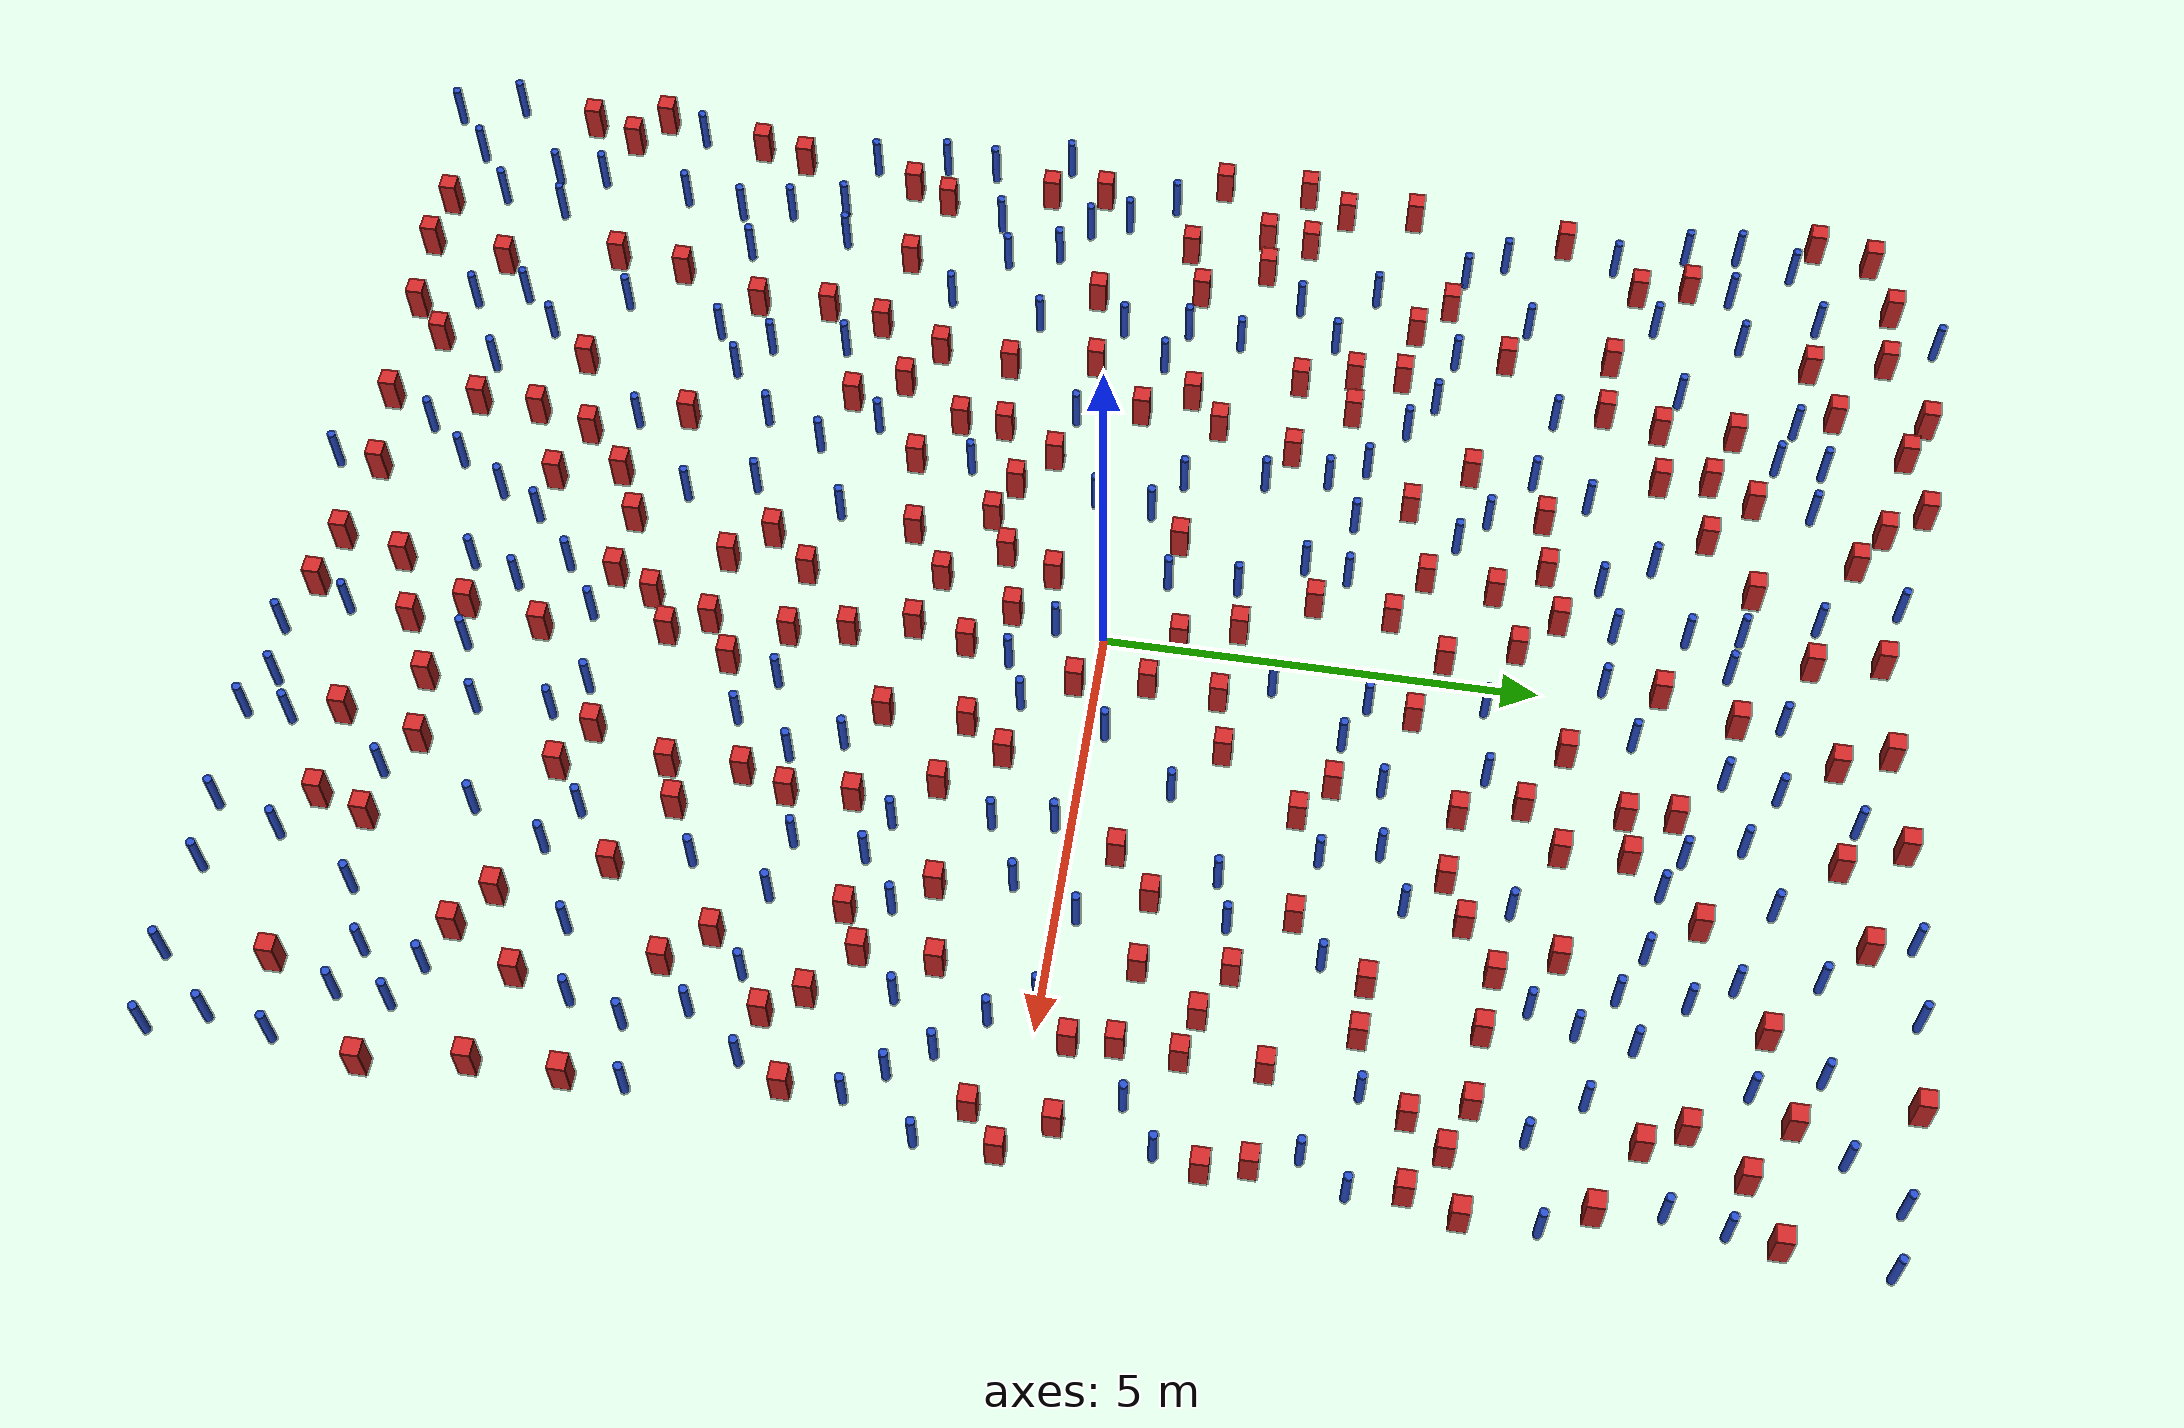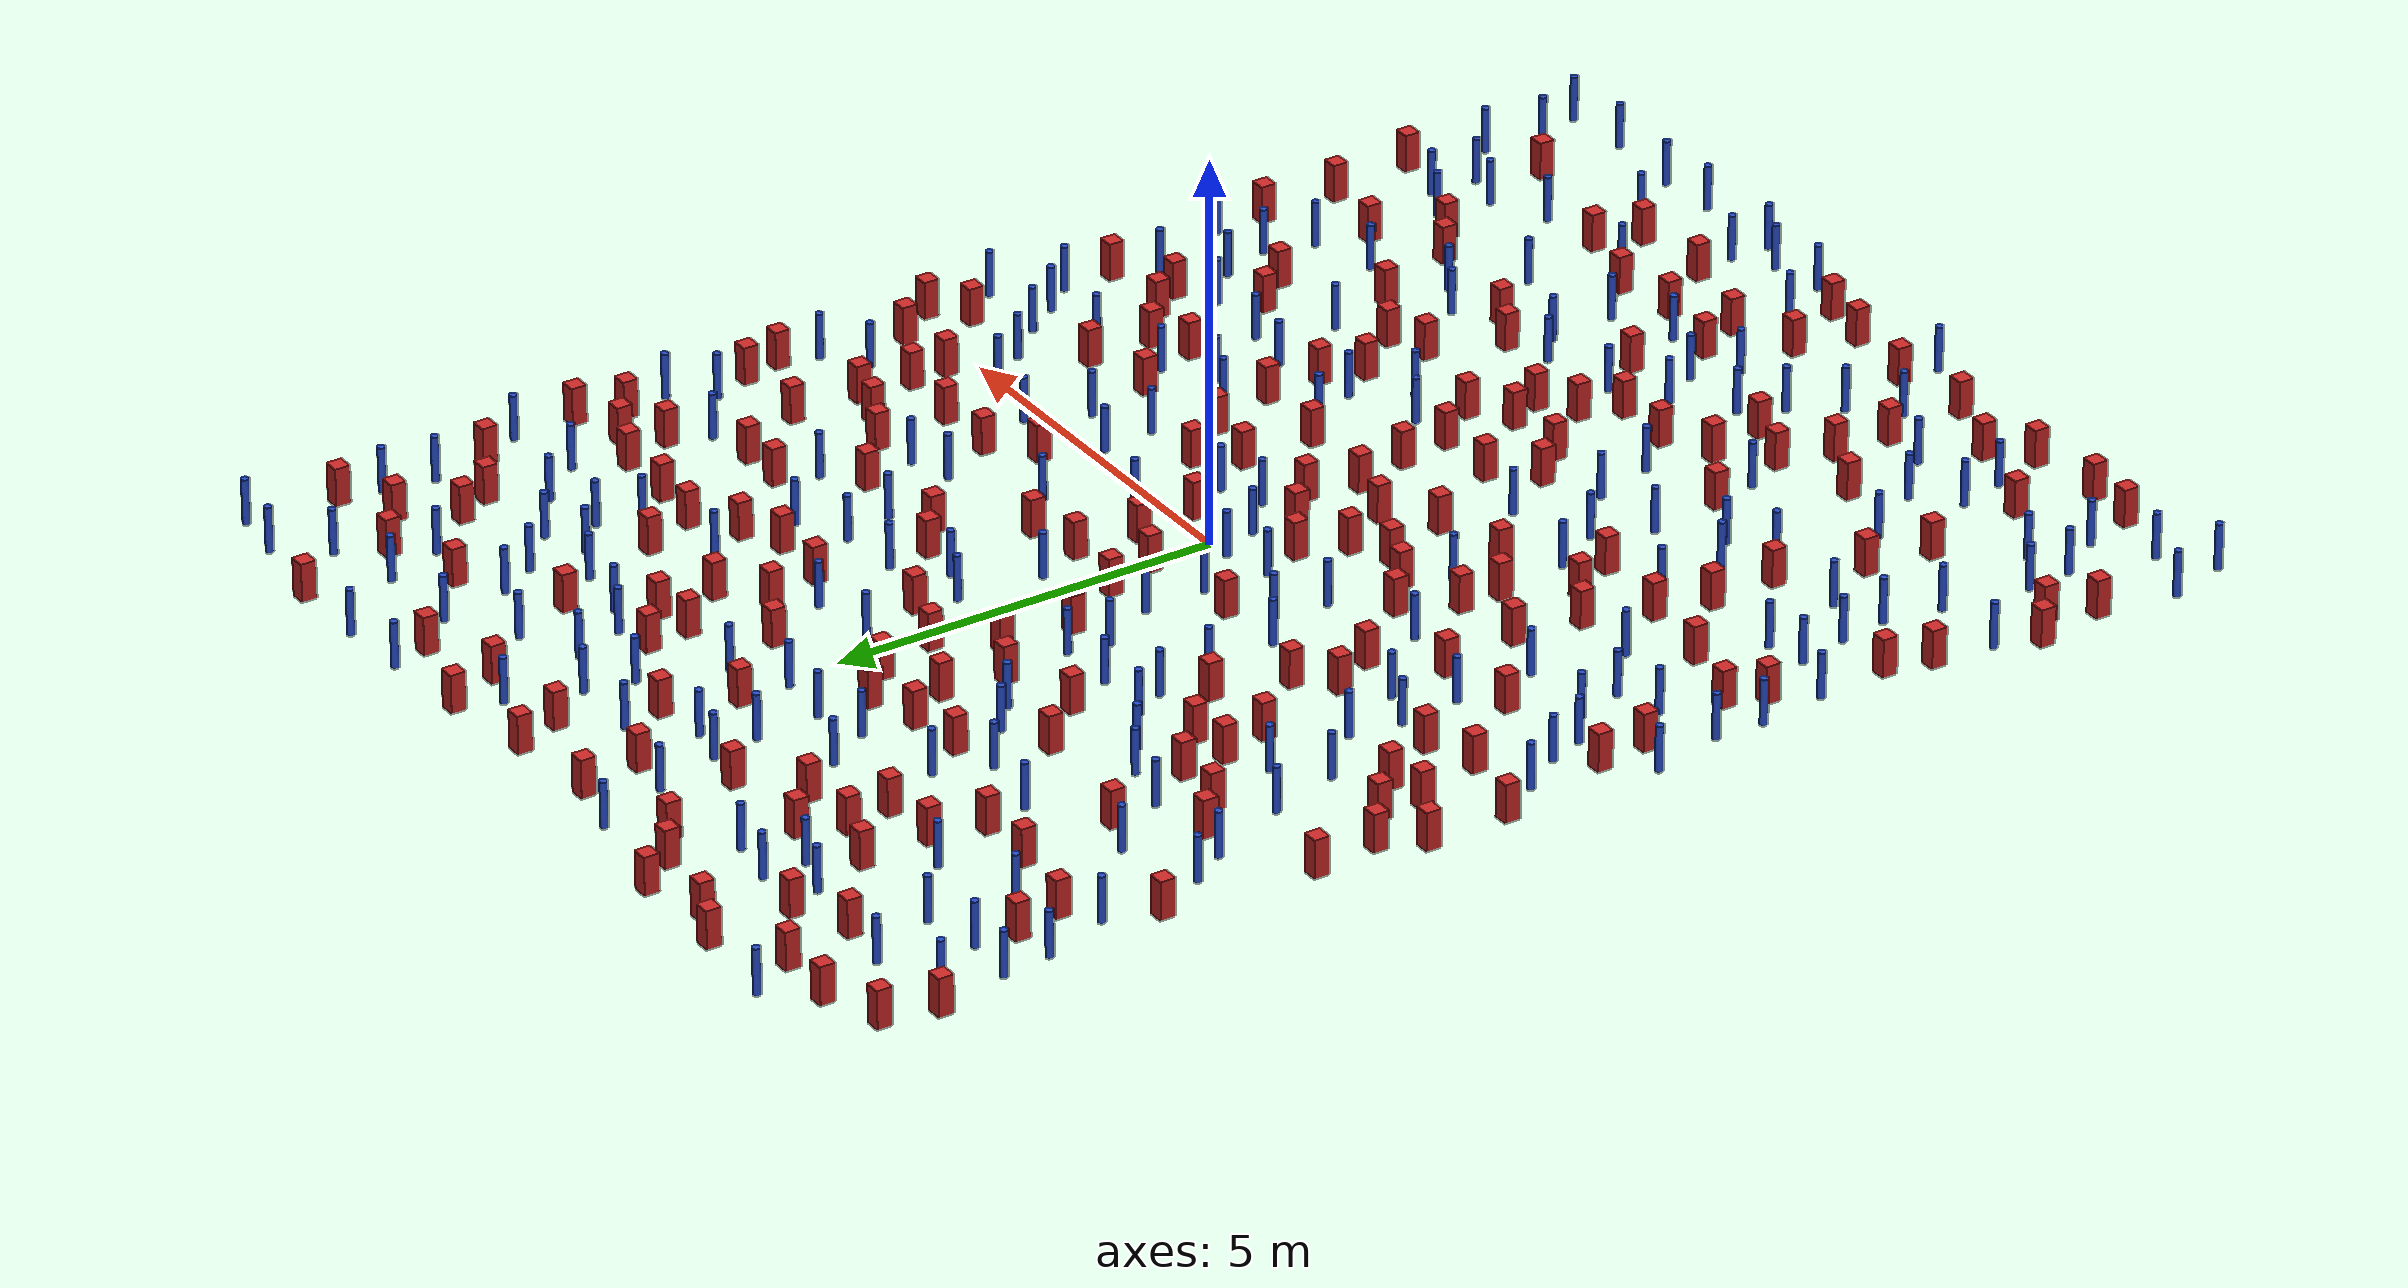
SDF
<sdf version="1.6">
  <model name="dense_88"><model name="pole_obstacle0">
  <static>true</static>
  <pose frame="">0.552288672222 -5.89928015238 7.38925637345e-09 -8.471706928e-08 1.24976765086e-08 -1.74513093015e-07</pose>
  <link name="link">
  <pose frame="">0 0 0.3 0 -0 0</pose>
    <inertial>
      <mass>1</mass>
      <inertia>
        <ixx>0.145833</ixx>
        <ixy>0</ixy>
        <ixz>0</ixz>
        <iyy>0.145833</iyy>
        <iyz>0</iyz>
        <izz>0.125</izz>
      </inertia>
    </inertial>
    <collision name="collision">
      <geometry>
        <cylinder>
          <radius>0.05</radius>
          <length>.6</length>
        </cylinder>
      </geometry>
      <max_contacts>10</max_contacts>
      <surface>
        <contact>
          <ode/>
        </contact>
        <bounce/>
        <friction>
          <torsional>
            <ode/>
          </torsional>
          <ode/>
        </friction>
      </surface>
    </collision>
    <visual name="visual">
      <geometry>
        <cylinder>
          <radius>0.05</radius>
          <length>.6</length>
        </cylinder>
      </geometry>
      <material>
        <script>
          <name>Gazebo/Blue</name>
          <uri>file://media/materials/scripts/gazebo.material</uri>
        </script>
      </material>
    </visual>
    <self_collide>0</self_collide>
    <kinematic>0</kinematic>
  </link>
</model>
<model name="pole_obstacle1">
  <static>true</static>
  <pose frame="">3.00676567767 3.73780736281 7.38925637345e-09 -8.47170692798e-08 1.24976764939e-08 -1.74513093025e-07</pose>
  <link name="link">
  <pose frame="">0 0 0.3 0 -0 0</pose>
    <inertial>
      <mass>1</mass>
      <inertia>
        <ixx>0.145833</ixx>
        <ixy>0</ixy>
        <ixz>0</ixz>
        <iyy>0.145833</iyy>
        <iyz>0</iyz>
        <izz>0.125</izz>
      </inertia>
    </inertial>
    <collision name="collision">
      <geometry>
        <cylinder>
          <radius>0.05</radius>
          <length>.6</length>
        </cylinder>
      </geometry>
      <max_contacts>10</max_contacts>
      <surface>
        <contact>
          <ode/>
        </contact>
        <bounce/>
        <friction>
          <torsional>
            <ode/>
          </torsional>
          <ode/>
        </friction>
      </surface>
    </collision>
    <visual name="visual">
      <geometry>
        <cylinder>
          <radius>0.05</radius>
          <length>.6</length>
        </cylinder>
      </geometry>
      <material>
        <script>
          <name>Gazebo/Blue</name>
          <uri>file://media/materials/scripts/gazebo.material</uri>
        </script>
      </material>
    </visual>
    <self_collide>0</self_collide>
    <kinematic>0</kinematic>
  </link>
</model>
<model name="square_post_obstacle0">
  <static>true</static>
  <pose frame="">-4.42537233581 9.34307108439 1.91545236811e-07 -7.35059704564e-06 1.12565212e-07 2.39332434364e-05</pose>
  <link name="link">
    <pose frame="">0 0 0.25 0 -0 0</pose>
    <inertial>
      <mass>100</mass>
      <inertia>
        <ixx>0.166667</ixx>
        <ixy>0</ixy>
        <ixz>0</ixz>
        <iyy>0.166667</iyy>
        <iyz>0</iyz>
        <izz>0.166667</izz>
      </inertia>
    </inertial>
    <collision name="collision">
      <geometry>
        <box>
          <size>.2 .2 .5</size>
        </box>
      </geometry>
      <max_contacts>10</max_contacts>
      <surface>
        <contact>
          <ode/>
        </contact>
        <bounce/>
        <friction>
          <torsional>
            <ode/>
          </torsional>
          <ode/>
        </friction>
      </surface>
    </collision>
    <visual name="visual">
      <geometry>
        <box>
          <size>.2 .2 .5</size>
        </box>
      </geometry>
      <material>
        <script>
          <name>Gazebo/Red</name>
          <uri>file://media/materials/scripts/gazebo.material</uri>
        </script>
      </material>
    </visual>
    <self_collide>0</self_collide>
    <kinematic>0</kinematic>
  </link>
</model>
<model name="square_post_obstacle1">
  <static>true</static>
  <pose frame="">-4.67498980944 -6.82831575101 1.91545236811e-07 -7.35059704564e-06 1.12565212e-07 2.39332434364e-05</pose>
  <link name="link">
    <pose frame="">0 0 0.25 0 -0 0</pose>
    <inertial>
      <mass>100</mass>
      <inertia>
        <ixx>0.166667</ixx>
        <ixy>0</ixy>
        <ixz>0</ixz>
        <iyy>0.166667</iyy>
        <iyz>0</iyz>
        <izz>0.166667</izz>
      </inertia>
    </inertial>
    <collision name="collision">
      <geometry>
        <box>
          <size>.2 .2 .5</size>
        </box>
      </geometry>
      <max_contacts>10</max_contacts>
      <surface>
        <contact>
          <ode/>
        </contact>
        <bounce/>
        <friction>
          <torsional>
            <ode/>
          </torsional>
          <ode/>
        </friction>
      </surface>
    </collision>
    <visual name="visual">
      <geometry>
        <box>
          <size>.2 .2 .5</size>
        </box>
      </geometry>
      <material>
        <script>
          <name>Gazebo/Red</name>
          <uri>file://media/materials/scripts/gazebo.material</uri>
        </script>
      </material>
    </visual>
    <self_collide>0</self_collide>
    <kinematic>0</kinematic>
  </link>
</model>
<model name="pole_obstacle2">
  <static>true</static>
  <pose frame="">5.726747599 -6.84969473188 7.38925637345e-09 -8.47170692796e-08 1.24976764786e-08 -1.74513093032e-07</pose>
  <link name="link">
  <pose frame="">0 0 0.3 0 -0 0</pose>
    <inertial>
      <mass>1</mass>
      <inertia>
        <ixx>0.145833</ixx>
        <ixy>0</ixy>
        <ixz>0</ixz>
        <iyy>0.145833</iyy>
        <iyz>0</iyz>
        <izz>0.125</izz>
      </inertia>
    </inertial>
    <collision name="collision">
      <geometry>
        <cylinder>
          <radius>0.05</radius>
          <length>.6</length>
        </cylinder>
      </geometry>
      <max_contacts>10</max_contacts>
      <surface>
        <contact>
          <ode/>
        </contact>
        <bounce/>
        <friction>
          <torsional>
            <ode/>
          </torsional>
          <ode/>
        </friction>
      </surface>
    </collision>
    <visual name="visual">
      <geometry>
        <cylinder>
          <radius>0.05</radius>
          <length>.6</length>
        </cylinder>
      </geometry>
      <material>
        <script>
          <name>Gazebo/Blue</name>
          <uri>file://media/materials/scripts/gazebo.material</uri>
        </script>
      </material>
    </visual>
    <self_collide>0</self_collide>
    <kinematic>0</kinematic>
  </link>
</model>
<model name="pole_obstacle3">
  <static>true</static>
  <pose frame="">-6.52432451563 -0.0444489107203 7.38925637345e-09 -8.47170692799e-08 1.24976765036e-08 -1.7451309302e-07</pose>
  <link name="link">
  <pose frame="">0 0 0.3 0 -0 0</pose>
    <inertial>
      <mass>1</mass>
      <inertia>
        <ixx>0.145833</ixx>
        <ixy>0</ixy>
        <ixz>0</ixz>
        <iyy>0.145833</iyy>
        <iyz>0</iyz>
        <izz>0.125</izz>
      </inertia>
    </inertial>
    <collision name="collision">
      <geometry>
        <cylinder>
          <radius>0.05</radius>
          <length>.6</length>
        </cylinder>
      </geometry>
      <max_contacts>10</max_contacts>
      <surface>
        <contact>
          <ode/>
        </contact>
        <bounce/>
        <friction>
          <torsional>
            <ode/>
          </torsional>
          <ode/>
        </friction>
      </surface>
    </collision>
    <visual name="visual">
      <geometry>
        <cylinder>
          <radius>0.05</radius>
          <length>.6</length>
        </cylinder>
      </geometry>
      <material>
        <script>
          <name>Gazebo/Blue</name>
          <uri>file://media/materials/scripts/gazebo.material</uri>
        </script>
      </material>
    </visual>
    <self_collide>0</self_collide>
    <kinematic>0</kinematic>
  </link>
</model>
<model name="pole_obstacle4">
  <static>true</static>
  <pose frame="">2.52354586549 -0.172979752865 7.38925637345e-09 -8.471706928e-08 1.24976765208e-08 -1.7451309301e-07</pose>
  <link name="link">
  <pose frame="">0 0 0.3 0 -0 0</pose>
    <inertial>
      <mass>1</mass>
      <inertia>
        <ixx>0.145833</ixx>
        <ixy>0</ixy>
        <ixz>0</ixz>
        <iyy>0.145833</iyy>
        <iyz>0</iyz>
        <izz>0.125</izz>
      </inertia>
    </inertial>
    <collision name="collision">
      <geometry>
        <cylinder>
          <radius>0.05</radius>
          <length>.6</length>
        </cylinder>
      </geometry>
      <max_contacts>10</max_contacts>
      <surface>
        <contact>
          <ode/>
        </contact>
        <bounce/>
        <friction>
          <torsional>
            <ode/>
          </torsional>
          <ode/>
        </friction>
      </surface>
    </collision>
    <visual name="visual">
      <geometry>
        <cylinder>
          <radius>0.05</radius>
          <length>.6</length>
        </cylinder>
      </geometry>
      <material>
        <script>
          <name>Gazebo/Blue</name>
          <uri>file://media/materials/scripts/gazebo.material</uri>
        </script>
      </material>
    </visual>
    <self_collide>0</self_collide>
    <kinematic>0</kinematic>
  </link>
</model>
<model name="pole_obstacle5">
  <static>true</static>
  <pose frame="">0.265713233834 -6.86529294261 7.38925637345e-09 -8.47170692799e-08 1.24976765101e-08 -1.74513093014e-07</pose>
  <link name="link">
  <pose frame="">0 0 0.3 0 -0 0</pose>
    <inertial>
      <mass>1</mass>
      <inertia>
        <ixx>0.145833</ixx>
        <ixy>0</ixy>
        <ixz>0</ixz>
        <iyy>0.145833</iyy>
        <iyz>0</iyz>
        <izz>0.125</izz>
      </inertia>
    </inertial>
    <collision name="collision">
      <geometry>
        <cylinder>
          <radius>0.05</radius>
          <length>.6</length>
        </cylinder>
      </geometry>
      <max_contacts>10</max_contacts>
      <surface>
        <contact>
          <ode/>
        </contact>
        <bounce/>
        <friction>
          <torsional>
            <ode/>
          </torsional>
          <ode/>
        </friction>
      </surface>
    </collision>
    <visual name="visual">
      <geometry>
        <cylinder>
          <radius>0.05</radius>
          <length>.6</length>
        </cylinder>
      </geometry>
      <material>
        <script>
          <name>Gazebo/Blue</name>
          <uri>file://media/materials/scripts/gazebo.material</uri>
        </script>
      </material>
    </visual>
    <self_collide>0</self_collide>
    <kinematic>0</kinematic>
  </link>
</model>
<model name="pole_obstacle6">
  <static>true</static>
  <pose frame="">1.14026042025 -3.58873495884 7.38925637345e-09 -8.47170692799e-08 1.24976765053e-08 -1.74513093017e-07</pose>
  <link name="link">
  <pose frame="">0 0 0.3 0 -0 0</pose>
    <inertial>
      <mass>1</mass>
      <inertia>
        <ixx>0.145833</ixx>
        <ixy>0</ixy>
        <ixz>0</ixz>
        <iyy>0.145833</iyy>
        <iyz>0</iyz>
        <izz>0.125</izz>
      </inertia>
    </inertial>
    <collision name="collision">
      <geometry>
        <cylinder>
          <radius>0.05</radius>
          <length>.6</length>
        </cylinder>
      </geometry>
      <max_contacts>10</max_contacts>
      <surface>
        <contact>
          <ode/>
        </contact>
        <bounce/>
        <friction>
          <torsional>
            <ode/>
          </torsional>
          <ode/>
        </friction>
      </surface>
    </collision>
    <visual name="visual">
      <geometry>
        <cylinder>
          <radius>0.05</radius>
          <length>.6</length>
        </cylinder>
      </geometry>
      <material>
        <script>
          <name>Gazebo/Blue</name>
          <uri>file://media/materials/scripts/gazebo.material</uri>
        </script>
      </material>
    </visual>
    <self_collide>0</self_collide>
    <kinematic>0</kinematic>
  </link>
</model>
<model name="square_post_obstacle2">
  <static>true</static>
  <pose frame="">-3.70692572244 -1.7061945904 1.91545236811e-07 -7.35059704564e-06 1.12565212e-07 2.39332434364e-05</pose>
  <link name="link">
    <pose frame="">0 0 0.25 0 -0 0</pose>
    <inertial>
      <mass>100</mass>
      <inertia>
        <ixx>0.166667</ixx>
        <ixy>0</ixy>
        <ixz>0</ixz>
        <iyy>0.166667</iyy>
        <iyz>0</iyz>
        <izz>0.166667</izz>
      </inertia>
    </inertial>
    <collision name="collision">
      <geometry>
        <box>
          <size>.2 .2 .5</size>
        </box>
      </geometry>
      <max_contacts>10</max_contacts>
      <surface>
        <contact>
          <ode/>
        </contact>
        <bounce/>
        <friction>
          <torsional>
            <ode/>
          </torsional>
          <ode/>
        </friction>
      </surface>
    </collision>
    <visual name="visual">
      <geometry>
        <box>
          <size>.2 .2 .5</size>
        </box>
      </geometry>
      <material>
        <script>
          <name>Gazebo/Red</name>
          <uri>file://media/materials/scripts/gazebo.material</uri>
        </script>
      </material>
    </visual>
    <self_collide>0</self_collide>
    <kinematic>0</kinematic>
  </link>
</model>
<model name="square_post_obstacle3">
  <static>true</static>
  <pose frame="">-3.88711328392 -0.675719960965 1.91545236811e-07 -7.35059704564e-06 1.12565212e-07 2.39332434364e-05</pose>
  <link name="link">
    <pose frame="">0 0 0.25 0 -0 0</pose>
    <inertial>
      <mass>100</mass>
      <inertia>
        <ixx>0.166667</ixx>
        <ixy>0</ixy>
        <ixz>0</ixz>
        <iyy>0.166667</iyy>
        <iyz>0</iyz>
        <izz>0.166667</izz>
      </inertia>
    </inertial>
    <collision name="collision">
      <geometry>
        <box>
          <size>.2 .2 .5</size>
        </box>
      </geometry>
      <max_contacts>10</max_contacts>
      <surface>
        <contact>
          <ode/>
        </contact>
        <bounce/>
        <friction>
          <torsional>
            <ode/>
          </torsional>
          <ode/>
        </friction>
      </surface>
    </collision>
    <visual name="visual">
      <geometry>
        <box>
          <size>.2 .2 .5</size>
        </box>
      </geometry>
      <material>
        <script>
          <name>Gazebo/Red</name>
          <uri>file://media/materials/scripts/gazebo.material</uri>
        </script>
      </material>
    </visual>
    <self_collide>0</self_collide>
    <kinematic>0</kinematic>
  </link>
</model>
<model name="square_post_obstacle4">
  <static>true</static>
  <pose frame="">0.182297855617 -2.18379983032 1.91545236811e-07 -7.35059704564e-06 1.12565212e-07 2.39332434364e-05</pose>
  <link name="link">
    <pose frame="">0 0 0.25 0 -0 0</pose>
    <inertial>
      <mass>100</mass>
      <inertia>
        <ixx>0.166667</ixx>
        <ixy>0</ixy>
        <ixz>0</ixz>
        <iyy>0.166667</iyy>
        <iyz>0</iyz>
        <izz>0.166667</izz>
      </inertia>
    </inertial>
    <collision name="collision">
      <geometry>
        <box>
          <size>.2 .2 .5</size>
        </box>
      </geometry>
      <max_contacts>10</max_contacts>
      <surface>
        <contact>
          <ode/>
        </contact>
        <bounce/>
        <friction>
          <torsional>
            <ode/>
          </torsional>
          <ode/>
        </friction>
      </surface>
    </collision>
    <visual name="visual">
      <geometry>
        <box>
          <size>.2 .2 .5</size>
        </box>
      </geometry>
      <material>
        <script>
          <name>Gazebo/Red</name>
          <uri>file://media/materials/scripts/gazebo.material</uri>
        </script>
      </material>
    </visual>
    <self_collide>0</self_collide>
    <kinematic>0</kinematic>
  </link>
</model>
<model name="pole_obstacle7">
  <static>true</static>
  <pose frame="">-4.47552511647 1.02826375217 7.38925637345e-09 -8.47170692801e-08 1.24976765139e-08 -1.74513093014e-07</pose>
  <link name="link">
  <pose frame="">0 0 0.3 0 -0 0</pose>
    <inertial>
      <mass>1</mass>
      <inertia>
        <ixx>0.145833</ixx>
        <ixy>0</ixy>
        <ixz>0</ixz>
        <iyy>0.145833</iyy>
        <iyz>0</iyz>
        <izz>0.125</izz>
      </inertia>
    </inertial>
    <collision name="collision">
      <geometry>
        <cylinder>
          <radius>0.05</radius>
          <length>.6</length>
        </cylinder>
      </geometry>
      <max_contacts>10</max_contacts>
      <surface>
        <contact>
          <ode/>
        </contact>
        <bounce/>
        <friction>
          <torsional>
            <ode/>
          </torsional>
          <ode/>
        </friction>
      </surface>
    </collision>
    <visual name="visual">
      <geometry>
        <cylinder>
          <radius>0.05</radius>
          <length>.6</length>
        </cylinder>
      </geometry>
      <material>
        <script>
          <name>Gazebo/Blue</name>
          <uri>file://media/materials/scripts/gazebo.material</uri>
        </script>
      </material>
    </visual>
    <self_collide>0</self_collide>
    <kinematic>0</kinematic>
  </link>
</model>
<model name="pole_obstacle8">
  <static>true</static>
  <pose frame="">-5.37966165243 -4.06961896865 7.38925637345e-09 -8.47170692796e-08 1.24976764786e-08 -1.74513093032e-07</pose>
  <link name="link">
  <pose frame="">0 0 0.3 0 -0 0</pose>
    <inertial>
      <mass>1</mass>
      <inertia>
        <ixx>0.145833</ixx>
        <ixy>0</ixy>
        <ixz>0</ixz>
        <iyy>0.145833</iyy>
        <iyz>0</iyz>
        <izz>0.125</izz>
      </inertia>
    </inertial>
    <collision name="collision">
      <geometry>
        <cylinder>
          <radius>0.05</radius>
          <length>.6</length>
        </cylinder>
      </geometry>
      <max_contacts>10</max_contacts>
      <surface>
        <contact>
          <ode/>
        </contact>
        <bounce/>
        <friction>
          <torsional>
            <ode/>
          </torsional>
          <ode/>
        </friction>
      </surface>
    </collision>
    <visual name="visual">
      <geometry>
        <cylinder>
          <radius>0.05</radius>
          <length>.6</length>
        </cylinder>
      </geometry>
      <material>
        <script>
          <name>Gazebo/Blue</name>
          <uri>file://media/materials/scripts/gazebo.material</uri>
        </script>
      </material>
    </visual>
    <self_collide>0</self_collide>
    <kinematic>0</kinematic>
  </link>
</model>
<model name="square_post_obstacle5">
  <static>true</static>
  <pose frame="">-0.0569344833062 -9.03164974831 1.91545236811e-07 -7.35059704564e-06 1.12565212e-07 2.39332434364e-05</pose>
  <link name="link">
    <pose frame="">0 0 0.25 0 -0 0</pose>
    <inertial>
      <mass>100</mass>
      <inertia>
        <ixx>0.166667</ixx>
        <ixy>0</ixy>
        <ixz>0</ixz>
        <iyy>0.166667</iyy>
        <iyz>0</iyz>
        <izz>0.166667</izz>
      </inertia>
    </inertial>
    <collision name="collision">
      <geometry>
        <box>
          <size>.2 .2 .5</size>
        </box>
      </geometry>
      <max_contacts>10</max_contacts>
      <surface>
        <contact>
          <ode/>
        </contact>
        <bounce/>
        <friction>
          <torsional>
            <ode/>
          </torsional>
          <ode/>
        </friction>
      </surface>
    </collision>
    <visual name="visual">
      <geometry>
        <box>
          <size>.2 .2 .5</size>
        </box>
      </geometry>
      <material>
        <script>
          <name>Gazebo/Red</name>
          <uri>file://media/materials/scripts/gazebo.material</uri>
        </script>
      </material>
    </visual>
    <self_collide>0</self_collide>
    <kinematic>0</kinematic>
  </link>
</model>
<model name="square_post_obstacle6">
  <static>true</static>
  <pose frame="">-0.779457869081 2.34286586143 1.91545236811e-07 -7.35059704564e-06 1.12565212e-07 2.39332434364e-05</pose>
  <link name="link">
    <pose frame="">0 0 0.25 0 -0 0</pose>
    <inertial>
      <mass>100</mass>
      <inertia>
        <ixx>0.166667</ixx>
        <ixy>0</ixy>
        <ixz>0</ixz>
        <iyy>0.166667</iyy>
        <iyz>0</iyz>
        <izz>0.166667</izz>
      </inertia>
    </inertial>
    <collision name="collision">
      <geometry>
        <box>
          <size>.2 .2 .5</size>
        </box>
      </geometry>
      <max_contacts>10</max_contacts>
      <surface>
        <contact>
          <ode/>
        </contact>
        <bounce/>
        <friction>
          <torsional>
            <ode/>
          </torsional>
          <ode/>
        </friction>
      </surface>
    </collision>
    <visual name="visual">
      <geometry>
        <box>
          <size>.2 .2 .5</size>
        </box>
      </geometry>
      <material>
        <script>
          <name>Gazebo/Red</name>
          <uri>file://media/materials/scripts/gazebo.material</uri>
        </script>
      </material>
    </visual>
    <self_collide>0</self_collide>
    <kinematic>0</kinematic>
  </link>
</model>
<model name="square_post_obstacle7">
  <static>true</static>
  <pose frame="">0.385087380425 -2.91029149053 1.91545236811e-07 -7.35059704564e-06 1.12565212e-07 2.39332434364e-05</pose>
  <link name="link">
    <pose frame="">0 0 0.25 0 -0 0</pose>
    <inertial>
      <mass>100</mass>
      <inertia>
        <ixx>0.166667</ixx>
        <ixy>0</ixy>
        <ixz>0</ixz>
        <iyy>0.166667</iyy>
        <iyz>0</iyz>
        <izz>0.166667</izz>
      </inertia>
    </inertial>
    <collision name="collision">
      <geometry>
        <box>
          <size>.2 .2 .5</size>
        </box>
      </geometry>
      <max_contacts>10</max_contacts>
      <surface>
        <contact>
          <ode/>
        </contact>
        <bounce/>
        <friction>
          <torsional>
            <ode/>
          </torsional>
          <ode/>
        </friction>
      </surface>
    </collision>
    <visual name="visual">
      <geometry>
        <box>
          <size>.2 .2 .5</size>
        </box>
      </geometry>
      <material>
        <script>
          <name>Gazebo/Red</name>
          <uri>file://media/materials/scripts/gazebo.material</uri>
        </script>
      </material>
    </visual>
    <self_collide>0</self_collide>
    <kinematic>0</kinematic>
  </link>
</model>
<model name="pole_obstacle9">
  <static>true</static>
  <pose frame="">6.43883494584 9.03935850446 7.38925637345e-09 -8.471706928e-08 1.24976765081e-08 -1.74513093015e-07</pose>
  <link name="link">
  <pose frame="">0 0 0.3 0 -0 0</pose>
    <inertial>
      <mass>1</mass>
      <inertia>
        <ixx>0.145833</ixx>
        <ixy>0</ixy>
        <ixz>0</ixz>
        <iyy>0.145833</iyy>
        <iyz>0</iyz>
        <izz>0.125</izz>
      </inertia>
    </inertial>
    <collision name="collision">
      <geometry>
        <cylinder>
          <radius>0.05</radius>
          <length>.6</length>
        </cylinder>
      </geometry>
      <max_contacts>10</max_contacts>
      <surface>
        <contact>
          <ode/>
        </contact>
        <bounce/>
        <friction>
          <torsional>
            <ode/>
          </torsional>
          <ode/>
        </friction>
      </surface>
    </collision>
    <visual name="visual">
      <geometry>
        <cylinder>
          <radius>0.05</radius>
          <length>.6</length>
        </cylinder>
      </geometry>
      <material>
        <script>
          <name>Gazebo/Blue</name>
          <uri>file://media/materials/scripts/gazebo.material</uri>
        </script>
      </material>
    </visual>
    <self_collide>0</self_collide>
    <kinematic>0</kinematic>
  </link>
</model>
<model name="pole_obstacle10">
  <static>true</static>
  <pose frame="">1.82763532323 -2.68481853135 7.38925637345e-09 -8.47170692799e-08 1.24976765053e-08 -1.74513093017e-07</pose>
  <link name="link">
  <pose frame="">0 0 0.3 0 -0 0</pose>
    <inertial>
      <mass>1</mass>
      <inertia>
        <ixx>0.145833</ixx>
        <ixy>0</ixy>
        <ixz>0</ixz>
        <iyy>0.145833</iyy>
        <iyz>0</iyz>
        <izz>0.125</izz>
      </inertia>
    </inertial>
    <collision name="collision">
      <geometry>
        <cylinder>
          <radius>0.05</radius>
          <length>.6</length>
        </cylinder>
      </geometry>
      <max_contacts>10</max_contacts>
      <surface>
        <contact>
          <ode/>
        </contact>
        <bounce/>
        <friction>
          <torsional>
            <ode/>
          </torsional>
          <ode/>
        </friction>
      </surface>
    </collision>
    <visual name="visual">
      <geometry>
        <cylinder>
          <radius>0.05</radius>
          <length>.6</length>
        </cylinder>
      </geometry>
      <material>
        <script>
          <name>Gazebo/Blue</name>
          <uri>file://media/materials/scripts/gazebo.material</uri>
        </script>
      </material>
    </visual>
    <self_collide>0</self_collide>
    <kinematic>0</kinematic>
  </link>
</model>
<model name="pole_obstacle11">
  <static>true</static>
  <pose frame="">3.85353323174 -3.12247104477 7.38925637345e-09 -8.47170692798e-08 1.24976764939e-08 -1.74513093025e-07</pose>
  <link name="link">
  <pose frame="">0 0 0.3 0 -0 0</pose>
    <inertial>
      <mass>1</mass>
      <inertia>
        <ixx>0.145833</ixx>
        <ixy>0</ixy>
        <ixz>0</ixz>
        <iyy>0.145833</iyy>
        <iyz>0</iyz>
        <izz>0.125</izz>
      </inertia>
    </inertial>
    <collision name="collision">
      <geometry>
        <cylinder>
          <radius>0.05</radius>
          <length>.6</length>
        </cylinder>
      </geometry>
      <max_contacts>10</max_contacts>
      <surface>
        <contact>
          <ode/>
        </contact>
        <bounce/>
        <friction>
          <torsional>
            <ode/>
          </torsional>
          <ode/>
        </friction>
      </surface>
    </collision>
    <visual name="visual">
      <geometry>
        <cylinder>
          <radius>0.05</radius>
          <length>.6</length>
        </cylinder>
      </geometry>
      <material>
        <script>
          <name>Gazebo/Blue</name>
          <uri>file://media/materials/scripts/gazebo.material</uri>
        </script>
      </material>
    </visual>
    <self_collide>0</self_collide>
    <kinematic>0</kinematic>
  </link>
</model>
<model name="pole_obstacle12">
  <static>true</static>
  <pose frame="">-5.4626077575 -8.49701745886 7.38925637345e-09 -8.471706928e-08 1.24976765081e-08 -1.74513093015e-07</pose>
  <link name="link">
  <pose frame="">0 0 0.3 0 -0 0</pose>
    <inertial>
      <mass>1</mass>
      <inertia>
        <ixx>0.145833</ixx>
        <ixy>0</ixy>
        <ixz>0</ixz>
        <iyy>0.145833</iyy>
        <iyz>0</iyz>
        <izz>0.125</izz>
      </inertia>
    </inertial>
    <collision name="collision">
      <geometry>
        <cylinder>
          <radius>0.05</radius>
          <length>.6</length>
        </cylinder>
      </geometry>
      <max_contacts>10</max_contacts>
      <surface>
        <contact>
          <ode/>
        </contact>
        <bounce/>
        <friction>
          <torsional>
            <ode/>
          </torsional>
          <ode/>
        </friction>
      </surface>
    </collision>
    <visual name="visual">
      <geometry>
        <cylinder>
          <radius>0.05</radius>
          <length>.6</length>
        </cylinder>
      </geometry>
      <material>
        <script>
          <name>Gazebo/Blue</name>
          <uri>file://media/materials/scripts/gazebo.material</uri>
        </script>
      </material>
    </visual>
    <self_collide>0</self_collide>
    <kinematic>0</kinematic>
  </link>
</model>
<model name="square_post_obstacle8">
  <static>true</static>
  <pose frame="">6.05506453243 0.368401354186 1.91545236811e-07 -7.35059704564e-06 1.12565212e-07 2.39332434364e-05</pose>
  <link name="link">
    <pose frame="">0 0 0.25 0 -0 0</pose>
    <inertial>
      <mass>100</mass>
      <inertia>
        <ixx>0.166667</ixx>
        <ixy>0</ixy>
        <ixz>0</ixz>
        <iyy>0.166667</iyy>
        <iyz>0</iyz>
        <izz>0.166667</izz>
      </inertia>
    </inertial>
    <collision name="collision">
      <geometry>
        <box>
          <size>.2 .2 .5</size>
        </box>
      </geometry>
      <max_contacts>10</max_contacts>
      <surface>
        <contact>
          <ode/>
        </contact>
        <bounce/>
        <friction>
          <torsional>
            <ode/>
          </torsional>
          <ode/>
        </friction>
      </surface>
    </collision>
    <visual name="visual">
      <geometry>
        <box>
          <size>.2 .2 .5</size>
        </box>
      </geometry>
      <material>
        <script>
          <name>Gazebo/Red</name>
          <uri>file://media/materials/scripts/gazebo.material</uri>
        </script>
      </material>
    </visual>
    <self_collide>0</self_collide>
    <kinematic>0</kinematic>
  </link>
</model>
<model name="square_post_obstacle9">
  <static>true</static>
  <pose frame="">2.03781863392 2.46468517248 1.91545236811e-07 -7.35059704564e-06 1.12565212e-07 2.39332434364e-05</pose>
  <link name="link">
    <pose frame="">0 0 0.25 0 -0 0</pose>
    <inertial>
      <mass>100</mass>
      <inertia>
        <ixx>0.166667</ixx>
        <ixy>0</ixy>
        <ixz>0</ixz>
        <iyy>0.166667</iyy>
        <iyz>0</iyz>
        <izz>0.166667</izz>
      </inertia>
    </inertial>
    <collision name="collision">
      <geometry>
        <box>
          <size>.2 .2 .5</size>
        </box>
      </geometry>
      <max_contacts>10</max_contacts>
      <surface>
        <contact>
          <ode/>
        </contact>
        <bounce/>
        <friction>
          <torsional>
            <ode/>
          </torsional>
          <ode/>
        </friction>
      </surface>
    </collision>
    <visual name="visual">
      <geometry>
        <box>
          <size>.2 .2 .5</size>
        </box>
      </geometry>
      <material>
        <script>
          <name>Gazebo/Red</name>
          <uri>file://media/materials/scripts/gazebo.material</uri>
        </script>
      </material>
    </visual>
    <self_collide>0</self_collide>
    <kinematic>0</kinematic>
  </link>
</model>
<model name="pole_obstacle13">
  <static>true</static>
  <pose frame="">3.62405460499 -5.69707315796 7.38925637345e-09 -8.47170692798e-08 1.24976765033e-08 -1.74513093019e-07</pose>
  <link name="link">
  <pose frame="">0 0 0.3 0 -0 0</pose>
    <inertial>
      <mass>1</mass>
      <inertia>
        <ixx>0.145833</ixx>
        <ixy>0</ixy>
        <ixz>0</ixz>
        <iyy>0.145833</iyy>
        <iyz>0</iyz>
        <izz>0.125</izz>
      </inertia>
    </inertial>
    <collision name="collision">
      <geometry>
        <cylinder>
          <radius>0.05</radius>
          <length>.6</length>
        </cylinder>
      </geometry>
      <max_contacts>10</max_contacts>
      <surface>
        <contact>
          <ode/>
        </contact>
        <bounce/>
        <friction>
          <torsional>
            <ode/>
          </torsional>
          <ode/>
        </friction>
      </surface>
    </collision>
    <visual name="visual">
      <geometry>
        <cylinder>
          <radius>0.05</radius>
          <length>.6</length>
        </cylinder>
      </geometry>
      <material>
        <script>
          <name>Gazebo/Blue</name>
          <uri>file://media/materials/scripts/gazebo.material</uri>
        </script>
      </material>
    </visual>
    <self_collide>0</self_collide>
    <kinematic>0</kinematic>
  </link>
</model>
<model name="square_post_obstacle10">
  <static>true</static>
  <pose frame="">-6.34527799305 -3.37768642562 1.91545236811e-07 -7.35059704564e-06 1.12565212e-07 2.39332434364e-05</pose>
  <link name="link">
    <pose frame="">0 0 0.25 0 -0 0</pose>
    <inertial>
      <mass>100</mass>
      <inertia>
        <ixx>0.166667</ixx>
        <ixy>0</ixy>
        <ixz>0</ixz>
        <iyy>0.166667</iyy>
        <iyz>0</iyz>
        <izz>0.166667</izz>
      </inertia>
    </inertial>
    <collision name="collision">
      <geometry>
        <box>
          <size>.2 .2 .5</size>
        </box>
      </geometry>
      <max_contacts>10</max_contacts>
      <surface>
        <contact>
          <ode/>
        </contact>
        <bounce/>
        <friction>
          <torsional>
            <ode/>
          </torsional>
          <ode/>
        </friction>
      </surface>
    </collision>
    <visual name="visual">
      <geometry>
        <box>
          <size>.2 .2 .5</size>
        </box>
      </geometry>
      <material>
        <script>
          <name>Gazebo/Red</name>
          <uri>file://media/materials/scripts/gazebo.material</uri>
        </script>
      </material>
    </visual>
    <self_collide>0</self_collide>
    <kinematic>0</kinematic>
  </link>
</model>
<model name="square_post_obstacle11">
  <static>true</static>
  <pose frame="">-2.42287995631 -0.95356776099 1.91545236811e-07 -7.35059704564e-06 1.12565212e-07 2.39332434364e-05</pose>
  <link name="link">
    <pose frame="">0 0 0.25 0 -0 0</pose>
    <inertial>
      <mass>100</mass>
      <inertia>
        <ixx>0.166667</ixx>
        <ixy>0</ixy>
        <ixz>0</ixz>
        <iyy>0.166667</iyy>
        <iyz>0</iyz>
        <izz>0.166667</izz>
      </inertia>
    </inertial>
    <collision name="collision">
      <geometry>
        <box>
          <size>.2 .2 .5</size>
        </box>
      </geometry>
      <max_contacts>10</max_contacts>
      <surface>
        <contact>
          <ode/>
        </contact>
        <bounce/>
        <friction>
          <torsional>
            <ode/>
          </torsional>
          <ode/>
        </friction>
      </surface>
    </collision>
    <visual name="visual">
      <geometry>
        <box>
          <size>.2 .2 .5</size>
        </box>
      </geometry>
      <material>
        <script>
          <name>Gazebo/Red</name>
          <uri>file://media/materials/scripts/gazebo.material</uri>
        </script>
      </material>
    </visual>
    <self_collide>0</self_collide>
    <kinematic>0</kinematic>
  </link>
</model>
<model name="pole_obstacle14">
  <static>true</static>
  <pose frame="">1.97462156829 -6.91148437594 7.38925637345e-09 -8.471706928e-08 1.24976765202e-08 -1.7451309301e-07</pose>
  <link name="link">
  <pose frame="">0 0 0.3 0 -0 0</pose>
    <inertial>
      <mass>1</mass>
      <inertia>
        <ixx>0.145833</ixx>
        <ixy>0</ixy>
        <ixz>0</ixz>
        <iyy>0.145833</iyy>
        <iyz>0</iyz>
        <izz>0.125</izz>
      </inertia>
    </inertial>
    <collision name="collision">
      <geometry>
        <cylinder>
          <radius>0.05</radius>
          <length>.6</length>
        </cylinder>
      </geometry>
      <max_contacts>10</max_contacts>
      <surface>
        <contact>
          <ode/>
        </contact>
        <bounce/>
        <friction>
          <torsional>
            <ode/>
          </torsional>
          <ode/>
        </friction>
      </surface>
    </collision>
    <visual name="visual">
      <geometry>
        <cylinder>
          <radius>0.05</radius>
          <length>.6</length>
        </cylinder>
      </geometry>
      <material>
        <script>
          <name>Gazebo/Blue</name>
          <uri>file://media/materials/scripts/gazebo.material</uri>
        </script>
      </material>
    </visual>
    <self_collide>0</self_collide>
    <kinematic>0</kinematic>
  </link>
</model>
<model name="pole_obstacle15">
  <static>true</static>
  <pose frame="">-1.29347158093 2.18036558145 7.38925637345e-09 -8.47170692799e-08 1.24976765053e-08 -1.74513093017e-07</pose>
  <link name="link">
  <pose frame="">0 0 0.3 0 -0 0</pose>
    <inertial>
      <mass>1</mass>
      <inertia>
        <ixx>0.145833</ixx>
        <ixy>0</ixy>
        <ixz>0</ixz>
        <iyy>0.145833</iyy>
        <iyz>0</iyz>
        <izz>0.125</izz>
      </inertia>
    </inertial>
    <collision name="collision">
      <geometry>
        <cylinder>
          <radius>0.05</radius>
          <length>.6</length>
        </cylinder>
      </geometry>
      <max_contacts>10</max_contacts>
      <surface>
        <contact>
          <ode/>
        </contact>
        <bounce/>
        <friction>
          <torsional>
            <ode/>
          </torsional>
          <ode/>
        </friction>
      </surface>
    </collision>
    <visual name="visual">
      <geometry>
        <cylinder>
          <radius>0.05</radius>
          <length>.6</length>
        </cylinder>
      </geometry>
      <material>
        <script>
          <name>Gazebo/Blue</name>
          <uri>file://media/materials/scripts/gazebo.material</uri>
        </script>
      </material>
    </visual>
    <self_collide>0</self_collide>
    <kinematic>0</kinematic>
  </link>
</model>
<model name="square_post_obstacle12">
  <static>true</static>
  <pose frame="">-1.10398348452 -8.89840903795 1.91545236811e-07 -7.35059704564e-06 1.12565212e-07 2.39332434364e-05</pose>
  <link name="link">
    <pose frame="">0 0 0.25 0 -0 0</pose>
    <inertial>
      <mass>100</mass>
      <inertia>
        <ixx>0.166667</ixx>
        <ixy>0</ixy>
        <ixz>0</ixz>
        <iyy>0.166667</iyy>
        <iyz>0</iyz>
        <izz>0.166667</izz>
      </inertia>
    </inertial>
    <collision name="collision">
      <geometry>
        <box>
          <size>.2 .2 .5</size>
        </box>
      </geometry>
      <max_contacts>10</max_contacts>
      <surface>
        <contact>
          <ode/>
        </contact>
        <bounce/>
        <friction>
          <torsional>
            <ode/>
          </torsional>
          <ode/>
        </friction>
      </surface>
    </collision>
    <visual name="visual">
      <geometry>
        <box>
          <size>.2 .2 .5</size>
        </box>
      </geometry>
      <material>
        <script>
          <name>Gazebo/Red</name>
          <uri>file://media/materials/scripts/gazebo.material</uri>
        </script>
      </material>
    </visual>
    <self_collide>0</self_collide>
    <kinematic>0</kinematic>
  </link>
</model>
<model name="pole_obstacle16">
  <static>true</static>
  <pose frame="">0.417773265763 1.99657974552 7.38925637345e-09 -8.47170692799e-08 1.24976765022e-08 -1.74513093019e-07</pose>
  <link name="link">
  <pose frame="">0 0 0.3 0 -0 0</pose>
    <inertial>
      <mass>1</mass>
      <inertia>
        <ixx>0.145833</ixx>
        <ixy>0</ixy>
        <ixz>0</ixz>
        <iyy>0.145833</iyy>
        <iyz>0</iyz>
        <izz>0.125</izz>
      </inertia>
    </inertial>
    <collision name="collision">
      <geometry>
        <cylinder>
          <radius>0.05</radius>
          <length>.6</length>
        </cylinder>
      </geometry>
      <max_contacts>10</max_contacts>
      <surface>
        <contact>
          <ode/>
        </contact>
        <bounce/>
        <friction>
          <torsional>
            <ode/>
          </torsional>
          <ode/>
        </friction>
      </surface>
    </collision>
    <visual name="visual">
      <geometry>
        <cylinder>
          <radius>0.05</radius>
          <length>.6</length>
        </cylinder>
      </geometry>
      <material>
        <script>
          <name>Gazebo/Blue</name>
          <uri>file://media/materials/scripts/gazebo.material</uri>
        </script>
      </material>
    </visual>
    <self_collide>0</self_collide>
    <kinematic>0</kinematic>
  </link>
</model>
<model name="pole_obstacle17">
  <static>true</static>
  <pose frame="">-1.03280544207 7.2472922459 7.38925637345e-09 -8.47170692799e-08 1.2497676505e-08 -1.74513093018e-07</pose>
  <link name="link">
  <pose frame="">0 0 0.3 0 -0 0</pose>
    <inertial>
      <mass>1</mass>
      <inertia>
        <ixx>0.145833</ixx>
        <ixy>0</ixy>
        <ixz>0</ixz>
        <iyy>0.145833</iyy>
        <iyz>0</iyz>
        <izz>0.125</izz>
      </inertia>
    </inertial>
    <collision name="collision">
      <geometry>
        <cylinder>
          <radius>0.05</radius>
          <length>.6</length>
        </cylinder>
      </geometry>
      <max_contacts>10</max_contacts>
      <surface>
        <contact>
          <ode/>
        </contact>
        <bounce/>
        <friction>
          <torsional>
            <ode/>
          </torsional>
          <ode/>
        </friction>
      </surface>
    </collision>
    <visual name="visual">
      <geometry>
        <cylinder>
          <radius>0.05</radius>
          <length>.6</length>
        </cylinder>
      </geometry>
      <material>
        <script>
          <name>Gazebo/Blue</name>
          <uri>file://media/materials/scripts/gazebo.material</uri>
        </script>
      </material>
    </visual>
    <self_collide>0</self_collide>
    <kinematic>0</kinematic>
  </link>
</model>
<model name="square_post_obstacle13">
  <static>true</static>
  <pose frame="">0.308547579843 8.96091731637 1.91545236811e-07 -7.35059704564e-06 1.12565212e-07 2.39332434364e-05</pose>
  <link name="link">
    <pose frame="">0 0 0.25 0 -0 0</pose>
    <inertial>
      <mass>100</mass>
      <inertia>
        <ixx>0.166667</ixx>
        <ixy>0</ixy>
        <ixz>0</ixz>
        <iyy>0.166667</iyy>
        <iyz>0</iyz>
        <izz>0.166667</izz>
      </inertia>
    </inertial>
    <collision name="collision">
      <geometry>
        <box>
          <size>.2 .2 .5</size>
        </box>
      </geometry>
      <max_contacts>10</max_contacts>
      <surface>
        <contact>
          <ode/>
        </contact>
        <bounce/>
        <friction>
          <torsional>
            <ode/>
          </torsional>
          <ode/>
        </friction>
      </surface>
    </collision>
    <visual name="visual">
      <geometry>
        <box>
          <size>.2 .2 .5</size>
        </box>
      </geometry>
      <material>
        <script>
          <name>Gazebo/Red</name>
          <uri>file://media/materials/scripts/gazebo.material</uri>
        </script>
      </material>
    </visual>
    <self_collide>0</self_collide>
    <kinematic>0</kinematic>
  </link>
</model>
<model name="pole_obstacle18">
  <static>true</static>
  <pose frame="">6.0780218421 -1.86008930025 7.38925637345e-09 -8.471706928e-08 1.24976765134e-08 -1.74513093015e-07</pose>
  <link name="link">
  <pose frame="">0 0 0.3 0 -0 0</pose>
    <inertial>
      <mass>1</mass>
      <inertia>
        <ixx>0.145833</ixx>
        <ixy>0</ixy>
        <ixz>0</ixz>
        <iyy>0.145833</iyy>
        <iyz>0</iyz>
        <izz>0.125</izz>
      </inertia>
    </inertial>
    <collision name="collision">
      <geometry>
        <cylinder>
          <radius>0.05</radius>
          <length>.6</length>
        </cylinder>
      </geometry>
      <max_contacts>10</max_contacts>
      <surface>
        <contact>
          <ode/>
        </contact>
        <bounce/>
        <friction>
          <torsional>
            <ode/>
          </torsional>
          <ode/>
        </friction>
      </surface>
    </collision>
    <visual name="visual">
      <geometry>
        <cylinder>
          <radius>0.05</radius>
          <length>.6</length>
        </cylinder>
      </geometry>
      <material>
        <script>
          <name>Gazebo/Blue</name>
          <uri>file://media/materials/scripts/gazebo.material</uri>
        </script>
      </material>
    </visual>
    <self_collide>0</self_collide>
    <kinematic>0</kinematic>
  </link>
</model>
<model name="square_post_obstacle14">
  <static>true</static>
  <pose frame="">-1.63838827621 7.36169777529 1.91545236811e-07 -7.35059704564e-06 1.12565212e-07 2.39332434364e-05</pose>
  <link name="link">
    <pose frame="">0 0 0.25 0 -0 0</pose>
    <inertial>
      <mass>100</mass>
      <inertia>
        <ixx>0.166667</ixx>
        <ixy>0</ixy>
        <ixz>0</ixz>
        <iyy>0.166667</iyy>
        <iyz>0</iyz>
        <izz>0.166667</izz>
      </inertia>
    </inertial>
    <collision name="collision">
      <geometry>
        <box>
          <size>.2 .2 .5</size>
        </box>
      </geometry>
      <max_contacts>10</max_contacts>
      <surface>
        <contact>
          <ode/>
        </contact>
        <bounce/>
        <friction>
          <torsional>
            <ode/>
          </torsional>
          <ode/>
        </friction>
      </surface>
    </collision>
    <visual name="visual">
      <geometry>
        <box>
          <size>.2 .2 .5</size>
        </box>
      </geometry>
      <material>
        <script>
          <name>Gazebo/Red</name>
          <uri>file://media/materials/scripts/gazebo.material</uri>
        </script>
      </material>
    </visual>
    <self_collide>0</self_collide>
    <kinematic>0</kinematic>
  </link>
</model>
<model name="pole_obstacle19">
  <static>true</static>
  <pose frame="">-1.26880020867 -3.33482278495 7.38925637345e-09 -8.47170692799e-08 1.24976765053e-08 -1.74513093017e-07</pose>
  <link name="link">
  <pose frame="">0 0 0.3 0 -0 0</pose>
    <inertial>
      <mass>1</mass>
      <inertia>
        <ixx>0.145833</ixx>
        <ixy>0</ixy>
        <ixz>0</ixz>
        <iyy>0.145833</iyy>
        <iyz>0</iyz>
        <izz>0.125</izz>
      </inertia>
    </inertial>
    <collision name="collision">
      <geometry>
        <cylinder>
          <radius>0.05</radius>
          <length>.6</length>
        </cylinder>
      </geometry>
      <max_contacts>10</max_contacts>
      <surface>
        <contact>
          <ode/>
        </contact>
        <bounce/>
        <friction>
          <torsional>
            <ode/>
          </torsional>
          <ode/>
        </friction>
      </surface>
    </collision>
    <visual name="visual">
      <geometry>
        <cylinder>
          <radius>0.05</radius>
          <length>.6</length>
        </cylinder>
      </geometry>
      <material>
        <script>
          <name>Gazebo/Blue</name>
          <uri>file://media/materials/scripts/gazebo.material</uri>
        </script>
      </material>
    </visual>
    <self_collide>0</self_collide>
    <kinematic>0</kinematic>
  </link>
</model>
<model name="square_post_obstacle15">
  <static>true</static>
  <pose frame="">-0.806000199674 -5.70891678703 1.91545236811e-07 -7.35059704564e-06 1.12565212e-07 2.39332434364e-05</pose>
  <link name="link">
    <pose frame="">0 0 0.25 0 -0 0</pose>
    <inertial>
      <mass>100</mass>
      <inertia>
        <ixx>0.166667</ixx>
        <ixy>0</ixy>
        <ixz>0</ixz>
        <iyy>0.166667</iyy>
        <iyz>0</iyz>
        <izz>0.166667</izz>
      </inertia>
    </inertial>
    <collision name="collision">
      <geometry>
        <box>
          <size>.2 .2 .5</size>
        </box>
      </geometry>
      <max_contacts>10</max_contacts>
      <surface>
        <contact>
          <ode/>
        </contact>
        <bounce/>
        <friction>
          <torsional>
            <ode/>
          </torsional>
          <ode/>
        </friction>
      </surface>
    </collision>
    <visual name="visual">
      <geometry>
        <box>
          <size>.2 .2 .5</size>
        </box>
      </geometry>
      <material>
        <script>
          <name>Gazebo/Red</name>
          <uri>file://media/materials/scripts/gazebo.material</uri>
        </script>
      </material>
    </visual>
    <self_collide>0</self_collide>
    <kinematic>0</kinematic>
  </link>
</model>
<model name="square_post_obstacle16">
  <static>true</static>
  <pose frame="">-3.55667821835 0.552505295943 1.91545236811e-07 -7.35059704564e-06 1.12565212e-07 2.39332434364e-05</pose>
  <link name="link">
    <pose frame="">0 0 0.25 0 -0 0</pose>
    <inertial>
      <mass>100</mass>
      <inertia>
        <ixx>0.166667</ixx>
        <ixy>0</ixy>
        <ixz>0</ixz>
        <iyy>0.166667</iyy>
        <iyz>0</iyz>
        <izz>0.166667</izz>
      </inertia>
    </inertial>
    <collision name="collision">
      <geometry>
        <box>
          <size>.2 .2 .5</size>
        </box>
      </geometry>
      <max_contacts>10</max_contacts>
      <surface>
        <contact>
          <ode/>
        </contact>
        <bounce/>
        <friction>
          <torsional>
            <ode/>
          </torsional>
          <ode/>
        </friction>
      </surface>
    </collision>
    <visual name="visual">
      <geometry>
        <box>
          <size>.2 .2 .5</size>
        </box>
      </geometry>
      <material>
        <script>
          <name>Gazebo/Red</name>
          <uri>file://media/materials/scripts/gazebo.material</uri>
        </script>
      </material>
    </visual>
    <self_collide>0</self_collide>
    <kinematic>0</kinematic>
  </link>
</model>
<model name="square_post_obstacle17">
  <static>true</static>
  <pose frame="">0.582227738402 3.61344862767 1.91545236811e-07 -7.35059704564e-06 1.12565212e-07 2.39332434364e-05</pose>
  <link name="link">
    <pose frame="">0 0 0.25 0 -0 0</pose>
    <inertial>
      <mass>100</mass>
      <inertia>
        <ixx>0.166667</ixx>
        <ixy>0</ixy>
        <ixz>0</ixz>
        <iyy>0.166667</iyy>
        <iyz>0</iyz>
        <izz>0.166667</izz>
      </inertia>
    </inertial>
    <collision name="collision">
      <geometry>
        <box>
          <size>.2 .2 .5</size>
        </box>
      </geometry>
      <max_contacts>10</max_contacts>
      <surface>
        <contact>
          <ode/>
        </contact>
        <bounce/>
        <friction>
          <torsional>
            <ode/>
          </torsional>
          <ode/>
        </friction>
      </surface>
    </collision>
    <visual name="visual">
      <geometry>
        <box>
          <size>.2 .2 .5</size>
        </box>
      </geometry>
      <material>
        <script>
          <name>Gazebo/Red</name>
          <uri>file://media/materials/scripts/gazebo.material</uri>
        </script>
      </material>
    </visual>
    <self_collide>0</self_collide>
    <kinematic>0</kinematic>
  </link>
</model>
<model name="pole_obstacle20">
  <static>true</static>
  <pose frame="">-5.19675171322 4.49950263533 7.38925637345e-09 -8.47170692796e-08 1.24976764786e-08 -1.74513093032e-07</pose>
  <link name="link">
  <pose frame="">0 0 0.3 0 -0 0</pose>
    <inertial>
      <mass>1</mass>
      <inertia>
        <ixx>0.145833</ixx>
        <ixy>0</ixy>
        <ixz>0</ixz>
        <iyy>0.145833</iyy>
        <iyz>0</iyz>
        <izz>0.125</izz>
      </inertia>
    </inertial>
    <collision name="collision">
      <geometry>
        <cylinder>
          <radius>0.05</radius>
          <length>.6</length>
        </cylinder>
      </geometry>
      <max_contacts>10</max_contacts>
      <surface>
        <contact>
          <ode/>
        </contact>
        <bounce/>
        <friction>
          <torsional>
            <ode/>
          </torsional>
          <ode/>
        </friction>
      </surface>
    </collision>
    <visual name="visual">
      <geometry>
        <cylinder>
          <radius>0.05</radius>
          <length>.6</length>
        </cylinder>
      </geometry>
      <material>
        <script>
          <name>Gazebo/Blue</name>
          <uri>file://media/materials/scripts/gazebo.material</uri>
        </script>
      </material>
    </visual>
    <self_collide>0</self_collide>
    <kinematic>0</kinematic>
  </link>
</model>
<model name="pole_obstacle21">
  <static>true</static>
  <pose frame="">1.55318609625 3.35626687531 7.38925637345e-09 -8.47170692799e-08 1.24976765053e-08 -1.74513093017e-07</pose>
  <link name="link">
  <pose frame="">0 0 0.3 0 -0 0</pose>
    <inertial>
      <mass>1</mass>
      <inertia>
        <ixx>0.145833</ixx>
        <ixy>0</ixy>
        <ixz>0</ixz>
        <iyy>0.145833</iyy>
        <iyz>0</iyz>
        <izz>0.125</izz>
      </inertia>
    </inertial>
    <collision name="collision">
      <geometry>
        <cylinder>
          <radius>0.05</radius>
          <length>.6</length>
        </cylinder>
      </geometry>
      <max_contacts>10</max_contacts>
      <surface>
        <contact>
          <ode/>
        </contact>
        <bounce/>
        <friction>
          <torsional>
            <ode/>
          </torsional>
          <ode/>
        </friction>
      </surface>
    </collision>
    <visual name="visual">
      <geometry>
        <cylinder>
          <radius>0.05</radius>
          <length>.6</length>
        </cylinder>
      </geometry>
      <material>
        <script>
          <name>Gazebo/Blue</name>
          <uri>file://media/materials/scripts/gazebo.material</uri>
        </script>
      </material>
    </visual>
    <self_collide>0</self_collide>
    <kinematic>0</kinematic>
  </link>
</model>
<model name="pole_obstacle22">
  <static>true</static>
  <pose frame="">-2.21132156115 -3.77076330193 7.38925637345e-09 -8.47170692798e-08 1.24976764939e-08 -1.74513093025e-07</pose>
  <link name="link">
  <pose frame="">0 0 0.3 0 -0 0</pose>
    <inertial>
      <mass>1</mass>
      <inertia>
        <ixx>0.145833</ixx>
        <ixy>0</ixy>
        <ixz>0</ixz>
        <iyy>0.145833</iyy>
        <iyz>0</iyz>
        <izz>0.125</izz>
      </inertia>
    </inertial>
    <collision name="collision">
      <geometry>
        <cylinder>
          <radius>0.05</radius>
          <length>.6</length>
        </cylinder>
      </geometry>
      <max_contacts>10</max_contacts>
      <surface>
        <contact>
          <ode/>
        </contact>
        <bounce/>
        <friction>
          <torsional>
            <ode/>
          </torsional>
          <ode/>
        </friction>
      </surface>
    </collision>
    <visual name="visual">
      <geometry>
        <cylinder>
          <radius>0.05</radius>
          <length>.6</length>
        </cylinder>
      </geometry>
      <material>
        <script>
          <name>Gazebo/Blue</name>
          <uri>file://media/materials/scripts/gazebo.material</uri>
        </script>
      </material>
    </visual>
    <self_collide>0</self_collide>
    <kinematic>0</kinematic>
  </link>
</model>
<model name="pole_obstacle23">
  <static>true</static>
  <pose frame="">0.503475183956 3.09309964641 7.38925637345e-09 -8.471706928e-08 1.2497676512e-08 -1.74513093015e-07</pose>
  <link name="link">
  <pose frame="">0 0 0.3 0 -0 0</pose>
    <inertial>
      <mass>1</mass>
      <inertia>
        <ixx>0.145833</ixx>
        <ixy>0</ixy>
        <ixz>0</ixz>
        <iyy>0.145833</iyy>
        <iyz>0</iyz>
        <izz>0.125</izz>
      </inertia>
    </inertial>
    <collision name="collision">
      <geometry>
        <cylinder>
          <radius>0.05</radius>
          <length>.6</length>
        </cylinder>
      </geometry>
      <max_contacts>10</max_contacts>
      <surface>
        <contact>
          <ode/>
        </contact>
        <bounce/>
        <friction>
          <torsional>
            <ode/>
          </torsional>
          <ode/>
        </friction>
      </surface>
    </collision>
    <visual name="visual">
      <geometry>
        <cylinder>
          <radius>0.05</radius>
          <length>.6</length>
        </cylinder>
      </geometry>
      <material>
        <script>
          <name>Gazebo/Blue</name>
          <uri>file://media/materials/scripts/gazebo.material</uri>
        </script>
      </material>
    </visual>
    <self_collide>0</self_collide>
    <kinematic>0</kinematic>
  </link>
</model>
<model name="square_post_obstacle18">
  <static>true</static>
  <pose frame="">6.28908925948 -4.81410016549 1.91545236811e-07 -7.35059704564e-06 1.12565212e-07 2.39332434364e-05</pose>
  <link name="link">
    <pose frame="">0 0 0.25 0 -0 0</pose>
    <inertial>
      <mass>100</mass>
      <inertia>
        <ixx>0.166667</ixx>
        <ixy>0</ixy>
        <ixz>0</ixz>
        <iyy>0.166667</iyy>
        <iyz>0</iyz>
        <izz>0.166667</izz>
      </inertia>
    </inertial>
    <collision name="collision">
      <geometry>
        <box>
          <size>.2 .2 .5</size>
        </box>
      </geometry>
      <max_contacts>10</max_contacts>
      <surface>
        <contact>
          <ode/>
        </contact>
        <bounce/>
        <friction>
          <torsional>
            <ode/>
          </torsional>
          <ode/>
        </friction>
      </surface>
    </collision>
    <visual name="visual">
      <geometry>
        <box>
          <size>.2 .2 .5</size>
        </box>
      </geometry>
      <material>
        <script>
          <name>Gazebo/Red</name>
          <uri>file://media/materials/scripts/gazebo.material</uri>
        </script>
      </material>
    </visual>
    <self_collide>0</self_collide>
    <kinematic>0</kinematic>
  </link>
</model>
<model name="pole_obstacle24">
  <static>true</static>
  <pose frame="">-6.76390360113 -3.02652793016 7.38925637345e-09 -8.47170692798e-08 1.24976764937e-08 -1.74513093023e-07</pose>
  <link name="link">
  <pose frame="">0 0 0.3 0 -0 0</pose>
    <inertial>
      <mass>1</mass>
      <inertia>
        <ixx>0.145833</ixx>
        <ixy>0</ixy>
        <ixz>0</ixz>
        <iyy>0.145833</iyy>
        <iyz>0</iyz>
        <izz>0.125</izz>
      </inertia>
    </inertial>
    <collision name="collision">
      <geometry>
        <cylinder>
          <radius>0.05</radius>
          <length>.6</length>
        </cylinder>
      </geometry>
      <max_contacts>10</max_contacts>
      <surface>
        <contact>
          <ode/>
        </contact>
        <bounce/>
        <friction>
          <torsional>
            <ode/>
          </torsional>
          <ode/>
        </friction>
      </surface>
    </collision>
    <visual name="visual">
      <geometry>
        <cylinder>
          <radius>0.05</radius>
          <length>.6</length>
        </cylinder>
      </geometry>
      <material>
        <script>
          <name>Gazebo/Blue</name>
          <uri>file://media/materials/scripts/gazebo.material</uri>
        </script>
      </material>
    </visual>
    <self_collide>0</self_collide>
    <kinematic>0</kinematic>
  </link>
</model>
<model name="pole_obstacle25">
  <static>true</static>
  <pose frame="">5.5819517249 -4.34960210006 7.38925637345e-09 -8.47170692796e-08 1.24976764786e-08 -1.74513093032e-07</pose>
  <link name="link">
  <pose frame="">0 0 0.3 0 -0 0</pose>
    <inertial>
      <mass>1</mass>
      <inertia>
        <ixx>0.145833</ixx>
        <ixy>0</ixy>
        <ixz>0</ixz>
        <iyy>0.145833</iyy>
        <iyz>0</iyz>
        <izz>0.125</izz>
      </inertia>
    </inertial>
    <collision name="collision">
      <geometry>
        <cylinder>
          <radius>0.05</radius>
          <length>.6</length>
        </cylinder>
      </geometry>
      <max_contacts>10</max_contacts>
      <surface>
        <contact>
          <ode/>
        </contact>
        <bounce/>
        <friction>
          <torsional>
            <ode/>
          </torsional>
          <ode/>
        </friction>
      </surface>
    </collision>
    <visual name="visual">
      <geometry>
        <cylinder>
          <radius>0.05</radius>
          <length>.6</length>
        </cylinder>
      </geometry>
      <material>
        <script>
          <name>Gazebo/Blue</name>
          <uri>file://media/materials/scripts/gazebo.material</uri>
        </script>
      </material>
    </visual>
    <self_collide>0</self_collide>
    <kinematic>0</kinematic>
  </link>
</model>
<model name="pole_obstacle26">
  <static>true</static>
  <pose frame="">-5.4174638391 2.60945205125 7.38925637345e-09 -8.47170692798e-08 1.24976764937e-08 -1.74513093023e-07</pose>
  <link name="link">
  <pose frame="">0 0 0.3 0 -0 0</pose>
    <inertial>
      <mass>1</mass>
      <inertia>
        <ixx>0.145833</ixx>
        <ixy>0</ixy>
        <ixz>0</ixz>
        <iyy>0.145833</iyy>
        <iyz>0</iyz>
        <izz>0.125</izz>
      </inertia>
    </inertial>
    <collision name="collision">
      <geometry>
        <cylinder>
          <radius>0.05</radius>
          <length>.6</length>
        </cylinder>
      </geometry>
      <max_contacts>10</max_contacts>
      <surface>
        <contact>
          <ode/>
        </contact>
        <bounce/>
        <friction>
          <torsional>
            <ode/>
          </torsional>
          <ode/>
        </friction>
      </surface>
    </collision>
    <visual name="visual">
      <geometry>
        <cylinder>
          <radius>0.05</radius>
          <length>.6</length>
        </cylinder>
      </geometry>
      <material>
        <script>
          <name>Gazebo/Blue</name>
          <uri>file://media/materials/scripts/gazebo.material</uri>
        </script>
      </material>
    </visual>
    <self_collide>0</self_collide>
    <kinematic>0</kinematic>
  </link>
</model>
<model name="pole_obstacle27">
  <static>true</static>
  <pose frame="">-4.56566480997 0.37416328228 7.38925637345e-09 -8.47170692798e-08 1.24976765003e-08 -1.7451309302e-07</pose>
  <link name="link">
  <pose frame="">0 0 0.3 0 -0 0</pose>
    <inertial>
      <mass>1</mass>
      <inertia>
        <ixx>0.145833</ixx>
        <ixy>0</ixy>
        <ixz>0</ixz>
        <iyy>0.145833</iyy>
        <iyz>0</iyz>
        <izz>0.125</izz>
      </inertia>
    </inertial>
    <collision name="collision">
      <geometry>
        <cylinder>
          <radius>0.05</radius>
          <length>.6</length>
        </cylinder>
      </geometry>
      <max_contacts>10</max_contacts>
      <surface>
        <contact>
          <ode/>
        </contact>
        <bounce/>
        <friction>
          <torsional>
            <ode/>
          </torsional>
          <ode/>
        </friction>
      </surface>
    </collision>
    <visual name="visual">
      <geometry>
        <cylinder>
          <radius>0.05</radius>
          <length>.6</length>
        </cylinder>
      </geometry>
      <material>
        <script>
          <name>Gazebo/Blue</name>
          <uri>file://media/materials/scripts/gazebo.material</uri>
        </script>
      </material>
    </visual>
    <self_collide>0</self_collide>
    <kinematic>0</kinematic>
  </link>
</model>
<model name="pole_obstacle28">
  <static>true</static>
  <pose frame="">1.01745465262 7.73019974511 7.38925637345e-09 -8.47170692799e-08 1.24976765021e-08 -1.74513093019e-07</pose>
  <link name="link">
  <pose frame="">0 0 0.3 0 -0 0</pose>
    <inertial>
      <mass>1</mass>
      <inertia>
        <ixx>0.145833</ixx>
        <ixy>0</ixy>
        <ixz>0</ixz>
        <iyy>0.145833</iyy>
        <iyz>0</iyz>
        <izz>0.125</izz>
      </inertia>
    </inertial>
    <collision name="collision">
      <geometry>
        <cylinder>
          <radius>0.05</radius>
          <length>.6</length>
        </cylinder>
      </geometry>
      <max_contacts>10</max_contacts>
      <surface>
        <contact>
          <ode/>
        </contact>
        <bounce/>
        <friction>
          <torsional>
            <ode/>
          </torsional>
          <ode/>
        </friction>
      </surface>
    </collision>
    <visual name="visual">
      <geometry>
        <cylinder>
          <radius>0.05</radius>
          <length>.6</length>
        </cylinder>
      </geometry>
      <material>
        <script>
          <name>Gazebo/Blue</name>
          <uri>file://media/materials/scripts/gazebo.material</uri>
        </script>
      </material>
    </visual>
    <self_collide>0</self_collide>
    <kinematic>0</kinematic>
  </link>
</model>
<model name="square_post_obstacle19">
  <static>true</static>
  <pose frame="">-0.156634946968 -1.08705150443 1.91545236811e-07 -7.35059704564e-06 1.12565212e-07 2.39332434364e-05</pose>
  <link name="link">
    <pose frame="">0 0 0.25 0 -0 0</pose>
    <inertial>
      <mass>100</mass>
      <inertia>
        <ixx>0.166667</ixx>
        <ixy>0</ixy>
        <ixz>0</ixz>
        <iyy>0.166667</iyy>
        <iyz>0</iyz>
        <izz>0.166667</izz>
      </inertia>
    </inertial>
    <collision name="collision">
      <geometry>
        <box>
          <size>.2 .2 .5</size>
        </box>
      </geometry>
      <max_contacts>10</max_contacts>
      <surface>
        <contact>
          <ode/>
        </contact>
        <bounce/>
        <friction>
          <torsional>
            <ode/>
          </torsional>
          <ode/>
        </friction>
      </surface>
    </collision>
    <visual name="visual">
      <geometry>
        <box>
          <size>.2 .2 .5</size>
        </box>
      </geometry>
      <material>
        <script>
          <name>Gazebo/Red</name>
          <uri>file://media/materials/scripts/gazebo.material</uri>
        </script>
      </material>
    </visual>
    <self_collide>0</self_collide>
    <kinematic>0</kinematic>
  </link>
</model>
<model name="square_post_obstacle20">
  <static>true</static>
  <pose frame="">0.49382564649 -3.58692973787 1.91545236811e-07 -7.35059704564e-06 1.12565212e-07 2.39332434364e-05</pose>
  <link name="link">
    <pose frame="">0 0 0.25 0 -0 0</pose>
    <inertial>
      <mass>100</mass>
      <inertia>
        <ixx>0.166667</ixx>
        <ixy>0</ixy>
        <ixz>0</ixz>
        <iyy>0.166667</iyy>
        <iyz>0</iyz>
        <izz>0.166667</izz>
      </inertia>
    </inertial>
    <collision name="collision">
      <geometry>
        <box>
          <size>.2 .2 .5</size>
        </box>
      </geometry>
      <max_contacts>10</max_contacts>
      <surface>
        <contact>
          <ode/>
        </contact>
        <bounce/>
        <friction>
          <torsional>
            <ode/>
          </torsional>
          <ode/>
        </friction>
      </surface>
    </collision>
    <visual name="visual">
      <geometry>
        <box>
          <size>.2 .2 .5</size>
        </box>
      </geometry>
      <material>
        <script>
          <name>Gazebo/Red</name>
          <uri>file://media/materials/scripts/gazebo.material</uri>
        </script>
      </material>
    </visual>
    <self_collide>0</self_collide>
    <kinematic>0</kinematic>
  </link>
</model>
<model name="pole_obstacle29">
  <static>true</static>
  <pose frame="">-0.0772566071916 -6.3267778482 7.38925637345e-09 -8.47170692799e-08 1.24976765047e-08 -1.74513093018e-07</pose>
  <link name="link">
  <pose frame="">0 0 0.3 0 -0 0</pose>
    <inertial>
      <mass>1</mass>
      <inertia>
        <ixx>0.145833</ixx>
        <ixy>0</ixy>
        <ixz>0</ixz>
        <iyy>0.145833</iyy>
        <iyz>0</iyz>
        <izz>0.125</izz>
      </inertia>
    </inertial>
    <collision name="collision">
      <geometry>
        <cylinder>
          <radius>0.05</radius>
          <length>.6</length>
        </cylinder>
      </geometry>
      <max_contacts>10</max_contacts>
      <surface>
        <contact>
          <ode/>
        </contact>
        <bounce/>
        <friction>
          <torsional>
            <ode/>
          </torsional>
          <ode/>
        </friction>
      </surface>
    </collision>
    <visual name="visual">
      <geometry>
        <cylinder>
          <radius>0.05</radius>
          <length>.6</length>
        </cylinder>
      </geometry>
      <material>
        <script>
          <name>Gazebo/Blue</name>
          <uri>file://media/materials/scripts/gazebo.material</uri>
        </script>
      </material>
    </visual>
    <self_collide>0</self_collide>
    <kinematic>0</kinematic>
  </link>
</model>
<model name="square_post_obstacle21">
  <static>true</static>
  <pose frame="">-3.09514104872 6.20930146234 1.91545236811e-07 -7.35059704564e-06 1.12565212e-07 2.39332434364e-05</pose>
  <link name="link">
    <pose frame="">0 0 0.25 0 -0 0</pose>
    <inertial>
      <mass>100</mass>
      <inertia>
        <ixx>0.166667</ixx>
        <ixy>0</ixy>
        <ixz>0</ixz>
        <iyy>0.166667</iyy>
        <iyz>0</iyz>
        <izz>0.166667</izz>
      </inertia>
    </inertial>
    <collision name="collision">
      <geometry>
        <box>
          <size>.2 .2 .5</size>
        </box>
      </geometry>
      <max_contacts>10</max_contacts>
      <surface>
        <contact>
          <ode/>
        </contact>
        <bounce/>
        <friction>
          <torsional>
            <ode/>
          </torsional>
          <ode/>
        </friction>
      </surface>
    </collision>
    <visual name="visual">
      <geometry>
        <box>
          <size>.2 .2 .5</size>
        </box>
      </geometry>
      <material>
        <script>
          <name>Gazebo/Red</name>
          <uri>file://media/materials/scripts/gazebo.material</uri>
        </script>
      </material>
    </visual>
    <self_collide>0</self_collide>
    <kinematic>0</kinematic>
  </link>
</model>
<model name="pole_obstacle30">
  <static>true</static>
  <pose frame="">2.36036367423 3.42401189032 7.38925637345e-09 -8.47170692798e-08 1.24976764939e-08 -1.74513093025e-07</pose>
  <link name="link">
  <pose frame="">0 0 0.3 0 -0 0</pose>
    <inertial>
      <mass>1</mass>
      <inertia>
        <ixx>0.145833</ixx>
        <ixy>0</ixy>
        <ixz>0</ixz>
        <iyy>0.145833</iyy>
        <iyz>0</iyz>
        <izz>0.125</izz>
      </inertia>
    </inertial>
    <collision name="collision">
      <geometry>
        <cylinder>
          <radius>0.05</radius>
          <length>.6</length>
        </cylinder>
      </geometry>
      <max_contacts>10</max_contacts>
      <surface>
        <contact>
          <ode/>
        </contact>
        <bounce/>
        <friction>
          <torsional>
            <ode/>
          </torsional>
          <ode/>
        </friction>
      </surface>
    </collision>
    <visual name="visual">
      <geometry>
        <cylinder>
          <radius>0.05</radius>
          <length>.6</length>
        </cylinder>
      </geometry>
      <material>
        <script>
          <name>Gazebo/Blue</name>
          <uri>file://media/materials/scripts/gazebo.material</uri>
        </script>
      </material>
    </visual>
    <self_collide>0</self_collide>
    <kinematic>0</kinematic>
  </link>
</model>
<model name="square_post_obstacle22">
  <static>true</static>
  <pose frame="">-4.57320922168 -5.97788511213 1.91545236811e-07 -7.35059704564e-06 1.12565212e-07 2.39332434364e-05</pose>
  <link name="link">
    <pose frame="">0 0 0.25 0 -0 0</pose>
    <inertial>
      <mass>100</mass>
      <inertia>
        <ixx>0.166667</ixx>
        <ixy>0</ixy>
        <ixz>0</ixz>
        <iyy>0.166667</iyy>
        <iyz>0</iyz>
        <izz>0.166667</izz>
      </inertia>
    </inertial>
    <collision name="collision">
      <geometry>
        <box>
          <size>.2 .2 .5</size>
        </box>
      </geometry>
      <max_contacts>10</max_contacts>
      <surface>
        <contact>
          <ode/>
        </contact>
        <bounce/>
        <friction>
          <torsional>
            <ode/>
          </torsional>
          <ode/>
        </friction>
      </surface>
    </collision>
    <visual name="visual">
      <geometry>
        <box>
          <size>.2 .2 .5</size>
        </box>
      </geometry>
      <material>
        <script>
          <name>Gazebo/Red</name>
          <uri>file://media/materials/scripts/gazebo.material</uri>
        </script>
      </material>
    </visual>
    <self_collide>0</self_collide>
    <kinematic>0</kinematic>
  </link>
</model>
<model name="square_post_obstacle23">
  <static>true</static>
  <pose frame="">-3.08481446903 9.33403487141 1.91545236811e-07 -7.35059704564e-06 1.12565212e-07 2.39332434364e-05</pose>
  <link name="link">
    <pose frame="">0 0 0.25 0 -0 0</pose>
    <inertial>
      <mass>100</mass>
      <inertia>
        <ixx>0.166667</ixx>
        <ixy>0</ixy>
        <ixz>0</ixz>
        <iyy>0.166667</iyy>
        <iyz>0</iyz>
        <izz>0.166667</izz>
      </inertia>
    </inertial>
    <collision name="collision">
      <geometry>
        <box>
          <size>.2 .2 .5</size>
        </box>
      </geometry>
      <max_contacts>10</max_contacts>
      <surface>
        <contact>
          <ode/>
        </contact>
        <bounce/>
        <friction>
          <torsional>
            <ode/>
          </torsional>
          <ode/>
        </friction>
      </surface>
    </collision>
    <visual name="visual">
      <geometry>
        <box>
          <size>.2 .2 .5</size>
        </box>
      </geometry>
      <material>
        <script>
          <name>Gazebo/Red</name>
          <uri>file://media/materials/scripts/gazebo.material</uri>
        </script>
      </material>
    </visual>
    <self_collide>0</self_collide>
    <kinematic>0</kinematic>
  </link>
</model>
<model name="pole_obstacle31">
  <static>true</static>
  <pose frame="">-5.63412295739 -5.46343741275 7.38925637345e-09 -8.47170692796e-08 1.24976764786e-08 -1.74513093032e-07</pose>
  <link name="link">
  <pose frame="">0 0 0.3 0 -0 0</pose>
    <inertial>
      <mass>1</mass>
      <inertia>
        <ixx>0.145833</ixx>
        <ixy>0</ixy>
        <ixz>0</ixz>
        <iyy>0.145833</iyy>
        <iyz>0</iyz>
        <izz>0.125</izz>
      </inertia>
    </inertial>
    <collision name="collision">
      <geometry>
        <cylinder>
          <radius>0.05</radius>
          <length>.6</length>
        </cylinder>
      </geometry>
      <max_contacts>10</max_contacts>
      <surface>
        <contact>
          <ode/>
        </contact>
        <bounce/>
        <friction>
          <torsional>
            <ode/>
          </torsional>
          <ode/>
        </friction>
      </surface>
    </collision>
    <visual name="visual">
      <geometry>
        <cylinder>
          <radius>0.05</radius>
          <length>.6</length>
        </cylinder>
      </geometry>
      <material>
        <script>
          <name>Gazebo/Blue</name>
          <uri>file://media/materials/scripts/gazebo.material</uri>
        </script>
      </material>
    </visual>
    <self_collide>0</self_collide>
    <kinematic>0</kinematic>
  </link>
</model>
<model name="square_post_obstacle24">
  <static>true</static>
  <pose frame="">5.2009959434 -5.61545775832 1.91545236811e-07 -7.35059704564e-06 1.12565212e-07 2.39332434364e-05</pose>
  <link name="link">
    <pose frame="">0 0 0.25 0 -0 0</pose>
    <inertial>
      <mass>100</mass>
      <inertia>
        <ixx>0.166667</ixx>
        <ixy>0</ixy>
        <ixz>0</ixz>
        <iyy>0.166667</iyy>
        <iyz>0</iyz>
        <izz>0.166667</izz>
      </inertia>
    </inertial>
    <collision name="collision">
      <geometry>
        <box>
          <size>.2 .2 .5</size>
        </box>
      </geometry>
      <max_contacts>10</max_contacts>
      <surface>
        <contact>
          <ode/>
        </contact>
        <bounce/>
        <friction>
          <torsional>
            <ode/>
          </torsional>
          <ode/>
        </friction>
      </surface>
    </collision>
    <visual name="visual">
      <geometry>
        <box>
          <size>.2 .2 .5</size>
        </box>
      </geometry>
      <material>
        <script>
          <name>Gazebo/Red</name>
          <uri>file://media/materials/scripts/gazebo.material</uri>
        </script>
      </material>
    </visual>
    <self_collide>0</self_collide>
    <kinematic>0</kinematic>
  </link>
</model>
<model name="square_post_obstacle25">
  <static>true</static>
  <pose frame="">-1.24236618436 4.39072266787 1.91545236811e-07 -7.35059704564e-06 1.12565212e-07 2.39332434364e-05</pose>
  <link name="link">
    <pose frame="">0 0 0.25 0 -0 0</pose>
    <inertial>
      <mass>100</mass>
      <inertia>
        <ixx>0.166667</ixx>
        <ixy>0</ixy>
        <ixz>0</ixz>
        <iyy>0.166667</iyy>
        <iyz>0</iyz>
        <izz>0.166667</izz>
      </inertia>
    </inertial>
    <collision name="collision">
      <geometry>
        <box>
          <size>.2 .2 .5</size>
        </box>
      </geometry>
      <max_contacts>10</max_contacts>
      <surface>
        <contact>
          <ode/>
        </contact>
        <bounce/>
        <friction>
          <torsional>
            <ode/>
          </torsional>
          <ode/>
        </friction>
      </surface>
    </collision>
    <visual name="visual">
      <geometry>
        <box>
          <size>.2 .2 .5</size>
        </box>
      </geometry>
      <material>
        <script>
          <name>Gazebo/Red</name>
          <uri>file://media/materials/scripts/gazebo.material</uri>
        </script>
      </material>
    </visual>
    <self_collide>0</self_collide>
    <kinematic>0</kinematic>
  </link>
</model>
<model name="square_post_obstacle26">
  <static>true</static>
  <pose frame="">0.342454666947 -1.54306636643 1.91545236811e-07 -7.35059704564e-06 1.12565212e-07 2.39332434364e-05</pose>
  <link name="link">
    <pose frame="">0 0 0.25 0 -0 0</pose>
    <inertial>
      <mass>100</mass>
      <inertia>
        <ixx>0.166667</ixx>
        <ixy>0</ixy>
        <ixz>0</ixz>
        <iyy>0.166667</iyy>
        <iyz>0</iyz>
        <izz>0.166667</izz>
      </inertia>
    </inertial>
    <collision name="collision">
      <geometry>
        <box>
          <size>.2 .2 .5</size>
        </box>
      </geometry>
      <max_contacts>10</max_contacts>
      <surface>
        <contact>
          <ode/>
        </contact>
        <bounce/>
        <friction>
          <torsional>
            <ode/>
          </torsional>
          <ode/>
        </friction>
      </surface>
    </collision>
    <visual name="visual">
      <geometry>
        <box>
          <size>.2 .2 .5</size>
        </box>
      </geometry>
      <material>
        <script>
          <name>Gazebo/Red</name>
          <uri>file://media/materials/scripts/gazebo.material</uri>
        </script>
      </material>
    </visual>
    <self_collide>0</self_collide>
    <kinematic>0</kinematic>
  </link>
</model>
<model name="pole_obstacle32">
  <static>true</static>
  <pose frame="">-3.87035606222 3.47852649039 7.38925637345e-09 -8.471706928e-08 1.24976765098e-08 -1.74513093016e-07</pose>
  <link name="link">
  <pose frame="">0 0 0.3 0 -0 0</pose>
    <inertial>
      <mass>1</mass>
      <inertia>
        <ixx>0.145833</ixx>
        <ixy>0</ixy>
        <ixz>0</ixz>
        <iyy>0.145833</iyy>
        <iyz>0</iyz>
        <izz>0.125</izz>
      </inertia>
    </inertial>
    <collision name="collision">
      <geometry>
        <cylinder>
          <radius>0.05</radius>
          <length>.6</length>
        </cylinder>
      </geometry>
      <max_contacts>10</max_contacts>
      <surface>
        <contact>
          <ode/>
        </contact>
        <bounce/>
        <friction>
          <torsional>
            <ode/>
          </torsional>
          <ode/>
        </friction>
      </surface>
    </collision>
    <visual name="visual">
      <geometry>
        <cylinder>
          <radius>0.05</radius>
          <length>.6</length>
        </cylinder>
      </geometry>
      <material>
        <script>
          <name>Gazebo/Blue</name>
          <uri>file://media/materials/scripts/gazebo.material</uri>
        </script>
      </material>
    </visual>
    <self_collide>0</self_collide>
    <kinematic>0</kinematic>
  </link>
</model>
<model name="square_post_obstacle27">
  <static>true</static>
  <pose frame="">-6.91373864437 0.527939856984 1.91545236811e-07 -7.35059704564e-06 1.12565212e-07 2.39332434364e-05</pose>
  <link name="link">
    <pose frame="">0 0 0.25 0 -0 0</pose>
    <inertial>
      <mass>100</mass>
      <inertia>
        <ixx>0.166667</ixx>
        <ixy>0</ixy>
        <ixz>0</ixz>
        <iyy>0.166667</iyy>
        <iyz>0</iyz>
        <izz>0.166667</izz>
      </inertia>
    </inertial>
    <collision name="collision">
      <geometry>
        <box>
          <size>.2 .2 .5</size>
        </box>
      </geometry>
      <max_contacts>10</max_contacts>
      <surface>
        <contact>
          <ode/>
        </contact>
        <bounce/>
        <friction>
          <torsional>
            <ode/>
          </torsional>
          <ode/>
        </friction>
      </surface>
    </collision>
    <visual name="visual">
      <geometry>
        <box>
          <size>.2 .2 .5</size>
        </box>
      </geometry>
      <material>
        <script>
          <name>Gazebo/Red</name>
          <uri>file://media/materials/scripts/gazebo.material</uri>
        </script>
      </material>
    </visual>
    <self_collide>0</self_collide>
    <kinematic>0</kinematic>
  </link>
</model>
<model name="square_post_obstacle28">
  <static>true</static>
  <pose frame="">1.38189060266 -1.3526002191 1.91545236811e-07 -7.35059704564e-06 1.12565212e-07 2.39332434364e-05</pose>
  <link name="link">
    <pose frame="">0 0 0.25 0 -0 0</pose>
    <inertial>
      <mass>100</mass>
      <inertia>
        <ixx>0.166667</ixx>
        <ixy>0</ixy>
        <ixz>0</ixz>
        <iyy>0.166667</iyy>
        <iyz>0</iyz>
        <izz>0.166667</izz>
      </inertia>
    </inertial>
    <collision name="collision">
      <geometry>
        <box>
          <size>.2 .2 .5</size>
        </box>
      </geometry>
      <max_contacts>10</max_contacts>
      <surface>
        <contact>
          <ode/>
        </contact>
        <bounce/>
        <friction>
          <torsional>
            <ode/>
          </torsional>
          <ode/>
        </friction>
      </surface>
    </collision>
    <visual name="visual">
      <geometry>
        <box>
          <size>.2 .2 .5</size>
        </box>
      </geometry>
      <material>
        <script>
          <name>Gazebo/Red</name>
          <uri>file://media/materials/scripts/gazebo.material</uri>
        </script>
      </material>
    </visual>
    <self_collide>0</self_collide>
    <kinematic>0</kinematic>
  </link>
</model>
<model name="pole_obstacle33">
  <static>true</static>
  <pose frame="">4.38627192349 8.28959876995 7.38925637345e-09 -8.471706928e-08 1.24976765081e-08 -1.74513093015e-07</pose>
  <link name="link">
  <pose frame="">0 0 0.3 0 -0 0</pose>
    <inertial>
      <mass>1</mass>
      <inertia>
        <ixx>0.145833</ixx>
        <ixy>0</ixy>
        <ixz>0</ixz>
        <iyy>0.145833</iyy>
        <iyz>0</iyz>
        <izz>0.125</izz>
      </inertia>
    </inertial>
    <collision name="collision">
      <geometry>
        <cylinder>
          <radius>0.05</radius>
          <length>.6</length>
        </cylinder>
      </geometry>
      <max_contacts>10</max_contacts>
      <surface>
        <contact>
          <ode/>
        </contact>
        <bounce/>
        <friction>
          <torsional>
            <ode/>
          </torsional>
          <ode/>
        </friction>
      </surface>
    </collision>
    <visual name="visual">
      <geometry>
        <cylinder>
          <radius>0.05</radius>
          <length>.6</length>
        </cylinder>
      </geometry>
      <material>
        <script>
          <name>Gazebo/Blue</name>
          <uri>file://media/materials/scripts/gazebo.material</uri>
        </script>
      </material>
    </visual>
    <self_collide>0</self_collide>
    <kinematic>0</kinematic>
  </link>
</model>
<model name="pole_obstacle34">
  <static>true</static>
  <pose frame="">0.0611854863166 -7.43807968166 7.38925637345e-09 -8.471706928e-08 1.2497676505e-08 -1.74513093019e-07</pose>
  <link name="link">
  <pose frame="">0 0 0.3 0 -0 0</pose>
    <inertial>
      <mass>1</mass>
      <inertia>
        <ixx>0.145833</ixx>
        <ixy>0</ixy>
        <ixz>0</ixz>
        <iyy>0.145833</iyy>
        <iyz>0</iyz>
        <izz>0.125</izz>
      </inertia>
    </inertial>
    <collision name="collision">
      <geometry>
        <cylinder>
          <radius>0.05</radius>
          <length>.6</length>
        </cylinder>
      </geometry>
      <max_contacts>10</max_contacts>
      <surface>
        <contact>
          <ode/>
        </contact>
        <bounce/>
        <friction>
          <torsional>
            <ode/>
          </torsional>
          <ode/>
        </friction>
      </surface>
    </collision>
    <visual name="visual">
      <geometry>
        <cylinder>
          <radius>0.05</radius>
          <length>.6</length>
        </cylinder>
      </geometry>
      <material>
        <script>
          <name>Gazebo/Blue</name>
          <uri>file://media/materials/scripts/gazebo.material</uri>
        </script>
      </material>
    </visual>
    <self_collide>0</self_collide>
    <kinematic>0</kinematic>
  </link>
</model>
<model name="square_post_obstacle29">
  <static>true</static>
  <pose frame="">-2.76971232478 -1.61561775754 1.91545236811e-07 -7.35059704564e-06 1.12565212e-07 2.39332434364e-05</pose>
  <link name="link">
    <pose frame="">0 0 0.25 0 -0 0</pose>
    <inertial>
      <mass>100</mass>
      <inertia>
        <ixx>0.166667</ixx>
        <ixy>0</ixy>
        <ixz>0</ixz>
        <iyy>0.166667</iyy>
        <iyz>0</iyz>
        <izz>0.166667</izz>
      </inertia>
    </inertial>
    <collision name="collision">
      <geometry>
        <box>
          <size>.2 .2 .5</size>
        </box>
      </geometry>
      <max_contacts>10</max_contacts>
      <surface>
        <contact>
          <ode/>
        </contact>
        <bounce/>
        <friction>
          <torsional>
            <ode/>
          </torsional>
          <ode/>
        </friction>
      </surface>
    </collision>
    <visual name="visual">
      <geometry>
        <box>
          <size>.2 .2 .5</size>
        </box>
      </geometry>
      <material>
        <script>
          <name>Gazebo/Red</name>
          <uri>file://media/materials/scripts/gazebo.material</uri>
        </script>
      </material>
    </visual>
    <self_collide>0</self_collide>
    <kinematic>0</kinematic>
  </link>
</model>
<model name="pole_obstacle35">
  <static>true</static>
  <pose frame="">5.43106437271 -1.00845521671 7.38925637345e-09 -8.471706928e-08 1.24976765101e-08 -1.74513093015e-07</pose>
  <link name="link">
  <pose frame="">0 0 0.3 0 -0 0</pose>
    <inertial>
      <mass>1</mass>
      <inertia>
        <ixx>0.145833</ixx>
        <ixy>0</ixy>
        <ixz>0</ixz>
        <iyy>0.145833</iyy>
        <iyz>0</iyz>
        <izz>0.125</izz>
      </inertia>
    </inertial>
    <collision name="collision">
      <geometry>
        <cylinder>
          <radius>0.05</radius>
          <length>.6</length>
        </cylinder>
      </geometry>
      <max_contacts>10</max_contacts>
      <surface>
        <contact>
          <ode/>
        </contact>
        <bounce/>
        <friction>
          <torsional>
            <ode/>
          </torsional>
          <ode/>
        </friction>
      </surface>
    </collision>
    <visual name="visual">
      <geometry>
        <cylinder>
          <radius>0.05</radius>
          <length>.6</length>
        </cylinder>
      </geometry>
      <material>
        <script>
          <name>Gazebo/Blue</name>
          <uri>file://media/materials/scripts/gazebo.material</uri>
        </script>
      </material>
    </visual>
    <self_collide>0</self_collide>
    <kinematic>0</kinematic>
  </link>
</model>
<model name="square_post_obstacle30">
  <static>true</static>
  <pose frame="">-2.93852463587 -3.50651644793 1.91545236811e-07 -7.35059704564e-06 1.12565212e-07 2.39332434364e-05</pose>
  <link name="link">
    <pose frame="">0 0 0.25 0 -0 0</pose>
    <inertial>
      <mass>100</mass>
      <inertia>
        <ixx>0.166667</ixx>
        <ixy>0</ixy>
        <ixz>0</ixz>
        <iyy>0.166667</iyy>
        <iyz>0</iyz>
        <izz>0.166667</izz>
      </inertia>
    </inertial>
    <collision name="collision">
      <geometry>
        <box>
          <size>.2 .2 .5</size>
        </box>
      </geometry>
      <max_contacts>10</max_contacts>
      <surface>
        <contact>
          <ode/>
        </contact>
        <bounce/>
        <friction>
          <torsional>
            <ode/>
          </torsional>
          <ode/>
        </friction>
      </surface>
    </collision>
    <visual name="visual">
      <geometry>
        <box>
          <size>.2 .2 .5</size>
        </box>
      </geometry>
      <material>
        <script>
          <name>Gazebo/Red</name>
          <uri>file://media/materials/scripts/gazebo.material</uri>
        </script>
      </material>
    </visual>
    <self_collide>0</self_collide>
    <kinematic>0</kinematic>
  </link>
</model>
<model name="pole_obstacle36">
  <static>true</static>
  <pose frame="">3.79349859983 2.92689420763 7.38925637345e-09 -8.47170692798e-08 1.24976764939e-08 -1.74513093025e-07</pose>
  <link name="link">
  <pose frame="">0 0 0.3 0 -0 0</pose>
    <inertial>
      <mass>1</mass>
      <inertia>
        <ixx>0.145833</ixx>
        <ixy>0</ixy>
        <ixz>0</ixz>
        <iyy>0.145833</iyy>
        <iyz>0</iyz>
        <izz>0.125</izz>
      </inertia>
    </inertial>
    <collision name="collision">
      <geometry>
        <cylinder>
          <radius>0.05</radius>
          <length>.6</length>
        </cylinder>
      </geometry>
      <max_contacts>10</max_contacts>
      <surface>
        <contact>
          <ode/>
        </contact>
        <bounce/>
        <friction>
          <torsional>
            <ode/>
          </torsional>
          <ode/>
        </friction>
      </surface>
    </collision>
    <visual name="visual">
      <geometry>
        <cylinder>
          <radius>0.05</radius>
          <length>.6</length>
        </cylinder>
      </geometry>
      <material>
        <script>
          <name>Gazebo/Blue</name>
          <uri>file://media/materials/scripts/gazebo.material</uri>
        </script>
      </material>
    </visual>
    <self_collide>0</self_collide>
    <kinematic>0</kinematic>
  </link>
</model>
<model name="pole_obstacle37">
  <static>true</static>
  <pose frame="">-5.91470820341 -7.31046517119 7.38925637345e-09 -8.47170692796e-08 1.24976764786e-08 -1.74513093032e-07</pose>
  <link name="link">
  <pose frame="">0 0 0.3 0 -0 0</pose>
    <inertial>
      <mass>1</mass>
      <inertia>
        <ixx>0.145833</ixx>
        <ixy>0</ixy>
        <ixz>0</ixz>
        <iyy>0.145833</iyy>
        <iyz>0</iyz>
        <izz>0.125</izz>
      </inertia>
    </inertial>
    <collision name="collision">
      <geometry>
        <cylinder>
          <radius>0.05</radius>
          <length>.6</length>
        </cylinder>
      </geometry>
      <max_contacts>10</max_contacts>
      <surface>
        <contact>
          <ode/>
        </contact>
        <bounce/>
        <friction>
          <torsional>
            <ode/>
          </torsional>
          <ode/>
        </friction>
      </surface>
    </collision>
    <visual name="visual">
      <geometry>
        <cylinder>
          <radius>0.05</radius>
          <length>.6</length>
        </cylinder>
      </geometry>
      <material>
        <script>
          <name>Gazebo/Blue</name>
          <uri>file://media/materials/scripts/gazebo.material</uri>
        </script>
      </material>
    </visual>
    <self_collide>0</self_collide>
    <kinematic>0</kinematic>
  </link>
</model>
<model name="pole_obstacle38">
  <static>true</static>
  <pose frame="">-1.86929195292 6.19314190581 7.38925637345e-09 -8.47170692799e-08 1.24976765033e-08 -1.74513093018e-07</pose>
  <link name="link">
  <pose frame="">0 0 0.3 0 -0 0</pose>
    <inertial>
      <mass>1</mass>
      <inertia>
        <ixx>0.145833</ixx>
        <ixy>0</ixy>
        <ixz>0</ixz>
        <iyy>0.145833</iyy>
        <iyz>0</iyz>
        <izz>0.125</izz>
      </inertia>
    </inertial>
    <collision name="collision">
      <geometry>
        <cylinder>
          <radius>0.05</radius>
          <length>.6</length>
        </cylinder>
      </geometry>
      <max_contacts>10</max_contacts>
      <surface>
        <contact>
          <ode/>
        </contact>
        <bounce/>
        <friction>
          <torsional>
            <ode/>
          </torsional>
          <ode/>
        </friction>
      </surface>
    </collision>
    <visual name="visual">
      <geometry>
        <cylinder>
          <radius>0.05</radius>
          <length>.6</length>
        </cylinder>
      </geometry>
      <material>
        <script>
          <name>Gazebo/Blue</name>
          <uri>file://media/materials/scripts/gazebo.material</uri>
        </script>
      </material>
    </visual>
    <self_collide>0</self_collide>
    <kinematic>0</kinematic>
  </link>
</model>
<model name="pole_obstacle39">
  <static>true</static>
  <pose frame="">-0.0265494629693 -0.564939502871 7.38925637345e-09 -8.47170692798e-08 1.24976764914e-08 -1.74513093025e-07</pose>
  <link name="link">
  <pose frame="">0 0 0.3 0 -0 0</pose>
    <inertial>
      <mass>1</mass>
      <inertia>
        <ixx>0.145833</ixx>
        <ixy>0</ixy>
        <ixz>0</ixz>
        <iyy>0.145833</iyy>
        <iyz>0</iyz>
        <izz>0.125</izz>
      </inertia>
    </inertial>
    <collision name="collision">
      <geometry>
        <cylinder>
          <radius>0.05</radius>
          <length>.6</length>
        </cylinder>
      </geometry>
      <max_contacts>10</max_contacts>
      <surface>
        <contact>
          <ode/>
        </contact>
        <bounce/>
        <friction>
          <torsional>
            <ode/>
          </torsional>
          <ode/>
        </friction>
      </surface>
    </collision>
    <visual name="visual">
      <geometry>
        <cylinder>
          <radius>0.05</radius>
          <length>.6</length>
        </cylinder>
      </geometry>
      <material>
        <script>
          <name>Gazebo/Blue</name>
          <uri>file://media/materials/scripts/gazebo.material</uri>
        </script>
      </material>
    </visual>
    <self_collide>0</self_collide>
    <kinematic>0</kinematic>
  </link>
</model>
<model name="pole_obstacle40">
  <static>true</static>
  <pose frame="">4.82441043605 -3.2085314311 7.38925637345e-09 -8.47170692798e-08 1.24976764937e-08 -1.74513093023e-07</pose>
  <link name="link">
  <pose frame="">0 0 0.3 0 -0 0</pose>
    <inertial>
      <mass>1</mass>
      <inertia>
        <ixx>0.145833</ixx>
        <ixy>0</ixy>
        <ixz>0</ixz>
        <iyy>0.145833</iyy>
        <iyz>0</iyz>
        <izz>0.125</izz>
      </inertia>
    </inertial>
    <collision name="collision">
      <geometry>
        <cylinder>
          <radius>0.05</radius>
          <length>.6</length>
        </cylinder>
      </geometry>
      <max_contacts>10</max_contacts>
      <surface>
        <contact>
          <ode/>
        </contact>
        <bounce/>
        <friction>
          <torsional>
            <ode/>
          </torsional>
          <ode/>
        </friction>
      </surface>
    </collision>
    <visual name="visual">
      <geometry>
        <cylinder>
          <radius>0.05</radius>
          <length>.6</length>
        </cylinder>
      </geometry>
      <material>
        <script>
          <name>Gazebo/Blue</name>
          <uri>file://media/materials/scripts/gazebo.material</uri>
        </script>
      </material>
    </visual>
    <self_collide>0</self_collide>
    <kinematic>0</kinematic>
  </link>
</model>
<model name="pole_obstacle41">
  <static>true</static>
  <pose frame="">0.337257957748 4.41213435781 7.38925637345e-09 -8.471706928e-08 1.24976765079e-08 -1.74513093015e-07</pose>
  <link name="link">
  <pose frame="">0 0 0.3 0 -0 0</pose>
    <inertial>
      <mass>1</mass>
      <inertia>
        <ixx>0.145833</ixx>
        <ixy>0</ixy>
        <ixz>0</ixz>
        <iyy>0.145833</iyy>
        <iyz>0</iyz>
        <izz>0.125</izz>
      </inertia>
    </inertial>
    <collision name="collision">
      <geometry>
        <cylinder>
          <radius>0.05</radius>
          <length>.6</length>
        </cylinder>
      </geometry>
      <max_contacts>10</max_contacts>
      <surface>
        <contact>
          <ode/>
        </contact>
        <bounce/>
        <friction>
          <torsional>
            <ode/>
          </torsional>
          <ode/>
        </friction>
      </surface>
    </collision>
    <visual name="visual">
      <geometry>
        <cylinder>
          <radius>0.05</radius>
          <length>.6</length>
        </cylinder>
      </geometry>
      <material>
        <script>
          <name>Gazebo/Blue</name>
          <uri>file://media/materials/scripts/gazebo.material</uri>
        </script>
      </material>
    </visual>
    <self_collide>0</self_collide>
    <kinematic>0</kinematic>
  </link>
</model>
<model name="pole_obstacle42">
  <static>true</static>
  <pose frame="">-3.83971023358 4.91311377642 7.38925637345e-09 -8.47170692798e-08 1.24976765033e-08 -1.74513093019e-07</pose>
  <link name="link">
  <pose frame="">0 0 0.3 0 -0 0</pose>
    <inertial>
      <mass>1</mass>
      <inertia>
        <ixx>0.145833</ixx>
        <ixy>0</ixy>
        <ixz>0</ixz>
        <iyy>0.145833</iyy>
        <iyz>0</iyz>
        <izz>0.125</izz>
      </inertia>
    </inertial>
    <collision name="collision">
      <geometry>
        <cylinder>
          <radius>0.05</radius>
          <length>.6</length>
        </cylinder>
      </geometry>
      <max_contacts>10</max_contacts>
      <surface>
        <contact>
          <ode/>
        </contact>
        <bounce/>
        <friction>
          <torsional>
            <ode/>
          </torsional>
          <ode/>
        </friction>
      </surface>
    </collision>
    <visual name="visual">
      <geometry>
        <cylinder>
          <radius>0.05</radius>
          <length>.6</length>
        </cylinder>
      </geometry>
      <material>
        <script>
          <name>Gazebo/Blue</name>
          <uri>file://media/materials/scripts/gazebo.material</uri>
        </script>
      </material>
    </visual>
    <self_collide>0</self_collide>
    <kinematic>0</kinematic>
  </link>
</model>
<model name="square_post_obstacle31">
  <static>true</static>
  <pose frame="">-1.12243625598 -2.42116664696 1.91545236811e-07 -7.35059704564e-06 1.12565212e-07 2.39332434364e-05</pose>
  <link name="link">
    <pose frame="">0 0 0.25 0 -0 0</pose>
    <inertial>
      <mass>100</mass>
      <inertia>
        <ixx>0.166667</ixx>
        <ixy>0</ixy>
        <ixz>0</ixz>
        <iyy>0.166667</iyy>
        <iyz>0</iyz>
        <izz>0.166667</izz>
      </inertia>
    </inertial>
    <collision name="collision">
      <geometry>
        <box>
          <size>.2 .2 .5</size>
        </box>
      </geometry>
      <max_contacts>10</max_contacts>
      <surface>
        <contact>
          <ode/>
        </contact>
        <bounce/>
        <friction>
          <torsional>
            <ode/>
          </torsional>
          <ode/>
        </friction>
      </surface>
    </collision>
    <visual name="visual">
      <geometry>
        <box>
          <size>.2 .2 .5</size>
        </box>
      </geometry>
      <material>
        <script>
          <name>Gazebo/Red</name>
          <uri>file://media/materials/scripts/gazebo.material</uri>
        </script>
      </material>
    </visual>
    <self_collide>0</self_collide>
    <kinematic>0</kinematic>
  </link>
</model>
<model name="square_post_obstacle32">
  <static>true</static>
  <pose frame="">-2.90508155995 3.98012649412 1.91545236811e-07 -7.35059704564e-06 1.12565212e-07 2.39332434364e-05</pose>
  <link name="link">
    <pose frame="">0 0 0.25 0 -0 0</pose>
    <inertial>
      <mass>100</mass>
      <inertia>
        <ixx>0.166667</ixx>
        <ixy>0</ixy>
        <ixz>0</ixz>
        <iyy>0.166667</iyy>
        <iyz>0</iyz>
        <izz>0.166667</izz>
      </inertia>
    </inertial>
    <collision name="collision">
      <geometry>
        <box>
          <size>.2 .2 .5</size>
        </box>
      </geometry>
      <max_contacts>10</max_contacts>
      <surface>
        <contact>
          <ode/>
        </contact>
        <bounce/>
        <friction>
          <torsional>
            <ode/>
          </torsional>
          <ode/>
        </friction>
      </surface>
    </collision>
    <visual name="visual">
      <geometry>
        <box>
          <size>.2 .2 .5</size>
        </box>
      </geometry>
      <material>
        <script>
          <name>Gazebo/Red</name>
          <uri>file://media/materials/scripts/gazebo.material</uri>
        </script>
      </material>
    </visual>
    <self_collide>0</self_collide>
    <kinematic>0</kinematic>
  </link>
</model>
<model name="square_post_obstacle33">
  <static>true</static>
  <pose frame="">-3.5673624059 -9.09396639698 1.91545236811e-07 -7.35059704564e-06 1.12565212e-07 2.39332434364e-05</pose>
  <link name="link">
    <pose frame="">0 0 0.25 0 -0 0</pose>
    <inertial>
      <mass>100</mass>
      <inertia>
        <ixx>0.166667</ixx>
        <ixy>0</ixy>
        <ixz>0</ixz>
        <iyy>0.166667</iyy>
        <iyz>0</iyz>
        <izz>0.166667</izz>
      </inertia>
    </inertial>
    <collision name="collision">
      <geometry>
        <box>
          <size>.2 .2 .5</size>
        </box>
      </geometry>
      <max_contacts>10</max_contacts>
      <surface>
        <contact>
          <ode/>
        </contact>
        <bounce/>
        <friction>
          <torsional>
            <ode/>
          </torsional>
          <ode/>
        </friction>
      </surface>
    </collision>
    <visual name="visual">
      <geometry>
        <box>
          <size>.2 .2 .5</size>
        </box>
      </geometry>
      <material>
        <script>
          <name>Gazebo/Red</name>
          <uri>file://media/materials/scripts/gazebo.material</uri>
        </script>
      </material>
    </visual>
    <self_collide>0</self_collide>
    <kinematic>0</kinematic>
  </link>
</model>
<model name="square_post_obstacle34">
  <static>true</static>
  <pose frame="">-1.40975903618 0.686962443168 1.91545236811e-07 -7.35059704564e-06 1.12565212e-07 2.39332434364e-05</pose>
  <link name="link">
    <pose frame="">0 0 0.25 0 -0 0</pose>
    <inertial>
      <mass>100</mass>
      <inertia>
        <ixx>0.166667</ixx>
        <ixy>0</ixy>
        <ixz>0</ixz>
        <iyy>0.166667</iyy>
        <iyz>0</iyz>
        <izz>0.166667</izz>
      </inertia>
    </inertial>
    <collision name="collision">
      <geometry>
        <box>
          <size>.2 .2 .5</size>
        </box>
      </geometry>
      <max_contacts>10</max_contacts>
      <surface>
        <contact>
          <ode/>
        </contact>
        <bounce/>
        <friction>
          <torsional>
            <ode/>
          </torsional>
          <ode/>
        </friction>
      </surface>
    </collision>
    <visual name="visual">
      <geometry>
        <box>
          <size>.2 .2 .5</size>
        </box>
      </geometry>
      <material>
        <script>
          <name>Gazebo/Red</name>
          <uri>file://media/materials/scripts/gazebo.material</uri>
        </script>
      </material>
    </visual>
    <self_collide>0</self_collide>
    <kinematic>0</kinematic>
  </link>
</model>
<model name="pole_obstacle43">
  <static>true</static>
  <pose frame="">-0.922115328884 -0.188899345458 7.38925637345e-09 -8.47170692799e-08 1.24976765096e-08 -1.74513093014e-07</pose>
  <link name="link">
  <pose frame="">0 0 0.3 0 -0 0</pose>
    <inertial>
      <mass>1</mass>
      <inertia>
        <ixx>0.145833</ixx>
        <ixy>0</ixy>
        <ixz>0</ixz>
        <iyy>0.145833</iyy>
        <iyz>0</iyz>
        <izz>0.125</izz>
      </inertia>
    </inertial>
    <collision name="collision">
      <geometry>
        <cylinder>
          <radius>0.05</radius>
          <length>.6</length>
        </cylinder>
      </geometry>
      <max_contacts>10</max_contacts>
      <surface>
        <contact>
          <ode/>
        </contact>
        <bounce/>
        <friction>
          <torsional>
            <ode/>
          </torsional>
          <ode/>
        </friction>
      </surface>
    </collision>
    <visual name="visual">
      <geometry>
        <cylinder>
          <radius>0.05</radius>
          <length>.6</length>
        </cylinder>
      </geometry>
      <material>
        <script>
          <name>Gazebo/Blue</name>
          <uri>file://media/materials/scripts/gazebo.material</uri>
        </script>
      </material>
    </visual>
    <self_collide>0</self_collide>
    <kinematic>0</kinematic>
  </link>
</model>
<model name="pole_obstacle44">
  <static>true</static>
  <pose frame="">-2.90251284717 4.72808386331 7.38925637345e-09 -8.47170692798e-08 1.24976765033e-08 -1.74513093019e-07</pose>
  <link name="link">
  <pose frame="">0 0 0.3 0 -0 0</pose>
    <inertial>
      <mass>1</mass>
      <inertia>
        <ixx>0.145833</ixx>
        <ixy>0</ixy>
        <ixz>0</ixz>
        <iyy>0.145833</iyy>
        <iyz>0</iyz>
        <izz>0.125</izz>
      </inertia>
    </inertial>
    <collision name="collision">
      <geometry>
        <cylinder>
          <radius>0.05</radius>
          <length>.6</length>
        </cylinder>
      </geometry>
      <max_contacts>10</max_contacts>
      <surface>
        <contact>
          <ode/>
        </contact>
        <bounce/>
        <friction>
          <torsional>
            <ode/>
          </torsional>
          <ode/>
        </friction>
      </surface>
    </collision>
    <visual name="visual">
      <geometry>
        <cylinder>
          <radius>0.05</radius>
          <length>.6</length>
        </cylinder>
      </geometry>
      <material>
        <script>
          <name>Gazebo/Blue</name>
          <uri>file://media/materials/scripts/gazebo.material</uri>
        </script>
      </material>
    </visual>
    <self_collide>0</self_collide>
    <kinematic>0</kinematic>
  </link>
</model>
<model name="pole_obstacle45">
  <static>true</static>
  <pose frame="">6.23284091133 1.44103149627 7.38925637345e-09 -8.471706928e-08 1.24976765134e-08 -1.74513093015e-07</pose>
  <link name="link">
  <pose frame="">0 0 0.3 0 -0 0</pose>
    <inertial>
      <mass>1</mass>
      <inertia>
        <ixx>0.145833</ixx>
        <ixy>0</ixy>
        <ixz>0</ixz>
        <iyy>0.145833</iyy>
        <iyz>0</iyz>
        <izz>0.125</izz>
      </inertia>
    </inertial>
    <collision name="collision">
      <geometry>
        <cylinder>
          <radius>0.05</radius>
          <length>.6</length>
        </cylinder>
      </geometry>
      <max_contacts>10</max_contacts>
      <surface>
        <contact>
          <ode/>
        </contact>
        <bounce/>
        <friction>
          <torsional>
            <ode/>
          </torsional>
          <ode/>
        </friction>
      </surface>
    </collision>
    <visual name="visual">
      <geometry>
        <cylinder>
          <radius>0.05</radius>
          <length>.6</length>
        </cylinder>
      </geometry>
      <material>
        <script>
          <name>Gazebo/Blue</name>
          <uri>file://media/materials/scripts/gazebo.material</uri>
        </script>
      </material>
    </visual>
    <self_collide>0</self_collide>
    <kinematic>0</kinematic>
  </link>
</model>
<model name="square_post_obstacle35">
  <static>true</static>
  <pose frame="">3.38666781271 5.44627114641 1.91545236811e-07 -7.35059704564e-06 1.12565212e-07 2.39332434364e-05</pose>
  <link name="link">
    <pose frame="">0 0 0.25 0 -0 0</pose>
    <inertial>
      <mass>100</mass>
      <inertia>
        <ixx>0.166667</ixx>
        <ixy>0</ixy>
        <ixz>0</ixz>
        <iyy>0.166667</iyy>
        <iyz>0</iyz>
        <izz>0.166667</izz>
      </inertia>
    </inertial>
    <collision name="collision">
      <geometry>
        <box>
          <size>.2 .2 .5</size>
        </box>
      </geometry>
      <max_contacts>10</max_contacts>
      <surface>
        <contact>
          <ode/>
        </contact>
        <bounce/>
        <friction>
          <torsional>
            <ode/>
          </torsional>
          <ode/>
        </friction>
      </surface>
    </collision>
    <visual name="visual">
      <geometry>
        <box>
          <size>.2 .2 .5</size>
        </box>
      </geometry>
      <material>
        <script>
          <name>Gazebo/Red</name>
          <uri>file://media/materials/scripts/gazebo.material</uri>
        </script>
      </material>
    </visual>
    <self_collide>0</self_collide>
    <kinematic>0</kinematic>
  </link>
</model>
<model name="pole_obstacle46">
  <static>true</static>
  <pose frame="">-3.54563214074 8.12941647687 7.38925637345e-09 -8.47170692793e-08 1.24976764408e-08 -1.74513093041e-07</pose>
  <link name="link">
  <pose frame="">0 0 0.3 0 -0 0</pose>
    <inertial>
      <mass>1</mass>
      <inertia>
        <ixx>0.145833</ixx>
        <ixy>0</ixy>
        <ixz>0</ixz>
        <iyy>0.145833</iyy>
        <iyz>0</iyz>
        <izz>0.125</izz>
      </inertia>
    </inertial>
    <collision name="collision">
      <geometry>
        <cylinder>
          <radius>0.05</radius>
          <length>.6</length>
        </cylinder>
      </geometry>
      <max_contacts>10</max_contacts>
      <surface>
        <contact>
          <ode/>
        </contact>
        <bounce/>
        <friction>
          <torsional>
            <ode/>
          </torsional>
          <ode/>
        </friction>
      </surface>
    </collision>
    <visual name="visual">
      <geometry>
        <cylinder>
          <radius>0.05</radius>
          <length>.6</length>
        </cylinder>
      </geometry>
      <material>
        <script>
          <name>Gazebo/Blue</name>
          <uri>file://media/materials/scripts/gazebo.material</uri>
        </script>
      </material>
    </visual>
    <self_collide>0</self_collide>
    <kinematic>0</kinematic>
  </link>
</model>
<model name="pole_obstacle47">
  <static>true</static>
  <pose frame="">-0.129529236448 5.71778781946 7.38925637345e-09 -8.47170692799e-08 1.24976765043e-08 -1.74513093019e-07</pose>
  <link name="link">
  <pose frame="">0 0 0.3 0 -0 0</pose>
    <inertial>
      <mass>1</mass>
      <inertia>
        <ixx>0.145833</ixx>
        <ixy>0</ixy>
        <ixz>0</ixz>
        <iyy>0.145833</iyy>
        <iyz>0</iyz>
        <izz>0.125</izz>
      </inertia>
    </inertial>
    <collision name="collision">
      <geometry>
        <cylinder>
          <radius>0.05</radius>
          <length>.6</length>
        </cylinder>
      </geometry>
      <max_contacts>10</max_contacts>
      <surface>
        <contact>
          <ode/>
        </contact>
        <bounce/>
        <friction>
          <torsional>
            <ode/>
          </torsional>
          <ode/>
        </friction>
      </surface>
    </collision>
    <visual name="visual">
      <geometry>
        <cylinder>
          <radius>0.05</radius>
          <length>.6</length>
        </cylinder>
      </geometry>
      <material>
        <script>
          <name>Gazebo/Blue</name>
          <uri>file://media/materials/scripts/gazebo.material</uri>
        </script>
      </material>
    </visual>
    <self_collide>0</self_collide>
    <kinematic>0</kinematic>
  </link>
</model>
<model name="square_post_obstacle36">
  <static>true</static>
  <pose frame="">1.34840584041 1.54676185632 1.91545236811e-07 -7.35059704564e-06 1.12565212e-07 2.39332434364e-05</pose>
  <link name="link">
    <pose frame="">0 0 0.25 0 -0 0</pose>
    <inertial>
      <mass>100</mass>
      <inertia>
        <ixx>0.166667</ixx>
        <ixy>0</ixy>
        <ixz>0</ixz>
        <iyy>0.166667</iyy>
        <iyz>0</iyz>
        <izz>0.166667</izz>
      </inertia>
    </inertial>
    <collision name="collision">
      <geometry>
        <box>
          <size>.2 .2 .5</size>
        </box>
      </geometry>
      <max_contacts>10</max_contacts>
      <surface>
        <contact>
          <ode/>
        </contact>
        <bounce/>
        <friction>
          <torsional>
            <ode/>
          </torsional>
          <ode/>
        </friction>
      </surface>
    </collision>
    <visual name="visual">
      <geometry>
        <box>
          <size>.2 .2 .5</size>
        </box>
      </geometry>
      <material>
        <script>
          <name>Gazebo/Red</name>
          <uri>file://media/materials/scripts/gazebo.material</uri>
        </script>
      </material>
    </visual>
    <self_collide>0</self_collide>
    <kinematic>0</kinematic>
  </link>
</model>
<model name="square_post_obstacle37">
  <static>true</static>
  <pose frame="">-6.17593598702 1.16178303904 1.91545236811e-07 -7.35059704564e-06 1.12565212e-07 2.39332434364e-05</pose>
  <link name="link">
    <pose frame="">0 0 0.25 0 -0 0</pose>
    <inertial>
      <mass>100</mass>
      <inertia>
        <ixx>0.166667</ixx>
        <ixy>0</ixy>
        <ixz>0</ixz>
        <iyy>0.166667</iyy>
        <iyz>0</iyz>
        <izz>0.166667</izz>
      </inertia>
    </inertial>
    <collision name="collision">
      <geometry>
        <box>
          <size>.2 .2 .5</size>
        </box>
      </geometry>
      <max_contacts>10</max_contacts>
      <surface>
        <contact>
          <ode/>
        </contact>
        <bounce/>
        <friction>
          <torsional>
            <ode/>
          </torsional>
          <ode/>
        </friction>
      </surface>
    </collision>
    <visual name="visual">
      <geometry>
        <box>
          <size>.2 .2 .5</size>
        </box>
      </geometry>
      <material>
        <script>
          <name>Gazebo/Red</name>
          <uri>file://media/materials/scripts/gazebo.material</uri>
        </script>
      </material>
    </visual>
    <self_collide>0</self_collide>
    <kinematic>0</kinematic>
  </link>
</model>
<model name="pole_obstacle48">
  <static>true</static>
  <pose frame="">-3.44367314999 -7.36795932282 7.38925637345e-09 -8.47170692798e-08 1.24976765033e-08 -1.74513093019e-07</pose>
  <link name="link">
  <pose frame="">0 0 0.3 0 -0 0</pose>
    <inertial>
      <mass>1</mass>
      <inertia>
        <ixx>0.145833</ixx>
        <ixy>0</ixy>
        <ixz>0</ixz>
        <iyy>0.145833</iyy>
        <iyz>0</iyz>
        <izz>0.125</izz>
      </inertia>
    </inertial>
    <collision name="collision">
      <geometry>
        <cylinder>
          <radius>0.05</radius>
          <length>.6</length>
        </cylinder>
      </geometry>
      <max_contacts>10</max_contacts>
      <surface>
        <contact>
          <ode/>
        </contact>
        <bounce/>
        <friction>
          <torsional>
            <ode/>
          </torsional>
          <ode/>
        </friction>
      </surface>
    </collision>
    <visual name="visual">
      <geometry>
        <cylinder>
          <radius>0.05</radius>
          <length>.6</length>
        </cylinder>
      </geometry>
      <material>
        <script>
          <name>Gazebo/Blue</name>
          <uri>file://media/materials/scripts/gazebo.material</uri>
        </script>
      </material>
    </visual>
    <self_collide>0</self_collide>
    <kinematic>0</kinematic>
  </link>
</model>
<model name="square_post_obstacle38">
  <static>true</static>
  <pose frame="">1.8155594871 8.42395148105 1.91545236811e-07 -7.35059704564e-06 1.12565212e-07 2.39332434364e-05</pose>
  <link name="link">
    <pose frame="">0 0 0.25 0 -0 0</pose>
    <inertial>
      <mass>100</mass>
      <inertia>
        <ixx>0.166667</ixx>
        <ixy>0</ixy>
        <ixz>0</ixz>
        <iyy>0.166667</iyy>
        <iyz>0</iyz>
        <izz>0.166667</izz>
      </inertia>
    </inertial>
    <collision name="collision">
      <geometry>
        <box>
          <size>.2 .2 .5</size>
        </box>
      </geometry>
      <max_contacts>10</max_contacts>
      <surface>
        <contact>
          <ode/>
        </contact>
        <bounce/>
        <friction>
          <torsional>
            <ode/>
          </torsional>
          <ode/>
        </friction>
      </surface>
    </collision>
    <visual name="visual">
      <geometry>
        <box>
          <size>.2 .2 .5</size>
        </box>
      </geometry>
      <material>
        <script>
          <name>Gazebo/Red</name>
          <uri>file://media/materials/scripts/gazebo.material</uri>
        </script>
      </material>
    </visual>
    <self_collide>0</self_collide>
    <kinematic>0</kinematic>
  </link>
</model>
<model name="square_post_obstacle39">
  <static>true</static>
  <pose frame="">5.21998832689 4.64930276739 1.91545236811e-07 -7.35059704564e-06 1.12565212e-07 2.39332434364e-05</pose>
  <link name="link">
    <pose frame="">0 0 0.25 0 -0 0</pose>
    <inertial>
      <mass>100</mass>
      <inertia>
        <ixx>0.166667</ixx>
        <ixy>0</ixy>
        <ixz>0</ixz>
        <iyy>0.166667</iyy>
        <iyz>0</iyz>
        <izz>0.166667</izz>
      </inertia>
    </inertial>
    <collision name="collision">
      <geometry>
        <box>
          <size>.2 .2 .5</size>
        </box>
      </geometry>
      <max_contacts>10</max_contacts>
      <surface>
        <contact>
          <ode/>
        </contact>
        <bounce/>
        <friction>
          <torsional>
            <ode/>
          </torsional>
          <ode/>
        </friction>
      </surface>
    </collision>
    <visual name="visual">
      <geometry>
        <box>
          <size>.2 .2 .5</size>
        </box>
      </geometry>
      <material>
        <script>
          <name>Gazebo/Red</name>
          <uri>file://media/materials/scripts/gazebo.material</uri>
        </script>
      </material>
    </visual>
    <self_collide>0</self_collide>
    <kinematic>0</kinematic>
  </link>
</model>
<model name="pole_obstacle49">
  <static>true</static>
  <pose frame="">-0.512999969094 7.12655623232 7.38925637345e-09 -8.471706928e-08 1.24976765117e-08 -1.74513093013e-07</pose>
  <link name="link">
  <pose frame="">0 0 0.3 0 -0 0</pose>
    <inertial>
      <mass>1</mass>
      <inertia>
        <ixx>0.145833</ixx>
        <ixy>0</ixy>
        <ixz>0</ixz>
        <iyy>0.145833</iyy>
        <iyz>0</iyz>
        <izz>0.125</izz>
      </inertia>
    </inertial>
    <collision name="collision">
      <geometry>
        <cylinder>
          <radius>0.05</radius>
          <length>.6</length>
        </cylinder>
      </geometry>
      <max_contacts>10</max_contacts>
      <surface>
        <contact>
          <ode/>
        </contact>
        <bounce/>
        <friction>
          <torsional>
            <ode/>
          </torsional>
          <ode/>
        </friction>
      </surface>
    </collision>
    <visual name="visual">
      <geometry>
        <cylinder>
          <radius>0.05</radius>
          <length>.6</length>
        </cylinder>
      </geometry>
      <material>
        <script>
          <name>Gazebo/Blue</name>
          <uri>file://media/materials/scripts/gazebo.material</uri>
        </script>
      </material>
    </visual>
    <self_collide>0</self_collide>
    <kinematic>0</kinematic>
  </link>
</model>
<model name="pole_obstacle50">
  <static>true</static>
  <pose frame="">-3.42618506502 3.17109421138 7.38925637345e-09 -8.47170692798e-08 1.24976764939e-08 -1.74513093025e-07</pose>
  <link name="link">
  <pose frame="">0 0 0.3 0 -0 0</pose>
    <inertial>
      <mass>1</mass>
      <inertia>
        <ixx>0.145833</ixx>
        <ixy>0</ixy>
        <ixz>0</ixz>
        <iyy>0.145833</iyy>
        <iyz>0</iyz>
        <izz>0.125</izz>
      </inertia>
    </inertial>
    <collision name="collision">
      <geometry>
        <cylinder>
          <radius>0.05</radius>
          <length>.6</length>
        </cylinder>
      </geometry>
      <max_contacts>10</max_contacts>
      <surface>
        <contact>
          <ode/>
        </contact>
        <bounce/>
        <friction>
          <torsional>
            <ode/>
          </torsional>
          <ode/>
        </friction>
      </surface>
    </collision>
    <visual name="visual">
      <geometry>
        <cylinder>
          <radius>0.05</radius>
          <length>.6</length>
        </cylinder>
      </geometry>
      <material>
        <script>
          <name>Gazebo/Blue</name>
          <uri>file://media/materials/scripts/gazebo.material</uri>
        </script>
      </material>
    </visual>
    <self_collide>0</self_collide>
    <kinematic>0</kinematic>
  </link>
</model>
<model name="pole_obstacle51">
  <static>true</static>
  <pose frame="">-6.5410241655 7.67725922876 7.38925637345e-09 -8.47170692796e-08 1.24976764786e-08 -1.74513093032e-07</pose>
  <link name="link">
  <pose frame="">0 0 0.3 0 -0 0</pose>
    <inertial>
      <mass>1</mass>
      <inertia>
        <ixx>0.145833</ixx>
        <ixy>0</ixy>
        <ixz>0</ixz>
        <iyy>0.145833</iyy>
        <iyz>0</iyz>
        <izz>0.125</izz>
      </inertia>
    </inertial>
    <collision name="collision">
      <geometry>
        <cylinder>
          <radius>0.05</radius>
          <length>.6</length>
        </cylinder>
      </geometry>
      <max_contacts>10</max_contacts>
      <surface>
        <contact>
          <ode/>
        </contact>
        <bounce/>
        <friction>
          <torsional>
            <ode/>
          </torsional>
          <ode/>
        </friction>
      </surface>
    </collision>
    <visual name="visual">
      <geometry>
        <cylinder>
          <radius>0.05</radius>
          <length>.6</length>
        </cylinder>
      </geometry>
      <material>
        <script>
          <name>Gazebo/Blue</name>
          <uri>file://media/materials/scripts/gazebo.material</uri>
        </script>
      </material>
    </visual>
    <self_collide>0</self_collide>
    <kinematic>0</kinematic>
  </link>
</model>
<model name="pole_obstacle52">
  <static>true</static>
  <pose frame="">-5.7300568943 -4.84075058531 7.38925637345e-09 -8.47170692796e-08 1.24976764786e-08 -1.74513093032e-07</pose>
  <link name="link">
  <pose frame="">0 0 0.3 0 -0 0</pose>
    <inertial>
      <mass>1</mass>
      <inertia>
        <ixx>0.145833</ixx>
        <ixy>0</ixy>
        <ixz>0</ixz>
        <iyy>0.145833</iyy>
        <iyz>0</iyz>
        <izz>0.125</izz>
      </inertia>
    </inertial>
    <collision name="collision">
      <geometry>
        <cylinder>
          <radius>0.05</radius>
          <length>.6</length>
        </cylinder>
      </geometry>
      <max_contacts>10</max_contacts>
      <surface>
        <contact>
          <ode/>
        </contact>
        <bounce/>
        <friction>
          <torsional>
            <ode/>
          </torsional>
          <ode/>
        </friction>
      </surface>
    </collision>
    <visual name="visual">
      <geometry>
        <cylinder>
          <radius>0.05</radius>
          <length>.6</length>
        </cylinder>
      </geometry>
      <material>
        <script>
          <name>Gazebo/Blue</name>
          <uri>file://media/materials/scripts/gazebo.material</uri>
        </script>
      </material>
    </visual>
    <self_collide>0</self_collide>
    <kinematic>0</kinematic>
  </link>
</model>
<model name="pole_obstacle53">
  <static>true</static>
  <pose frame="">-0.885758236064 1.43796768044 7.38925637345e-09 -8.47170692799e-08 1.24976765033e-08 -1.7451309302e-07</pose>
  <link name="link">
  <pose frame="">0 0 0.3 0 -0 0</pose>
    <inertial>
      <mass>1</mass>
      <inertia>
        <ixx>0.145833</ixx>
        <ixy>0</ixy>
        <ixz>0</ixz>
        <iyy>0.145833</iyy>
        <iyz>0</iyz>
        <izz>0.125</izz>
      </inertia>
    </inertial>
    <collision name="collision">
      <geometry>
        <cylinder>
          <radius>0.05</radius>
          <length>.6</length>
        </cylinder>
      </geometry>
      <max_contacts>10</max_contacts>
      <surface>
        <contact>
          <ode/>
        </contact>
        <bounce/>
        <friction>
          <torsional>
            <ode/>
          </torsional>
          <ode/>
        </friction>
      </surface>
    </collision>
    <visual name="visual">
      <geometry>
        <cylinder>
          <radius>0.05</radius>
          <length>.6</length>
        </cylinder>
      </geometry>
      <material>
        <script>
          <name>Gazebo/Blue</name>
          <uri>file://media/materials/scripts/gazebo.material</uri>
        </script>
      </material>
    </visual>
    <self_collide>0</self_collide>
    <kinematic>0</kinematic>
  </link>
</model>
<model name="square_post_obstacle40">
  <static>true</static>
  <pose frame="">-3.86367975901 6.17256029874 1.91545236811e-07 -7.35059704564e-06 1.12565212e-07 2.39332434364e-05</pose>
  <link name="link">
    <pose frame="">0 0 0.25 0 -0 0</pose>
    <inertial>
      <mass>100</mass>
      <inertia>
        <ixx>0.166667</ixx>
        <ixy>0</ixy>
        <ixz>0</ixz>
        <iyy>0.166667</iyy>
        <iyz>0</iyz>
        <izz>0.166667</izz>
      </inertia>
    </inertial>
    <collision name="collision">
      <geometry>
        <box>
          <size>.2 .2 .5</size>
        </box>
      </geometry>
      <max_contacts>10</max_contacts>
      <surface>
        <contact>
          <ode/>
        </contact>
        <bounce/>
        <friction>
          <torsional>
            <ode/>
          </torsional>
          <ode/>
        </friction>
      </surface>
    </collision>
    <visual name="visual">
      <geometry>
        <box>
          <size>.2 .2 .5</size>
        </box>
      </geometry>
      <material>
        <script>
          <name>Gazebo/Red</name>
          <uri>file://media/materials/scripts/gazebo.material</uri>
        </script>
      </material>
    </visual>
    <self_collide>0</self_collide>
    <kinematic>0</kinematic>
  </link>
</model>
<model name="pole_obstacle54">
  <static>true</static>
  <pose frame="">2.41237021046 -9.46922981814 7.38925637345e-09 -8.47170692793e-08 1.24976764408e-08 -1.74513093041e-07</pose>
  <link name="link">
  <pose frame="">0 0 0.3 0 -0 0</pose>
    <inertial>
      <mass>1</mass>
      <inertia>
        <ixx>0.145833</ixx>
        <ixy>0</ixy>
        <ixz>0</ixz>
        <iyy>0.145833</iyy>
        <iyz>0</iyz>
        <izz>0.125</izz>
      </inertia>
    </inertial>
    <collision name="collision">
      <geometry>
        <cylinder>
          <radius>0.05</radius>
          <length>.6</length>
        </cylinder>
      </geometry>
      <max_contacts>10</max_contacts>
      <surface>
        <contact>
          <ode/>
        </contact>
        <bounce/>
        <friction>
          <torsional>
            <ode/>
          </torsional>
          <ode/>
        </friction>
      </surface>
    </collision>
    <visual name="visual">
      <geometry>
        <cylinder>
          <radius>0.05</radius>
          <length>.6</length>
        </cylinder>
      </geometry>
      <material>
        <script>
          <name>Gazebo/Blue</name>
          <uri>file://media/materials/scripts/gazebo.material</uri>
        </script>
      </material>
    </visual>
    <self_collide>0</self_collide>
    <kinematic>0</kinematic>
  </link>
</model>
<model name="square_post_obstacle41">
  <static>true</static>
  <pose frame="">4.59716601824 3.40265601159 1.91545236811e-07 -7.35059704564e-06 1.12565212e-07 2.39332434364e-05</pose>
  <link name="link">
    <pose frame="">0 0 0.25 0 -0 0</pose>
    <inertial>
      <mass>100</mass>
      <inertia>
        <ixx>0.166667</ixx>
        <ixy>0</ixy>
        <ixz>0</ixz>
        <iyy>0.166667</iyy>
        <iyz>0</iyz>
        <izz>0.166667</izz>
      </inertia>
    </inertial>
    <collision name="collision">
      <geometry>
        <box>
          <size>.2 .2 .5</size>
        </box>
      </geometry>
      <max_contacts>10</max_contacts>
      <surface>
        <contact>
          <ode/>
        </contact>
        <bounce/>
        <friction>
          <torsional>
            <ode/>
          </torsional>
          <ode/>
        </friction>
      </surface>
    </collision>
    <visual name="visual">
      <geometry>
        <box>
          <size>.2 .2 .5</size>
        </box>
      </geometry>
      <material>
        <script>
          <name>Gazebo/Red</name>
          <uri>file://media/materials/scripts/gazebo.material</uri>
        </script>
      </material>
    </visual>
    <self_collide>0</self_collide>
    <kinematic>0</kinematic>
  </link>
</model>
<model name="pole_obstacle55">
  <static>true</static>
  <pose frame="">-6.63234236846 -3.90736994178 7.38925637345e-09 -8.47170692798e-08 1.24976764937e-08 -1.74513093023e-07</pose>
  <link name="link">
  <pose frame="">0 0 0.3 0 -0 0</pose>
    <inertial>
      <mass>1</mass>
      <inertia>
        <ixx>0.145833</ixx>
        <ixy>0</ixy>
        <ixz>0</ixz>
        <iyy>0.145833</iyy>
        <iyz>0</iyz>
        <izz>0.125</izz>
      </inertia>
    </inertial>
    <collision name="collision">
      <geometry>
        <cylinder>
          <radius>0.05</radius>
          <length>.6</length>
        </cylinder>
      </geometry>
      <max_contacts>10</max_contacts>
      <surface>
        <contact>
          <ode/>
        </contact>
        <bounce/>
        <friction>
          <torsional>
            <ode/>
          </torsional>
          <ode/>
        </friction>
      </surface>
    </collision>
    <visual name="visual">
      <geometry>
        <cylinder>
          <radius>0.05</radius>
          <length>.6</length>
        </cylinder>
      </geometry>
      <material>
        <script>
          <name>Gazebo/Blue</name>
          <uri>file://media/materials/scripts/gazebo.material</uri>
        </script>
      </material>
    </visual>
    <self_collide>0</self_collide>
    <kinematic>0</kinematic>
  </link>
</model>
<model name="square_post_obstacle42">
  <static>true</static>
  <pose frame="">6.44566975658 -0.173356314862 1.91545236811e-07 -7.35059704564e-06 1.12565212e-07 2.39332434364e-05</pose>
  <link name="link">
    <pose frame="">0 0 0.25 0 -0 0</pose>
    <inertial>
      <mass>100</mass>
      <inertia>
        <ixx>0.166667</ixx>
        <ixy>0</ixy>
        <ixz>0</ixz>
        <iyy>0.166667</iyy>
        <iyz>0</iyz>
        <izz>0.166667</izz>
      </inertia>
    </inertial>
    <collision name="collision">
      <geometry>
        <box>
          <size>.2 .2 .5</size>
        </box>
      </geometry>
      <max_contacts>10</max_contacts>
      <surface>
        <contact>
          <ode/>
        </contact>
        <bounce/>
        <friction>
          <torsional>
            <ode/>
          </torsional>
          <ode/>
        </friction>
      </surface>
    </collision>
    <visual name="visual">
      <geometry>
        <box>
          <size>.2 .2 .5</size>
        </box>
      </geometry>
      <material>
        <script>
          <name>Gazebo/Red</name>
          <uri>file://media/materials/scripts/gazebo.material</uri>
        </script>
      </material>
    </visual>
    <self_collide>0</self_collide>
    <kinematic>0</kinematic>
  </link>
</model>
<model name="square_post_obstacle43">
  <static>true</static>
  <pose frame="">-6.12449215025 1.70416959982 1.91545236811e-07 -7.35059704564e-06 1.12565212e-07 2.39332434364e-05</pose>
  <link name="link">
    <pose frame="">0 0 0.25 0 -0 0</pose>
    <inertial>
      <mass>100</mass>
      <inertia>
        <ixx>0.166667</ixx>
        <ixy>0</ixy>
        <ixz>0</ixz>
        <iyy>0.166667</iyy>
        <iyz>0</iyz>
        <izz>0.166667</izz>
      </inertia>
    </inertial>
    <collision name="collision">
      <geometry>
        <box>
          <size>.2 .2 .5</size>
        </box>
      </geometry>
      <max_contacts>10</max_contacts>
      <surface>
        <contact>
          <ode/>
        </contact>
        <bounce/>
        <friction>
          <torsional>
            <ode/>
          </torsional>
          <ode/>
        </friction>
      </surface>
    </collision>
    <visual name="visual">
      <geometry>
        <box>
          <size>.2 .2 .5</size>
        </box>
      </geometry>
      <material>
        <script>
          <name>Gazebo/Red</name>
          <uri>file://media/materials/scripts/gazebo.material</uri>
        </script>
      </material>
    </visual>
    <self_collide>0</self_collide>
    <kinematic>0</kinematic>
  </link>
</model>
<model name="pole_obstacle56">
  <static>true</static>
  <pose frame="">3.44344472262 7.33857064177 7.38925637345e-09 -8.47170692798e-08 1.24976765033e-08 -1.74513093019e-07</pose>
  <link name="link">
  <pose frame="">0 0 0.3 0 -0 0</pose>
    <inertial>
      <mass>1</mass>
      <inertia>
        <ixx>0.145833</ixx>
        <ixy>0</ixy>
        <ixz>0</ixz>
        <iyy>0.145833</iyy>
        <iyz>0</iyz>
        <izz>0.125</izz>
      </inertia>
    </inertial>
    <collision name="collision">
      <geometry>
        <cylinder>
          <radius>0.05</radius>
          <length>.6</length>
        </cylinder>
      </geometry>
      <max_contacts>10</max_contacts>
      <surface>
        <contact>
          <ode/>
        </contact>
        <bounce/>
        <friction>
          <torsional>
            <ode/>
          </torsional>
          <ode/>
        </friction>
      </surface>
    </collision>
    <visual name="visual">
      <geometry>
        <cylinder>
          <radius>0.05</radius>
          <length>.6</length>
        </cylinder>
      </geometry>
      <material>
        <script>
          <name>Gazebo/Blue</name>
          <uri>file://media/materials/scripts/gazebo.material</uri>
        </script>
      </material>
    </visual>
    <self_collide>0</self_collide>
    <kinematic>0</kinematic>
  </link>
</model>
<model name="pole_obstacle57">
  <static>true</static>
  <pose frame="">3.27122801807 8.23968151039 7.38925637345e-09 -8.47170692793e-08 1.24976764408e-08 -1.74513093041e-07</pose>
  <link name="link">
  <pose frame="">0 0 0.3 0 -0 0</pose>
    <inertial>
      <mass>1</mass>
      <inertia>
        <ixx>0.145833</ixx>
        <ixy>0</ixy>
        <ixz>0</ixz>
        <iyy>0.145833</iyy>
        <iyz>0</iyz>
        <izz>0.125</izz>
      </inertia>
    </inertial>
    <collision name="collision">
      <geometry>
        <cylinder>
          <radius>0.05</radius>
          <length>.6</length>
        </cylinder>
      </geometry>
      <max_contacts>10</max_contacts>
      <surface>
        <contact>
          <ode/>
        </contact>
        <bounce/>
        <friction>
          <torsional>
            <ode/>
          </torsional>
          <ode/>
        </friction>
      </surface>
    </collision>
    <visual name="visual">
      <geometry>
        <cylinder>
          <radius>0.05</radius>
          <length>.6</length>
        </cylinder>
      </geometry>
      <material>
        <script>
          <name>Gazebo/Blue</name>
          <uri>file://media/materials/scripts/gazebo.material</uri>
        </script>
      </material>
    </visual>
    <self_collide>0</self_collide>
    <kinematic>0</kinematic>
  </link>
</model>
<model name="pole_obstacle58">
  <static>true</static>
  <pose frame="">3.57361111671 9.28716800198 7.38925637345e-09 -8.47170692793e-08 1.24976764408e-08 -1.74513093041e-07</pose>
  <link name="link">
  <pose frame="">0 0 0.3 0 -0 0</pose>
    <inertial>
      <mass>1</mass>
      <inertia>
        <ixx>0.145833</ixx>
        <ixy>0</ixy>
        <ixz>0</ixz>
        <iyy>0.145833</iyy>
        <iyz>0</iyz>
        <izz>0.125</izz>
      </inertia>
    </inertial>
    <collision name="collision">
      <geometry>
        <cylinder>
          <radius>0.05</radius>
          <length>.6</length>
        </cylinder>
      </geometry>
      <max_contacts>10</max_contacts>
      <surface>
        <contact>
          <ode/>
        </contact>
        <bounce/>
        <friction>
          <torsional>
            <ode/>
          </torsional>
          <ode/>
        </friction>
      </surface>
    </collision>
    <visual name="visual">
      <geometry>
        <cylinder>
          <radius>0.05</radius>
          <length>.6</length>
        </cylinder>
      </geometry>
      <material>
        <script>
          <name>Gazebo/Blue</name>
          <uri>file://media/materials/scripts/gazebo.material</uri>
        </script>
      </material>
    </visual>
    <self_collide>0</self_collide>
    <kinematic>0</kinematic>
  </link>
</model>
<model name="square_post_obstacle44">
  <static>true</static>
  <pose frame="">4.7484021377 -6.41635731774 1.91545236811e-07 -7.35059704564e-06 1.12565212e-07 2.39332434364e-05</pose>
  <link name="link">
    <pose frame="">0 0 0.25 0 -0 0</pose>
    <inertial>
      <mass>100</mass>
      <inertia>
        <ixx>0.166667</ixx>
        <ixy>0</ixy>
        <ixz>0</ixz>
        <iyy>0.166667</iyy>
        <iyz>0</iyz>
        <izz>0.166667</izz>
      </inertia>
    </inertial>
    <collision name="collision">
      <geometry>
        <box>
          <size>.2 .2 .5</size>
        </box>
      </geometry>
      <max_contacts>10</max_contacts>
      <surface>
        <contact>
          <ode/>
        </contact>
        <bounce/>
        <friction>
          <torsional>
            <ode/>
          </torsional>
          <ode/>
        </friction>
      </surface>
    </collision>
    <visual name="visual">
      <geometry>
        <box>
          <size>.2 .2 .5</size>
        </box>
      </geometry>
      <material>
        <script>
          <name>Gazebo/Red</name>
          <uri>file://media/materials/scripts/gazebo.material</uri>
        </script>
      </material>
    </visual>
    <self_collide>0</self_collide>
    <kinematic>0</kinematic>
  </link>
</model>
<model name="pole_obstacle59">
  <static>true</static>
  <pose frame="">4.403107617 -9.35817250478 7.38925637345e-09 -8.471706928e-08 1.24976765081e-08 -1.74513093015e-07</pose>
  <link name="link">
  <pose frame="">0 0 0.3 0 -0 0</pose>
    <inertial>
      <mass>1</mass>
      <inertia>
        <ixx>0.145833</ixx>
        <ixy>0</ixy>
        <ixz>0</ixz>
        <iyy>0.145833</iyy>
        <iyz>0</iyz>
        <izz>0.125</izz>
      </inertia>
    </inertial>
    <collision name="collision">
      <geometry>
        <cylinder>
          <radius>0.05</radius>
          <length>.6</length>
        </cylinder>
      </geometry>
      <max_contacts>10</max_contacts>
      <surface>
        <contact>
          <ode/>
        </contact>
        <bounce/>
        <friction>
          <torsional>
            <ode/>
          </torsional>
          <ode/>
        </friction>
      </surface>
    </collision>
    <visual name="visual">
      <geometry>
        <cylinder>
          <radius>0.05</radius>
          <length>.6</length>
        </cylinder>
      </geometry>
      <material>
        <script>
          <name>Gazebo/Blue</name>
          <uri>file://media/materials/scripts/gazebo.material</uri>
        </script>
      </material>
    </visual>
    <self_collide>0</self_collide>
    <kinematic>0</kinematic>
  </link>
</model>
<model name="square_post_obstacle45">
  <static>true</static>
  <pose frame="">0.459297580475 -4.51668139729 1.91545236811e-07 -7.35059704564e-06 1.12565212e-07 2.39332434364e-05</pose>
  <link name="link">
    <pose frame="">0 0 0.25 0 -0 0</pose>
    <inertial>
      <mass>100</mass>
      <inertia>
        <ixx>0.166667</ixx>
        <ixy>0</ixy>
        <ixz>0</ixz>
        <iyy>0.166667</iyy>
        <iyz>0</iyz>
        <izz>0.166667</izz>
      </inertia>
    </inertial>
    <collision name="collision">
      <geometry>
        <box>
          <size>.2 .2 .5</size>
        </box>
      </geometry>
      <max_contacts>10</max_contacts>
      <surface>
        <contact>
          <ode/>
        </contact>
        <bounce/>
        <friction>
          <torsional>
            <ode/>
          </torsional>
          <ode/>
        </friction>
      </surface>
    </collision>
    <visual name="visual">
      <geometry>
        <box>
          <size>.2 .2 .5</size>
        </box>
      </geometry>
      <material>
        <script>
          <name>Gazebo/Red</name>
          <uri>file://media/materials/scripts/gazebo.material</uri>
        </script>
      </material>
    </visual>
    <self_collide>0</self_collide>
    <kinematic>0</kinematic>
  </link>
</model>
<model name="pole_obstacle60">
  <static>true</static>
  <pose frame="">2.66086202297 9.23289298458 7.38925637345e-09 -8.47170692793e-08 1.24976764408e-08 -1.74513093041e-07</pose>
  <link name="link">
  <pose frame="">0 0 0.3 0 -0 0</pose>
    <inertial>
      <mass>1</mass>
      <inertia>
        <ixx>0.145833</ixx>
        <ixy>0</ixy>
        <ixz>0</ixz>
        <iyy>0.145833</iyy>
        <iyz>0</iyz>
        <izz>0.125</izz>
      </inertia>
    </inertial>
    <collision name="collision">
      <geometry>
        <cylinder>
          <radius>0.05</radius>
          <length>.6</length>
        </cylinder>
      </geometry>
      <max_contacts>10</max_contacts>
      <surface>
        <contact>
          <ode/>
        </contact>
        <bounce/>
        <friction>
          <torsional>
            <ode/>
          </torsional>
          <ode/>
        </friction>
      </surface>
    </collision>
    <visual name="visual">
      <geometry>
        <cylinder>
          <radius>0.05</radius>
          <length>.6</length>
        </cylinder>
      </geometry>
      <material>
        <script>
          <name>Gazebo/Blue</name>
          <uri>file://media/materials/scripts/gazebo.material</uri>
        </script>
      </material>
    </visual>
    <self_collide>0</self_collide>
    <kinematic>0</kinematic>
  </link>
</model>
<model name="square_post_obstacle46">
  <static>true</static>
  <pose frame="">-3.95458299181 1.81921405457 1.91545236811e-07 -7.35059704564e-06 1.12565212e-07 2.39332434364e-05</pose>
  <link name="link">
    <pose frame="">0 0 0.25 0 -0 0</pose>
    <inertial>
      <mass>100</mass>
      <inertia>
        <ixx>0.166667</ixx>
        <ixy>0</ixy>
        <ixz>0</ixz>
        <iyy>0.166667</iyy>
        <iyz>0</iyz>
        <izz>0.166667</izz>
      </inertia>
    </inertial>
    <collision name="collision">
      <geometry>
        <box>
          <size>.2 .2 .5</size>
        </box>
      </geometry>
      <max_contacts>10</max_contacts>
      <surface>
        <contact>
          <ode/>
        </contact>
        <bounce/>
        <friction>
          <torsional>
            <ode/>
          </torsional>
          <ode/>
        </friction>
      </surface>
    </collision>
    <visual name="visual">
      <geometry>
        <box>
          <size>.2 .2 .5</size>
        </box>
      </geometry>
      <material>
        <script>
          <name>Gazebo/Red</name>
          <uri>file://media/materials/scripts/gazebo.material</uri>
        </script>
      </material>
    </visual>
    <self_collide>0</self_collide>
    <kinematic>0</kinematic>
  </link>
</model>
<model name="pole_obstacle61">
  <static>true</static>
  <pose frame="">-0.705357612804 -6.8557861656 7.38925637345e-09 -8.471706928e-08 1.24976765086e-08 -1.74513093015e-07</pose>
  <link name="link">
  <pose frame="">0 0 0.3 0 -0 0</pose>
    <inertial>
      <mass>1</mass>
      <inertia>
        <ixx>0.145833</ixx>
        <ixy>0</ixy>
        <ixz>0</ixz>
        <iyy>0.145833</iyy>
        <iyz>0</iyz>
        <izz>0.125</izz>
      </inertia>
    </inertial>
    <collision name="collision">
      <geometry>
        <cylinder>
          <radius>0.05</radius>
          <length>.6</length>
        </cylinder>
      </geometry>
      <max_contacts>10</max_contacts>
      <surface>
        <contact>
          <ode/>
        </contact>
        <bounce/>
        <friction>
          <torsional>
            <ode/>
          </torsional>
          <ode/>
        </friction>
      </surface>
    </collision>
    <visual name="visual">
      <geometry>
        <cylinder>
          <radius>0.05</radius>
          <length>.6</length>
        </cylinder>
      </geometry>
      <material>
        <script>
          <name>Gazebo/Blue</name>
          <uri>file://media/materials/scripts/gazebo.material</uri>
        </script>
      </material>
    </visual>
    <self_collide>0</self_collide>
    <kinematic>0</kinematic>
  </link>
</model>
<model name="square_post_obstacle47">
  <static>true</static>
  <pose frame="">-4.21569209448 -4.94015472353 1.91545236811e-07 -7.35059704564e-06 1.12565212e-07 2.39332434364e-05</pose>
  <link name="link">
    <pose frame="">0 0 0.25 0 -0 0</pose>
    <inertial>
      <mass>100</mass>
      <inertia>
        <ixx>0.166667</ixx>
        <ixy>0</ixy>
        <ixz>0</ixz>
        <iyy>0.166667</iyy>
        <iyz>0</iyz>
        <izz>0.166667</izz>
      </inertia>
    </inertial>
    <collision name="collision">
      <geometry>
        <box>
          <size>.2 .2 .5</size>
        </box>
      </geometry>
      <max_contacts>10</max_contacts>
      <surface>
        <contact>
          <ode/>
        </contact>
        <bounce/>
        <friction>
          <torsional>
            <ode/>
          </torsional>
          <ode/>
        </friction>
      </surface>
    </collision>
    <visual name="visual">
      <geometry>
        <box>
          <size>.2 .2 .5</size>
        </box>
      </geometry>
      <material>
        <script>
          <name>Gazebo/Red</name>
          <uri>file://media/materials/scripts/gazebo.material</uri>
        </script>
      </material>
    </visual>
    <self_collide>0</self_collide>
    <kinematic>0</kinematic>
  </link>
</model>
<model name="pole_obstacle62">
  <static>true</static>
  <pose frame="">-1.86199265198 3.90369243995 7.38925637345e-09 -8.47170692799e-08 1.24976765053e-08 -1.74513093017e-07</pose>
  <link name="link">
  <pose frame="">0 0 0.3 0 -0 0</pose>
    <inertial>
      <mass>1</mass>
      <inertia>
        <ixx>0.145833</ixx>
        <ixy>0</ixy>
        <ixz>0</ixz>
        <iyy>0.145833</iyy>
        <iyz>0</iyz>
        <izz>0.125</izz>
      </inertia>
    </inertial>
    <collision name="collision">
      <geometry>
        <cylinder>
          <radius>0.05</radius>
          <length>.6</length>
        </cylinder>
      </geometry>
      <max_contacts>10</max_contacts>
      <surface>
        <contact>
          <ode/>
        </contact>
        <bounce/>
        <friction>
          <torsional>
            <ode/>
          </torsional>
          <ode/>
        </friction>
      </surface>
    </collision>
    <visual name="visual">
      <geometry>
        <cylinder>
          <radius>0.05</radius>
          <length>.6</length>
        </cylinder>
      </geometry>
      <material>
        <script>
          <name>Gazebo/Blue</name>
          <uri>file://media/materials/scripts/gazebo.material</uri>
        </script>
      </material>
    </visual>
    <self_collide>0</self_collide>
    <kinematic>0</kinematic>
  </link>
</model>
<model name="square_post_obstacle48">
  <static>true</static>
  <pose frame="">5.42436424604 6.43318882685 1.91545236811e-07 -7.35059704564e-06 1.12565212e-07 2.39332434364e-05</pose>
  <link name="link">
    <pose frame="">0 0 0.25 0 -0 0</pose>
    <inertial>
      <mass>100</mass>
      <inertia>
        <ixx>0.166667</ixx>
        <ixy>0</ixy>
        <ixz>0</ixz>
        <iyy>0.166667</iyy>
        <iyz>0</iyz>
        <izz>0.166667</izz>
      </inertia>
    </inertial>
    <collision name="collision">
      <geometry>
        <box>
          <size>.2 .2 .5</size>
        </box>
      </geometry>
      <max_contacts>10</max_contacts>
      <surface>
        <contact>
          <ode/>
        </contact>
        <bounce/>
        <friction>
          <torsional>
            <ode/>
          </torsional>
          <ode/>
        </friction>
      </surface>
    </collision>
    <visual name="visual">
      <geometry>
        <box>
          <size>.2 .2 .5</size>
        </box>
      </geometry>
      <material>
        <script>
          <name>Gazebo/Red</name>
          <uri>file://media/materials/scripts/gazebo.material</uri>
        </script>
      </material>
    </visual>
    <self_collide>0</self_collide>
    <kinematic>0</kinematic>
  </link>
</model>
<model name="square_post_obstacle49">
  <static>true</static>
  <pose frame="">-2.721855677 8.85385675609 1.91545236811e-07 -7.35059704564e-06 1.12565212e-07 2.39332434364e-05</pose>
  <link name="link">
    <pose frame="">0 0 0.25 0 -0 0</pose>
    <inertial>
      <mass>100</mass>
      <inertia>
        <ixx>0.166667</ixx>
        <ixy>0</ixy>
        <ixz>0</ixz>
        <iyy>0.166667</iyy>
        <iyz>0</iyz>
        <izz>0.166667</izz>
      </inertia>
    </inertial>
    <collision name="collision">
      <geometry>
        <box>
          <size>.2 .2 .5</size>
        </box>
      </geometry>
      <max_contacts>10</max_contacts>
      <surface>
        <contact>
          <ode/>
        </contact>
        <bounce/>
        <friction>
          <torsional>
            <ode/>
          </torsional>
          <ode/>
        </friction>
      </surface>
    </collision>
    <visual name="visual">
      <geometry>
        <box>
          <size>.2 .2 .5</size>
        </box>
      </geometry>
      <material>
        <script>
          <name>Gazebo/Red</name>
          <uri>file://media/materials/scripts/gazebo.material</uri>
        </script>
      </material>
    </visual>
    <self_collide>0</self_collide>
    <kinematic>0</kinematic>
  </link>
</model>
<model name="pole_obstacle63">
  <static>true</static>
  <pose frame="">2.54129996785 2.76347063465 7.38925637345e-09 -8.47170692798e-08 1.24976764939e-08 -1.74513093025e-07</pose>
  <link name="link">
  <pose frame="">0 0 0.3 0 -0 0</pose>
    <inertial>
      <mass>1</mass>
      <inertia>
        <ixx>0.145833</ixx>
        <ixy>0</ixy>
        <ixz>0</ixz>
        <iyy>0.145833</iyy>
        <iyz>0</iyz>
        <izz>0.125</izz>
      </inertia>
    </inertial>
    <collision name="collision">
      <geometry>
        <cylinder>
          <radius>0.05</radius>
          <length>.6</length>
        </cylinder>
      </geometry>
      <max_contacts>10</max_contacts>
      <surface>
        <contact>
          <ode/>
        </contact>
        <bounce/>
        <friction>
          <torsional>
            <ode/>
          </torsional>
          <ode/>
        </friction>
      </surface>
    </collision>
    <visual name="visual">
      <geometry>
        <cylinder>
          <radius>0.05</radius>
          <length>.6</length>
        </cylinder>
      </geometry>
      <material>
        <script>
          <name>Gazebo/Blue</name>
          <uri>file://media/materials/scripts/gazebo.material</uri>
        </script>
      </material>
    </visual>
    <self_collide>0</self_collide>
    <kinematic>0</kinematic>
  </link>
</model>
<model name="pole_obstacle64">
  <static>true</static>
  <pose frame="">1.94392713426 1.04446652824 7.38925637345e-09 -8.471706928e-08 1.24976765116e-08 -1.74513093013e-07</pose>
  <link name="link">
  <pose frame="">0 0 0.3 0 -0 0</pose>
    <inertial>
      <mass>1</mass>
      <inertia>
        <ixx>0.145833</ixx>
        <ixy>0</ixy>
        <ixz>0</ixz>
        <iyy>0.145833</iyy>
        <iyz>0</iyz>
        <izz>0.125</izz>
      </inertia>
    </inertial>
    <collision name="collision">
      <geometry>
        <cylinder>
          <radius>0.05</radius>
          <length>.6</length>
        </cylinder>
      </geometry>
      <max_contacts>10</max_contacts>
      <surface>
        <contact>
          <ode/>
        </contact>
        <bounce/>
        <friction>
          <torsional>
            <ode/>
          </torsional>
          <ode/>
        </friction>
      </surface>
    </collision>
    <visual name="visual">
      <geometry>
        <cylinder>
          <radius>0.05</radius>
          <length>.6</length>
        </cylinder>
      </geometry>
      <material>
        <script>
          <name>Gazebo/Blue</name>
          <uri>file://media/materials/scripts/gazebo.material</uri>
        </script>
      </material>
    </visual>
    <self_collide>0</self_collide>
    <kinematic>0</kinematic>
  </link>
</model>
<model name="pole_obstacle65">
  <static>true</static>
  <pose frame="">3.32256471329 -0.504397547687 7.38925637345e-09 -8.471706928e-08 1.24976765186e-08 -1.74513093012e-07</pose>
  <link name="link">
  <pose frame="">0 0 0.3 0 -0 0</pose>
    <inertial>
      <mass>1</mass>
      <inertia>
        <ixx>0.145833</ixx>
        <ixy>0</ixy>
        <ixz>0</ixz>
        <iyy>0.145833</iyy>
        <iyz>0</iyz>
        <izz>0.125</izz>
      </inertia>
    </inertial>
    <collision name="collision">
      <geometry>
        <cylinder>
          <radius>0.05</radius>
          <length>.6</length>
        </cylinder>
      </geometry>
      <max_contacts>10</max_contacts>
      <surface>
        <contact>
          <ode/>
        </contact>
        <bounce/>
        <friction>
          <torsional>
            <ode/>
          </torsional>
          <ode/>
        </friction>
      </surface>
    </collision>
    <visual name="visual">
      <geometry>
        <cylinder>
          <radius>0.05</radius>
          <length>.6</length>
        </cylinder>
      </geometry>
      <material>
        <script>
          <name>Gazebo/Blue</name>
          <uri>file://media/materials/scripts/gazebo.material</uri>
        </script>
      </material>
    </visual>
    <self_collide>0</self_collide>
    <kinematic>0</kinematic>
  </link>
</model>
<model name="pole_obstacle66">
  <static>true</static>
  <pose frame="">5.28277343739 8.54254350757 7.38925637345e-09 -8.471706928e-08 1.24976765081e-08 -1.74513093015e-07</pose>
  <link name="link">
  <pose frame="">0 0 0.3 0 -0 0</pose>
    <inertial>
      <mass>1</mass>
      <inertia>
        <ixx>0.145833</ixx>
        <ixy>0</ixy>
        <ixz>0</ixz>
        <iyy>0.145833</iyy>
        <iyz>0</iyz>
        <izz>0.125</izz>
      </inertia>
    </inertial>
    <collision name="collision">
      <geometry>
        <cylinder>
          <radius>0.05</radius>
          <length>.6</length>
        </cylinder>
      </geometry>
      <max_contacts>10</max_contacts>
      <surface>
        <contact>
          <ode/>
        </contact>
        <bounce/>
        <friction>
          <torsional>
            <ode/>
          </torsional>
          <ode/>
        </friction>
      </surface>
    </collision>
    <visual name="visual">
      <geometry>
        <cylinder>
          <radius>0.05</radius>
          <length>.6</length>
        </cylinder>
      </geometry>
      <material>
        <script>
          <name>Gazebo/Blue</name>
          <uri>file://media/materials/scripts/gazebo.material</uri>
        </script>
      </material>
    </visual>
    <self_collide>0</self_collide>
    <kinematic>0</kinematic>
  </link>
</model>
<model name="square_post_obstacle50">
  <static>true</static>
  <pose frame="">-6.65897586266 2.10480446351 1.91545236811e-07 -7.35059704564e-06 1.12565212e-07 2.39332434364e-05</pose>
  <link name="link">
    <pose frame="">0 0 0.25 0 -0 0</pose>
    <inertial>
      <mass>100</mass>
      <inertia>
        <ixx>0.166667</ixx>
        <ixy>0</ixy>
        <ixz>0</ixz>
        <iyy>0.166667</iyy>
        <iyz>0</iyz>
        <izz>0.166667</izz>
      </inertia>
    </inertial>
    <collision name="collision">
      <geometry>
        <box>
          <size>.2 .2 .5</size>
        </box>
      </geometry>
      <max_contacts>10</max_contacts>
      <surface>
        <contact>
          <ode/>
        </contact>
        <bounce/>
        <friction>
          <torsional>
            <ode/>
          </torsional>
          <ode/>
        </friction>
      </surface>
    </collision>
    <visual name="visual">
      <geometry>
        <box>
          <size>.2 .2 .5</size>
        </box>
      </geometry>
      <material>
        <script>
          <name>Gazebo/Red</name>
          <uri>file://media/materials/scripts/gazebo.material</uri>
        </script>
      </material>
    </visual>
    <self_collide>0</self_collide>
    <kinematic>0</kinematic>
  </link>
</model>
<model name="pole_obstacle67">
  <static>true</static>
  <pose frame="">1.23654706711 4.49518239781 7.38925637345e-09 -8.47170692799e-08 1.24976765033e-08 -1.74513093018e-07</pose>
  <link name="link">
  <pose frame="">0 0 0.3 0 -0 0</pose>
    <inertial>
      <mass>1</mass>
      <inertia>
        <ixx>0.145833</ixx>
        <ixy>0</ixy>
        <ixz>0</ixz>
        <iyy>0.145833</iyy>
        <iyz>0</iyz>
        <izz>0.125</izz>
      </inertia>
    </inertial>
    <collision name="collision">
      <geometry>
        <cylinder>
          <radius>0.05</radius>
          <length>.6</length>
        </cylinder>
      </geometry>
      <max_contacts>10</max_contacts>
      <surface>
        <contact>
          <ode/>
        </contact>
        <bounce/>
        <friction>
          <torsional>
            <ode/>
          </torsional>
          <ode/>
        </friction>
      </surface>
    </collision>
    <visual name="visual">
      <geometry>
        <cylinder>
          <radius>0.05</radius>
          <length>.6</length>
        </cylinder>
      </geometry>
      <material>
        <script>
          <name>Gazebo/Blue</name>
          <uri>file://media/materials/scripts/gazebo.material</uri>
        </script>
      </material>
    </visual>
    <self_collide>0</self_collide>
    <kinematic>0</kinematic>
  </link>
</model>
<model name="pole_obstacle68">
  <static>true</static>
  <pose frame="">6.48093558159 5.45163694313 7.38925637345e-09 -8.47170692796e-08 1.24976764786e-08 -1.74513093032e-07</pose>
  <link name="link">
  <pose frame="">0 0 0.3 0 -0 0</pose>
    <inertial>
      <mass>1</mass>
      <inertia>
        <ixx>0.145833</ixx>
        <ixy>0</ixy>
        <ixz>0</ixz>
        <iyy>0.145833</iyy>
        <iyz>0</iyz>
        <izz>0.125</izz>
      </inertia>
    </inertial>
    <collision name="collision">
      <geometry>
        <cylinder>
          <radius>0.05</radius>
          <length>.6</length>
        </cylinder>
      </geometry>
      <max_contacts>10</max_contacts>
      <surface>
        <contact>
          <ode/>
        </contact>
        <bounce/>
        <friction>
          <torsional>
            <ode/>
          </torsional>
          <ode/>
        </friction>
      </surface>
    </collision>
    <visual name="visual">
      <geometry>
        <cylinder>
          <radius>0.05</radius>
          <length>.6</length>
        </cylinder>
      </geometry>
      <material>
        <script>
          <name>Gazebo/Blue</name>
          <uri>file://media/materials/scripts/gazebo.material</uri>
        </script>
      </material>
    </visual>
    <self_collide>0</self_collide>
    <kinematic>0</kinematic>
  </link>
</model>
<model name="square_post_obstacle51">
  <static>true</static>
  <pose frame="">5.13246928677 2.47707967401 1.91545236811e-07 -7.35059704564e-06 1.12565212e-07 2.39332434364e-05</pose>
  <link name="link">
    <pose frame="">0 0 0.25 0 -0 0</pose>
    <inertial>
      <mass>100</mass>
      <inertia>
        <ixx>0.166667</ixx>
        <ixy>0</ixy>
        <ixz>0</ixz>
        <iyy>0.166667</iyy>
        <iyz>0</iyz>
        <izz>0.166667</izz>
      </inertia>
    </inertial>
    <collision name="collision">
      <geometry>
        <box>
          <size>.2 .2 .5</size>
        </box>
      </geometry>
      <max_contacts>10</max_contacts>
      <surface>
        <contact>
          <ode/>
        </contact>
        <bounce/>
        <friction>
          <torsional>
            <ode/>
          </torsional>
          <ode/>
        </friction>
      </surface>
    </collision>
    <visual name="visual">
      <geometry>
        <box>
          <size>.2 .2 .5</size>
        </box>
      </geometry>
      <material>
        <script>
          <name>Gazebo/Red</name>
          <uri>file://media/materials/scripts/gazebo.material</uri>
        </script>
      </material>
    </visual>
    <self_collide>0</self_collide>
    <kinematic>0</kinematic>
  </link>
</model>
<model name="square_post_obstacle52">
  <static>true</static>
  <pose frame="">-6.4682823946 -1.62873893158 1.91545236811e-07 -7.35059704564e-06 1.12565212e-07 2.39332434364e-05</pose>
  <link name="link">
    <pose frame="">0 0 0.25 0 -0 0</pose>
    <inertial>
      <mass>100</mass>
      <inertia>
        <ixx>0.166667</ixx>
        <ixy>0</ixy>
        <ixz>0</ixz>
        <iyy>0.166667</iyy>
        <iyz>0</iyz>
        <izz>0.166667</izz>
      </inertia>
    </inertial>
    <collision name="collision">
      <geometry>
        <box>
          <size>.2 .2 .5</size>
        </box>
      </geometry>
      <max_contacts>10</max_contacts>
      <surface>
        <contact>
          <ode/>
        </contact>
        <bounce/>
        <friction>
          <torsional>
            <ode/>
          </torsional>
          <ode/>
        </friction>
      </surface>
    </collision>
    <visual name="visual">
      <geometry>
        <box>
          <size>.2 .2 .5</size>
        </box>
      </geometry>
      <material>
        <script>
          <name>Gazebo/Red</name>
          <uri>file://media/materials/scripts/gazebo.material</uri>
        </script>
      </material>
    </visual>
    <self_collide>0</self_collide>
    <kinematic>0</kinematic>
  </link>
</model>
<model name="square_post_obstacle53">
  <static>true</static>
  <pose frame="">-5.83012517689 0.239624018968 1.91545236811e-07 -7.35059704564e-06 1.12565212e-07 2.39332434364e-05</pose>
  <link name="link">
    <pose frame="">0 0 0.25 0 -0 0</pose>
    <inertial>
      <mass>100</mass>
      <inertia>
        <ixx>0.166667</ixx>
        <ixy>0</ixy>
        <ixz>0</ixz>
        <iyy>0.166667</iyy>
        <iyz>0</iyz>
        <izz>0.166667</izz>
      </inertia>
    </inertial>
    <collision name="collision">
      <geometry>
        <box>
          <size>.2 .2 .5</size>
        </box>
      </geometry>
      <max_contacts>10</max_contacts>
      <surface>
        <contact>
          <ode/>
        </contact>
        <bounce/>
        <friction>
          <torsional>
            <ode/>
          </torsional>
          <ode/>
        </friction>
      </surface>
    </collision>
    <visual name="visual">
      <geometry>
        <box>
          <size>.2 .2 .5</size>
        </box>
      </geometry>
      <material>
        <script>
          <name>Gazebo/Red</name>
          <uri>file://media/materials/scripts/gazebo.material</uri>
        </script>
      </material>
    </visual>
    <self_collide>0</self_collide>
    <kinematic>0</kinematic>
  </link>
</model>
<model name="square_post_obstacle54">
  <static>true</static>
  <pose frame="">-5.62134615115 1.22285496758 1.91545236811e-07 -7.35059704564e-06 1.12565212e-07 2.39332434364e-05</pose>
  <link name="link">
    <pose frame="">0 0 0.25 0 -0 0</pose>
    <inertial>
      <mass>100</mass>
      <inertia>
        <ixx>0.166667</ixx>
        <ixy>0</ixy>
        <ixz>0</ixz>
        <iyy>0.166667</iyy>
        <iyz>0</iyz>
        <izz>0.166667</izz>
      </inertia>
    </inertial>
    <collision name="collision">
      <geometry>
        <box>
          <size>.2 .2 .5</size>
        </box>
      </geometry>
      <max_contacts>10</max_contacts>
      <surface>
        <contact>
          <ode/>
        </contact>
        <bounce/>
        <friction>
          <torsional>
            <ode/>
          </torsional>
          <ode/>
        </friction>
      </surface>
    </collision>
    <visual name="visual">
      <geometry>
        <box>
          <size>.2 .2 .5</size>
        </box>
      </geometry>
      <material>
        <script>
          <name>Gazebo/Red</name>
          <uri>file://media/materials/scripts/gazebo.material</uri>
        </script>
      </material>
    </visual>
    <self_collide>0</self_collide>
    <kinematic>0</kinematic>
  </link>
</model>
<model name="square_post_obstacle55">
  <static>true</static>
  <pose frame="">4.05338056155 1.98004612645 1.91545236811e-07 -7.35059704564e-06 1.12565212e-07 2.39332434364e-05</pose>
  <link name="link">
    <pose frame="">0 0 0.25 0 -0 0</pose>
    <inertial>
      <mass>100</mass>
      <inertia>
        <ixx>0.166667</ixx>
        <ixy>0</ixy>
        <ixz>0</ixz>
        <iyy>0.166667</iyy>
        <iyz>0</iyz>
        <izz>0.166667</izz>
      </inertia>
    </inertial>
    <collision name="collision">
      <geometry>
        <box>
          <size>.2 .2 .5</size>
        </box>
      </geometry>
      <max_contacts>10</max_contacts>
      <surface>
        <contact>
          <ode/>
        </contact>
        <bounce/>
        <friction>
          <torsional>
            <ode/>
          </torsional>
          <ode/>
        </friction>
      </surface>
    </collision>
    <visual name="visual">
      <geometry>
        <box>
          <size>.2 .2 .5</size>
        </box>
      </geometry>
      <material>
        <script>
          <name>Gazebo/Red</name>
          <uri>file://media/materials/scripts/gazebo.material</uri>
        </script>
      </material>
    </visual>
    <self_collide>0</self_collide>
    <kinematic>0</kinematic>
  </link>
</model>
<model name="square_post_obstacle56">
  <static>true</static>
  <pose frame="">-2.21653575165 -7.96495628618 1.91545236811e-07 -7.35059704564e-06 1.12565212e-07 2.39332434364e-05</pose>
  <link name="link">
    <pose frame="">0 0 0.25 0 -0 0</pose>
    <inertial>
      <mass>100</mass>
      <inertia>
        <ixx>0.166667</ixx>
        <ixy>0</ixy>
        <ixz>0</ixz>
        <iyy>0.166667</iyy>
        <iyz>0</iyz>
        <izz>0.166667</izz>
      </inertia>
    </inertial>
    <collision name="collision">
      <geometry>
        <box>
          <size>.2 .2 .5</size>
        </box>
      </geometry>
      <max_contacts>10</max_contacts>
      <surface>
        <contact>
          <ode/>
        </contact>
        <bounce/>
        <friction>
          <torsional>
            <ode/>
          </torsional>
          <ode/>
        </friction>
      </surface>
    </collision>
    <visual name="visual">
      <geometry>
        <box>
          <size>.2 .2 .5</size>
        </box>
      </geometry>
      <material>
        <script>
          <name>Gazebo/Red</name>
          <uri>file://media/materials/scripts/gazebo.material</uri>
        </script>
      </material>
    </visual>
    <self_collide>0</self_collide>
    <kinematic>0</kinematic>
  </link>
</model>
<model name="square_post_obstacle57">
  <static>true</static>
  <pose frame="">-5.06562023933 7.93323465853 1.91545236811e-07 -7.35059704564e-06 1.12565212e-07 2.39332434364e-05</pose>
  <link name="link">
    <pose frame="">0 0 0.25 0 -0 0</pose>
    <inertial>
      <mass>100</mass>
      <inertia>
        <ixx>0.166667</ixx>
        <ixy>0</ixy>
        <ixz>0</ixz>
        <iyy>0.166667</iyy>
        <iyz>0</iyz>
        <izz>0.166667</izz>
      </inertia>
    </inertial>
    <collision name="collision">
      <geometry>
        <box>
          <size>.2 .2 .5</size>
        </box>
      </geometry>
      <max_contacts>10</max_contacts>
      <surface>
        <contact>
          <ode/>
        </contact>
        <bounce/>
        <friction>
          <torsional>
            <ode/>
          </torsional>
          <ode/>
        </friction>
      </surface>
    </collision>
    <visual name="visual">
      <geometry>
        <box>
          <size>.2 .2 .5</size>
        </box>
      </geometry>
      <material>
        <script>
          <name>Gazebo/Red</name>
          <uri>file://media/materials/scripts/gazebo.material</uri>
        </script>
      </material>
    </visual>
    <self_collide>0</self_collide>
    <kinematic>0</kinematic>
  </link>
</model>
<model name="square_post_obstacle58">
  <static>true</static>
  <pose frame="">6.34560710064 1.94424547865 1.91545236811e-07 -7.35059704564e-06 1.12565212e-07 2.39332434364e-05</pose>
  <link name="link">
    <pose frame="">0 0 0.25 0 -0 0</pose>
    <inertial>
      <mass>100</mass>
      <inertia>
        <ixx>0.166667</ixx>
        <ixy>0</ixy>
        <ixz>0</ixz>
        <iyy>0.166667</iyy>
        <iyz>0</iyz>
        <izz>0.166667</izz>
      </inertia>
    </inertial>
    <collision name="collision">
      <geometry>
        <box>
          <size>.2 .2 .5</size>
        </box>
      </geometry>
      <max_contacts>10</max_contacts>
      <surface>
        <contact>
          <ode/>
        </contact>
        <bounce/>
        <friction>
          <torsional>
            <ode/>
          </torsional>
          <ode/>
        </friction>
      </surface>
    </collision>
    <visual name="visual">
      <geometry>
        <box>
          <size>.2 .2 .5</size>
        </box>
      </geometry>
      <material>
        <script>
          <name>Gazebo/Red</name>
          <uri>file://media/materials/scripts/gazebo.material</uri>
        </script>
      </material>
    </visual>
    <self_collide>0</self_collide>
    <kinematic>0</kinematic>
  </link>
</model>
<model name="pole_obstacle69">
  <static>true</static>
  <pose frame="">1.9490525188 -9.24918581859 7.38925637345e-09 -8.47170692798e-08 1.24976764881e-08 -1.74513093027e-07</pose>
  <link name="link">
  <pose frame="">0 0 0.3 0 -0 0</pose>
    <inertial>
      <mass>1</mass>
      <inertia>
        <ixx>0.145833</ixx>
        <ixy>0</ixy>
        <ixz>0</ixz>
        <iyy>0.145833</iyy>
        <iyz>0</iyz>
        <izz>0.125</izz>
      </inertia>
    </inertial>
    <collision name="collision">
      <geometry>
        <cylinder>
          <radius>0.05</radius>
          <length>.6</length>
        </cylinder>
      </geometry>
      <max_contacts>10</max_contacts>
      <surface>
        <contact>
          <ode/>
        </contact>
        <bounce/>
        <friction>
          <torsional>
            <ode/>
          </torsional>
          <ode/>
        </friction>
      </surface>
    </collision>
    <visual name="visual">
      <geometry>
        <cylinder>
          <radius>0.05</radius>
          <length>.6</length>
        </cylinder>
      </geometry>
      <material>
        <script>
          <name>Gazebo/Blue</name>
          <uri>file://media/materials/scripts/gazebo.material</uri>
        </script>
      </material>
    </visual>
    <self_collide>0</self_collide>
    <kinematic>0</kinematic>
  </link>
</model>
<model name="pole_obstacle70">
  <static>true</static>
  <pose frame="">-5.31615816809 7.08995258912 7.38925637345e-09 -8.47170692796e-08 1.24976764786e-08 -1.74513093032e-07</pose>
  <link name="link">
  <pose frame="">0 0 0.3 0 -0 0</pose>
    <inertial>
      <mass>1</mass>
      <inertia>
        <ixx>0.145833</ixx>
        <ixy>0</ixy>
        <ixz>0</ixz>
        <iyy>0.145833</iyy>
        <iyz>0</iyz>
        <izz>0.125</izz>
      </inertia>
    </inertial>
    <collision name="collision">
      <geometry>
        <cylinder>
          <radius>0.05</radius>
          <length>.6</length>
        </cylinder>
      </geometry>
      <max_contacts>10</max_contacts>
      <surface>
        <contact>
          <ode/>
        </contact>
        <bounce/>
        <friction>
          <torsional>
            <ode/>
          </torsional>
          <ode/>
        </friction>
      </surface>
    </collision>
    <visual name="visual">
      <geometry>
        <cylinder>
          <radius>0.05</radius>
          <length>.6</length>
        </cylinder>
      </geometry>
      <material>
        <script>
          <name>Gazebo/Blue</name>
          <uri>file://media/materials/scripts/gazebo.material</uri>
        </script>
      </material>
    </visual>
    <self_collide>0</self_collide>
    <kinematic>0</kinematic>
  </link>
</model>
<model name="square_post_obstacle59">
  <static>true</static>
  <pose frame="">-5.27611914222 8.85090359988 1.91545236811e-07 -7.35059704564e-06 1.12565212e-07 2.39332434364e-05</pose>
  <link name="link">
    <pose frame="">0 0 0.25 0 -0 0</pose>
    <inertial>
      <mass>100</mass>
      <inertia>
        <ixx>0.166667</ixx>
        <ixy>0</ixy>
        <ixz>0</ixz>
        <iyy>0.166667</iyy>
        <iyz>0</iyz>
        <izz>0.166667</izz>
      </inertia>
    </inertial>
    <collision name="collision">
      <geometry>
        <box>
          <size>.2 .2 .5</size>
        </box>
      </geometry>
      <max_contacts>10</max_contacts>
      <surface>
        <contact>
          <ode/>
        </contact>
        <bounce/>
        <friction>
          <torsional>
            <ode/>
          </torsional>
          <ode/>
        </friction>
      </surface>
    </collision>
    <visual name="visual">
      <geometry>
        <box>
          <size>.2 .2 .5</size>
        </box>
      </geometry>
      <material>
        <script>
          <name>Gazebo/Red</name>
          <uri>file://media/materials/scripts/gazebo.material</uri>
        </script>
      </material>
    </visual>
    <self_collide>0</self_collide>
    <kinematic>0</kinematic>
  </link>
</model>
<model name="square_post_obstacle60">
  <static>true</static>
  <pose frame="">6.22812129086 2.44280715354 1.91545236811e-07 -7.35059704564e-06 1.12565212e-07 2.39332434364e-05</pose>
  <link name="link">
    <pose frame="">0 0 0.25 0 -0 0</pose>
    <inertial>
      <mass>100</mass>
      <inertia>
        <ixx>0.166667</ixx>
        <ixy>0</ixy>
        <ixz>0</ixz>
        <iyy>0.166667</iyy>
        <iyz>0</iyz>
        <izz>0.166667</izz>
      </inertia>
    </inertial>
    <collision name="collision">
      <geometry>
        <box>
          <size>.2 .2 .5</size>
        </box>
      </geometry>
      <max_contacts>10</max_contacts>
      <surface>
        <contact>
          <ode/>
        </contact>
        <bounce/>
        <friction>
          <torsional>
            <ode/>
          </torsional>
          <ode/>
        </friction>
      </surface>
    </collision>
    <visual name="visual">
      <geometry>
        <box>
          <size>.2 .2 .5</size>
        </box>
      </geometry>
      <material>
        <script>
          <name>Gazebo/Red</name>
          <uri>file://media/materials/scripts/gazebo.material</uri>
        </script>
      </material>
    </visual>
    <self_collide>0</self_collide>
    <kinematic>0</kinematic>
  </link>
</model>
<model name="square_post_obstacle61">
  <static>true</static>
  <pose frame="">6.28039331181 4.05074198997 1.91545236811e-07 -7.35059704564e-06 1.12565212e-07 2.39332434364e-05</pose>
  <link name="link">
    <pose frame="">0 0 0.25 0 -0 0</pose>
    <inertial>
      <mass>100</mass>
      <inertia>
        <ixx>0.166667</ixx>
        <ixy>0</ixy>
        <ixz>0</ixz>
        <iyy>0.166667</iyy>
        <iyz>0</iyz>
        <izz>0.166667</izz>
      </inertia>
    </inertial>
    <collision name="collision">
      <geometry>
        <box>
          <size>.2 .2 .5</size>
        </box>
      </geometry>
      <max_contacts>10</max_contacts>
      <surface>
        <contact>
          <ode/>
        </contact>
        <bounce/>
        <friction>
          <torsional>
            <ode/>
          </torsional>
          <ode/>
        </friction>
      </surface>
    </collision>
    <visual name="visual">
      <geometry>
        <box>
          <size>.2 .2 .5</size>
        </box>
      </geometry>
      <material>
        <script>
          <name>Gazebo/Red</name>
          <uri>file://media/materials/scripts/gazebo.material</uri>
        </script>
      </material>
    </visual>
    <self_collide>0</self_collide>
    <kinematic>0</kinematic>
  </link>
</model>
<model name="pole_obstacle71">
  <static>true</static>
  <pose frame="">1.16298150011 -7.23687250287 7.38925637345e-09 -8.47170692799e-08 1.24976765033e-08 -1.74513093018e-07</pose>
  <link name="link">
  <pose frame="">0 0 0.3 0 -0 0</pose>
    <inertial>
      <mass>1</mass>
      <inertia>
        <ixx>0.145833</ixx>
        <ixy>0</ixy>
        <ixz>0</ixz>
        <iyy>0.145833</iyy>
        <iyz>0</iyz>
        <izz>0.125</izz>
      </inertia>
    </inertial>
    <collision name="collision">
      <geometry>
        <cylinder>
          <radius>0.05</radius>
          <length>.6</length>
        </cylinder>
      </geometry>
      <max_contacts>10</max_contacts>
      <surface>
        <contact>
          <ode/>
        </contact>
        <bounce/>
        <friction>
          <torsional>
            <ode/>
          </torsional>
          <ode/>
        </friction>
      </surface>
    </collision>
    <visual name="visual">
      <geometry>
        <cylinder>
          <radius>0.05</radius>
          <length>.6</length>
        </cylinder>
      </geometry>
      <material>
        <script>
          <name>Gazebo/Blue</name>
          <uri>file://media/materials/scripts/gazebo.material</uri>
        </script>
      </material>
    </visual>
    <self_collide>0</self_collide>
    <kinematic>0</kinematic>
  </link>
</model>
<model name="pole_obstacle72">
  <static>true</static>
  <pose frame="">1.95988558031 6.71472503706 7.38925637345e-09 -8.471706928e-08 1.24976765202e-08 -1.7451309301e-07</pose>
  <link name="link">
  <pose frame="">0 0 0.3 0 -0 0</pose>
    <inertial>
      <mass>1</mass>
      <inertia>
        <ixx>0.145833</ixx>
        <ixy>0</ixy>
        <ixz>0</ixz>
        <iyy>0.145833</iyy>
        <iyz>0</iyz>
        <izz>0.125</izz>
      </inertia>
    </inertial>
    <collision name="collision">
      <geometry>
        <cylinder>
          <radius>0.05</radius>
          <length>.6</length>
        </cylinder>
      </geometry>
      <max_contacts>10</max_contacts>
      <surface>
        <contact>
          <ode/>
        </contact>
        <bounce/>
        <friction>
          <torsional>
            <ode/>
          </torsional>
          <ode/>
        </friction>
      </surface>
    </collision>
    <visual name="visual">
      <geometry>
        <cylinder>
          <radius>0.05</radius>
          <length>.6</length>
        </cylinder>
      </geometry>
      <material>
        <script>
          <name>Gazebo/Blue</name>
          <uri>file://media/materials/scripts/gazebo.material</uri>
        </script>
      </material>
    </visual>
    <self_collide>0</self_collide>
    <kinematic>0</kinematic>
  </link>
</model>
<model name="square_post_obstacle62">
  <static>true</static>
  <pose frame="">-0.130804643997 6.36409256207 1.91545236811e-07 -7.35059704564e-06 1.12565212e-07 2.39332434364e-05</pose>
  <link name="link">
    <pose frame="">0 0 0.25 0 -0 0</pose>
    <inertial>
      <mass>100</mass>
      <inertia>
        <ixx>0.166667</ixx>
        <ixy>0</ixy>
        <ixz>0</ixz>
        <iyy>0.166667</iyy>
        <iyz>0</iyz>
        <izz>0.166667</izz>
      </inertia>
    </inertial>
    <collision name="collision">
      <geometry>
        <box>
          <size>.2 .2 .5</size>
        </box>
      </geometry>
      <max_contacts>10</max_contacts>
      <surface>
        <contact>
          <ode/>
        </contact>
        <bounce/>
        <friction>
          <torsional>
            <ode/>
          </torsional>
          <ode/>
        </friction>
      </surface>
    </collision>
    <visual name="visual">
      <geometry>
        <box>
          <size>.2 .2 .5</size>
        </box>
      </geometry>
      <material>
        <script>
          <name>Gazebo/Red</name>
          <uri>file://media/materials/scripts/gazebo.material</uri>
        </script>
      </material>
    </visual>
    <self_collide>0</self_collide>
    <kinematic>0</kinematic>
  </link>
</model>
<model name="square_post_obstacle63">
  <static>true</static>
  <pose frame="">2.79519327134 0.554088566454 1.91545236811e-07 -7.35059704564e-06 1.12565212e-07 2.39332434364e-05</pose>
  <link name="link">
    <pose frame="">0 0 0.25 0 -0 0</pose>
    <inertial>
      <mass>100</mass>
      <inertia>
        <ixx>0.166667</ixx>
        <ixy>0</ixy>
        <ixz>0</ixz>
        <iyy>0.166667</iyy>
        <iyz>0</iyz>
        <izz>0.166667</izz>
      </inertia>
    </inertial>
    <collision name="collision">
      <geometry>
        <box>
          <size>.2 .2 .5</size>
        </box>
      </geometry>
      <max_contacts>10</max_contacts>
      <surface>
        <contact>
          <ode/>
        </contact>
        <bounce/>
        <friction>
          <torsional>
            <ode/>
          </torsional>
          <ode/>
        </friction>
      </surface>
    </collision>
    <visual name="visual">
      <geometry>
        <box>
          <size>.2 .2 .5</size>
        </box>
      </geometry>
      <material>
        <script>
          <name>Gazebo/Red</name>
          <uri>file://media/materials/scripts/gazebo.material</uri>
        </script>
      </material>
    </visual>
    <self_collide>0</self_collide>
    <kinematic>0</kinematic>
  </link>
</model>
<model name="pole_obstacle73">
  <static>true</static>
  <pose frame="">-1.35263235997 -7.94637558437 7.38925637345e-09 -8.47170692799e-08 1.24976765033e-08 -1.74513093018e-07</pose>
  <link name="link">
  <pose frame="">0 0 0.3 0 -0 0</pose>
    <inertial>
      <mass>1</mass>
      <inertia>
        <ixx>0.145833</ixx>
        <ixy>0</ixy>
        <ixz>0</ixz>
        <iyy>0.145833</iyy>
        <iyz>0</iyz>
        <izz>0.125</izz>
      </inertia>
    </inertial>
    <collision name="collision">
      <geometry>
        <cylinder>
          <radius>0.05</radius>
          <length>.6</length>
        </cylinder>
      </geometry>
      <max_contacts>10</max_contacts>
      <surface>
        <contact>
          <ode/>
        </contact>
        <bounce/>
        <friction>
          <torsional>
            <ode/>
          </torsional>
          <ode/>
        </friction>
      </surface>
    </collision>
    <visual name="visual">
      <geometry>
        <cylinder>
          <radius>0.05</radius>
          <length>.6</length>
        </cylinder>
      </geometry>
      <material>
        <script>
          <name>Gazebo/Blue</name>
          <uri>file://media/materials/scripts/gazebo.material</uri>
        </script>
      </material>
    </visual>
    <self_collide>0</self_collide>
    <kinematic>0</kinematic>
  </link>
</model>
<model name="pole_obstacle74">
  <static>true</static>
  <pose frame="">-1.5056622778 -4.39693730111 7.38925637345e-09 -8.47170692799e-08 1.24976765033e-08 -1.74513093018e-07</pose>
  <link name="link">
  <pose frame="">0 0 0.3 0 -0 0</pose>
    <inertial>
      <mass>1</mass>
      <inertia>
        <ixx>0.145833</ixx>
        <ixy>0</ixy>
        <ixz>0</ixz>
        <iyy>0.145833</iyy>
        <iyz>0</iyz>
        <izz>0.125</izz>
      </inertia>
    </inertial>
    <collision name="collision">
      <geometry>
        <cylinder>
          <radius>0.05</radius>
          <length>.6</length>
        </cylinder>
      </geometry>
      <max_contacts>10</max_contacts>
      <surface>
        <contact>
          <ode/>
        </contact>
        <bounce/>
        <friction>
          <torsional>
            <ode/>
          </torsional>
          <ode/>
        </friction>
      </surface>
    </collision>
    <visual name="visual">
      <geometry>
        <cylinder>
          <radius>0.05</radius>
          <length>.6</length>
        </cylinder>
      </geometry>
      <material>
        <script>
          <name>Gazebo/Blue</name>
          <uri>file://media/materials/scripts/gazebo.material</uri>
        </script>
      </material>
    </visual>
    <self_collide>0</self_collide>
    <kinematic>0</kinematic>
  </link>
</model>
<model name="square_post_obstacle64">
  <static>true</static>
  <pose frame="">-4.14286515511 2.46294975578 1.91545236811e-07 -7.35059704564e-06 1.12565212e-07 2.39332434364e-05</pose>
  <link name="link">
    <pose frame="">0 0 0.25 0 -0 0</pose>
    <inertial>
      <mass>100</mass>
      <inertia>
        <ixx>0.166667</ixx>
        <ixy>0</ixy>
        <ixz>0</ixz>
        <iyy>0.166667</iyy>
        <iyz>0</iyz>
        <izz>0.166667</izz>
      </inertia>
    </inertial>
    <collision name="collision">
      <geometry>
        <box>
          <size>.2 .2 .5</size>
        </box>
      </geometry>
      <max_contacts>10</max_contacts>
      <surface>
        <contact>
          <ode/>
        </contact>
        <bounce/>
        <friction>
          <torsional>
            <ode/>
          </torsional>
          <ode/>
        </friction>
      </surface>
    </collision>
    <visual name="visual">
      <geometry>
        <box>
          <size>.2 .2 .5</size>
        </box>
      </geometry>
      <material>
        <script>
          <name>Gazebo/Red</name>
          <uri>file://media/materials/scripts/gazebo.material</uri>
        </script>
      </material>
    </visual>
    <self_collide>0</self_collide>
    <kinematic>0</kinematic>
  </link>
</model>
<model name="pole_obstacle75">
  <static>true</static>
  <pose frame="">4.56066403676 -5.20536059698 7.38925637345e-09 -8.47170692796e-08 1.24976764786e-08 -1.74513093032e-07</pose>
  <link name="link">
  <pose frame="">0 0 0.3 0 -0 0</pose>
    <inertial>
      <mass>1</mass>
      <inertia>
        <ixx>0.145833</ixx>
        <ixy>0</ixy>
        <ixz>0</ixz>
        <iyy>0.145833</iyy>
        <iyz>0</iyz>
        <izz>0.125</izz>
      </inertia>
    </inertial>
    <collision name="collision">
      <geometry>
        <cylinder>
          <radius>0.05</radius>
          <length>.6</length>
        </cylinder>
      </geometry>
      <max_contacts>10</max_contacts>
      <surface>
        <contact>
          <ode/>
        </contact>
        <bounce/>
        <friction>
          <torsional>
            <ode/>
          </torsional>
          <ode/>
        </friction>
      </surface>
    </collision>
    <visual name="visual">
      <geometry>
        <cylinder>
          <radius>0.05</radius>
          <length>.6</length>
        </cylinder>
      </geometry>
      <material>
        <script>
          <name>Gazebo/Blue</name>
          <uri>file://media/materials/scripts/gazebo.material</uri>
        </script>
      </material>
    </visual>
    <self_collide>0</self_collide>
    <kinematic>0</kinematic>
  </link>
</model>
<model name="pole_obstacle76">
  <static>true</static>
  <pose frame="">-6.35180279559 5.49449665691 7.38925637345e-09 -8.47170692796e-08 1.24976764786e-08 -1.74513093032e-07</pose>
  <link name="link">
  <pose frame="">0 0 0.3 0 -0 0</pose>
    <inertial>
      <mass>1</mass>
      <inertia>
        <ixx>0.145833</ixx>
        <ixy>0</ixy>
        <ixz>0</ixz>
        <iyy>0.145833</iyy>
        <iyz>0</iyz>
        <izz>0.125</izz>
      </inertia>
    </inertial>
    <collision name="collision">
      <geometry>
        <cylinder>
          <radius>0.05</radius>
          <length>.6</length>
        </cylinder>
      </geometry>
      <max_contacts>10</max_contacts>
      <surface>
        <contact>
          <ode/>
        </contact>
        <bounce/>
        <friction>
          <torsional>
            <ode/>
          </torsional>
          <ode/>
        </friction>
      </surface>
    </collision>
    <visual name="visual">
      <geometry>
        <cylinder>
          <radius>0.05</radius>
          <length>.6</length>
        </cylinder>
      </geometry>
      <material>
        <script>
          <name>Gazebo/Blue</name>
          <uri>file://media/materials/scripts/gazebo.material</uri>
        </script>
      </material>
    </visual>
    <self_collide>0</self_collide>
    <kinematic>0</kinematic>
  </link>
</model>
<model name="square_post_obstacle65">
  <static>true</static>
  <pose frame="">1.59475968034 2.80629622628 1.91545236811e-07 -7.35059704564e-06 1.12565212e-07 2.39332434364e-05</pose>
  <link name="link">
    <pose frame="">0 0 0.25 0 -0 0</pose>
    <inertial>
      <mass>100</mass>
      <inertia>
        <ixx>0.166667</ixx>
        <ixy>0</ixy>
        <ixz>0</ixz>
        <iyy>0.166667</iyy>
        <iyz>0</iyz>
        <izz>0.166667</izz>
      </inertia>
    </inertial>
    <collision name="collision">
      <geometry>
        <box>
          <size>.2 .2 .5</size>
        </box>
      </geometry>
      <max_contacts>10</max_contacts>
      <surface>
        <contact>
          <ode/>
        </contact>
        <bounce/>
        <friction>
          <torsional>
            <ode/>
          </torsional>
          <ode/>
        </friction>
      </surface>
    </collision>
    <visual name="visual">
      <geometry>
        <box>
          <size>.2 .2 .5</size>
        </box>
      </geometry>
      <material>
        <script>
          <name>Gazebo/Red</name>
          <uri>file://media/materials/scripts/gazebo.material</uri>
        </script>
      </material>
    </visual>
    <self_collide>0</self_collide>
    <kinematic>0</kinematic>
  </link>
</model>
<model name="pole_obstacle77">
  <static>true</static>
  <pose frame="">0.481585702395 -1.02948417264 7.38925637345e-09 -8.47170692798e-08 1.24976764961e-08 -1.74513093022e-07</pose>
  <link name="link">
  <pose frame="">0 0 0.3 0 -0 0</pose>
    <inertial>
      <mass>1</mass>
      <inertia>
        <ixx>0.145833</ixx>
        <ixy>0</ixy>
        <ixz>0</ixz>
        <iyy>0.145833</iyy>
        <iyz>0</iyz>
        <izz>0.125</izz>
      </inertia>
    </inertial>
    <collision name="collision">
      <geometry>
        <cylinder>
          <radius>0.05</radius>
          <length>.6</length>
        </cylinder>
      </geometry>
      <max_contacts>10</max_contacts>
      <surface>
        <contact>
          <ode/>
        </contact>
        <bounce/>
        <friction>
          <torsional>
            <ode/>
          </torsional>
          <ode/>
        </friction>
      </surface>
    </collision>
    <visual name="visual">
      <geometry>
        <cylinder>
          <radius>0.05</radius>
          <length>.6</length>
        </cylinder>
      </geometry>
      <material>
        <script>
          <name>Gazebo/Blue</name>
          <uri>file://media/materials/scripts/gazebo.material</uri>
        </script>
      </material>
    </visual>
    <self_collide>0</self_collide>
    <kinematic>0</kinematic>
  </link>
</model>
<model name="square_post_obstacle66">
  <static>true</static>
  <pose frame="">1.69523619898 -7.55312990781 1.91545236811e-07 -7.35059704564e-06 1.12565212e-07 2.39332434364e-05</pose>
  <link name="link">
    <pose frame="">0 0 0.25 0 -0 0</pose>
    <inertial>
      <mass>100</mass>
      <inertia>
        <ixx>0.166667</ixx>
        <ixy>0</ixy>
        <ixz>0</ixz>
        <iyy>0.166667</iyy>
        <iyz>0</iyz>
        <izz>0.166667</izz>
      </inertia>
    </inertial>
    <collision name="collision">
      <geometry>
        <box>
          <size>.2 .2 .5</size>
        </box>
      </geometry>
      <max_contacts>10</max_contacts>
      <surface>
        <contact>
          <ode/>
        </contact>
        <bounce/>
        <friction>
          <torsional>
            <ode/>
          </torsional>
          <ode/>
        </friction>
      </surface>
    </collision>
    <visual name="visual">
      <geometry>
        <box>
          <size>.2 .2 .5</size>
        </box>
      </geometry>
      <material>
        <script>
          <name>Gazebo/Red</name>
          <uri>file://media/materials/scripts/gazebo.material</uri>
        </script>
      </material>
    </visual>
    <self_collide>0</self_collide>
    <kinematic>0</kinematic>
  </link>
</model>
<model name="pole_obstacle78">
  <static>true</static>
  <pose frame="">5.68740669742 -7.46687375094 7.38925637345e-09 -8.47170692796e-08 1.24976764786e-08 -1.74513093032e-07</pose>
  <link name="link">
  <pose frame="">0 0 0.3 0 -0 0</pose>
    <inertial>
      <mass>1</mass>
      <inertia>
        <ixx>0.145833</ixx>
        <ixy>0</ixy>
        <ixz>0</ixz>
        <iyy>0.145833</iyy>
        <iyz>0</iyz>
        <izz>0.125</izz>
      </inertia>
    </inertial>
    <collision name="collision">
      <geometry>
        <cylinder>
          <radius>0.05</radius>
          <length>.6</length>
        </cylinder>
      </geometry>
      <max_contacts>10</max_contacts>
      <surface>
        <contact>
          <ode/>
        </contact>
        <bounce/>
        <friction>
          <torsional>
            <ode/>
          </torsional>
          <ode/>
        </friction>
      </surface>
    </collision>
    <visual name="visual">
      <geometry>
        <cylinder>
          <radius>0.05</radius>
          <length>.6</length>
        </cylinder>
      </geometry>
      <material>
        <script>
          <name>Gazebo/Blue</name>
          <uri>file://media/materials/scripts/gazebo.material</uri>
        </script>
      </material>
    </visual>
    <self_collide>0</self_collide>
    <kinematic>0</kinematic>
  </link>
</model>
<model name="pole_obstacle79">
  <static>true</static>
  <pose frame="">3.5519941236 -4.0437278819 7.38925637345e-09 -8.47170692799e-08 1.24976764995e-08 -1.74513093021e-07</pose>
  <link name="link">
  <pose frame="">0 0 0.3 0 -0 0</pose>
    <inertial>
      <mass>1</mass>
      <inertia>
        <ixx>0.145833</ixx>
        <ixy>0</ixy>
        <ixz>0</ixz>
        <iyy>0.145833</iyy>
        <iyz>0</iyz>
        <izz>0.125</izz>
      </inertia>
    </inertial>
    <collision name="collision">
      <geometry>
        <cylinder>
          <radius>0.05</radius>
          <length>.6</length>
        </cylinder>
      </geometry>
      <max_contacts>10</max_contacts>
      <surface>
        <contact>
          <ode/>
        </contact>
        <bounce/>
        <friction>
          <torsional>
            <ode/>
          </torsional>
          <ode/>
        </friction>
      </surface>
    </collision>
    <visual name="visual">
      <geometry>
        <cylinder>
          <radius>0.05</radius>
          <length>.6</length>
        </cylinder>
      </geometry>
      <material>
        <script>
          <name>Gazebo/Blue</name>
          <uri>file://media/materials/scripts/gazebo.material</uri>
        </script>
      </material>
    </visual>
    <self_collide>0</self_collide>
    <kinematic>0</kinematic>
  </link>
</model>
<model name="square_post_obstacle67">
  <static>true</static>
  <pose frame="">1.46859394641 6.60679710805 1.91545236811e-07 -7.35059704564e-06 1.12565212e-07 2.39332434364e-05</pose>
  <link name="link">
    <pose frame="">0 0 0.25 0 -0 0</pose>
    <inertial>
      <mass>100</mass>
      <inertia>
        <ixx>0.166667</ixx>
        <ixy>0</ixy>
        <ixz>0</ixz>
        <iyy>0.166667</iyy>
        <iyz>0</iyz>
        <izz>0.166667</izz>
      </inertia>
    </inertial>
    <collision name="collision">
      <geometry>
        <box>
          <size>.2 .2 .5</size>
        </box>
      </geometry>
      <max_contacts>10</max_contacts>
      <surface>
        <contact>
          <ode/>
        </contact>
        <bounce/>
        <friction>
          <torsional>
            <ode/>
          </torsional>
          <ode/>
        </friction>
      </surface>
    </collision>
    <visual name="visual">
      <geometry>
        <box>
          <size>.2 .2 .5</size>
        </box>
      </geometry>
      <material>
        <script>
          <name>Gazebo/Red</name>
          <uri>file://media/materials/scripts/gazebo.material</uri>
        </script>
      </material>
    </visual>
    <self_collide>0</self_collide>
    <kinematic>0</kinematic>
  </link>
</model>
<model name="square_post_obstacle68">
  <static>true</static>
  <pose frame="">0.843703836164 -6.42918117387 1.91545236811e-07 -7.35059704564e-06 1.12565212e-07 2.39332434364e-05</pose>
  <link name="link">
    <pose frame="">0 0 0.25 0 -0 0</pose>
    <inertial>
      <mass>100</mass>
      <inertia>
        <ixx>0.166667</ixx>
        <ixy>0</ixy>
        <ixz>0</ixz>
        <iyy>0.166667</iyy>
        <iyz>0</iyz>
        <izz>0.166667</izz>
      </inertia>
    </inertial>
    <collision name="collision">
      <geometry>
        <box>
          <size>.2 .2 .5</size>
        </box>
      </geometry>
      <max_contacts>10</max_contacts>
      <surface>
        <contact>
          <ode/>
        </contact>
        <bounce/>
        <friction>
          <torsional>
            <ode/>
          </torsional>
          <ode/>
        </friction>
      </surface>
    </collision>
    <visual name="visual">
      <geometry>
        <box>
          <size>.2 .2 .5</size>
        </box>
      </geometry>
      <material>
        <script>
          <name>Gazebo/Red</name>
          <uri>file://media/materials/scripts/gazebo.material</uri>
        </script>
      </material>
    </visual>
    <self_collide>0</self_collide>
    <kinematic>0</kinematic>
  </link>
</model>
<model name="pole_obstacle80">
  <static>true</static>
  <pose frame="">-1.80364807686 0.295900043256 7.38925637345e-09 -8.47170692799e-08 1.2497676507e-08 -1.74513093018e-07</pose>
  <link name="link">
  <pose frame="">0 0 0.3 0 -0 0</pose>
    <inertial>
      <mass>1</mass>
      <inertia>
        <ixx>0.145833</ixx>
        <ixy>0</ixy>
        <ixz>0</ixz>
        <iyy>0.145833</iyy>
        <iyz>0</iyz>
        <izz>0.125</izz>
      </inertia>
    </inertial>
    <collision name="collision">
      <geometry>
        <cylinder>
          <radius>0.05</radius>
          <length>.6</length>
        </cylinder>
      </geometry>
      <max_contacts>10</max_contacts>
      <surface>
        <contact>
          <ode/>
        </contact>
        <bounce/>
        <friction>
          <torsional>
            <ode/>
          </torsional>
          <ode/>
        </friction>
      </surface>
    </collision>
    <visual name="visual">
      <geometry>
        <cylinder>
          <radius>0.05</radius>
          <length>.6</length>
        </cylinder>
      </geometry>
      <material>
        <script>
          <name>Gazebo/Blue</name>
          <uri>file://media/materials/scripts/gazebo.material</uri>
        </script>
      </material>
    </visual>
    <self_collide>0</self_collide>
    <kinematic>0</kinematic>
  </link>
</model>
<model name="square_post_obstacle69">
  <static>true</static>
  <pose frame="">0.802651611613 5.35255156181 1.91545236811e-07 -7.35059704564e-06 1.12565212e-07 2.39332434364e-05</pose>
  <link name="link">
    <pose frame="">0 0 0.25 0 -0 0</pose>
    <inertial>
      <mass>100</mass>
      <inertia>
        <ixx>0.166667</ixx>
        <ixy>0</ixy>
        <ixz>0</ixz>
        <iyy>0.166667</iyy>
        <iyz>0</iyz>
        <izz>0.166667</izz>
      </inertia>
    </inertial>
    <collision name="collision">
      <geometry>
        <box>
          <size>.2 .2 .5</size>
        </box>
      </geometry>
      <max_contacts>10</max_contacts>
      <surface>
        <contact>
          <ode/>
        </contact>
        <bounce/>
        <friction>
          <torsional>
            <ode/>
          </torsional>
          <ode/>
        </friction>
      </surface>
    </collision>
    <visual name="visual">
      <geometry>
        <box>
          <size>.2 .2 .5</size>
        </box>
      </geometry>
      <material>
        <script>
          <name>Gazebo/Red</name>
          <uri>file://media/materials/scripts/gazebo.material</uri>
        </script>
      </material>
    </visual>
    <self_collide>0</self_collide>
    <kinematic>0</kinematic>
  </link>
</model>
<model name="pole_obstacle81">
  <static>true</static>
  <pose frame="">2.4189466482 6.49661407589 7.38925637345e-09 -8.47170692798e-08 1.24976765033e-08 -1.74513093019e-07</pose>
  <link name="link">
  <pose frame="">0 0 0.3 0 -0 0</pose>
    <inertial>
      <mass>1</mass>
      <inertia>
        <ixx>0.145833</ixx>
        <ixy>0</ixy>
        <ixz>0</ixz>
        <iyy>0.145833</iyy>
        <iyz>0</iyz>
        <izz>0.125</izz>
      </inertia>
    </inertial>
    <collision name="collision">
      <geometry>
        <cylinder>
          <radius>0.05</radius>
          <length>.6</length>
        </cylinder>
      </geometry>
      <max_contacts>10</max_contacts>
      <surface>
        <contact>
          <ode/>
        </contact>
        <bounce/>
        <friction>
          <torsional>
            <ode/>
          </torsional>
          <ode/>
        </friction>
      </surface>
    </collision>
    <visual name="visual">
      <geometry>
        <cylinder>
          <radius>0.05</radius>
          <length>.6</length>
        </cylinder>
      </geometry>
      <material>
        <script>
          <name>Gazebo/Blue</name>
          <uri>file://media/materials/scripts/gazebo.material</uri>
        </script>
      </material>
    </visual>
    <self_collide>0</self_collide>
    <kinematic>0</kinematic>
  </link>
</model>
<model name="square_post_obstacle70">
  <static>true</static>
  <pose frame="">4.41020320494 -1.16916210372 1.91545236811e-07 -7.35059704564e-06 1.12565212e-07 2.39332434364e-05</pose>
  <link name="link">
    <pose frame="">0 0 0.25 0 -0 0</pose>
    <inertial>
      <mass>100</mass>
      <inertia>
        <ixx>0.166667</ixx>
        <ixy>0</ixy>
        <ixz>0</ixz>
        <iyy>0.166667</iyy>
        <iyz>0</iyz>
        <izz>0.166667</izz>
      </inertia>
    </inertial>
    <collision name="collision">
      <geometry>
        <box>
          <size>.2 .2 .5</size>
        </box>
      </geometry>
      <max_contacts>10</max_contacts>
      <surface>
        <contact>
          <ode/>
        </contact>
        <bounce/>
        <friction>
          <torsional>
            <ode/>
          </torsional>
          <ode/>
        </friction>
      </surface>
    </collision>
    <visual name="visual">
      <geometry>
        <box>
          <size>.2 .2 .5</size>
        </box>
      </geometry>
      <material>
        <script>
          <name>Gazebo/Red</name>
          <uri>file://media/materials/scripts/gazebo.material</uri>
        </script>
      </material>
    </visual>
    <self_collide>0</self_collide>
    <kinematic>0</kinematic>
  </link>
</model>
<model name="pole_obstacle82">
  <static>true</static>
  <pose frame="">3.4986279685 1.86415683768 7.38925637345e-09 -8.471706928e-08 1.24976765152e-08 -1.74513093012e-07</pose>
  <link name="link">
  <pose frame="">0 0 0.3 0 -0 0</pose>
    <inertial>
      <mass>1</mass>
      <inertia>
        <ixx>0.145833</ixx>
        <ixy>0</ixy>
        <ixz>0</ixz>
        <iyy>0.145833</iyy>
        <iyz>0</iyz>
        <izz>0.125</izz>
      </inertia>
    </inertial>
    <collision name="collision">
      <geometry>
        <cylinder>
          <radius>0.05</radius>
          <length>.6</length>
        </cylinder>
      </geometry>
      <max_contacts>10</max_contacts>
      <surface>
        <contact>
          <ode/>
        </contact>
        <bounce/>
        <friction>
          <torsional>
            <ode/>
          </torsional>
          <ode/>
        </friction>
      </surface>
    </collision>
    <visual name="visual">
      <geometry>
        <cylinder>
          <radius>0.05</radius>
          <length>.6</length>
        </cylinder>
      </geometry>
      <material>
        <script>
          <name>Gazebo/Blue</name>
          <uri>file://media/materials/scripts/gazebo.material</uri>
        </script>
      </material>
    </visual>
    <self_collide>0</self_collide>
    <kinematic>0</kinematic>
  </link>
</model>
<model name="square_post_obstacle71">
  <static>true</static>
  <pose frame="">1.56021606672 4.92759658298 1.91545236811e-07 -7.35059704564e-06 1.12565212e-07 2.39332434364e-05</pose>
  <link name="link">
    <pose frame="">0 0 0.25 0 -0 0</pose>
    <inertial>
      <mass>100</mass>
      <inertia>
        <ixx>0.166667</ixx>
        <ixy>0</ixy>
        <ixz>0</ixz>
        <iyy>0.166667</iyy>
        <iyz>0</iyz>
        <izz>0.166667</izz>
      </inertia>
    </inertial>
    <collision name="collision">
      <geometry>
        <box>
          <size>.2 .2 .5</size>
        </box>
      </geometry>
      <max_contacts>10</max_contacts>
      <surface>
        <contact>
          <ode/>
        </contact>
        <bounce/>
        <friction>
          <torsional>
            <ode/>
          </torsional>
          <ode/>
        </friction>
      </surface>
    </collision>
    <visual name="visual">
      <geometry>
        <box>
          <size>.2 .2 .5</size>
        </box>
      </geometry>
      <material>
        <script>
          <name>Gazebo/Red</name>
          <uri>file://media/materials/scripts/gazebo.material</uri>
        </script>
      </material>
    </visual>
    <self_collide>0</self_collide>
    <kinematic>0</kinematic>
  </link>
</model>
<model name="square_post_obstacle72">
  <static>true</static>
  <pose frame="">5.27130910377 -2.8988232657 1.91545236811e-07 -7.35059704564e-06 1.12565212e-07 2.39332434364e-05</pose>
  <link name="link">
    <pose frame="">0 0 0.25 0 -0 0</pose>
    <inertial>
      <mass>100</mass>
      <inertia>
        <ixx>0.166667</ixx>
        <ixy>0</ixy>
        <ixz>0</ixz>
        <iyy>0.166667</iyy>
        <iyz>0</iyz>
        <izz>0.166667</izz>
      </inertia>
    </inertial>
    <collision name="collision">
      <geometry>
        <box>
          <size>.2 .2 .5</size>
        </box>
      </geometry>
      <max_contacts>10</max_contacts>
      <surface>
        <contact>
          <ode/>
        </contact>
        <bounce/>
        <friction>
          <torsional>
            <ode/>
          </torsional>
          <ode/>
        </friction>
      </surface>
    </collision>
    <visual name="visual">
      <geometry>
        <box>
          <size>.2 .2 .5</size>
        </box>
      </geometry>
      <material>
        <script>
          <name>Gazebo/Red</name>
          <uri>file://media/materials/scripts/gazebo.material</uri>
        </script>
      </material>
    </visual>
    <self_collide>0</self_collide>
    <kinematic>0</kinematic>
  </link>
</model>
<model name="pole_obstacle83">
  <static>true</static>
  <pose frame="">1.30534997604 8.59849395168 7.38925637345e-09 -8.47170692798e-08 1.24976764881e-08 -1.74513093027e-07</pose>
  <link name="link">
  <pose frame="">0 0 0.3 0 -0 0</pose>
    <inertial>
      <mass>1</mass>
      <inertia>
        <ixx>0.145833</ixx>
        <ixy>0</ixy>
        <ixz>0</ixz>
        <iyy>0.145833</iyy>
        <iyz>0</iyz>
        <izz>0.125</izz>
      </inertia>
    </inertial>
    <collision name="collision">
      <geometry>
        <cylinder>
          <radius>0.05</radius>
          <length>.6</length>
        </cylinder>
      </geometry>
      <max_contacts>10</max_contacts>
      <surface>
        <contact>
          <ode/>
        </contact>
        <bounce/>
        <friction>
          <torsional>
            <ode/>
          </torsional>
          <ode/>
        </friction>
      </surface>
    </collision>
    <visual name="visual">
      <geometry>
        <cylinder>
          <radius>0.05</radius>
          <length>.6</length>
        </cylinder>
      </geometry>
      <material>
        <script>
          <name>Gazebo/Blue</name>
          <uri>file://media/materials/scripts/gazebo.material</uri>
        </script>
      </material>
    </visual>
    <self_collide>0</self_collide>
    <kinematic>0</kinematic>
  </link>
</model>
<model name="pole_obstacle84">
  <static>true</static>
  <pose frame="">-5.76072703257 -6.19977281902 7.38925637345e-09 -8.47170692796e-08 1.24976764786e-08 -1.74513093032e-07</pose>
  <link name="link">
  <pose frame="">0 0 0.3 0 -0 0</pose>
    <inertial>
      <mass>1</mass>
      <inertia>
        <ixx>0.145833</ixx>
        <ixy>0</ixy>
        <ixz>0</ixz>
        <iyy>0.145833</iyy>
        <iyz>0</iyz>
        <izz>0.125</izz>
      </inertia>
    </inertial>
    <collision name="collision">
      <geometry>
        <cylinder>
          <radius>0.05</radius>
          <length>.6</length>
        </cylinder>
      </geometry>
      <max_contacts>10</max_contacts>
      <surface>
        <contact>
          <ode/>
        </contact>
        <bounce/>
        <friction>
          <torsional>
            <ode/>
          </torsional>
          <ode/>
        </friction>
      </surface>
    </collision>
    <visual name="visual">
      <geometry>
        <cylinder>
          <radius>0.05</radius>
          <length>.6</length>
        </cylinder>
      </geometry>
      <material>
        <script>
          <name>Gazebo/Blue</name>
          <uri>file://media/materials/scripts/gazebo.material</uri>
        </script>
      </material>
    </visual>
    <self_collide>0</self_collide>
    <kinematic>0</kinematic>
  </link>
</model>
<model name="pole_obstacle85">
  <static>true</static>
  <pose frame="">4.96795111286 -0.511769533748 7.38925637345e-09 -8.47170692798e-08 1.24976765005e-08 -1.74513093021e-07</pose>
  <link name="link">
  <pose frame="">0 0 0.3 0 -0 0</pose>
    <inertial>
      <mass>1</mass>
      <inertia>
        <ixx>0.145833</ixx>
        <ixy>0</ixy>
        <ixz>0</ixz>
        <iyy>0.145833</iyy>
        <iyz>0</iyz>
        <izz>0.125</izz>
      </inertia>
    </inertial>
    <collision name="collision">
      <geometry>
        <cylinder>
          <radius>0.05</radius>
          <length>.6</length>
        </cylinder>
      </geometry>
      <max_contacts>10</max_contacts>
      <surface>
        <contact>
          <ode/>
        </contact>
        <bounce/>
        <friction>
          <torsional>
            <ode/>
          </torsional>
          <ode/>
        </friction>
      </surface>
    </collision>
    <visual name="visual">
      <geometry>
        <cylinder>
          <radius>0.05</radius>
          <length>.6</length>
        </cylinder>
      </geometry>
      <material>
        <script>
          <name>Gazebo/Blue</name>
          <uri>file://media/materials/scripts/gazebo.material</uri>
        </script>
      </material>
    </visual>
    <self_collide>0</self_collide>
    <kinematic>0</kinematic>
  </link>
</model>
<model name="square_post_obstacle73">
  <static>true</static>
  <pose frame="">2.53244975121 -2.43503713704 1.91545236811e-07 -7.35059704564e-06 1.12565212e-07 2.39332434364e-05</pose>
  <link name="link">
    <pose frame="">0 0 0.25 0 -0 0</pose>
    <inertial>
      <mass>100</mass>
      <inertia>
        <ixx>0.166667</ixx>
        <ixy>0</ixy>
        <ixz>0</ixz>
        <iyy>0.166667</iyy>
        <iyz>0</iyz>
        <izz>0.166667</izz>
      </inertia>
    </inertial>
    <collision name="collision">
      <geometry>
        <box>
          <size>.2 .2 .5</size>
        </box>
      </geometry>
      <max_contacts>10</max_contacts>
      <surface>
        <contact>
          <ode/>
        </contact>
        <bounce/>
        <friction>
          <torsional>
            <ode/>
          </torsional>
          <ode/>
        </friction>
      </surface>
    </collision>
    <visual name="visual">
      <geometry>
        <box>
          <size>.2 .2 .5</size>
        </box>
      </geometry>
      <material>
        <script>
          <name>Gazebo/Red</name>
          <uri>file://media/materials/scripts/gazebo.material</uri>
        </script>
      </material>
    </visual>
    <self_collide>0</self_collide>
    <kinematic>0</kinematic>
  </link>
</model>
<model name="pole_obstacle86">
  <static>true</static>
  <pose frame="">4.65745340407 7.53725400249 7.38925637345e-09 -8.47170692796e-08 1.24976764786e-08 -1.74513093032e-07</pose>
  <link name="link">
  <pose frame="">0 0 0.3 0 -0 0</pose>
    <inertial>
      <mass>1</mass>
      <inertia>
        <ixx>0.145833</ixx>
        <ixy>0</ixy>
        <ixz>0</ixz>
        <iyy>0.145833</iyy>
        <iyz>0</iyz>
        <izz>0.125</izz>
      </inertia>
    </inertial>
    <collision name="collision">
      <geometry>
        <cylinder>
          <radius>0.05</radius>
          <length>.6</length>
        </cylinder>
      </geometry>
      <max_contacts>10</max_contacts>
      <surface>
        <contact>
          <ode/>
        </contact>
        <bounce/>
        <friction>
          <torsional>
            <ode/>
          </torsional>
          <ode/>
        </friction>
      </surface>
    </collision>
    <visual name="visual">
      <geometry>
        <cylinder>
          <radius>0.05</radius>
          <length>.6</length>
        </cylinder>
      </geometry>
      <material>
        <script>
          <name>Gazebo/Blue</name>
          <uri>file://media/materials/scripts/gazebo.material</uri>
        </script>
      </material>
    </visual>
    <self_collide>0</self_collide>
    <kinematic>0</kinematic>
  </link>
</model>
<model name="square_post_obstacle74">
  <static>true</static>
  <pose frame="">-6.56219991522 -4.83039880466 1.91545236811e-07 -7.35059704564e-06 1.12565212e-07 2.39332434364e-05</pose>
  <link name="link">
    <pose frame="">0 0 0.25 0 -0 0</pose>
    <inertial>
      <mass>100</mass>
      <inertia>
        <ixx>0.166667</ixx>
        <ixy>0</ixy>
        <ixz>0</ixz>
        <iyy>0.166667</iyy>
        <iyz>0</iyz>
        <izz>0.166667</izz>
      </inertia>
    </inertial>
    <collision name="collision">
      <geometry>
        <box>
          <size>.2 .2 .5</size>
        </box>
      </geometry>
      <max_contacts>10</max_contacts>
      <surface>
        <contact>
          <ode/>
        </contact>
        <bounce/>
        <friction>
          <torsional>
            <ode/>
          </torsional>
          <ode/>
        </friction>
      </surface>
    </collision>
    <visual name="visual">
      <geometry>
        <box>
          <size>.2 .2 .5</size>
        </box>
      </geometry>
      <material>
        <script>
          <name>Gazebo/Red</name>
          <uri>file://media/materials/scripts/gazebo.material</uri>
        </script>
      </material>
    </visual>
    <self_collide>0</self_collide>
    <kinematic>0</kinematic>
  </link>
</model>
<model name="pole_obstacle87">
  <static>true</static>
  <pose frame="">-5.74234168032 8.0087339575 7.38925637345e-09 -8.47170692797e-08 1.24976764908e-08 -1.74513093024e-07</pose>
  <link name="link">
  <pose frame="">0 0 0.3 0 -0 0</pose>
    <inertial>
      <mass>1</mass>
      <inertia>
        <ixx>0.145833</ixx>
        <ixy>0</ixy>
        <ixz>0</ixz>
        <iyy>0.145833</iyy>
        <iyz>0</iyz>
        <izz>0.125</izz>
      </inertia>
    </inertial>
    <collision name="collision">
      <geometry>
        <cylinder>
          <radius>0.05</radius>
          <length>.6</length>
        </cylinder>
      </geometry>
      <max_contacts>10</max_contacts>
      <surface>
        <contact>
          <ode/>
        </contact>
        <bounce/>
        <friction>
          <torsional>
            <ode/>
          </torsional>
          <ode/>
        </friction>
      </surface>
    </collision>
    <visual name="visual">
      <geometry>
        <cylinder>
          <radius>0.05</radius>
          <length>.6</length>
        </cylinder>
      </geometry>
      <material>
        <script>
          <name>Gazebo/Blue</name>
          <uri>file://media/materials/scripts/gazebo.material</uri>
        </script>
      </material>
    </visual>
    <self_collide>0</self_collide>
    <kinematic>0</kinematic>
  </link>
</model>
<model name="pole_obstacle88">
  <static>true</static>
  <pose frame="">-4.38326507302 6.38238014235 7.38925637345e-09 -8.47170692796e-08 1.24976764786e-08 -1.74513093032e-07</pose>
  <link name="link">
  <pose frame="">0 0 0.3 0 -0 0</pose>
    <inertial>
      <mass>1</mass>
      <inertia>
        <ixx>0.145833</ixx>
        <ixy>0</ixy>
        <ixz>0</ixz>
        <iyy>0.145833</iyy>
        <iyz>0</iyz>
        <izz>0.125</izz>
      </inertia>
    </inertial>
    <collision name="collision">
      <geometry>
        <cylinder>
          <radius>0.05</radius>
          <length>.6</length>
        </cylinder>
      </geometry>
      <max_contacts>10</max_contacts>
      <surface>
        <contact>
          <ode/>
        </contact>
        <bounce/>
        <friction>
          <torsional>
            <ode/>
          </torsional>
          <ode/>
        </friction>
      </surface>
    </collision>
    <visual name="visual">
      <geometry>
        <cylinder>
          <radius>0.05</radius>
          <length>.6</length>
        </cylinder>
      </geometry>
      <material>
        <script>
          <name>Gazebo/Blue</name>
          <uri>file://media/materials/scripts/gazebo.material</uri>
        </script>
      </material>
    </visual>
    <self_collide>0</self_collide>
    <kinematic>0</kinematic>
  </link>
</model>
<model name="square_post_obstacle75">
  <static>true</static>
  <pose frame="">3.7610594723 -4.90305564765 1.91545236811e-07 -7.35059704564e-06 1.12565212e-07 2.39332434364e-05</pose>
  <link name="link">
    <pose frame="">0 0 0.25 0 -0 0</pose>
    <inertial>
      <mass>100</mass>
      <inertia>
        <ixx>0.166667</ixx>
        <ixy>0</ixy>
        <ixz>0</ixz>
        <iyy>0.166667</iyy>
        <iyz>0</iyz>
        <izz>0.166667</izz>
      </inertia>
    </inertial>
    <collision name="collision">
      <geometry>
        <box>
          <size>.2 .2 .5</size>
        </box>
      </geometry>
      <max_contacts>10</max_contacts>
      <surface>
        <contact>
          <ode/>
        </contact>
        <bounce/>
        <friction>
          <torsional>
            <ode/>
          </torsional>
          <ode/>
        </friction>
      </surface>
    </collision>
    <visual name="visual">
      <geometry>
        <box>
          <size>.2 .2 .5</size>
        </box>
      </geometry>
      <material>
        <script>
          <name>Gazebo/Red</name>
          <uri>file://media/materials/scripts/gazebo.material</uri>
        </script>
      </material>
    </visual>
    <self_collide>0</self_collide>
    <kinematic>0</kinematic>
  </link>
</model>
<model name="square_post_obstacle76">
  <static>true</static>
  <pose frame="">-6.996028172 7.95770468546 1.91545236811e-07 -7.35059704564e-06 1.12565212e-07 2.39332434364e-05</pose>
  <link name="link">
    <pose frame="">0 0 0.25 0 -0 0</pose>
    <inertial>
      <mass>100</mass>
      <inertia>
        <ixx>0.166667</ixx>
        <ixy>0</ixy>
        <ixz>0</ixz>
        <iyy>0.166667</iyy>
        <iyz>0</iyz>
        <izz>0.166667</izz>
      </inertia>
    </inertial>
    <collision name="collision">
      <geometry>
        <box>
          <size>.2 .2 .5</size>
        </box>
      </geometry>
      <max_contacts>10</max_contacts>
      <surface>
        <contact>
          <ode/>
        </contact>
        <bounce/>
        <friction>
          <torsional>
            <ode/>
          </torsional>
          <ode/>
        </friction>
      </surface>
    </collision>
    <visual name="visual">
      <geometry>
        <box>
          <size>.2 .2 .5</size>
        </box>
      </geometry>
      <material>
        <script>
          <name>Gazebo/Red</name>
          <uri>file://media/materials/scripts/gazebo.material</uri>
        </script>
      </material>
    </visual>
    <self_collide>0</self_collide>
    <kinematic>0</kinematic>
  </link>
</model>
<model name="square_post_obstacle77">
  <static>true</static>
  <pose frame="">6.27797381221 -5.83577190341 1.91545236811e-07 -7.35059704564e-06 1.12565212e-07 2.39332434364e-05</pose>
  <link name="link">
    <pose frame="">0 0 0.25 0 -0 0</pose>
    <inertial>
      <mass>100</mass>
      <inertia>
        <ixx>0.166667</ixx>
        <ixy>0</ixy>
        <ixz>0</ixz>
        <iyy>0.166667</iyy>
        <iyz>0</iyz>
        <izz>0.166667</izz>
      </inertia>
    </inertial>
    <collision name="collision">
      <geometry>
        <box>
          <size>.2 .2 .5</size>
        </box>
      </geometry>
      <max_contacts>10</max_contacts>
      <surface>
        <contact>
          <ode/>
        </contact>
        <bounce/>
        <friction>
          <torsional>
            <ode/>
          </torsional>
          <ode/>
        </friction>
      </surface>
    </collision>
    <visual name="visual">
      <geometry>
        <box>
          <size>.2 .2 .5</size>
        </box>
      </geometry>
      <material>
        <script>
          <name>Gazebo/Red</name>
          <uri>file://media/materials/scripts/gazebo.material</uri>
        </script>
      </material>
    </visual>
    <self_collide>0</self_collide>
    <kinematic>0</kinematic>
  </link>
</model>
<model name="square_post_obstacle78">
  <static>true</static>
  <pose frame="">-4.94384376058 3.1409705075 1.91545236811e-07 -7.35059704564e-06 1.12565212e-07 2.39332434364e-05</pose>
  <link name="link">
    <pose frame="">0 0 0.25 0 -0 0</pose>
    <inertial>
      <mass>100</mass>
      <inertia>
        <ixx>0.166667</ixx>
        <ixy>0</ixy>
        <ixz>0</ixz>
        <iyy>0.166667</iyy>
        <iyz>0</iyz>
        <izz>0.166667</izz>
      </inertia>
    </inertial>
    <collision name="collision">
      <geometry>
        <box>
          <size>.2 .2 .5</size>
        </box>
      </geometry>
      <max_contacts>10</max_contacts>
      <surface>
        <contact>
          <ode/>
        </contact>
        <bounce/>
        <friction>
          <torsional>
            <ode/>
          </torsional>
          <ode/>
        </friction>
      </surface>
    </collision>
    <visual name="visual">
      <geometry>
        <box>
          <size>.2 .2 .5</size>
        </box>
      </geometry>
      <material>
        <script>
          <name>Gazebo/Red</name>
          <uri>file://media/materials/scripts/gazebo.material</uri>
        </script>
      </material>
    </visual>
    <self_collide>0</self_collide>
    <kinematic>0</kinematic>
  </link>
</model>
<model name="pole_obstacle89">
  <static>true</static>
  <pose frame="">1.28467313891 0.200555245513 7.38925637345e-09 -8.47170692799e-08 1.24976765057e-08 -1.74513093016e-07</pose>
  <link name="link">
  <pose frame="">0 0 0.3 0 -0 0</pose>
    <inertial>
      <mass>1</mass>
      <inertia>
        <ixx>0.145833</ixx>
        <ixy>0</ixy>
        <ixz>0</ixz>
        <iyy>0.145833</iyy>
        <iyz>0</iyz>
        <izz>0.125</izz>
      </inertia>
    </inertial>
    <collision name="collision">
      <geometry>
        <cylinder>
          <radius>0.05</radius>
          <length>.6</length>
        </cylinder>
      </geometry>
      <max_contacts>10</max_contacts>
      <surface>
        <contact>
          <ode/>
        </contact>
        <bounce/>
        <friction>
          <torsional>
            <ode/>
          </torsional>
          <ode/>
        </friction>
      </surface>
    </collision>
    <visual name="visual">
      <geometry>
        <cylinder>
          <radius>0.05</radius>
          <length>.6</length>
        </cylinder>
      </geometry>
      <material>
        <script>
          <name>Gazebo/Blue</name>
          <uri>file://media/materials/scripts/gazebo.material</uri>
        </script>
      </material>
    </visual>
    <self_collide>0</self_collide>
    <kinematic>0</kinematic>
  </link>
</model>
<model name="square_post_obstacle79">
  <static>true</static>
  <pose frame="">3.6672656424 4.77400452804 1.91545236811e-07 -7.35059704564e-06 1.12565212e-07 2.39332434364e-05</pose>
  <link name="link">
    <pose frame="">0 0 0.25 0 -0 0</pose>
    <inertial>
      <mass>100</mass>
      <inertia>
        <ixx>0.166667</ixx>
        <ixy>0</ixy>
        <ixz>0</ixz>
        <iyy>0.166667</iyy>
        <iyz>0</iyz>
        <izz>0.166667</izz>
      </inertia>
    </inertial>
    <collision name="collision">
      <geometry>
        <box>
          <size>.2 .2 .5</size>
        </box>
      </geometry>
      <max_contacts>10</max_contacts>
      <surface>
        <contact>
          <ode/>
        </contact>
        <bounce/>
        <friction>
          <torsional>
            <ode/>
          </torsional>
          <ode/>
        </friction>
      </surface>
    </collision>
    <visual name="visual">
      <geometry>
        <box>
          <size>.2 .2 .5</size>
        </box>
      </geometry>
      <material>
        <script>
          <name>Gazebo/Red</name>
          <uri>file://media/materials/scripts/gazebo.material</uri>
        </script>
      </material>
    </visual>
    <self_collide>0</self_collide>
    <kinematic>0</kinematic>
  </link>
</model>
<model name="square_post_obstacle80">
  <static>true</static>
  <pose frame="">-0.752348343231 8.05369143228 1.91545236811e-07 -7.35059704564e-06 1.12565212e-07 2.39332434364e-05</pose>
  <link name="link">
    <pose frame="">0 0 0.25 0 -0 0</pose>
    <inertial>
      <mass>100</mass>
      <inertia>
        <ixx>0.166667</ixx>
        <ixy>0</ixy>
        <ixz>0</ixz>
        <iyy>0.166667</iyy>
        <iyz>0</iyz>
        <izz>0.166667</izz>
      </inertia>
    </inertial>
    <collision name="collision">
      <geometry>
        <box>
          <size>.2 .2 .5</size>
        </box>
      </geometry>
      <max_contacts>10</max_contacts>
      <surface>
        <contact>
          <ode/>
        </contact>
        <bounce/>
        <friction>
          <torsional>
            <ode/>
          </torsional>
          <ode/>
        </friction>
      </surface>
    </collision>
    <visual name="visual">
      <geometry>
        <box>
          <size>.2 .2 .5</size>
        </box>
      </geometry>
      <material>
        <script>
          <name>Gazebo/Red</name>
          <uri>file://media/materials/scripts/gazebo.material</uri>
        </script>
      </material>
    </visual>
    <self_collide>0</self_collide>
    <kinematic>0</kinematic>
  </link>
</model>
<model name="square_post_obstacle81">
  <static>true</static>
  <pose frame="">6.44925846712 -6.98225727251 1.91545236811e-07 -7.35059704564e-06 1.12565212e-07 2.39332434364e-05</pose>
  <link name="link">
    <pose frame="">0 0 0.25 0 -0 0</pose>
    <inertial>
      <mass>100</mass>
      <inertia>
        <ixx>0.166667</ixx>
        <ixy>0</ixy>
        <ixz>0</ixz>
        <iyy>0.166667</iyy>
        <iyz>0</iyz>
        <izz>0.166667</izz>
      </inertia>
    </inertial>
    <collision name="collision">
      <geometry>
        <box>
          <size>.2 .2 .5</size>
        </box>
      </geometry>
      <max_contacts>10</max_contacts>
      <surface>
        <contact>
          <ode/>
        </contact>
        <bounce/>
        <friction>
          <torsional>
            <ode/>
          </torsional>
          <ode/>
        </friction>
      </surface>
    </collision>
    <visual name="visual">
      <geometry>
        <box>
          <size>.2 .2 .5</size>
        </box>
      </geometry>
      <material>
        <script>
          <name>Gazebo/Red</name>
          <uri>file://media/materials/scripts/gazebo.material</uri>
        </script>
      </material>
    </visual>
    <self_collide>0</self_collide>
    <kinematic>0</kinematic>
  </link>
</model>
<model name="pole_obstacle90">
  <static>true</static>
  <pose frame="">-5.32653967156 -7.70868877962 7.38925637345e-09 -8.47170692796e-08 1.24976764786e-08 -1.74513093032e-07</pose>
  <link name="link">
  <pose frame="">0 0 0.3 0 -0 0</pose>
    <inertial>
      <mass>1</mass>
      <inertia>
        <ixx>0.145833</ixx>
        <ixy>0</ixy>
        <ixz>0</ixz>
        <iyy>0.145833</iyy>
        <iyz>0</iyz>
        <izz>0.125</izz>
      </inertia>
    </inertial>
    <collision name="collision">
      <geometry>
        <cylinder>
          <radius>0.05</radius>
          <length>.6</length>
        </cylinder>
      </geometry>
      <max_contacts>10</max_contacts>
      <surface>
        <contact>
          <ode/>
        </contact>
        <bounce/>
        <friction>
          <torsional>
            <ode/>
          </torsional>
          <ode/>
        </friction>
      </surface>
    </collision>
    <visual name="visual">
      <geometry>
        <cylinder>
          <radius>0.05</radius>
          <length>.6</length>
        </cylinder>
      </geometry>
      <material>
        <script>
          <name>Gazebo/Blue</name>
          <uri>file://media/materials/scripts/gazebo.material</uri>
        </script>
      </material>
    </visual>
    <self_collide>0</self_collide>
    <kinematic>0</kinematic>
  </link>
</model>
<model name="square_post_obstacle82">
  <static>true</static>
  <pose frame="">-6.5917989796 4.8559910626 1.91545236811e-07 -7.35059704564e-06 1.12565212e-07 2.39332434364e-05</pose>
  <link name="link">
    <pose frame="">0 0 0.25 0 -0 0</pose>
    <inertial>
      <mass>100</mass>
      <inertia>
        <ixx>0.166667</ixx>
        <ixy>0</ixy>
        <ixz>0</ixz>
        <iyy>0.166667</iyy>
        <iyz>0</iyz>
        <izz>0.166667</izz>
      </inertia>
    </inertial>
    <collision name="collision">
      <geometry>
        <box>
          <size>.2 .2 .5</size>
        </box>
      </geometry>
      <max_contacts>10</max_contacts>
      <surface>
        <contact>
          <ode/>
        </contact>
        <bounce/>
        <friction>
          <torsional>
            <ode/>
          </torsional>
          <ode/>
        </friction>
      </surface>
    </collision>
    <visual name="visual">
      <geometry>
        <box>
          <size>.2 .2 .5</size>
        </box>
      </geometry>
      <material>
        <script>
          <name>Gazebo/Red</name>
          <uri>file://media/materials/scripts/gazebo.material</uri>
        </script>
      </material>
    </visual>
    <self_collide>0</self_collide>
    <kinematic>0</kinematic>
  </link>
</model>
<model name="square_post_obstacle83">
  <static>true</static>
  <pose frame="">-3.8986490618 7.06341154303 1.91545236811e-07 -7.35059704564e-06 1.12565212e-07 2.39332434364e-05</pose>
  <link name="link">
    <pose frame="">0 0 0.25 0 -0 0</pose>
    <inertial>
      <mass>100</mass>
      <inertia>
        <ixx>0.166667</ixx>
        <ixy>0</ixy>
        <ixz>0</ixz>
        <iyy>0.166667</iyy>
        <iyz>0</iyz>
        <izz>0.166667</izz>
      </inertia>
    </inertial>
    <collision name="collision">
      <geometry>
        <box>
          <size>.2 .2 .5</size>
        </box>
      </geometry>
      <max_contacts>10</max_contacts>
      <surface>
        <contact>
          <ode/>
        </contact>
        <bounce/>
        <friction>
          <torsional>
            <ode/>
          </torsional>
          <ode/>
        </friction>
      </surface>
    </collision>
    <visual name="visual">
      <geometry>
        <box>
          <size>.2 .2 .5</size>
        </box>
      </geometry>
      <material>
        <script>
          <name>Gazebo/Red</name>
          <uri>file://media/materials/scripts/gazebo.material</uri>
        </script>
      </material>
    </visual>
    <self_collide>0</self_collide>
    <kinematic>0</kinematic>
  </link>
</model>
<model name="square_post_obstacle84">
  <static>true</static>
  <pose frame="">5.12848473698 1.56891961007 1.91545236811e-07 -7.35059704564e-06 1.12565212e-07 2.39332434364e-05</pose>
  <link name="link">
    <pose frame="">0 0 0.25 0 -0 0</pose>
    <inertial>
      <mass>100</mass>
      <inertia>
        <ixx>0.166667</ixx>
        <ixy>0</ixy>
        <ixz>0</ixz>
        <iyy>0.166667</iyy>
        <iyz>0</iyz>
        <izz>0.166667</izz>
      </inertia>
    </inertial>
    <collision name="collision">
      <geometry>
        <box>
          <size>.2 .2 .5</size>
        </box>
      </geometry>
      <max_contacts>10</max_contacts>
      <surface>
        <contact>
          <ode/>
        </contact>
        <bounce/>
        <friction>
          <torsional>
            <ode/>
          </torsional>
          <ode/>
        </friction>
      </surface>
    </collision>
    <visual name="visual">
      <geometry>
        <box>
          <size>.2 .2 .5</size>
        </box>
      </geometry>
      <material>
        <script>
          <name>Gazebo/Red</name>
          <uri>file://media/materials/scripts/gazebo.material</uri>
        </script>
      </material>
    </visual>
    <self_collide>0</self_collide>
    <kinematic>0</kinematic>
  </link>
</model>
<model name="pole_obstacle91">
  <static>true</static>
  <pose frame="">-5.54018511833 -1.38757523051 7.38925637345e-09 -8.471706928e-08 1.24976765134e-08 -1.74513093015e-07</pose>
  <link name="link">
  <pose frame="">0 0 0.3 0 -0 0</pose>
    <inertial>
      <mass>1</mass>
      <inertia>
        <ixx>0.145833</ixx>
        <ixy>0</ixy>
        <ixz>0</ixz>
        <iyy>0.145833</iyy>
        <iyz>0</iyz>
        <izz>0.125</izz>
      </inertia>
    </inertial>
    <collision name="collision">
      <geometry>
        <cylinder>
          <radius>0.05</radius>
          <length>.6</length>
        </cylinder>
      </geometry>
      <max_contacts>10</max_contacts>
      <surface>
        <contact>
          <ode/>
        </contact>
        <bounce/>
        <friction>
          <torsional>
            <ode/>
          </torsional>
          <ode/>
        </friction>
      </surface>
    </collision>
    <visual name="visual">
      <geometry>
        <cylinder>
          <radius>0.05</radius>
          <length>.6</length>
        </cylinder>
      </geometry>
      <material>
        <script>
          <name>Gazebo/Blue</name>
          <uri>file://media/materials/scripts/gazebo.material</uri>
        </script>
      </material>
    </visual>
    <self_collide>0</self_collide>
    <kinematic>0</kinematic>
  </link>
</model>
<model name="square_post_obstacle85">
  <static>true</static>
  <pose frame="">-1.45206795194 -1.5387293437 1.91545236811e-07 -7.35059704564e-06 1.12565212e-07 2.39332434364e-05</pose>
  <link name="link">
    <pose frame="">0 0 0.25 0 -0 0</pose>
    <inertial>
      <mass>100</mass>
      <inertia>
        <ixx>0.166667</ixx>
        <ixy>0</ixy>
        <ixz>0</ixz>
        <iyy>0.166667</iyy>
        <iyz>0</iyz>
        <izz>0.166667</izz>
      </inertia>
    </inertial>
    <collision name="collision">
      <geometry>
        <box>
          <size>.2 .2 .5</size>
        </box>
      </geometry>
      <max_contacts>10</max_contacts>
      <surface>
        <contact>
          <ode/>
        </contact>
        <bounce/>
        <friction>
          <torsional>
            <ode/>
          </torsional>
          <ode/>
        </friction>
      </surface>
    </collision>
    <visual name="visual">
      <geometry>
        <box>
          <size>.2 .2 .5</size>
        </box>
      </geometry>
      <material>
        <script>
          <name>Gazebo/Red</name>
          <uri>file://media/materials/scripts/gazebo.material</uri>
        </script>
      </material>
    </visual>
    <self_collide>0</self_collide>
    <kinematic>0</kinematic>
  </link>
</model>
<model name="pole_obstacle92">
  <static>true</static>
  <pose frame="">-5.4490186674 6.03763071061 7.38925637345e-09 -8.47170692796e-08 1.24976764786e-08 -1.74513093032e-07</pose>
  <link name="link">
  <pose frame="">0 0 0.3 0 -0 0</pose>
    <inertial>
      <mass>1</mass>
      <inertia>
        <ixx>0.145833</ixx>
        <ixy>0</ixy>
        <ixz>0</ixz>
        <iyy>0.145833</iyy>
        <iyz>0</iyz>
        <izz>0.125</izz>
      </inertia>
    </inertial>
    <collision name="collision">
      <geometry>
        <cylinder>
          <radius>0.05</radius>
          <length>.6</length>
        </cylinder>
      </geometry>
      <max_contacts>10</max_contacts>
      <surface>
        <contact>
          <ode/>
        </contact>
        <bounce/>
        <friction>
          <torsional>
            <ode/>
          </torsional>
          <ode/>
        </friction>
      </surface>
    </collision>
    <visual name="visual">
      <geometry>
        <cylinder>
          <radius>0.05</radius>
          <length>.6</length>
        </cylinder>
      </geometry>
      <material>
        <script>
          <name>Gazebo/Blue</name>
          <uri>file://media/materials/scripts/gazebo.material</uri>
        </script>
      </material>
    </visual>
    <self_collide>0</self_collide>
    <kinematic>0</kinematic>
  </link>
</model>
<model name="pole_obstacle93">
  <static>true</static>
  <pose frame="">-1.81551912065 -8.44724715865 7.38925637345e-09 -8.47170692798e-08 1.24976764881e-08 -1.74513093027e-07</pose>
  <link name="link">
  <pose frame="">0 0 0.3 0 -0 0</pose>
    <inertial>
      <mass>1</mass>
      <inertia>
        <ixx>0.145833</ixx>
        <ixy>0</ixy>
        <ixz>0</ixz>
        <iyy>0.145833</iyy>
        <iyz>0</iyz>
        <izz>0.125</izz>
      </inertia>
    </inertial>
    <collision name="collision">
      <geometry>
        <cylinder>
          <radius>0.05</radius>
          <length>.6</length>
        </cylinder>
      </geometry>
      <max_contacts>10</max_contacts>
      <surface>
        <contact>
          <ode/>
        </contact>
        <bounce/>
        <friction>
          <torsional>
            <ode/>
          </torsional>
          <ode/>
        </friction>
      </surface>
    </collision>
    <visual name="visual">
      <geometry>
        <cylinder>
          <radius>0.05</radius>
          <length>.6</length>
        </cylinder>
      </geometry>
      <material>
        <script>
          <name>Gazebo/Blue</name>
          <uri>file://media/materials/scripts/gazebo.material</uri>
        </script>
      </material>
    </visual>
    <self_collide>0</self_collide>
    <kinematic>0</kinematic>
  </link>
</model>
<model name="square_post_obstacle86">
  <static>true</static>
  <pose frame="">6.01618016727 -0.530010584377 1.91545236811e-07 -7.35059704564e-06 1.12565212e-07 2.39332434364e-05</pose>
  <link name="link">
    <pose frame="">0 0 0.25 0 -0 0</pose>
    <inertial>
      <mass>100</mass>
      <inertia>
        <ixx>0.166667</ixx>
        <ixy>0</ixy>
        <ixz>0</ixz>
        <iyy>0.166667</iyy>
        <iyz>0</iyz>
        <izz>0.166667</izz>
      </inertia>
    </inertial>
    <collision name="collision">
      <geometry>
        <box>
          <size>.2 .2 .5</size>
        </box>
      </geometry>
      <max_contacts>10</max_contacts>
      <surface>
        <contact>
          <ode/>
        </contact>
        <bounce/>
        <friction>
          <torsional>
            <ode/>
          </torsional>
          <ode/>
        </friction>
      </surface>
    </collision>
    <visual name="visual">
      <geometry>
        <box>
          <size>.2 .2 .5</size>
        </box>
      </geometry>
      <material>
        <script>
          <name>Gazebo/Red</name>
          <uri>file://media/materials/scripts/gazebo.material</uri>
        </script>
      </material>
    </visual>
    <self_collide>0</self_collide>
    <kinematic>0</kinematic>
  </link>
</model>
<model name="pole_obstacle94">
  <static>true</static>
  <pose frame="">-2.65128972737 5.38689296455 7.38925637345e-09 -8.47170692798e-08 1.24976765033e-08 -1.74513093019e-07</pose>
  <link name="link">
  <pose frame="">0 0 0.3 0 -0 0</pose>
    <inertial>
      <mass>1</mass>
      <inertia>
        <ixx>0.145833</ixx>
        <ixy>0</ixy>
        <ixz>0</ixz>
        <iyy>0.145833</iyy>
        <iyz>0</iyz>
        <izz>0.125</izz>
      </inertia>
    </inertial>
    <collision name="collision">
      <geometry>
        <cylinder>
          <radius>0.05</radius>
          <length>.6</length>
        </cylinder>
      </geometry>
      <max_contacts>10</max_contacts>
      <surface>
        <contact>
          <ode/>
        </contact>
        <bounce/>
        <friction>
          <torsional>
            <ode/>
          </torsional>
          <ode/>
        </friction>
      </surface>
    </collision>
    <visual name="visual">
      <geometry>
        <cylinder>
          <radius>0.05</radius>
          <length>.6</length>
        </cylinder>
      </geometry>
      <material>
        <script>
          <name>Gazebo/Blue</name>
          <uri>file://media/materials/scripts/gazebo.material</uri>
        </script>
      </material>
    </visual>
    <self_collide>0</self_collide>
    <kinematic>0</kinematic>
  </link>
</model>
<model name="square_post_obstacle87">
  <static>true</static>
  <pose frame="">-3.18597300844 6.80134699992 1.91545236811e-07 -7.35059704564e-06 1.12565212e-07 2.39332434364e-05</pose>
  <link name="link">
    <pose frame="">0 0 0.25 0 -0 0</pose>
    <inertial>
      <mass>100</mass>
      <inertia>
        <ixx>0.166667</ixx>
        <ixy>0</ixy>
        <ixz>0</ixz>
        <iyy>0.166667</iyy>
        <iyz>0</iyz>
        <izz>0.166667</izz>
      </inertia>
    </inertial>
    <collision name="collision">
      <geometry>
        <box>
          <size>.2 .2 .5</size>
        </box>
      </geometry>
      <max_contacts>10</max_contacts>
      <surface>
        <contact>
          <ode/>
        </contact>
        <bounce/>
        <friction>
          <torsional>
            <ode/>
          </torsional>
          <ode/>
        </friction>
      </surface>
    </collision>
    <visual name="visual">
      <geometry>
        <box>
          <size>.2 .2 .5</size>
        </box>
      </geometry>
      <material>
        <script>
          <name>Gazebo/Red</name>
          <uri>file://media/materials/scripts/gazebo.material</uri>
        </script>
      </material>
    </visual>
    <self_collide>0</self_collide>
    <kinematic>0</kinematic>
  </link>
</model>
<model name="pole_obstacle95">
  <static>true</static>
  <pose frame="">-0.879925239615 5.79441441476 7.38925637345e-09 -8.471706928e-08 1.24976765086e-08 -1.74513093015e-07</pose>
  <link name="link">
  <pose frame="">0 0 0.3 0 -0 0</pose>
    <inertial>
      <mass>1</mass>
      <inertia>
        <ixx>0.145833</ixx>
        <ixy>0</ixy>
        <ixz>0</ixz>
        <iyy>0.145833</iyy>
        <iyz>0</iyz>
        <izz>0.125</izz>
      </inertia>
    </inertial>
    <collision name="collision">
      <geometry>
        <cylinder>
          <radius>0.05</radius>
          <length>.6</length>
        </cylinder>
      </geometry>
      <max_contacts>10</max_contacts>
      <surface>
        <contact>
          <ode/>
        </contact>
        <bounce/>
        <friction>
          <torsional>
            <ode/>
          </torsional>
          <ode/>
        </friction>
      </surface>
    </collision>
    <visual name="visual">
      <geometry>
        <cylinder>
          <radius>0.05</radius>
          <length>.6</length>
        </cylinder>
      </geometry>
      <material>
        <script>
          <name>Gazebo/Blue</name>
          <uri>file://media/materials/scripts/gazebo.material</uri>
        </script>
      </material>
    </visual>
    <self_collide>0</self_collide>
    <kinematic>0</kinematic>
  </link>
</model>
<model name="square_post_obstacle88">
  <static>true</static>
  <pose frame="">-2.37762121006 -5.41292113218 1.91545236811e-07 -7.35059704564e-06 1.12565212e-07 2.39332434364e-05</pose>
  <link name="link">
    <pose frame="">0 0 0.25 0 -0 0</pose>
    <inertial>
      <mass>100</mass>
      <inertia>
        <ixx>0.166667</ixx>
        <ixy>0</ixy>
        <ixz>0</ixz>
        <iyy>0.166667</iyy>
        <iyz>0</iyz>
        <izz>0.166667</izz>
      </inertia>
    </inertial>
    <collision name="collision">
      <geometry>
        <box>
          <size>.2 .2 .5</size>
        </box>
      </geometry>
      <max_contacts>10</max_contacts>
      <surface>
        <contact>
          <ode/>
        </contact>
        <bounce/>
        <friction>
          <torsional>
            <ode/>
          </torsional>
          <ode/>
        </friction>
      </surface>
    </collision>
    <visual name="visual">
      <geometry>
        <box>
          <size>.2 .2 .5</size>
        </box>
      </geometry>
      <material>
        <script>
          <name>Gazebo/Red</name>
          <uri>file://media/materials/scripts/gazebo.material</uri>
        </script>
      </material>
    </visual>
    <self_collide>0</self_collide>
    <kinematic>0</kinematic>
  </link>
</model>
<model name="pole_obstacle96">
  <static>true</static>
  <pose frame="">-2.23942535714 -6.00915001634 7.38925637345e-09 -8.47170692798e-08 1.24976765033e-08 -1.74513093019e-07</pose>
  <link name="link">
  <pose frame="">0 0 0.3 0 -0 0</pose>
    <inertial>
      <mass>1</mass>
      <inertia>
        <ixx>0.145833</ixx>
        <ixy>0</ixy>
        <ixz>0</ixz>
        <iyy>0.145833</iyy>
        <iyz>0</iyz>
        <izz>0.125</izz>
      </inertia>
    </inertial>
    <collision name="collision">
      <geometry>
        <cylinder>
          <radius>0.05</radius>
          <length>.6</length>
        </cylinder>
      </geometry>
      <max_contacts>10</max_contacts>
      <surface>
        <contact>
          <ode/>
        </contact>
        <bounce/>
        <friction>
          <torsional>
            <ode/>
          </torsional>
          <ode/>
        </friction>
      </surface>
    </collision>
    <visual name="visual">
      <geometry>
        <cylinder>
          <radius>0.05</radius>
          <length>.6</length>
        </cylinder>
      </geometry>
      <material>
        <script>
          <name>Gazebo/Blue</name>
          <uri>file://media/materials/scripts/gazebo.material</uri>
        </script>
      </material>
    </visual>
    <self_collide>0</self_collide>
    <kinematic>0</kinematic>
  </link>
</model>
<model name="pole_obstacle97">
  <static>true</static>
  <pose frame="">0.0795535159686 7.74541924346 7.38925637345e-09 -8.47170692799e-08 1.24976765062e-08 -1.74513093018e-07</pose>
  <link name="link">
  <pose frame="">0 0 0.3 0 -0 0</pose>
    <inertial>
      <mass>1</mass>
      <inertia>
        <ixx>0.145833</ixx>
        <ixy>0</ixy>
        <ixz>0</ixz>
        <iyy>0.145833</iyy>
        <iyz>0</iyz>
        <izz>0.125</izz>
      </inertia>
    </inertial>
    <collision name="collision">
      <geometry>
        <cylinder>
          <radius>0.05</radius>
          <length>.6</length>
        </cylinder>
      </geometry>
      <max_contacts>10</max_contacts>
      <surface>
        <contact>
          <ode/>
        </contact>
        <bounce/>
        <friction>
          <torsional>
            <ode/>
          </torsional>
          <ode/>
        </friction>
      </surface>
    </collision>
    <visual name="visual">
      <geometry>
        <cylinder>
          <radius>0.05</radius>
          <length>.6</length>
        </cylinder>
      </geometry>
      <material>
        <script>
          <name>Gazebo/Blue</name>
          <uri>file://media/materials/scripts/gazebo.material</uri>
        </script>
      </material>
    </visual>
    <self_collide>0</self_collide>
    <kinematic>0</kinematic>
  </link>
</model>
<model name="square_post_obstacle89">
  <static>true</static>
  <pose frame="">-0.730378002831 -0.702988328249 1.91545236811e-07 -7.35059704564e-06 1.12565212e-07 2.39332434364e-05</pose>
  <link name="link">
    <pose frame="">0 0 0.25 0 -0 0</pose>
    <inertial>
      <mass>100</mass>
      <inertia>
        <ixx>0.166667</ixx>
        <ixy>0</ixy>
        <ixz>0</ixz>
        <iyy>0.166667</iyy>
        <iyz>0</iyz>
        <izz>0.166667</izz>
      </inertia>
    </inertial>
    <collision name="collision">
      <geometry>
        <box>
          <size>.2 .2 .5</size>
        </box>
      </geometry>
      <max_contacts>10</max_contacts>
      <surface>
        <contact>
          <ode/>
        </contact>
        <bounce/>
        <friction>
          <torsional>
            <ode/>
          </torsional>
          <ode/>
        </friction>
      </surface>
    </collision>
    <visual name="visual">
      <geometry>
        <box>
          <size>.2 .2 .5</size>
        </box>
      </geometry>
      <material>
        <script>
          <name>Gazebo/Red</name>
          <uri>file://media/materials/scripts/gazebo.material</uri>
        </script>
      </material>
    </visual>
    <self_collide>0</self_collide>
    <kinematic>0</kinematic>
  </link>
</model>
<model name="pole_obstacle98">
  <static>true</static>
  <pose frame="">2.07930388125 -3.26746651544 7.38925637345e-09 -8.47170692798e-08 1.24976764939e-08 -1.74513093025e-07</pose>
  <link name="link">
  <pose frame="">0 0 0.3 0 -0 0</pose>
    <inertial>
      <mass>1</mass>
      <inertia>
        <ixx>0.145833</ixx>
        <ixy>0</ixy>
        <ixz>0</ixz>
        <iyy>0.145833</iyy>
        <iyz>0</iyz>
        <izz>0.125</izz>
      </inertia>
    </inertial>
    <collision name="collision">
      <geometry>
        <cylinder>
          <radius>0.05</radius>
          <length>.6</length>
        </cylinder>
      </geometry>
      <max_contacts>10</max_contacts>
      <surface>
        <contact>
          <ode/>
        </contact>
        <bounce/>
        <friction>
          <torsional>
            <ode/>
          </torsional>
          <ode/>
        </friction>
      </surface>
    </collision>
    <visual name="visual">
      <geometry>
        <cylinder>
          <radius>0.05</radius>
          <length>.6</length>
        </cylinder>
      </geometry>
      <material>
        <script>
          <name>Gazebo/Blue</name>
          <uri>file://media/materials/scripts/gazebo.material</uri>
        </script>
      </material>
    </visual>
    <self_collide>0</self_collide>
    <kinematic>0</kinematic>
  </link>
</model>
<model name="pole_obstacle99">
  <static>true</static>
  <pose frame="">1.68852073536 -3.94086955083 7.38925637345e-09 -8.47170692799e-08 1.24976765053e-08 -1.74513093017e-07</pose>
  <link name="link">
  <pose frame="">0 0 0.3 0 -0 0</pose>
    <inertial>
      <mass>1</mass>
      <inertia>
        <ixx>0.145833</ixx>
        <ixy>0</ixy>
        <ixz>0</ixz>
        <iyy>0.145833</iyy>
        <iyz>0</iyz>
        <izz>0.125</izz>
      </inertia>
    </inertial>
    <collision name="collision">
      <geometry>
        <cylinder>
          <radius>0.05</radius>
          <length>.6</length>
        </cylinder>
      </geometry>
      <max_contacts>10</max_contacts>
      <surface>
        <contact>
          <ode/>
        </contact>
        <bounce/>
        <friction>
          <torsional>
            <ode/>
          </torsional>
          <ode/>
        </friction>
      </surface>
    </collision>
    <visual name="visual">
      <geometry>
        <cylinder>
          <radius>0.05</radius>
          <length>.6</length>
        </cylinder>
      </geometry>
      <material>
        <script>
          <name>Gazebo/Blue</name>
          <uri>file://media/materials/scripts/gazebo.material</uri>
        </script>
      </material>
    </visual>
    <self_collide>0</self_collide>
    <kinematic>0</kinematic>
  </link>
</model>
<model name="square_post_obstacle90">
  <static>true</static>
  <pose frame="">-0.956719167307 5.1549071017 1.91545236811e-07 -7.35059704564e-06 1.12565212e-07 2.39332434364e-05</pose>
  <link name="link">
    <pose frame="">0 0 0.25 0 -0 0</pose>
    <inertial>
      <mass>100</mass>
      <inertia>
        <ixx>0.166667</ixx>
        <ixy>0</ixy>
        <ixz>0</ixz>
        <iyy>0.166667</iyy>
        <iyz>0</iyz>
        <izz>0.166667</izz>
      </inertia>
    </inertial>
    <collision name="collision">
      <geometry>
        <box>
          <size>.2 .2 .5</size>
        </box>
      </geometry>
      <max_contacts>10</max_contacts>
      <surface>
        <contact>
          <ode/>
        </contact>
        <bounce/>
        <friction>
          <torsional>
            <ode/>
          </torsional>
          <ode/>
        </friction>
      </surface>
    </collision>
    <visual name="visual">
      <geometry>
        <box>
          <size>.2 .2 .5</size>
        </box>
      </geometry>
      <material>
        <script>
          <name>Gazebo/Red</name>
          <uri>file://media/materials/scripts/gazebo.material</uri>
        </script>
      </material>
    </visual>
    <self_collide>0</self_collide>
    <kinematic>0</kinematic>
  </link>
</model>
<model name="square_post_obstacle91">
  <static>true</static>
  <pose frame="">-0.907562092377 8.85625605651 1.91545236811e-07 -7.35059704564e-06 1.12565212e-07 2.39332434364e-05</pose>
  <link name="link">
    <pose frame="">0 0 0.25 0 -0 0</pose>
    <inertial>
      <mass>100</mass>
      <inertia>
        <ixx>0.166667</ixx>
        <ixy>0</ixy>
        <ixz>0</ixz>
        <iyy>0.166667</iyy>
        <iyz>0</iyz>
        <izz>0.166667</izz>
      </inertia>
    </inertial>
    <collision name="collision">
      <geometry>
        <box>
          <size>.2 .2 .5</size>
        </box>
      </geometry>
      <max_contacts>10</max_contacts>
      <surface>
        <contact>
          <ode/>
        </contact>
        <bounce/>
        <friction>
          <torsional>
            <ode/>
          </torsional>
          <ode/>
        </friction>
      </surface>
    </collision>
    <visual name="visual">
      <geometry>
        <box>
          <size>.2 .2 .5</size>
        </box>
      </geometry>
      <material>
        <script>
          <name>Gazebo/Red</name>
          <uri>file://media/materials/scripts/gazebo.material</uri>
        </script>
      </material>
    </visual>
    <self_collide>0</self_collide>
    <kinematic>0</kinematic>
  </link>
</model>
<model name="pole_obstacle100">
  <static>true</static>
  <pose frame="">3.88168481784 -8.63528784399 7.38925637345e-09 -8.47170692793e-08 1.24976764408e-08 -1.74513093041e-07</pose>
  <link name="link">
  <pose frame="">0 0 0.3 0 -0 0</pose>
    <inertial>
      <mass>1</mass>
      <inertia>
        <ixx>0.145833</ixx>
        <ixy>0</ixy>
        <ixz>0</ixz>
        <iyy>0.145833</iyy>
        <iyz>0</iyz>
        <izz>0.125</izz>
      </inertia>
    </inertial>
    <collision name="collision">
      <geometry>
        <cylinder>
          <radius>0.05</radius>
          <length>.6</length>
        </cylinder>
      </geometry>
      <max_contacts>10</max_contacts>
      <surface>
        <contact>
          <ode/>
        </contact>
        <bounce/>
        <friction>
          <torsional>
            <ode/>
          </torsional>
          <ode/>
        </friction>
      </surface>
    </collision>
    <visual name="visual">
      <geometry>
        <cylinder>
          <radius>0.05</radius>
          <length>.6</length>
        </cylinder>
      </geometry>
      <material>
        <script>
          <name>Gazebo/Blue</name>
          <uri>file://media/materials/scripts/gazebo.material</uri>
        </script>
      </material>
    </visual>
    <self_collide>0</self_collide>
    <kinematic>0</kinematic>
  </link>
</model>
<model name="square_post_obstacle92">
  <static>true</static>
  <pose frame="">5.40658634911 -8.23358385811 1.91545236811e-07 -7.35059704564e-06 1.12565212e-07 2.39332434364e-05</pose>
  <link name="link">
    <pose frame="">0 0 0.25 0 -0 0</pose>
    <inertial>
      <mass>100</mass>
      <inertia>
        <ixx>0.166667</ixx>
        <ixy>0</ixy>
        <ixz>0</ixz>
        <iyy>0.166667</iyy>
        <iyz>0</iyz>
        <izz>0.166667</izz>
      </inertia>
    </inertial>
    <collision name="collision">
      <geometry>
        <box>
          <size>.2 .2 .5</size>
        </box>
      </geometry>
      <max_contacts>10</max_contacts>
      <surface>
        <contact>
          <ode/>
        </contact>
        <bounce/>
        <friction>
          <torsional>
            <ode/>
          </torsional>
          <ode/>
        </friction>
      </surface>
    </collision>
    <visual name="visual">
      <geometry>
        <box>
          <size>.2 .2 .5</size>
        </box>
      </geometry>
      <material>
        <script>
          <name>Gazebo/Red</name>
          <uri>file://media/materials/scripts/gazebo.material</uri>
        </script>
      </material>
    </visual>
    <self_collide>0</self_collide>
    <kinematic>0</kinematic>
  </link>
</model>
<model name="pole_obstacle101">
  <static>true</static>
  <pose frame="">-4.65266463231 -2.59816612865 7.38925637345e-09 -8.47170692798e-08 1.24976764937e-08 -1.74513093023e-07</pose>
  <link name="link">
  <pose frame="">0 0 0.3 0 -0 0</pose>
    <inertial>
      <mass>1</mass>
      <inertia>
        <ixx>0.145833</ixx>
        <ixy>0</ixy>
        <ixz>0</ixz>
        <iyy>0.145833</iyy>
        <iyz>0</iyz>
        <izz>0.125</izz>
      </inertia>
    </inertial>
    <collision name="collision">
      <geometry>
        <cylinder>
          <radius>0.05</radius>
          <length>.6</length>
        </cylinder>
      </geometry>
      <max_contacts>10</max_contacts>
      <surface>
        <contact>
          <ode/>
        </contact>
        <bounce/>
        <friction>
          <torsional>
            <ode/>
          </torsional>
          <ode/>
        </friction>
      </surface>
    </collision>
    <visual name="visual">
      <geometry>
        <cylinder>
          <radius>0.05</radius>
          <length>.6</length>
        </cylinder>
      </geometry>
      <material>
        <script>
          <name>Gazebo/Blue</name>
          <uri>file://media/materials/scripts/gazebo.material</uri>
        </script>
      </material>
    </visual>
    <self_collide>0</self_collide>
    <kinematic>0</kinematic>
  </link>
</model>
<model name="square_post_obstacle93">
  <static>true</static>
  <pose frame="">4.26967480329 -6.06856023027 1.91545236811e-07 -7.35059704564e-06 1.12565212e-07 2.39332434364e-05</pose>
  <link name="link">
    <pose frame="">0 0 0.25 0 -0 0</pose>
    <inertial>
      <mass>100</mass>
      <inertia>
        <ixx>0.166667</ixx>
        <ixy>0</ixy>
        <ixz>0</ixz>
        <iyy>0.166667</iyy>
        <iyz>0</iyz>
        <izz>0.166667</izz>
      </inertia>
    </inertial>
    <collision name="collision">
      <geometry>
        <box>
          <size>.2 .2 .5</size>
        </box>
      </geometry>
      <max_contacts>10</max_contacts>
      <surface>
        <contact>
          <ode/>
        </contact>
        <bounce/>
        <friction>
          <torsional>
            <ode/>
          </torsional>
          <ode/>
        </friction>
      </surface>
    </collision>
    <visual name="visual">
      <geometry>
        <box>
          <size>.2 .2 .5</size>
        </box>
      </geometry>
      <material>
        <script>
          <name>Gazebo/Red</name>
          <uri>file://media/materials/scripts/gazebo.material</uri>
        </script>
      </material>
    </visual>
    <self_collide>0</self_collide>
    <kinematic>0</kinematic>
  </link>
</model>
<model name="square_post_obstacle94">
  <static>true</static>
  <pose frame="">-2.13864173265 -2.58306816552 1.91545236811e-07 -7.35059704564e-06 1.12565212e-07 2.39332434364e-05</pose>
  <link name="link">
    <pose frame="">0 0 0.25 0 -0 0</pose>
    <inertial>
      <mass>100</mass>
      <inertia>
        <ixx>0.166667</ixx>
        <ixy>0</ixy>
        <ixz>0</ixz>
        <iyy>0.166667</iyy>
        <iyz>0</iyz>
        <izz>0.166667</izz>
      </inertia>
    </inertial>
    <collision name="collision">
      <geometry>
        <box>
          <size>.2 .2 .5</size>
        </box>
      </geometry>
      <max_contacts>10</max_contacts>
      <surface>
        <contact>
          <ode/>
        </contact>
        <bounce/>
        <friction>
          <torsional>
            <ode/>
          </torsional>
          <ode/>
        </friction>
      </surface>
    </collision>
    <visual name="visual">
      <geometry>
        <box>
          <size>.2 .2 .5</size>
        </box>
      </geometry>
      <material>
        <script>
          <name>Gazebo/Red</name>
          <uri>file://media/materials/scripts/gazebo.material</uri>
        </script>
      </material>
    </visual>
    <self_collide>0</self_collide>
    <kinematic>0</kinematic>
  </link>
</model>
<model name="square_post_obstacle95">
  <static>true</static>
  <pose frame="">-6.09542338812 8.90953433169 1.91545236811e-07 -7.35059704564e-06 1.12565212e-07 2.39332434364e-05</pose>
  <link name="link">
    <pose frame="">0 0 0.25 0 -0 0</pose>
    <inertial>
      <mass>100</mass>
      <inertia>
        <ixx>0.166667</ixx>
        <ixy>0</ixy>
        <ixz>0</ixz>
        <iyy>0.166667</iyy>
        <iyz>0</iyz>
        <izz>0.166667</izz>
      </inertia>
    </inertial>
    <collision name="collision">
      <geometry>
        <box>
          <size>.2 .2 .5</size>
        </box>
      </geometry>
      <max_contacts>10</max_contacts>
      <surface>
        <contact>
          <ode/>
        </contact>
        <bounce/>
        <friction>
          <torsional>
            <ode/>
          </torsional>
          <ode/>
        </friction>
      </surface>
    </collision>
    <visual name="visual">
      <geometry>
        <box>
          <size>.2 .2 .5</size>
        </box>
      </geometry>
      <material>
        <script>
          <name>Gazebo/Red</name>
          <uri>file://media/materials/scripts/gazebo.material</uri>
        </script>
      </material>
    </visual>
    <self_collide>0</self_collide>
    <kinematic>0</kinematic>
  </link>
</model>
<model name="square_post_obstacle96">
  <static>true</static>
  <pose frame="">1.77273773107 4.21609472806 1.91545236811e-07 -7.35059704564e-06 1.12565212e-07 2.39332434364e-05</pose>
  <link name="link">
    <pose frame="">0 0 0.25 0 -0 0</pose>
    <inertial>
      <mass>100</mass>
      <inertia>
        <ixx>0.166667</ixx>
        <ixy>0</ixy>
        <ixz>0</ixz>
        <iyy>0.166667</iyy>
        <iyz>0</iyz>
        <izz>0.166667</izz>
      </inertia>
    </inertial>
    <collision name="collision">
      <geometry>
        <box>
          <size>.2 .2 .5</size>
        </box>
      </geometry>
      <max_contacts>10</max_contacts>
      <surface>
        <contact>
          <ode/>
        </contact>
        <bounce/>
        <friction>
          <torsional>
            <ode/>
          </torsional>
          <ode/>
        </friction>
      </surface>
    </collision>
    <visual name="visual">
      <geometry>
        <box>
          <size>.2 .2 .5</size>
        </box>
      </geometry>
      <material>
        <script>
          <name>Gazebo/Red</name>
          <uri>file://media/materials/scripts/gazebo.material</uri>
        </script>
      </material>
    </visual>
    <self_collide>0</self_collide>
    <kinematic>0</kinematic>
  </link>
</model>
<model name="square_post_obstacle97">
  <static>true</static>
  <pose frame="">4.82986860788 -4.09003584182 1.91545236811e-07 -7.35059704564e-06 1.12565212e-07 2.39332434364e-05</pose>
  <link name="link">
    <pose frame="">0 0 0.25 0 -0 0</pose>
    <inertial>
      <mass>100</mass>
      <inertia>
        <ixx>0.166667</ixx>
        <ixy>0</ixy>
        <ixz>0</ixz>
        <iyy>0.166667</iyy>
        <iyz>0</iyz>
        <izz>0.166667</izz>
      </inertia>
    </inertial>
    <collision name="collision">
      <geometry>
        <box>
          <size>.2 .2 .5</size>
        </box>
      </geometry>
      <max_contacts>10</max_contacts>
      <surface>
        <contact>
          <ode/>
        </contact>
        <bounce/>
        <friction>
          <torsional>
            <ode/>
          </torsional>
          <ode/>
        </friction>
      </surface>
    </collision>
    <visual name="visual">
      <geometry>
        <box>
          <size>.2 .2 .5</size>
        </box>
      </geometry>
      <material>
        <script>
          <name>Gazebo/Red</name>
          <uri>file://media/materials/scripts/gazebo.material</uri>
        </script>
      </material>
    </visual>
    <self_collide>0</self_collide>
    <kinematic>0</kinematic>
  </link>
</model>
<model name="pole_obstacle102">
  <static>true</static>
  <pose frame="">-6.74154418757 6.99983110497 7.38925637345e-09 -8.47170692796e-08 1.24976764786e-08 -1.74513093032e-07</pose>
  <link name="link">
  <pose frame="">0 0 0.3 0 -0 0</pose>
    <inertial>
      <mass>1</mass>
      <inertia>
        <ixx>0.145833</ixx>
        <ixy>0</ixy>
        <ixz>0</ixz>
        <iyy>0.145833</iyy>
        <iyz>0</iyz>
        <izz>0.125</izz>
      </inertia>
    </inertial>
    <collision name="collision">
      <geometry>
        <cylinder>
          <radius>0.05</radius>
          <length>.6</length>
        </cylinder>
      </geometry>
      <max_contacts>10</max_contacts>
      <surface>
        <contact>
          <ode/>
        </contact>
        <bounce/>
        <friction>
          <torsional>
            <ode/>
          </torsional>
          <ode/>
        </friction>
      </surface>
    </collision>
    <visual name="visual">
      <geometry>
        <cylinder>
          <radius>0.05</radius>
          <length>.6</length>
        </cylinder>
      </geometry>
      <material>
        <script>
          <name>Gazebo/Blue</name>
          <uri>file://media/materials/scripts/gazebo.material</uri>
        </script>
      </material>
    </visual>
    <self_collide>0</self_collide>
    <kinematic>0</kinematic>
  </link>
</model>
<model name="pole_obstacle103">
  <static>true</static>
  <pose frame="">-1.98371619093 2.68836493172 7.38925637345e-09 -8.471706928e-08 1.24976765192e-08 -1.7451309301e-07</pose>
  <link name="link">
  <pose frame="">0 0 0.3 0 -0 0</pose>
    <inertial>
      <mass>1</mass>
      <inertia>
        <ixx>0.145833</ixx>
        <ixy>0</ixy>
        <ixz>0</ixz>
        <iyy>0.145833</iyy>
        <iyz>0</iyz>
        <izz>0.125</izz>
      </inertia>
    </inertial>
    <collision name="collision">
      <geometry>
        <cylinder>
          <radius>0.05</radius>
          <length>.6</length>
        </cylinder>
      </geometry>
      <max_contacts>10</max_contacts>
      <surface>
        <contact>
          <ode/>
        </contact>
        <bounce/>
        <friction>
          <torsional>
            <ode/>
          </torsional>
          <ode/>
        </friction>
      </surface>
    </collision>
    <visual name="visual">
      <geometry>
        <cylinder>
          <radius>0.05</radius>
          <length>.6</length>
        </cylinder>
      </geometry>
      <material>
        <script>
          <name>Gazebo/Blue</name>
          <uri>file://media/materials/scripts/gazebo.material</uri>
        </script>
      </material>
    </visual>
    <self_collide>0</self_collide>
    <kinematic>0</kinematic>
  </link>
</model>
<model name="square_post_obstacle98">
  <static>true</static>
  <pose frame="">4.41330014491 -3.6151857069 1.91545236811e-07 -7.35059704564e-06 1.12565212e-07 2.39332434364e-05</pose>
  <link name="link">
    <pose frame="">0 0 0.25 0 -0 0</pose>
    <inertial>
      <mass>100</mass>
      <inertia>
        <ixx>0.166667</ixx>
        <ixy>0</ixy>
        <ixz>0</ixz>
        <iyy>0.166667</iyy>
        <iyz>0</iyz>
        <izz>0.166667</izz>
      </inertia>
    </inertial>
    <collision name="collision">
      <geometry>
        <box>
          <size>.2 .2 .5</size>
        </box>
      </geometry>
      <max_contacts>10</max_contacts>
      <surface>
        <contact>
          <ode/>
        </contact>
        <bounce/>
        <friction>
          <torsional>
            <ode/>
          </torsional>
          <ode/>
        </friction>
      </surface>
    </collision>
    <visual name="visual">
      <geometry>
        <box>
          <size>.2 .2 .5</size>
        </box>
      </geometry>
      <material>
        <script>
          <name>Gazebo/Red</name>
          <uri>file://media/materials/scripts/gazebo.material</uri>
        </script>
      </material>
    </visual>
    <self_collide>0</self_collide>
    <kinematic>0</kinematic>
  </link>
</model>
<model name="square_post_obstacle99">
  <static>true</static>
  <pose frame="">0.220000682491 -5.25678338181 1.91545236811e-07 -7.35059704564e-06 1.12565212e-07 2.39332434364e-05</pose>
  <link name="link">
    <pose frame="">0 0 0.25 0 -0 0</pose>
    <inertial>
      <mass>100</mass>
      <inertia>
        <ixx>0.166667</ixx>
        <ixy>0</ixy>
        <ixz>0</ixz>
        <iyy>0.166667</iyy>
        <iyz>0</iyz>
        <izz>0.166667</izz>
      </inertia>
    </inertial>
    <collision name="collision">
      <geometry>
        <box>
          <size>.2 .2 .5</size>
        </box>
      </geometry>
      <max_contacts>10</max_contacts>
      <surface>
        <contact>
          <ode/>
        </contact>
        <bounce/>
        <friction>
          <torsional>
            <ode/>
          </torsional>
          <ode/>
        </friction>
      </surface>
    </collision>
    <visual name="visual">
      <geometry>
        <box>
          <size>.2 .2 .5</size>
        </box>
      </geometry>
      <material>
        <script>
          <name>Gazebo/Red</name>
          <uri>file://media/materials/scripts/gazebo.material</uri>
        </script>
      </material>
    </visual>
    <self_collide>0</self_collide>
    <kinematic>0</kinematic>
  </link>
</model>
<model name="pole_obstacle104">
  <static>true</static>
  <pose frame="">3.23064411423 -2.1715812948 7.38925637345e-09 -8.47170692798e-08 1.24976764939e-08 -1.74513093025e-07</pose>
  <link name="link">
  <pose frame="">0 0 0.3 0 -0 0</pose>
    <inertial>
      <mass>1</mass>
      <inertia>
        <ixx>0.145833</ixx>
        <ixy>0</ixy>
        <ixz>0</ixz>
        <iyy>0.145833</iyy>
        <iyz>0</iyz>
        <izz>0.125</izz>
      </inertia>
    </inertial>
    <collision name="collision">
      <geometry>
        <cylinder>
          <radius>0.05</radius>
          <length>.6</length>
        </cylinder>
      </geometry>
      <max_contacts>10</max_contacts>
      <surface>
        <contact>
          <ode/>
        </contact>
        <bounce/>
        <friction>
          <torsional>
            <ode/>
          </torsional>
          <ode/>
        </friction>
      </surface>
    </collision>
    <visual name="visual">
      <geometry>
        <cylinder>
          <radius>0.05</radius>
          <length>.6</length>
        </cylinder>
      </geometry>
      <material>
        <script>
          <name>Gazebo/Blue</name>
          <uri>file://media/materials/scripts/gazebo.material</uri>
        </script>
      </material>
    </visual>
    <self_collide>0</self_collide>
    <kinematic>0</kinematic>
  </link>
</model>
<model name="pole_obstacle105">
  <static>true</static>
  <pose frame="">-3.16610420422 -5.00560858575 7.38925637345e-09 -8.47170692798e-08 1.24976765033e-08 -1.74513093019e-07</pose>
  <link name="link">
  <pose frame="">0 0 0.3 0 -0 0</pose>
    <inertial>
      <mass>1</mass>
      <inertia>
        <ixx>0.145833</ixx>
        <ixy>0</ixy>
        <ixz>0</ixz>
        <iyy>0.145833</iyy>
        <iyz>0</iyz>
        <izz>0.125</izz>
      </inertia>
    </inertial>
    <collision name="collision">
      <geometry>
        <cylinder>
          <radius>0.05</radius>
          <length>.6</length>
        </cylinder>
      </geometry>
      <max_contacts>10</max_contacts>
      <surface>
        <contact>
          <ode/>
        </contact>
        <bounce/>
        <friction>
          <torsional>
            <ode/>
          </torsional>
          <ode/>
        </friction>
      </surface>
    </collision>
    <visual name="visual">
      <geometry>
        <cylinder>
          <radius>0.05</radius>
          <length>.6</length>
        </cylinder>
      </geometry>
      <material>
        <script>
          <name>Gazebo/Blue</name>
          <uri>file://media/materials/scripts/gazebo.material</uri>
        </script>
      </material>
    </visual>
    <self_collide>0</self_collide>
    <kinematic>0</kinematic>
  </link>
</model>
<model name="square_post_obstacle100">
  <static>true</static>
  <pose frame="">-5.26530152345 -9.13641427341 1.91545236811e-07 -7.35059704564e-06 1.12565212e-07 2.39332434364e-05</pose>
  <link name="link">
    <pose frame="">0 0 0.25 0 -0 0</pose>
    <inertial>
      <mass>100</mass>
      <inertia>
        <ixx>0.166667</ixx>
        <ixy>0</ixy>
        <ixz>0</ixz>
        <iyy>0.166667</iyy>
        <iyz>0</iyz>
        <izz>0.166667</izz>
      </inertia>
    </inertial>
    <collision name="collision">
      <geometry>
        <box>
          <size>.2 .2 .5</size>
        </box>
      </geometry>
      <max_contacts>10</max_contacts>
      <surface>
        <contact>
          <ode/>
        </contact>
        <bounce/>
        <friction>
          <torsional>
            <ode/>
          </torsional>
          <ode/>
        </friction>
      </surface>
    </collision>
    <visual name="visual">
      <geometry>
        <box>
          <size>.2 .2 .5</size>
        </box>
      </geometry>
      <material>
        <script>
          <name>Gazebo/Red</name>
          <uri>file://media/materials/scripts/gazebo.material</uri>
        </script>
      </material>
    </visual>
    <self_collide>0</self_collide>
    <kinematic>0</kinematic>
  </link>
</model>
<model name="pole_obstacle106">
  <static>true</static>
  <pose frame="">-6.74138721276 -2.39681399516 7.38925637345e-09 -8.47170692798e-08 1.24976764937e-08 -1.74513093023e-07</pose>
  <link name="link">
  <pose frame="">0 0 0.3 0 -0 0</pose>
    <inertial>
      <mass>1</mass>
      <inertia>
        <ixx>0.145833</ixx>
        <ixy>0</ixy>
        <ixz>0</ixz>
        <iyy>0.145833</iyy>
        <iyz>0</iyz>
        <izz>0.125</izz>
      </inertia>
    </inertial>
    <collision name="collision">
      <geometry>
        <cylinder>
          <radius>0.05</radius>
          <length>.6</length>
        </cylinder>
      </geometry>
      <max_contacts>10</max_contacts>
      <surface>
        <contact>
          <ode/>
        </contact>
        <bounce/>
        <friction>
          <torsional>
            <ode/>
          </torsional>
          <ode/>
        </friction>
      </surface>
    </collision>
    <visual name="visual">
      <geometry>
        <cylinder>
          <radius>0.05</radius>
          <length>.6</length>
        </cylinder>
      </geometry>
      <material>
        <script>
          <name>Gazebo/Blue</name>
          <uri>file://media/materials/scripts/gazebo.material</uri>
        </script>
      </material>
    </visual>
    <self_collide>0</self_collide>
    <kinematic>0</kinematic>
  </link>
</model>
<model name="square_post_obstacle101">
  <static>true</static>
  <pose frame="">-1.32400818551 3.5850652676 1.91545236811e-07 -7.35059704564e-06 1.12565212e-07 2.39332434364e-05</pose>
  <link name="link">
    <pose frame="">0 0 0.25 0 -0 0</pose>
    <inertial>
      <mass>100</mass>
      <inertia>
        <ixx>0.166667</ixx>
        <ixy>0</ixy>
        <ixz>0</ixz>
        <iyy>0.166667</iyy>
        <iyz>0</iyz>
        <izz>0.166667</izz>
      </inertia>
    </inertial>
    <collision name="collision">
      <geometry>
        <box>
          <size>.2 .2 .5</size>
        </box>
      </geometry>
      <max_contacts>10</max_contacts>
      <surface>
        <contact>
          <ode/>
        </contact>
        <bounce/>
        <friction>
          <torsional>
            <ode/>
          </torsional>
          <ode/>
        </friction>
      </surface>
    </collision>
    <visual name="visual">
      <geometry>
        <box>
          <size>.2 .2 .5</size>
        </box>
      </geometry>
      <material>
        <script>
          <name>Gazebo/Red</name>
          <uri>file://media/materials/scripts/gazebo.material</uri>
        </script>
      </material>
    </visual>
    <self_collide>0</self_collide>
    <kinematic>0</kinematic>
  </link>
</model>
<model name="square_post_obstacle102">
  <static>true</static>
  <pose frame="">2.23478806774 -1.53384341802 1.91545236811e-07 -7.35059704564e-06 1.12565212e-07 2.39332434364e-05</pose>
  <link name="link">
    <pose frame="">0 0 0.25 0 -0 0</pose>
    <inertial>
      <mass>100</mass>
      <inertia>
        <ixx>0.166667</ixx>
        <ixy>0</ixy>
        <ixz>0</ixz>
        <iyy>0.166667</iyy>
        <iyz>0</iyz>
        <izz>0.166667</izz>
      </inertia>
    </inertial>
    <collision name="collision">
      <geometry>
        <box>
          <size>.2 .2 .5</size>
        </box>
      </geometry>
      <max_contacts>10</max_contacts>
      <surface>
        <contact>
          <ode/>
        </contact>
        <bounce/>
        <friction>
          <torsional>
            <ode/>
          </torsional>
          <ode/>
        </friction>
      </surface>
    </collision>
    <visual name="visual">
      <geometry>
        <box>
          <size>.2 .2 .5</size>
        </box>
      </geometry>
      <material>
        <script>
          <name>Gazebo/Red</name>
          <uri>file://media/materials/scripts/gazebo.material</uri>
        </script>
      </material>
    </visual>
    <self_collide>0</self_collide>
    <kinematic>0</kinematic>
  </link>
</model>
<model name="pole_obstacle107">
  <static>true</static>
  <pose frame="">5.72319153716 1.0579496729 7.38925637345e-09 -8.471706928e-08 1.24976765134e-08 -1.74513093015e-07</pose>
  <link name="link">
  <pose frame="">0 0 0.3 0 -0 0</pose>
    <inertial>
      <mass>1</mass>
      <inertia>
        <ixx>0.145833</ixx>
        <ixy>0</ixy>
        <ixz>0</ixz>
        <iyy>0.145833</iyy>
        <iyz>0</iyz>
        <izz>0.125</izz>
      </inertia>
    </inertial>
    <collision name="collision">
      <geometry>
        <cylinder>
          <radius>0.05</radius>
          <length>.6</length>
        </cylinder>
      </geometry>
      <max_contacts>10</max_contacts>
      <surface>
        <contact>
          <ode/>
        </contact>
        <bounce/>
        <friction>
          <torsional>
            <ode/>
          </torsional>
          <ode/>
        </friction>
      </surface>
    </collision>
    <visual name="visual">
      <geometry>
        <cylinder>
          <radius>0.05</radius>
          <length>.6</length>
        </cylinder>
      </geometry>
      <material>
        <script>
          <name>Gazebo/Blue</name>
          <uri>file://media/materials/scripts/gazebo.material</uri>
        </script>
      </material>
    </visual>
    <self_collide>0</self_collide>
    <kinematic>0</kinematic>
  </link>
</model>
<model name="pole_obstacle108">
  <static>true</static>
  <pose frame="">-6.76949113717 -6.19482490507 7.38925637345e-09 -8.47170692796e-08 1.24976764786e-08 -1.74513093032e-07</pose>
  <link name="link">
  <pose frame="">0 0 0.3 0 -0 0</pose>
    <inertial>
      <mass>1</mass>
      <inertia>
        <ixx>0.145833</ixx>
        <ixy>0</ixy>
        <ixz>0</ixz>
        <iyy>0.145833</iyy>
        <iyz>0</iyz>
        <izz>0.125</izz>
      </inertia>
    </inertial>
    <collision name="collision">
      <geometry>
        <cylinder>
          <radius>0.05</radius>
          <length>.6</length>
        </cylinder>
      </geometry>
      <max_contacts>10</max_contacts>
      <surface>
        <contact>
          <ode/>
        </contact>
        <bounce/>
        <friction>
          <torsional>
            <ode/>
          </torsional>
          <ode/>
        </friction>
      </surface>
    </collision>
    <visual name="visual">
      <geometry>
        <cylinder>
          <radius>0.05</radius>
          <length>.6</length>
        </cylinder>
      </geometry>
      <material>
        <script>
          <name>Gazebo/Blue</name>
          <uri>file://media/materials/scripts/gazebo.material</uri>
        </script>
      </material>
    </visual>
    <self_collide>0</self_collide>
    <kinematic>0</kinematic>
  </link>
</model>
<model name="pole_obstacle109">
  <static>true</static>
  <pose frame="">2.95640503992 1.69918804623 7.38925637345e-09 -8.471706928e-08 1.24976765152e-08 -1.74513093012e-07</pose>
  <link name="link">
  <pose frame="">0 0 0.3 0 -0 0</pose>
    <inertial>
      <mass>1</mass>
      <inertia>
        <ixx>0.145833</ixx>
        <ixy>0</ixy>
        <ixz>0</ixz>
        <iyy>0.145833</iyy>
        <iyz>0</iyz>
        <izz>0.125</izz>
      </inertia>
    </inertial>
    <collision name="collision">
      <geometry>
        <cylinder>
          <radius>0.05</radius>
          <length>.6</length>
        </cylinder>
      </geometry>
      <max_contacts>10</max_contacts>
      <surface>
        <contact>
          <ode/>
        </contact>
        <bounce/>
        <friction>
          <torsional>
            <ode/>
          </torsional>
          <ode/>
        </friction>
      </surface>
    </collision>
    <visual name="visual">
      <geometry>
        <cylinder>
          <radius>0.05</radius>
          <length>.6</length>
        </cylinder>
      </geometry>
      <material>
        <script>
          <name>Gazebo/Blue</name>
          <uri>file://media/materials/scripts/gazebo.material</uri>
        </script>
      </material>
    </visual>
    <self_collide>0</self_collide>
    <kinematic>0</kinematic>
  </link>
</model>
<model name="pole_obstacle110">
  <static>true</static>
  <pose frame="">2.47433631225 7.71870514691 7.38925637345e-09 -8.47170692798e-08 1.24976765033e-08 -1.74513093019e-07</pose>
  <link name="link">
  <pose frame="">0 0 0.3 0 -0 0</pose>
    <inertial>
      <mass>1</mass>
      <inertia>
        <ixx>0.145833</ixx>
        <ixy>0</ixy>
        <ixz>0</ixz>
        <iyy>0.145833</iyy>
        <iyz>0</iyz>
        <izz>0.125</izz>
      </inertia>
    </inertial>
    <collision name="collision">
      <geometry>
        <cylinder>
          <radius>0.05</radius>
          <length>.6</length>
        </cylinder>
      </geometry>
      <max_contacts>10</max_contacts>
      <surface>
        <contact>
          <ode/>
        </contact>
        <bounce/>
        <friction>
          <torsional>
            <ode/>
          </torsional>
          <ode/>
        </friction>
      </surface>
    </collision>
    <visual name="visual">
      <geometry>
        <cylinder>
          <radius>0.05</radius>
          <length>.6</length>
        </cylinder>
      </geometry>
      <material>
        <script>
          <name>Gazebo/Blue</name>
          <uri>file://media/materials/scripts/gazebo.material</uri>
        </script>
      </material>
    </visual>
    <self_collide>0</self_collide>
    <kinematic>0</kinematic>
  </link>
</model>
<model name="square_post_obstacle103">
  <static>true</static>
  <pose frame="">2.08626114343 -5.50006305933 1.91545236811e-07 -7.35059704564e-06 1.12565212e-07 2.39332434364e-05</pose>
  <link name="link">
    <pose frame="">0 0 0.25 0 -0 0</pose>
    <inertial>
      <mass>100</mass>
      <inertia>
        <ixx>0.166667</ixx>
        <ixy>0</ixy>
        <ixz>0</ixz>
        <iyy>0.166667</iyy>
        <iyz>0</iyz>
        <izz>0.166667</izz>
      </inertia>
    </inertial>
    <collision name="collision">
      <geometry>
        <box>
          <size>.2 .2 .5</size>
        </box>
      </geometry>
      <max_contacts>10</max_contacts>
      <surface>
        <contact>
          <ode/>
        </contact>
        <bounce/>
        <friction>
          <torsional>
            <ode/>
          </torsional>
          <ode/>
        </friction>
      </surface>
    </collision>
    <visual name="visual">
      <geometry>
        <box>
          <size>.2 .2 .5</size>
        </box>
      </geometry>
      <material>
        <script>
          <name>Gazebo/Red</name>
          <uri>file://media/materials/scripts/gazebo.material</uri>
        </script>
      </material>
    </visual>
    <self_collide>0</self_collide>
    <kinematic>0</kinematic>
  </link>
</model>
<model name="square_post_obstacle104">
  <static>true</static>
  <pose frame="">-2.22370816298 8.53568527933 1.91545236811e-07 -7.35059704564e-06 1.12565212e-07 2.39332434364e-05</pose>
  <link name="link">
    <pose frame="">0 0 0.25 0 -0 0</pose>
    <inertial>
      <mass>100</mass>
      <inertia>
        <ixx>0.166667</ixx>
        <ixy>0</ixy>
        <ixz>0</ixz>
        <iyy>0.166667</iyy>
        <iyz>0</iyz>
        <izz>0.166667</izz>
      </inertia>
    </inertial>
    <collision name="collision">
      <geometry>
        <box>
          <size>.2 .2 .5</size>
        </box>
      </geometry>
      <max_contacts>10</max_contacts>
      <surface>
        <contact>
          <ode/>
        </contact>
        <bounce/>
        <friction>
          <torsional>
            <ode/>
          </torsional>
          <ode/>
        </friction>
      </surface>
    </collision>
    <visual name="visual">
      <geometry>
        <box>
          <size>.2 .2 .5</size>
        </box>
      </geometry>
      <material>
        <script>
          <name>Gazebo/Red</name>
          <uri>file://media/materials/scripts/gazebo.material</uri>
        </script>
      </material>
    </visual>
    <self_collide>0</self_collide>
    <kinematic>0</kinematic>
  </link>
</model>
<model name="square_post_obstacle105">
  <static>true</static>
  <pose frame="">-1.61569237653 4.96791428554 1.91545236811e-07 -7.35059704564e-06 1.12565212e-07 2.39332434364e-05</pose>
  <link name="link">
    <pose frame="">0 0 0.25 0 -0 0</pose>
    <inertial>
      <mass>100</mass>
      <inertia>
        <ixx>0.166667</ixx>
        <ixy>0</ixy>
        <ixz>0</ixz>
        <iyy>0.166667</iyy>
        <iyz>0</iyz>
        <izz>0.166667</izz>
      </inertia>
    </inertial>
    <collision name="collision">
      <geometry>
        <box>
          <size>.2 .2 .5</size>
        </box>
      </geometry>
      <max_contacts>10</max_contacts>
      <surface>
        <contact>
          <ode/>
        </contact>
        <bounce/>
        <friction>
          <torsional>
            <ode/>
          </torsional>
          <ode/>
        </friction>
      </surface>
    </collision>
    <visual name="visual">
      <geometry>
        <box>
          <size>.2 .2 .5</size>
        </box>
      </geometry>
      <material>
        <script>
          <name>Gazebo/Red</name>
          <uri>file://media/materials/scripts/gazebo.material</uri>
        </script>
      </material>
    </visual>
    <self_collide>0</self_collide>
    <kinematic>0</kinematic>
  </link>
</model>
<model name="pole_obstacle111">
  <static>true</static>
  <pose frame="">-1.26920511881 -5.18857553138 7.38925637345e-09 -8.47170692799e-08 1.24976765033e-08 -1.74513093018e-07</pose>
  <link name="link">
  <pose frame="">0 0 0.3 0 -0 0</pose>
    <inertial>
      <mass>1</mass>
      <inertia>
        <ixx>0.145833</ixx>
        <ixy>0</ixy>
        <ixz>0</ixz>
        <iyy>0.145833</iyy>
        <iyz>0</iyz>
        <izz>0.125</izz>
      </inertia>
    </inertial>
    <collision name="collision">
      <geometry>
        <cylinder>
          <radius>0.05</radius>
          <length>.6</length>
        </cylinder>
      </geometry>
      <max_contacts>10</max_contacts>
      <surface>
        <contact>
          <ode/>
        </contact>
        <bounce/>
        <friction>
          <torsional>
            <ode/>
          </torsional>
          <ode/>
        </friction>
      </surface>
    </collision>
    <visual name="visual">
      <geometry>
        <cylinder>
          <radius>0.05</radius>
          <length>.6</length>
        </cylinder>
      </geometry>
      <material>
        <script>
          <name>Gazebo/Blue</name>
          <uri>file://media/materials/scripts/gazebo.material</uri>
        </script>
      </material>
    </visual>
    <self_collide>0</self_collide>
    <kinematic>0</kinematic>
  </link>
</model>
<model name="square_post_obstacle106">
  <static>true</static>
  <pose frame="">3.29907235706 0.99927008219 1.91545236811e-07 -7.35059704564e-06 1.12565212e-07 2.39332434364e-05</pose>
  <link name="link">
    <pose frame="">0 0 0.25 0 -0 0</pose>
    <inertial>
      <mass>100</mass>
      <inertia>
        <ixx>0.166667</ixx>
        <ixy>0</ixy>
        <ixz>0</ixz>
        <iyy>0.166667</iyy>
        <iyz>0</iyz>
        <izz>0.166667</izz>
      </inertia>
    </inertial>
    <collision name="collision">
      <geometry>
        <box>
          <size>.2 .2 .5</size>
        </box>
      </geometry>
      <max_contacts>10</max_contacts>
      <surface>
        <contact>
          <ode/>
        </contact>
        <bounce/>
        <friction>
          <torsional>
            <ode/>
          </torsional>
          <ode/>
        </friction>
      </surface>
    </collision>
    <visual name="visual">
      <geometry>
        <box>
          <size>.2 .2 .5</size>
        </box>
      </geometry>
      <material>
        <script>
          <name>Gazebo/Red</name>
          <uri>file://media/materials/scripts/gazebo.material</uri>
        </script>
      </material>
    </visual>
    <self_collide>0</self_collide>
    <kinematic>0</kinematic>
  </link>
</model>
<model name="square_post_obstacle107">
  <static>true</static>
  <pose frame="">2.27365245362 -8.36186591891 1.91545236811e-07 -7.35059704564e-06 1.12565212e-07 2.39332434364e-05</pose>
  <link name="link">
    <pose frame="">0 0 0.25 0 -0 0</pose>
    <inertial>
      <mass>100</mass>
      <inertia>
        <ixx>0.166667</ixx>
        <ixy>0</ixy>
        <ixz>0</ixz>
        <iyy>0.166667</iyy>
        <iyz>0</iyz>
        <izz>0.166667</izz>
      </inertia>
    </inertial>
    <collision name="collision">
      <geometry>
        <box>
          <size>.2 .2 .5</size>
        </box>
      </geometry>
      <max_contacts>10</max_contacts>
      <surface>
        <contact>
          <ode/>
        </contact>
        <bounce/>
        <friction>
          <torsional>
            <ode/>
          </torsional>
          <ode/>
        </friction>
      </surface>
    </collision>
    <visual name="visual">
      <geometry>
        <box>
          <size>.2 .2 .5</size>
        </box>
      </geometry>
      <material>
        <script>
          <name>Gazebo/Red</name>
          <uri>file://media/materials/scripts/gazebo.material</uri>
        </script>
      </material>
    </visual>
    <self_collide>0</self_collide>
    <kinematic>0</kinematic>
  </link>
</model>
<model name="square_post_obstacle108">
  <static>true</static>
  <pose frame="">5.44771622154 4.00115317048 1.91545236811e-07 -7.35059704564e-06 1.12565212e-07 2.39332434364e-05</pose>
  <link name="link">
    <pose frame="">0 0 0.25 0 -0 0</pose>
    <inertial>
      <mass>100</mass>
      <inertia>
        <ixx>0.166667</ixx>
        <ixy>0</ixy>
        <ixz>0</ixz>
        <iyy>0.166667</iyy>
        <iyz>0</iyz>
        <izz>0.166667</izz>
      </inertia>
    </inertial>
    <collision name="collision">
      <geometry>
        <box>
          <size>.2 .2 .5</size>
        </box>
      </geometry>
      <max_contacts>10</max_contacts>
      <surface>
        <contact>
          <ode/>
        </contact>
        <bounce/>
        <friction>
          <torsional>
            <ode/>
          </torsional>
          <ode/>
        </friction>
      </surface>
    </collision>
    <visual name="visual">
      <geometry>
        <box>
          <size>.2 .2 .5</size>
        </box>
      </geometry>
      <material>
        <script>
          <name>Gazebo/Red</name>
          <uri>file://media/materials/scripts/gazebo.material</uri>
        </script>
      </material>
    </visual>
    <self_collide>0</self_collide>
    <kinematic>0</kinematic>
  </link>
</model>
<model name="pole_obstacle112">
  <static>true</static>
  <pose frame="">4.8630517241 -1.54293452733 7.38925637345e-09 -8.471706928e-08 1.24976765134e-08 -1.74513093015e-07</pose>
  <link name="link">
  <pose frame="">0 0 0.3 0 -0 0</pose>
    <inertial>
      <mass>1</mass>
      <inertia>
        <ixx>0.145833</ixx>
        <ixy>0</ixy>
        <ixz>0</ixz>
        <iyy>0.145833</iyy>
        <iyz>0</iyz>
        <izz>0.125</izz>
      </inertia>
    </inertial>
    <collision name="collision">
      <geometry>
        <cylinder>
          <radius>0.05</radius>
          <length>.6</length>
        </cylinder>
      </geometry>
      <max_contacts>10</max_contacts>
      <surface>
        <contact>
          <ode/>
        </contact>
        <bounce/>
        <friction>
          <torsional>
            <ode/>
          </torsional>
          <ode/>
        </friction>
      </surface>
    </collision>
    <visual name="visual">
      <geometry>
        <cylinder>
          <radius>0.05</radius>
          <length>.6</length>
        </cylinder>
      </geometry>
      <material>
        <script>
          <name>Gazebo/Blue</name>
          <uri>file://media/materials/scripts/gazebo.material</uri>
        </script>
      </material>
    </visual>
    <self_collide>0</self_collide>
    <kinematic>0</kinematic>
  </link>
</model>
<model name="square_post_obstacle109">
  <static>true</static>
  <pose frame="">-2.2924513308 3.31349529404 1.91545236811e-07 -7.35059704564e-06 1.12565212e-07 2.39332434364e-05</pose>
  <link name="link">
    <pose frame="">0 0 0.25 0 -0 0</pose>
    <inertial>
      <mass>100</mass>
      <inertia>
        <ixx>0.166667</ixx>
        <ixy>0</ixy>
        <ixz>0</ixz>
        <iyy>0.166667</iyy>
        <iyz>0</iyz>
        <izz>0.166667</izz>
      </inertia>
    </inertial>
    <collision name="collision">
      <geometry>
        <box>
          <size>.2 .2 .5</size>
        </box>
      </geometry>
      <max_contacts>10</max_contacts>
      <surface>
        <contact>
          <ode/>
        </contact>
        <bounce/>
        <friction>
          <torsional>
            <ode/>
          </torsional>
          <ode/>
        </friction>
      </surface>
    </collision>
    <visual name="visual">
      <geometry>
        <box>
          <size>.2 .2 .5</size>
        </box>
      </geometry>
      <material>
        <script>
          <name>Gazebo/Red</name>
          <uri>file://media/materials/scripts/gazebo.material</uri>
        </script>
      </material>
    </visual>
    <self_collide>0</self_collide>
    <kinematic>0</kinematic>
  </link>
</model>
<model name="square_post_obstacle110">
  <static>true</static>
  <pose frame="">1.73243401027 -0.879495644446 1.91545236811e-07 -7.35059704564e-06 1.12565212e-07 2.39332434364e-05</pose>
  <link name="link">
    <pose frame="">0 0 0.25 0 -0 0</pose>
    <inertial>
      <mass>100</mass>
      <inertia>
        <ixx>0.166667</ixx>
        <ixy>0</ixy>
        <ixz>0</ixz>
        <iyy>0.166667</iyy>
        <iyz>0</iyz>
        <izz>0.166667</izz>
      </inertia>
    </inertial>
    <collision name="collision">
      <geometry>
        <box>
          <size>.2 .2 .5</size>
        </box>
      </geometry>
      <max_contacts>10</max_contacts>
      <surface>
        <contact>
          <ode/>
        </contact>
        <bounce/>
        <friction>
          <torsional>
            <ode/>
          </torsional>
          <ode/>
        </friction>
      </surface>
    </collision>
    <visual name="visual">
      <geometry>
        <box>
          <size>.2 .2 .5</size>
        </box>
      </geometry>
      <material>
        <script>
          <name>Gazebo/Red</name>
          <uri>file://media/materials/scripts/gazebo.material</uri>
        </script>
      </material>
    </visual>
    <self_collide>0</self_collide>
    <kinematic>0</kinematic>
  </link>
</model>
<model name="pole_obstacle113">
  <static>true</static>
  <pose frame="">5.14501522393 -7.30920517493 7.38925637345e-09 -8.47170692796e-08 1.24976764786e-08 -1.74513093032e-07</pose>
  <link name="link">
  <pose frame="">0 0 0.3 0 -0 0</pose>
    <inertial>
      <mass>1</mass>
      <inertia>
        <ixx>0.145833</ixx>
        <ixy>0</ixy>
        <ixz>0</ixz>
        <iyy>0.145833</iyy>
        <iyz>0</iyz>
        <izz>0.125</izz>
      </inertia>
    </inertial>
    <collision name="collision">
      <geometry>
        <cylinder>
          <radius>0.05</radius>
          <length>.6</length>
        </cylinder>
      </geometry>
      <max_contacts>10</max_contacts>
      <surface>
        <contact>
          <ode/>
        </contact>
        <bounce/>
        <friction>
          <torsional>
            <ode/>
          </torsional>
          <ode/>
        </friction>
      </surface>
    </collision>
    <visual name="visual">
      <geometry>
        <cylinder>
          <radius>0.05</radius>
          <length>.6</length>
        </cylinder>
      </geometry>
      <material>
        <script>
          <name>Gazebo/Blue</name>
          <uri>file://media/materials/scripts/gazebo.material</uri>
        </script>
      </material>
    </visual>
    <self_collide>0</self_collide>
    <kinematic>0</kinematic>
  </link>
</model>
<model name="pole_obstacle114">
  <static>true</static>
  <pose frame="">-2.50338091352 -4.46691991595 7.38925637345e-09 -8.47170692798e-08 1.24976765033e-08 -1.74513093019e-07</pose>
  <link name="link">
  <pose frame="">0 0 0.3 0 -0 0</pose>
    <inertial>
      <mass>1</mass>
      <inertia>
        <ixx>0.145833</ixx>
        <ixy>0</ixy>
        <ixz>0</ixz>
        <iyy>0.145833</iyy>
        <iyz>0</iyz>
        <izz>0.125</izz>
      </inertia>
    </inertial>
    <collision name="collision">
      <geometry>
        <cylinder>
          <radius>0.05</radius>
          <length>.6</length>
        </cylinder>
      </geometry>
      <max_contacts>10</max_contacts>
      <surface>
        <contact>
          <ode/>
        </contact>
        <bounce/>
        <friction>
          <torsional>
            <ode/>
          </torsional>
          <ode/>
        </friction>
      </surface>
    </collision>
    <visual name="visual">
      <geometry>
        <cylinder>
          <radius>0.05</radius>
          <length>.6</length>
        </cylinder>
      </geometry>
      <material>
        <script>
          <name>Gazebo/Blue</name>
          <uri>file://media/materials/scripts/gazebo.material</uri>
        </script>
      </material>
    </visual>
    <self_collide>0</self_collide>
    <kinematic>0</kinematic>
  </link>
</model>
<model name="square_post_obstacle111">
  <static>true</static>
  <pose frame="">-2.14747889558 -9.03453597975 1.91545236811e-07 -7.35059704564e-06 1.12565212e-07 2.39332434364e-05</pose>
  <link name="link">
    <pose frame="">0 0 0.25 0 -0 0</pose>
    <inertial>
      <mass>100</mass>
      <inertia>
        <ixx>0.166667</ixx>
        <ixy>0</ixy>
        <ixz>0</ixz>
        <iyy>0.166667</iyy>
        <iyz>0</iyz>
        <izz>0.166667</izz>
      </inertia>
    </inertial>
    <collision name="collision">
      <geometry>
        <box>
          <size>.2 .2 .5</size>
        </box>
      </geometry>
      <max_contacts>10</max_contacts>
      <surface>
        <contact>
          <ode/>
        </contact>
        <bounce/>
        <friction>
          <torsional>
            <ode/>
          </torsional>
          <ode/>
        </friction>
      </surface>
    </collision>
    <visual name="visual">
      <geometry>
        <box>
          <size>.2 .2 .5</size>
        </box>
      </geometry>
      <material>
        <script>
          <name>Gazebo/Red</name>
          <uri>file://media/materials/scripts/gazebo.material</uri>
        </script>
      </material>
    </visual>
    <self_collide>0</self_collide>
    <kinematic>0</kinematic>
  </link>
</model>
<model name="pole_obstacle115">
  <static>true</static>
  <pose frame="">6.05218838079 2.95087385496 7.38925637345e-09 -8.47170692798e-08 1.24976764937e-08 -1.74513093023e-07</pose>
  <link name="link">
  <pose frame="">0 0 0.3 0 -0 0</pose>
    <inertial>
      <mass>1</mass>
      <inertia>
        <ixx>0.145833</ixx>
        <ixy>0</ixy>
        <ixz>0</ixz>
        <iyy>0.145833</iyy>
        <iyz>0</iyz>
        <izz>0.125</izz>
      </inertia>
    </inertial>
    <collision name="collision">
      <geometry>
        <cylinder>
          <radius>0.05</radius>
          <length>.6</length>
        </cylinder>
      </geometry>
      <max_contacts>10</max_contacts>
      <surface>
        <contact>
          <ode/>
        </contact>
        <bounce/>
        <friction>
          <torsional>
            <ode/>
          </torsional>
          <ode/>
        </friction>
      </surface>
    </collision>
    <visual name="visual">
      <geometry>
        <cylinder>
          <radius>0.05</radius>
          <length>.6</length>
        </cylinder>
      </geometry>
      <material>
        <script>
          <name>Gazebo/Blue</name>
          <uri>file://media/materials/scripts/gazebo.material</uri>
        </script>
      </material>
    </visual>
    <self_collide>0</self_collide>
    <kinematic>0</kinematic>
  </link>
</model>
<model name="square_post_obstacle112">
  <static>true</static>
  <pose frame="">-2.34164089278 6.80106602701 1.91545236811e-07 -7.35059704564e-06 1.12565212e-07 2.39332434364e-05</pose>
  <link name="link">
    <pose frame="">0 0 0.25 0 -0 0</pose>
    <inertial>
      <mass>100</mass>
      <inertia>
        <ixx>0.166667</ixx>
        <ixy>0</ixy>
        <ixz>0</ixz>
        <iyy>0.166667</iyy>
        <iyz>0</iyz>
        <izz>0.166667</izz>
      </inertia>
    </inertial>
    <collision name="collision">
      <geometry>
        <box>
          <size>.2 .2 .5</size>
        </box>
      </geometry>
      <max_contacts>10</max_contacts>
      <surface>
        <contact>
          <ode/>
        </contact>
        <bounce/>
        <friction>
          <torsional>
            <ode/>
          </torsional>
          <ode/>
        </friction>
      </surface>
    </collision>
    <visual name="visual">
      <geometry>
        <box>
          <size>.2 .2 .5</size>
        </box>
      </geometry>
      <material>
        <script>
          <name>Gazebo/Red</name>
          <uri>file://media/materials/scripts/gazebo.material</uri>
        </script>
      </material>
    </visual>
    <self_collide>0</self_collide>
    <kinematic>0</kinematic>
  </link>
</model>
<model name="square_post_obstacle113">
  <static>true</static>
  <pose frame="">5.12426211553 0.378596422547 1.91545236811e-07 -7.35059704564e-06 1.12565212e-07 2.39332434364e-05</pose>
  <link name="link">
    <pose frame="">0 0 0.25 0 -0 0</pose>
    <inertial>
      <mass>100</mass>
      <inertia>
        <ixx>0.166667</ixx>
        <ixy>0</ixy>
        <ixz>0</ixz>
        <iyy>0.166667</iyy>
        <iyz>0</iyz>
        <izz>0.166667</izz>
      </inertia>
    </inertial>
    <collision name="collision">
      <geometry>
        <box>
          <size>.2 .2 .5</size>
        </box>
      </geometry>
      <max_contacts>10</max_contacts>
      <surface>
        <contact>
          <ode/>
        </contact>
        <bounce/>
        <friction>
          <torsional>
            <ode/>
          </torsional>
          <ode/>
        </friction>
      </surface>
    </collision>
    <visual name="visual">
      <geometry>
        <box>
          <size>.2 .2 .5</size>
        </box>
      </geometry>
      <material>
        <script>
          <name>Gazebo/Red</name>
          <uri>file://media/materials/scripts/gazebo.material</uri>
        </script>
      </material>
    </visual>
    <self_collide>0</self_collide>
    <kinematic>0</kinematic>
  </link>
</model>
<model name="square_post_obstacle114">
  <static>true</static>
  <pose frame="">4.36871104881 4.69713074803 1.91545236811e-07 -7.35059704564e-06 1.12565212e-07 2.39332434364e-05</pose>
  <link name="link">
    <pose frame="">0 0 0.25 0 -0 0</pose>
    <inertial>
      <mass>100</mass>
      <inertia>
        <ixx>0.166667</ixx>
        <ixy>0</ixy>
        <ixz>0</ixz>
        <iyy>0.166667</iyy>
        <iyz>0</iyz>
        <izz>0.166667</izz>
      </inertia>
    </inertial>
    <collision name="collision">
      <geometry>
        <box>
          <size>.2 .2 .5</size>
        </box>
      </geometry>
      <max_contacts>10</max_contacts>
      <surface>
        <contact>
          <ode/>
        </contact>
        <bounce/>
        <friction>
          <torsional>
            <ode/>
          </torsional>
          <ode/>
        </friction>
      </surface>
    </collision>
    <visual name="visual">
      <geometry>
        <box>
          <size>.2 .2 .5</size>
        </box>
      </geometry>
      <material>
        <script>
          <name>Gazebo/Red</name>
          <uri>file://media/materials/scripts/gazebo.material</uri>
        </script>
      </material>
    </visual>
    <self_collide>0</self_collide>
    <kinematic>0</kinematic>
  </link>
</model>
<model name="square_post_obstacle115">
  <static>true</static>
  <pose frame="">3.31583319987 2.5744230659 1.91545236811e-07 -7.35059704564e-06 1.12565212e-07 2.39332434364e-05</pose>
  <link name="link">
    <pose frame="">0 0 0.25 0 -0 0</pose>
    <inertial>
      <mass>100</mass>
      <inertia>
        <ixx>0.166667</ixx>
        <ixy>0</ixy>
        <ixz>0</ixz>
        <iyy>0.166667</iyy>
        <iyz>0</iyz>
        <izz>0.166667</izz>
      </inertia>
    </inertial>
    <collision name="collision">
      <geometry>
        <box>
          <size>.2 .2 .5</size>
        </box>
      </geometry>
      <max_contacts>10</max_contacts>
      <surface>
        <contact>
          <ode/>
        </contact>
        <bounce/>
        <friction>
          <torsional>
            <ode/>
          </torsional>
          <ode/>
        </friction>
      </surface>
    </collision>
    <visual name="visual">
      <geometry>
        <box>
          <size>.2 .2 .5</size>
        </box>
      </geometry>
      <material>
        <script>
          <name>Gazebo/Red</name>
          <uri>file://media/materials/scripts/gazebo.material</uri>
        </script>
      </material>
    </visual>
    <self_collide>0</self_collide>
    <kinematic>0</kinematic>
  </link>
</model>
<model name="pole_obstacle116">
  <static>true</static>
  <pose frame="">1.52727540107 -5.70347109138 7.38925637345e-09 -8.47170692799e-08 1.24976765033e-08 -1.74513093018e-07</pose>
  <link name="link">
  <pose frame="">0 0 0.3 0 -0 0</pose>
    <inertial>
      <mass>1</mass>
      <inertia>
        <ixx>0.145833</ixx>
        <ixy>0</ixy>
        <ixz>0</ixz>
        <iyy>0.145833</iyy>
        <iyz>0</iyz>
        <izz>0.125</izz>
      </inertia>
    </inertial>
    <collision name="collision">
      <geometry>
        <cylinder>
          <radius>0.05</radius>
          <length>.6</length>
        </cylinder>
      </geometry>
      <max_contacts>10</max_contacts>
      <surface>
        <contact>
          <ode/>
        </contact>
        <bounce/>
        <friction>
          <torsional>
            <ode/>
          </torsional>
          <ode/>
        </friction>
      </surface>
    </collision>
    <visual name="visual">
      <geometry>
        <cylinder>
          <radius>0.05</radius>
          <length>.6</length>
        </cylinder>
      </geometry>
      <material>
        <script>
          <name>Gazebo/Blue</name>
          <uri>file://media/materials/scripts/gazebo.material</uri>
        </script>
      </material>
    </visual>
    <self_collide>0</self_collide>
    <kinematic>0</kinematic>
  </link>
</model>
<model name="pole_obstacle117">
  <static>true</static>
  <pose frame="">1.02058423602 -0.805461946773 7.38925637345e-09 -8.47170692798e-08 1.24976764942e-08 -1.74513093024e-07</pose>
  <link name="link">
  <pose frame="">0 0 0.3 0 -0 0</pose>
    <inertial>
      <mass>1</mass>
      <inertia>
        <ixx>0.145833</ixx>
        <ixy>0</ixy>
        <ixz>0</ixz>
        <iyy>0.145833</iyy>
        <iyz>0</iyz>
        <izz>0.125</izz>
      </inertia>
    </inertial>
    <collision name="collision">
      <geometry>
        <cylinder>
          <radius>0.05</radius>
          <length>.6</length>
        </cylinder>
      </geometry>
      <max_contacts>10</max_contacts>
      <surface>
        <contact>
          <ode/>
        </contact>
        <bounce/>
        <friction>
          <torsional>
            <ode/>
          </torsional>
          <ode/>
        </friction>
      </surface>
    </collision>
    <visual name="visual">
      <geometry>
        <cylinder>
          <radius>0.05</radius>
          <length>.6</length>
        </cylinder>
      </geometry>
      <material>
        <script>
          <name>Gazebo/Blue</name>
          <uri>file://media/materials/scripts/gazebo.material</uri>
        </script>
      </material>
    </visual>
    <self_collide>0</self_collide>
    <kinematic>0</kinematic>
  </link>
</model>
<model name="square_post_obstacle116">
  <static>true</static>
  <pose frame="">5.78811146953 4.42310288406 1.91545236811e-07 -7.35059704564e-06 1.12565212e-07 2.39332434364e-05</pose>
  <link name="link">
    <pose frame="">0 0 0.25 0 -0 0</pose>
    <inertial>
      <mass>100</mass>
      <inertia>
        <ixx>0.166667</ixx>
        <ixy>0</ixy>
        <ixz>0</ixz>
        <iyy>0.166667</iyy>
        <iyz>0</iyz>
        <izz>0.166667</izz>
      </inertia>
    </inertial>
    <collision name="collision">
      <geometry>
        <box>
          <size>.2 .2 .5</size>
        </box>
      </geometry>
      <max_contacts>10</max_contacts>
      <surface>
        <contact>
          <ode/>
        </contact>
        <bounce/>
        <friction>
          <torsional>
            <ode/>
          </torsional>
          <ode/>
        </friction>
      </surface>
    </collision>
    <visual name="visual">
      <geometry>
        <box>
          <size>.2 .2 .5</size>
        </box>
      </geometry>
      <material>
        <script>
          <name>Gazebo/Red</name>
          <uri>file://media/materials/scripts/gazebo.material</uri>
        </script>
      </material>
    </visual>
    <self_collide>0</self_collide>
    <kinematic>0</kinematic>
  </link>
</model>
<model name="square_post_obstacle117">
  <static>true</static>
  <pose frame="">-4.65355472396 4.2718973122 1.91545236811e-07 -7.35059704564e-06 1.12565212e-07 2.39332434364e-05</pose>
  <link name="link">
    <pose frame="">0 0 0.25 0 -0 0</pose>
    <inertial>
      <mass>100</mass>
      <inertia>
        <ixx>0.166667</ixx>
        <ixy>0</ixy>
        <ixz>0</ixz>
        <iyy>0.166667</iyy>
        <iyz>0</iyz>
        <izz>0.166667</izz>
      </inertia>
    </inertial>
    <collision name="collision">
      <geometry>
        <box>
          <size>.2 .2 .5</size>
        </box>
      </geometry>
      <max_contacts>10</max_contacts>
      <surface>
        <contact>
          <ode/>
        </contact>
        <bounce/>
        <friction>
          <torsional>
            <ode/>
          </torsional>
          <ode/>
        </friction>
      </surface>
    </collision>
    <visual name="visual">
      <geometry>
        <box>
          <size>.2 .2 .5</size>
        </box>
      </geometry>
      <material>
        <script>
          <name>Gazebo/Red</name>
          <uri>file://media/materials/scripts/gazebo.material</uri>
        </script>
      </material>
    </visual>
    <self_collide>0</self_collide>
    <kinematic>0</kinematic>
  </link>
</model>
<model name="square_post_obstacle118">
  <static>true</static>
  <pose frame="">-1.4409567332 -6.01534267105 1.91545236811e-07 -7.35059704564e-06 1.12565212e-07 2.39332434364e-05</pose>
  <link name="link">
    <pose frame="">0 0 0.25 0 -0 0</pose>
    <inertial>
      <mass>100</mass>
      <inertia>
        <ixx>0.166667</ixx>
        <ixy>0</ixy>
        <ixz>0</ixz>
        <iyy>0.166667</iyy>
        <iyz>0</iyz>
        <izz>0.166667</izz>
      </inertia>
    </inertial>
    <collision name="collision">
      <geometry>
        <box>
          <size>.2 .2 .5</size>
        </box>
      </geometry>
      <max_contacts>10</max_contacts>
      <surface>
        <contact>
          <ode/>
        </contact>
        <bounce/>
        <friction>
          <torsional>
            <ode/>
          </torsional>
          <ode/>
        </friction>
      </surface>
    </collision>
    <visual name="visual">
      <geometry>
        <box>
          <size>.2 .2 .5</size>
        </box>
      </geometry>
      <material>
        <script>
          <name>Gazebo/Red</name>
          <uri>file://media/materials/scripts/gazebo.material</uri>
        </script>
      </material>
    </visual>
    <self_collide>0</self_collide>
    <kinematic>0</kinematic>
  </link>
</model>
<model name="pole_obstacle118">
  <static>true</static>
  <pose frame="">5.72731945205 9.1341911314 7.38925637345e-09 -8.471706928e-08 1.24976765081e-08 -1.74513093015e-07</pose>
  <link name="link">
  <pose frame="">0 0 0.3 0 -0 0</pose>
    <inertial>
      <mass>1</mass>
      <inertia>
        <ixx>0.145833</ixx>
        <ixy>0</ixy>
        <ixz>0</ixz>
        <iyy>0.145833</iyy>
        <iyz>0</iyz>
        <izz>0.125</izz>
      </inertia>
    </inertial>
    <collision name="collision">
      <geometry>
        <cylinder>
          <radius>0.05</radius>
          <length>.6</length>
        </cylinder>
      </geometry>
      <max_contacts>10</max_contacts>
      <surface>
        <contact>
          <ode/>
        </contact>
        <bounce/>
        <friction>
          <torsional>
            <ode/>
          </torsional>
          <ode/>
        </friction>
      </surface>
    </collision>
    <visual name="visual">
      <geometry>
        <cylinder>
          <radius>0.05</radius>
          <length>.6</length>
        </cylinder>
      </geometry>
      <material>
        <script>
          <name>Gazebo/Blue</name>
          <uri>file://media/materials/scripts/gazebo.material</uri>
        </script>
      </material>
    </visual>
    <self_collide>0</self_collide>
    <kinematic>0</kinematic>
  </link>
</model>
<model name="square_post_obstacle119">
  <static>true</static>
  <pose frame="">-0.225609458666 3.90076886565 1.91545236811e-07 -7.35059704564e-06 1.12565212e-07 2.39332434364e-05</pose>
  <link name="link">
    <pose frame="">0 0 0.25 0 -0 0</pose>
    <inertial>
      <mass>100</mass>
      <inertia>
        <ixx>0.166667</ixx>
        <ixy>0</ixy>
        <ixz>0</ixz>
        <iyy>0.166667</iyy>
        <iyz>0</iyz>
        <izz>0.166667</izz>
      </inertia>
    </inertial>
    <collision name="collision">
      <geometry>
        <box>
          <size>.2 .2 .5</size>
        </box>
      </geometry>
      <max_contacts>10</max_contacts>
      <surface>
        <contact>
          <ode/>
        </contact>
        <bounce/>
        <friction>
          <torsional>
            <ode/>
          </torsional>
          <ode/>
        </friction>
      </surface>
    </collision>
    <visual name="visual">
      <geometry>
        <box>
          <size>.2 .2 .5</size>
        </box>
      </geometry>
      <material>
        <script>
          <name>Gazebo/Red</name>
          <uri>file://media/materials/scripts/gazebo.material</uri>
        </script>
      </material>
    </visual>
    <self_collide>0</self_collide>
    <kinematic>0</kinematic>
  </link>
</model>
<model name="square_post_obstacle120">
  <static>true</static>
  <pose frame="">2.78614215095 8.74407531196 1.91545236811e-07 -7.35059704564e-06 1.12565212e-07 2.39332434364e-05</pose>
  <link name="link">
    <pose frame="">0 0 0.25 0 -0 0</pose>
    <inertial>
      <mass>100</mass>
      <inertia>
        <ixx>0.166667</ixx>
        <ixy>0</ixy>
        <ixz>0</ixz>
        <iyy>0.166667</iyy>
        <iyz>0</iyz>
        <izz>0.166667</izz>
      </inertia>
    </inertial>
    <collision name="collision">
      <geometry>
        <box>
          <size>.2 .2 .5</size>
        </box>
      </geometry>
      <max_contacts>10</max_contacts>
      <surface>
        <contact>
          <ode/>
        </contact>
        <bounce/>
        <friction>
          <torsional>
            <ode/>
          </torsional>
          <ode/>
        </friction>
      </surface>
    </collision>
    <visual name="visual">
      <geometry>
        <box>
          <size>.2 .2 .5</size>
        </box>
      </geometry>
      <material>
        <script>
          <name>Gazebo/Red</name>
          <uri>file://media/materials/scripts/gazebo.material</uri>
        </script>
      </material>
    </visual>
    <self_collide>0</self_collide>
    <kinematic>0</kinematic>
  </link>
</model>
<model name="pole_obstacle119">
  <static>true</static>
  <pose frame="">1.7253643911 7.36992155974 7.38925637345e-09 -8.47170692799e-08 1.24976765033e-08 -1.74513093018e-07</pose>
  <link name="link">
  <pose frame="">0 0 0.3 0 -0 0</pose>
    <inertial>
      <mass>1</mass>
      <inertia>
        <ixx>0.145833</ixx>
        <ixy>0</ixy>
        <ixz>0</ixz>
        <iyy>0.145833</iyy>
        <iyz>0</iyz>
        <izz>0.125</izz>
      </inertia>
    </inertial>
    <collision name="collision">
      <geometry>
        <cylinder>
          <radius>0.05</radius>
          <length>.6</length>
        </cylinder>
      </geometry>
      <max_contacts>10</max_contacts>
      <surface>
        <contact>
          <ode/>
        </contact>
        <bounce/>
        <friction>
          <torsional>
            <ode/>
          </torsional>
          <ode/>
        </friction>
      </surface>
    </collision>
    <visual name="visual">
      <geometry>
        <cylinder>
          <radius>0.05</radius>
          <length>.6</length>
        </cylinder>
      </geometry>
      <material>
        <script>
          <name>Gazebo/Blue</name>
          <uri>file://media/materials/scripts/gazebo.material</uri>
        </script>
      </material>
    </visual>
    <self_collide>0</self_collide>
    <kinematic>0</kinematic>
  </link>
</model>
<model name="pole_obstacle120">
  <static>true</static>
  <pose frame="">-3.58205869978 -4.64731659598 7.38925637345e-09 -8.47170692794e-08 1.24976764468e-08 -1.7451309304e-07</pose>
  <link name="link">
  <pose frame="">0 0 0.3 0 -0 0</pose>
    <inertial>
      <mass>1</mass>
      <inertia>
        <ixx>0.145833</ixx>
        <ixy>0</ixy>
        <ixz>0</ixz>
        <iyy>0.145833</iyy>
        <iyz>0</iyz>
        <izz>0.125</izz>
      </inertia>
    </inertial>
    <collision name="collision">
      <geometry>
        <cylinder>
          <radius>0.05</radius>
          <length>.6</length>
        </cylinder>
      </geometry>
      <max_contacts>10</max_contacts>
      <surface>
        <contact>
          <ode/>
        </contact>
        <bounce/>
        <friction>
          <torsional>
            <ode/>
          </torsional>
          <ode/>
        </friction>
      </surface>
    </collision>
    <visual name="visual">
      <geometry>
        <cylinder>
          <radius>0.05</radius>
          <length>.6</length>
        </cylinder>
      </geometry>
      <material>
        <script>
          <name>Gazebo/Blue</name>
          <uri>file://media/materials/scripts/gazebo.material</uri>
        </script>
      </material>
    </visual>
    <self_collide>0</self_collide>
    <kinematic>0</kinematic>
  </link>
</model>
<model name="pole_obstacle121">
  <static>true</static>
  <pose frame="">-6.98115264469 -1.45860127084 7.38925637345e-09 -8.471706928e-08 1.24976765134e-08 -1.74513093015e-07</pose>
  <link name="link">
  <pose frame="">0 0 0.3 0 -0 0</pose>
    <inertial>
      <mass>1</mass>
      <inertia>
        <ixx>0.145833</ixx>
        <ixy>0</ixy>
        <ixz>0</ixz>
        <iyy>0.145833</iyy>
        <iyz>0</iyz>
        <izz>0.125</izz>
      </inertia>
    </inertial>
    <collision name="collision">
      <geometry>
        <cylinder>
          <radius>0.05</radius>
          <length>.6</length>
        </cylinder>
      </geometry>
      <max_contacts>10</max_contacts>
      <surface>
        <contact>
          <ode/>
        </contact>
        <bounce/>
        <friction>
          <torsional>
            <ode/>
          </torsional>
          <ode/>
        </friction>
      </surface>
    </collision>
    <visual name="visual">
      <geometry>
        <cylinder>
          <radius>0.05</radius>
          <length>.6</length>
        </cylinder>
      </geometry>
      <material>
        <script>
          <name>Gazebo/Blue</name>
          <uri>file://media/materials/scripts/gazebo.material</uri>
        </script>
      </material>
    </visual>
    <self_collide>0</self_collide>
    <kinematic>0</kinematic>
  </link>
</model>
<model name="square_post_obstacle121">
  <static>true</static>
  <pose frame="">0.970241502026 -4.19111780717 1.91545236811e-07 -7.35059704564e-06 1.12565212e-07 2.39332434364e-05</pose>
  <link name="link">
    <pose frame="">0 0 0.25 0 -0 0</pose>
    <inertial>
      <mass>100</mass>
      <inertia>
        <ixx>0.166667</ixx>
        <ixy>0</ixy>
        <ixz>0</ixz>
        <iyy>0.166667</iyy>
        <iyz>0</iyz>
        <izz>0.166667</izz>
      </inertia>
    </inertial>
    <collision name="collision">
      <geometry>
        <box>
          <size>.2 .2 .5</size>
        </box>
      </geometry>
      <max_contacts>10</max_contacts>
      <surface>
        <contact>
          <ode/>
        </contact>
        <bounce/>
        <friction>
          <torsional>
            <ode/>
          </torsional>
          <ode/>
        </friction>
      </surface>
    </collision>
    <visual name="visual">
      <geometry>
        <box>
          <size>.2 .2 .5</size>
        </box>
      </geometry>
      <material>
        <script>
          <name>Gazebo/Red</name>
          <uri>file://media/materials/scripts/gazebo.material</uri>
        </script>
      </material>
    </visual>
    <self_collide>0</self_collide>
    <kinematic>0</kinematic>
  </link>
</model>
<model name="pole_obstacle122">
  <static>true</static>
  <pose frame="">-4.61668513418 2.18182412368 7.38925637345e-09 -8.47170692798e-08 1.24976764937e-08 -1.74513093023e-07</pose>
  <link name="link">
  <pose frame="">0 0 0.3 0 -0 0</pose>
    <inertial>
      <mass>1</mass>
      <inertia>
        <ixx>0.145833</ixx>
        <ixy>0</ixy>
        <ixz>0</ixz>
        <iyy>0.145833</iyy>
        <iyz>0</iyz>
        <izz>0.125</izz>
      </inertia>
    </inertial>
    <collision name="collision">
      <geometry>
        <cylinder>
          <radius>0.05</radius>
          <length>.6</length>
        </cylinder>
      </geometry>
      <max_contacts>10</max_contacts>
      <surface>
        <contact>
          <ode/>
        </contact>
        <bounce/>
        <friction>
          <torsional>
            <ode/>
          </torsional>
          <ode/>
        </friction>
      </surface>
    </collision>
    <visual name="visual">
      <geometry>
        <cylinder>
          <radius>0.05</radius>
          <length>.6</length>
        </cylinder>
      </geometry>
      <material>
        <script>
          <name>Gazebo/Blue</name>
          <uri>file://media/materials/scripts/gazebo.material</uri>
        </script>
      </material>
    </visual>
    <self_collide>0</self_collide>
    <kinematic>0</kinematic>
  </link>
</model>
<model name="pole_obstacle123">
  <static>true</static>
  <pose frame="">6.45015567072 -1.04547024138 7.38925637345e-09 -8.471706928e-08 1.24976765101e-08 -1.74513093015e-07</pose>
  <link name="link">
  <pose frame="">0 0 0.3 0 -0 0</pose>
    <inertial>
      <mass>1</mass>
      <inertia>
        <ixx>0.145833</ixx>
        <ixy>0</ixy>
        <ixz>0</ixz>
        <iyy>0.145833</iyy>
        <iyz>0</iyz>
        <izz>0.125</izz>
      </inertia>
    </inertial>
    <collision name="collision">
      <geometry>
        <cylinder>
          <radius>0.05</radius>
          <length>.6</length>
        </cylinder>
      </geometry>
      <max_contacts>10</max_contacts>
      <surface>
        <contact>
          <ode/>
        </contact>
        <bounce/>
        <friction>
          <torsional>
            <ode/>
          </torsional>
          <ode/>
        </friction>
      </surface>
    </collision>
    <visual name="visual">
      <geometry>
        <cylinder>
          <radius>0.05</radius>
          <length>.6</length>
        </cylinder>
      </geometry>
      <material>
        <script>
          <name>Gazebo/Blue</name>
          <uri>file://media/materials/scripts/gazebo.material</uri>
        </script>
      </material>
    </visual>
    <self_collide>0</self_collide>
    <kinematic>0</kinematic>
  </link>
</model>
<model name="pole_obstacle124">
  <static>true</static>
  <pose frame="">4.41716860628 -7.64705998715 7.38925637345e-09 -8.47170692796e-08 1.24976764786e-08 -1.74513093032e-07</pose>
  <link name="link">
  <pose frame="">0 0 0.3 0 -0 0</pose>
    <inertial>
      <mass>1</mass>
      <inertia>
        <ixx>0.145833</ixx>
        <ixy>0</ixy>
        <ixz>0</ixz>
        <iyy>0.145833</iyy>
        <iyz>0</iyz>
        <izz>0.125</izz>
      </inertia>
    </inertial>
    <collision name="collision">
      <geometry>
        <cylinder>
          <radius>0.05</radius>
          <length>.6</length>
        </cylinder>
      </geometry>
      <max_contacts>10</max_contacts>
      <surface>
        <contact>
          <ode/>
        </contact>
        <bounce/>
        <friction>
          <torsional>
            <ode/>
          </torsional>
          <ode/>
        </friction>
      </surface>
    </collision>
    <visual name="visual">
      <geometry>
        <cylinder>
          <radius>0.05</radius>
          <length>.6</length>
        </cylinder>
      </geometry>
      <material>
        <script>
          <name>Gazebo/Blue</name>
          <uri>file://media/materials/scripts/gazebo.material</uri>
        </script>
      </material>
    </visual>
    <self_collide>0</self_collide>
    <kinematic>0</kinematic>
  </link>
</model>
<model name="pole_obstacle125">
  <static>true</static>
  <pose frame="">-2.59412136716 -3.12690519862 7.38925637345e-09 -8.47170692798e-08 1.24976764939e-08 -1.74513093025e-07</pose>
  <link name="link">
  <pose frame="">0 0 0.3 0 -0 0</pose>
    <inertial>
      <mass>1</mass>
      <inertia>
        <ixx>0.145833</ixx>
        <ixy>0</ixy>
        <ixz>0</ixz>
        <iyy>0.145833</iyy>
        <iyz>0</iyz>
        <izz>0.125</izz>
      </inertia>
    </inertial>
    <collision name="collision">
      <geometry>
        <cylinder>
          <radius>0.05</radius>
          <length>.6</length>
        </cylinder>
      </geometry>
      <max_contacts>10</max_contacts>
      <surface>
        <contact>
          <ode/>
        </contact>
        <bounce/>
        <friction>
          <torsional>
            <ode/>
          </torsional>
          <ode/>
        </friction>
      </surface>
    </collision>
    <visual name="visual">
      <geometry>
        <cylinder>
          <radius>0.05</radius>
          <length>.6</length>
        </cylinder>
      </geometry>
      <material>
        <script>
          <name>Gazebo/Blue</name>
          <uri>file://media/materials/scripts/gazebo.material</uri>
        </script>
      </material>
    </visual>
    <self_collide>0</self_collide>
    <kinematic>0</kinematic>
  </link>
</model>
<model name="pole_obstacle126">
  <static>true</static>
  <pose frame="">-4.11970724171 7.77674104722 7.38925637345e-09 -8.47170692796e-08 1.24976764786e-08 -1.74513093032e-07</pose>
  <link name="link">
  <pose frame="">0 0 0.3 0 -0 0</pose>
    <inertial>
      <mass>1</mass>
      <inertia>
        <ixx>0.145833</ixx>
        <ixy>0</ixy>
        <ixz>0</ixz>
        <iyy>0.145833</iyy>
        <iyz>0</iyz>
        <izz>0.125</izz>
      </inertia>
    </inertial>
    <collision name="collision">
      <geometry>
        <cylinder>
          <radius>0.05</radius>
          <length>.6</length>
        </cylinder>
      </geometry>
      <max_contacts>10</max_contacts>
      <surface>
        <contact>
          <ode/>
        </contact>
        <bounce/>
        <friction>
          <torsional>
            <ode/>
          </torsional>
          <ode/>
        </friction>
      </surface>
    </collision>
    <visual name="visual">
      <geometry>
        <cylinder>
          <radius>0.05</radius>
          <length>.6</length>
        </cylinder>
      </geometry>
      <material>
        <script>
          <name>Gazebo/Blue</name>
          <uri>file://media/materials/scripts/gazebo.material</uri>
        </script>
      </material>
    </visual>
    <self_collide>0</self_collide>
    <kinematic>0</kinematic>
  </link>
</model>
<model name="square_post_obstacle122">
  <static>true</static>
  <pose frame="">0.548187543537 8.36126639216 1.91545236811e-07 -7.35059704564e-06 1.12565212e-07 2.39332434364e-05</pose>
  <link name="link">
    <pose frame="">0 0 0.25 0 -0 0</pose>
    <inertial>
      <mass>100</mass>
      <inertia>
        <ixx>0.166667</ixx>
        <ixy>0</ixy>
        <ixz>0</ixz>
        <iyy>0.166667</iyy>
        <iyz>0</iyz>
        <izz>0.166667</izz>
      </inertia>
    </inertial>
    <collision name="collision">
      <geometry>
        <box>
          <size>.2 .2 .5</size>
        </box>
      </geometry>
      <max_contacts>10</max_contacts>
      <surface>
        <contact>
          <ode/>
        </contact>
        <bounce/>
        <friction>
          <torsional>
            <ode/>
          </torsional>
          <ode/>
        </friction>
      </surface>
    </collision>
    <visual name="visual">
      <geometry>
        <box>
          <size>.2 .2 .5</size>
        </box>
      </geometry>
      <material>
        <script>
          <name>Gazebo/Red</name>
          <uri>file://media/materials/scripts/gazebo.material</uri>
        </script>
      </material>
    </visual>
    <self_collide>0</self_collide>
    <kinematic>0</kinematic>
  </link>
</model>
<model name="pole_obstacle127">
  <static>true</static>
  <pose frame="">-5.87792899911 -4.18277182565 7.38925637345e-09 -8.47170692796e-08 1.24976764786e-08 -1.74513093032e-07</pose>
  <link name="link">
  <pose frame="">0 0 0.3 0 -0 0</pose>
    <inertial>
      <mass>1</mass>
      <inertia>
        <ixx>0.145833</ixx>
        <ixy>0</ixy>
        <ixz>0</ixz>
        <iyy>0.145833</iyy>
        <iyz>0</iyz>
        <izz>0.125</izz>
      </inertia>
    </inertial>
    <collision name="collision">
      <geometry>
        <cylinder>
          <radius>0.05</radius>
          <length>.6</length>
        </cylinder>
      </geometry>
      <max_contacts>10</max_contacts>
      <surface>
        <contact>
          <ode/>
        </contact>
        <bounce/>
        <friction>
          <torsional>
            <ode/>
          </torsional>
          <ode/>
        </friction>
      </surface>
    </collision>
    <visual name="visual">
      <geometry>
        <cylinder>
          <radius>0.05</radius>
          <length>.6</length>
        </cylinder>
      </geometry>
      <material>
        <script>
          <name>Gazebo/Blue</name>
          <uri>file://media/materials/scripts/gazebo.material</uri>
        </script>
      </material>
    </visual>
    <self_collide>0</self_collide>
    <kinematic>0</kinematic>
  </link>
</model>
<model name="square_post_obstacle123">
  <static>true</static>
  <pose frame="">-0.291770926339 1.52798730163 1.91545236811e-07 -7.35059704564e-06 1.12565212e-07 2.39332434364e-05</pose>
  <link name="link">
    <pose frame="">0 0 0.25 0 -0 0</pose>
    <inertial>
      <mass>100</mass>
      <inertia>
        <ixx>0.166667</ixx>
        <ixy>0</ixy>
        <ixz>0</ixz>
        <iyy>0.166667</iyy>
        <iyz>0</iyz>
        <izz>0.166667</izz>
      </inertia>
    </inertial>
    <collision name="collision">
      <geometry>
        <box>
          <size>.2 .2 .5</size>
        </box>
      </geometry>
      <max_contacts>10</max_contacts>
      <surface>
        <contact>
          <ode/>
        </contact>
        <bounce/>
        <friction>
          <torsional>
            <ode/>
          </torsional>
          <ode/>
        </friction>
      </surface>
    </collision>
    <visual name="visual">
      <geometry>
        <box>
          <size>.2 .2 .5</size>
        </box>
      </geometry>
      <material>
        <script>
          <name>Gazebo/Red</name>
          <uri>file://media/materials/scripts/gazebo.material</uri>
        </script>
      </material>
    </visual>
    <self_collide>0</self_collide>
    <kinematic>0</kinematic>
  </link>
</model>
<model name="pole_obstacle128">
  <static>true</static>
  <pose frame="">-4.4860711374 -0.415650827678 7.38925637345e-09 -8.47170692798e-08 1.24976765003e-08 -1.7451309302e-07</pose>
  <link name="link">
  <pose frame="">0 0 0.3 0 -0 0</pose>
    <inertial>
      <mass>1</mass>
      <inertia>
        <ixx>0.145833</ixx>
        <ixy>0</ixy>
        <ixz>0</ixz>
        <iyy>0.145833</iyy>
        <iyz>0</iyz>
        <izz>0.125</izz>
      </inertia>
    </inertial>
    <collision name="collision">
      <geometry>
        <cylinder>
          <radius>0.05</radius>
          <length>.6</length>
        </cylinder>
      </geometry>
      <max_contacts>10</max_contacts>
      <surface>
        <contact>
          <ode/>
        </contact>
        <bounce/>
        <friction>
          <torsional>
            <ode/>
          </torsional>
          <ode/>
        </friction>
      </surface>
    </collision>
    <visual name="visual">
      <geometry>
        <cylinder>
          <radius>0.05</radius>
          <length>.6</length>
        </cylinder>
      </geometry>
      <material>
        <script>
          <name>Gazebo/Blue</name>
          <uri>file://media/materials/scripts/gazebo.material</uri>
        </script>
      </material>
    </visual>
    <self_collide>0</self_collide>
    <kinematic>0</kinematic>
  </link>
</model>
<model name="square_post_obstacle124">
  <static>true</static>
  <pose frame="">-4.1013489087 -3.36843926269 1.91545236811e-07 -7.35059704564e-06 1.12565212e-07 2.39332434364e-05</pose>
  <link name="link">
    <pose frame="">0 0 0.25 0 -0 0</pose>
    <inertial>
      <mass>100</mass>
      <inertia>
        <ixx>0.166667</ixx>
        <ixy>0</ixy>
        <ixz>0</ixz>
        <iyy>0.166667</iyy>
        <iyz>0</iyz>
        <izz>0.166667</izz>
      </inertia>
    </inertial>
    <collision name="collision">
      <geometry>
        <box>
          <size>.2 .2 .5</size>
        </box>
      </geometry>
      <max_contacts>10</max_contacts>
      <surface>
        <contact>
          <ode/>
        </contact>
        <bounce/>
        <friction>
          <torsional>
            <ode/>
          </torsional>
          <ode/>
        </friction>
      </surface>
    </collision>
    <visual name="visual">
      <geometry>
        <box>
          <size>.2 .2 .5</size>
        </box>
      </geometry>
      <material>
        <script>
          <name>Gazebo/Red</name>
          <uri>file://media/materials/scripts/gazebo.material</uri>
        </script>
      </material>
    </visual>
    <self_collide>0</self_collide>
    <kinematic>0</kinematic>
  </link>
</model>
<model name="pole_obstacle129">
  <static>true</static>
  <pose frame="">-6.69728284218 -9.3980638872 7.38925637345e-09 -8.471706928e-08 1.24976765081e-08 -1.74513093015e-07</pose>
  <link name="link">
  <pose frame="">0 0 0.3 0 -0 0</pose>
    <inertial>
      <mass>1</mass>
      <inertia>
        <ixx>0.145833</ixx>
        <ixy>0</ixy>
        <ixz>0</ixz>
        <iyy>0.145833</iyy>
        <iyz>0</iyz>
        <izz>0.125</izz>
      </inertia>
    </inertial>
    <collision name="collision">
      <geometry>
        <cylinder>
          <radius>0.05</radius>
          <length>.6</length>
        </cylinder>
      </geometry>
      <max_contacts>10</max_contacts>
      <surface>
        <contact>
          <ode/>
        </contact>
        <bounce/>
        <friction>
          <torsional>
            <ode/>
          </torsional>
          <ode/>
        </friction>
      </surface>
    </collision>
    <visual name="visual">
      <geometry>
        <cylinder>
          <radius>0.05</radius>
          <length>.6</length>
        </cylinder>
      </geometry>
      <material>
        <script>
          <name>Gazebo/Blue</name>
          <uri>file://media/materials/scripts/gazebo.material</uri>
        </script>
      </material>
    </visual>
    <self_collide>0</self_collide>
    <kinematic>0</kinematic>
  </link>
</model>
<model name="square_post_obstacle125">
  <static>true</static>
  <pose frame="">2.4105910045 -4.57347378195 1.91545236811e-07 -7.35059704564e-06 1.12565212e-07 2.39332434364e-05</pose>
  <link name="link">
    <pose frame="">0 0 0.25 0 -0 0</pose>
    <inertial>
      <mass>100</mass>
      <inertia>
        <ixx>0.166667</ixx>
        <ixy>0</ixy>
        <ixz>0</ixz>
        <iyy>0.166667</iyy>
        <iyz>0</iyz>
        <izz>0.166667</izz>
      </inertia>
    </inertial>
    <collision name="collision">
      <geometry>
        <box>
          <size>.2 .2 .5</size>
        </box>
      </geometry>
      <max_contacts>10</max_contacts>
      <surface>
        <contact>
          <ode/>
        </contact>
        <bounce/>
        <friction>
          <torsional>
            <ode/>
          </torsional>
          <ode/>
        </friction>
      </surface>
    </collision>
    <visual name="visual">
      <geometry>
        <box>
          <size>.2 .2 .5</size>
        </box>
      </geometry>
      <material>
        <script>
          <name>Gazebo/Red</name>
          <uri>file://media/materials/scripts/gazebo.material</uri>
        </script>
      </material>
    </visual>
    <self_collide>0</self_collide>
    <kinematic>0</kinematic>
  </link>
</model>
<model name="pole_obstacle130">
  <static>true</static>
  <pose frame="">3.2532453518 -6.58778740214 7.38925637345e-09 -8.47170692798e-08 1.24976765033e-08 -1.74513093019e-07</pose>
  <link name="link">
  <pose frame="">0 0 0.3 0 -0 0</pose>
    <inertial>
      <mass>1</mass>
      <inertia>
        <ixx>0.145833</ixx>
        <ixy>0</ixy>
        <ixz>0</ixz>
        <iyy>0.145833</iyy>
        <iyz>0</iyz>
        <izz>0.125</izz>
      </inertia>
    </inertial>
    <collision name="collision">
      <geometry>
        <cylinder>
          <radius>0.05</radius>
          <length>.6</length>
        </cylinder>
      </geometry>
      <max_contacts>10</max_contacts>
      <surface>
        <contact>
          <ode/>
        </contact>
        <bounce/>
        <friction>
          <torsional>
            <ode/>
          </torsional>
          <ode/>
        </friction>
      </surface>
    </collision>
    <visual name="visual">
      <geometry>
        <cylinder>
          <radius>0.05</radius>
          <length>.6</length>
        </cylinder>
      </geometry>
      <material>
        <script>
          <name>Gazebo/Blue</name>
          <uri>file://media/materials/scripts/gazebo.material</uri>
        </script>
      </material>
    </visual>
    <self_collide>0</self_collide>
    <kinematic>0</kinematic>
  </link>
</model>
<model name="pole_obstacle131">
  <static>true</static>
  <pose frame="">-2.42211159376 1.57659329963 7.38925637345e-09 -8.471706928e-08 1.24976765152e-08 -1.74513093012e-07</pose>
  <link name="link">
  <pose frame="">0 0 0.3 0 -0 0</pose>
    <inertial>
      <mass>1</mass>
      <inertia>
        <ixx>0.145833</ixx>
        <ixy>0</ixy>
        <ixz>0</ixz>
        <iyy>0.145833</iyy>
        <iyz>0</iyz>
        <izz>0.125</izz>
      </inertia>
    </inertial>
    <collision name="collision">
      <geometry>
        <cylinder>
          <radius>0.05</radius>
          <length>.6</length>
        </cylinder>
      </geometry>
      <max_contacts>10</max_contacts>
      <surface>
        <contact>
          <ode/>
        </contact>
        <bounce/>
        <friction>
          <torsional>
            <ode/>
          </torsional>
          <ode/>
        </friction>
      </surface>
    </collision>
    <visual name="visual">
      <geometry>
        <cylinder>
          <radius>0.05</radius>
          <length>.6</length>
        </cylinder>
      </geometry>
      <material>
        <script>
          <name>Gazebo/Blue</name>
          <uri>file://media/materials/scripts/gazebo.material</uri>
        </script>
      </material>
    </visual>
    <self_collide>0</self_collide>
    <kinematic>0</kinematic>
  </link>
</model>
<model name="square_post_obstacle126">
  <static>true</static>
  <pose frame="">4.95816907874 7.99166861018 1.91545236811e-07 -7.35059704564e-06 1.12565212e-07 2.39332434364e-05</pose>
  <link name="link">
    <pose frame="">0 0 0.25 0 -0 0</pose>
    <inertial>
      <mass>100</mass>
      <inertia>
        <ixx>0.166667</ixx>
        <ixy>0</ixy>
        <ixz>0</ixz>
        <iyy>0.166667</iyy>
        <iyz>0</iyz>
        <izz>0.166667</izz>
      </inertia>
    </inertial>
    <collision name="collision">
      <geometry>
        <box>
          <size>.2 .2 .5</size>
        </box>
      </geometry>
      <max_contacts>10</max_contacts>
      <surface>
        <contact>
          <ode/>
        </contact>
        <bounce/>
        <friction>
          <torsional>
            <ode/>
          </torsional>
          <ode/>
        </friction>
      </surface>
    </collision>
    <visual name="visual">
      <geometry>
        <box>
          <size>.2 .2 .5</size>
        </box>
      </geometry>
      <material>
        <script>
          <name>Gazebo/Red</name>
          <uri>file://media/materials/scripts/gazebo.material</uri>
        </script>
      </material>
    </visual>
    <self_collide>0</self_collide>
    <kinematic>0</kinematic>
  </link>
</model>
<model name="square_post_obstacle127">
  <static>true</static>
  <pose frame="">2.38477010834 -3.71820952959 1.91545236811e-07 -7.35059704564e-06 1.12565212e-07 2.39332434364e-05</pose>
  <link name="link">
    <pose frame="">0 0 0.25 0 -0 0</pose>
    <inertial>
      <mass>100</mass>
      <inertia>
        <ixx>0.166667</ixx>
        <ixy>0</ixy>
        <ixz>0</ixz>
        <iyy>0.166667</iyy>
        <iyz>0</iyz>
        <izz>0.166667</izz>
      </inertia>
    </inertial>
    <collision name="collision">
      <geometry>
        <box>
          <size>.2 .2 .5</size>
        </box>
      </geometry>
      <max_contacts>10</max_contacts>
      <surface>
        <contact>
          <ode/>
        </contact>
        <bounce/>
        <friction>
          <torsional>
            <ode/>
          </torsional>
          <ode/>
        </friction>
      </surface>
    </collision>
    <visual name="visual">
      <geometry>
        <box>
          <size>.2 .2 .5</size>
        </box>
      </geometry>
      <material>
        <script>
          <name>Gazebo/Red</name>
          <uri>file://media/materials/scripts/gazebo.material</uri>
        </script>
      </material>
    </visual>
    <self_collide>0</self_collide>
    <kinematic>0</kinematic>
  </link>
</model>
<model name="square_post_obstacle128">
  <static>true</static>
  <pose frame="">4.97691506553 -2.47465356542 1.91545236811e-07 -7.35059704564e-06 1.12565212e-07 2.39332434364e-05</pose>
  <link name="link">
    <pose frame="">0 0 0.25 0 -0 0</pose>
    <inertial>
      <mass>100</mass>
      <inertia>
        <ixx>0.166667</ixx>
        <ixy>0</ixy>
        <ixz>0</ixz>
        <iyy>0.166667</iyy>
        <iyz>0</iyz>
        <izz>0.166667</izz>
      </inertia>
    </inertial>
    <collision name="collision">
      <geometry>
        <box>
          <size>.2 .2 .5</size>
        </box>
      </geometry>
      <max_contacts>10</max_contacts>
      <surface>
        <contact>
          <ode/>
        </contact>
        <bounce/>
        <friction>
          <torsional>
            <ode/>
          </torsional>
          <ode/>
        </friction>
      </surface>
    </collision>
    <visual name="visual">
      <geometry>
        <box>
          <size>.2 .2 .5</size>
        </box>
      </geometry>
      <material>
        <script>
          <name>Gazebo/Red</name>
          <uri>file://media/materials/scripts/gazebo.material</uri>
        </script>
      </material>
    </visual>
    <self_collide>0</self_collide>
    <kinematic>0</kinematic>
  </link>
</model>
<model name="pole_obstacle132">
  <static>true</static>
  <pose frame="">5.74226064334 -1.46166600901 7.38925637345e-09 -8.471706928e-08 1.24976765134e-08 -1.74513093015e-07</pose>
  <link name="link">
  <pose frame="">0 0 0.3 0 -0 0</pose>
    <inertial>
      <mass>1</mass>
      <inertia>
        <ixx>0.145833</ixx>
        <ixy>0</ixy>
        <ixz>0</ixz>
        <iyy>0.145833</iyy>
        <iyz>0</iyz>
        <izz>0.125</izz>
      </inertia>
    </inertial>
    <collision name="collision">
      <geometry>
        <cylinder>
          <radius>0.05</radius>
          <length>.6</length>
        </cylinder>
      </geometry>
      <max_contacts>10</max_contacts>
      <surface>
        <contact>
          <ode/>
        </contact>
        <bounce/>
        <friction>
          <torsional>
            <ode/>
          </torsional>
          <ode/>
        </friction>
      </surface>
    </collision>
    <visual name="visual">
      <geometry>
        <cylinder>
          <radius>0.05</radius>
          <length>.6</length>
        </cylinder>
      </geometry>
      <material>
        <script>
          <name>Gazebo/Blue</name>
          <uri>file://media/materials/scripts/gazebo.material</uri>
        </script>
      </material>
    </visual>
    <self_collide>0</self_collide>
    <kinematic>0</kinematic>
  </link>
</model>
<model name="square_post_obstacle129">
  <static>true</static>
  <pose frame="">6.47381973206 4.63207363439 1.91545236811e-07 -7.35059704564e-06 1.12565212e-07 2.39332434364e-05</pose>
  <link name="link">
    <pose frame="">0 0 0.25 0 -0 0</pose>
    <inertial>
      <mass>100</mass>
      <inertia>
        <ixx>0.166667</ixx>
        <ixy>0</ixy>
        <ixz>0</ixz>
        <iyy>0.166667</iyy>
        <iyz>0</iyz>
        <izz>0.166667</izz>
      </inertia>
    </inertial>
    <collision name="collision">
      <geometry>
        <box>
          <size>.2 .2 .5</size>
        </box>
      </geometry>
      <max_contacts>10</max_contacts>
      <surface>
        <contact>
          <ode/>
        </contact>
        <bounce/>
        <friction>
          <torsional>
            <ode/>
          </torsional>
          <ode/>
        </friction>
      </surface>
    </collision>
    <visual name="visual">
      <geometry>
        <box>
          <size>.2 .2 .5</size>
        </box>
      </geometry>
      <material>
        <script>
          <name>Gazebo/Red</name>
          <uri>file://media/materials/scripts/gazebo.material</uri>
        </script>
      </material>
    </visual>
    <self_collide>0</self_collide>
    <kinematic>0</kinematic>
  </link>
</model>
<model name="square_post_obstacle130">
  <static>true</static>
  <pose frame="">6.30701076481 7.88849110511 1.91545236811e-07 -7.35059704564e-06 1.12565212e-07 2.39332434364e-05</pose>
  <link name="link">
    <pose frame="">0 0 0.25 0 -0 0</pose>
    <inertial>
      <mass>100</mass>
      <inertia>
        <ixx>0.166667</ixx>
        <ixy>0</ixy>
        <ixz>0</ixz>
        <iyy>0.166667</iyy>
        <iyz>0</iyz>
        <izz>0.166667</izz>
      </inertia>
    </inertial>
    <collision name="collision">
      <geometry>
        <box>
          <size>.2 .2 .5</size>
        </box>
      </geometry>
      <max_contacts>10</max_contacts>
      <surface>
        <contact>
          <ode/>
        </contact>
        <bounce/>
        <friction>
          <torsional>
            <ode/>
          </torsional>
          <ode/>
        </friction>
      </surface>
    </collision>
    <visual name="visual">
      <geometry>
        <box>
          <size>.2 .2 .5</size>
        </box>
      </geometry>
      <material>
        <script>
          <name>Gazebo/Red</name>
          <uri>file://media/materials/scripts/gazebo.material</uri>
        </script>
      </material>
    </visual>
    <self_collide>0</self_collide>
    <kinematic>0</kinematic>
  </link>
</model>
<model name="square_post_obstacle131">
  <static>true</static>
  <pose frame="">2.59447474805 4.15691205259 1.91545236811e-07 -7.35059704564e-06 1.12565212e-07 2.39332434364e-05</pose>
  <link name="link">
    <pose frame="">0 0 0.25 0 -0 0</pose>
    <inertial>
      <mass>100</mass>
      <inertia>
        <ixx>0.166667</ixx>
        <ixy>0</ixy>
        <ixz>0</ixz>
        <iyy>0.166667</iyy>
        <iyz>0</iyz>
        <izz>0.166667</izz>
      </inertia>
    </inertial>
    <collision name="collision">
      <geometry>
        <box>
          <size>.2 .2 .5</size>
        </box>
      </geometry>
      <max_contacts>10</max_contacts>
      <surface>
        <contact>
          <ode/>
        </contact>
        <bounce/>
        <friction>
          <torsional>
            <ode/>
          </torsional>
          <ode/>
        </friction>
      </surface>
    </collision>
    <visual name="visual">
      <geometry>
        <box>
          <size>.2 .2 .5</size>
        </box>
      </geometry>
      <material>
        <script>
          <name>Gazebo/Red</name>
          <uri>file://media/materials/scripts/gazebo.material</uri>
        </script>
      </material>
    </visual>
    <self_collide>0</self_collide>
    <kinematic>0</kinematic>
  </link>
</model>
<model name="square_post_obstacle132">
  <static>true</static>
  <pose frame="">-6.8508579768 8.64848479356 1.91545236811e-07 -7.35059704564e-06 1.12565212e-07 2.39332434364e-05</pose>
  <link name="link">
    <pose frame="">0 0 0.25 0 -0 0</pose>
    <inertial>
      <mass>100</mass>
      <inertia>
        <ixx>0.166667</ixx>
        <ixy>0</ixy>
        <ixz>0</ixz>
        <iyy>0.166667</iyy>
        <iyz>0</iyz>
        <izz>0.166667</izz>
      </inertia>
    </inertial>
    <collision name="collision">
      <geometry>
        <box>
          <size>.2 .2 .5</size>
        </box>
      </geometry>
      <max_contacts>10</max_contacts>
      <surface>
        <contact>
          <ode/>
        </contact>
        <bounce/>
        <friction>
          <torsional>
            <ode/>
          </torsional>
          <ode/>
        </friction>
      </surface>
    </collision>
    <visual name="visual">
      <geometry>
        <box>
          <size>.2 .2 .5</size>
        </box>
      </geometry>
      <material>
        <script>
          <name>Gazebo/Red</name>
          <uri>file://media/materials/scripts/gazebo.material</uri>
        </script>
      </material>
    </visual>
    <self_collide>0</self_collide>
    <kinematic>0</kinematic>
  </link>
</model>
<model name="pole_obstacle133">
  <static>true</static>
  <pose frame="">0.551315568277 6.09092202188 7.38925637345e-09 -8.471706928e-08 1.24976765086e-08 -1.74513093015e-07</pose>
  <link name="link">
  <pose frame="">0 0 0.3 0 -0 0</pose>
    <inertial>
      <mass>1</mass>
      <inertia>
        <ixx>0.145833</ixx>
        <ixy>0</ixy>
        <ixz>0</ixz>
        <iyy>0.145833</iyy>
        <iyz>0</iyz>
        <izz>0.125</izz>
      </inertia>
    </inertial>
    <collision name="collision">
      <geometry>
        <cylinder>
          <radius>0.05</radius>
          <length>.6</length>
        </cylinder>
      </geometry>
      <max_contacts>10</max_contacts>
      <surface>
        <contact>
          <ode/>
        </contact>
        <bounce/>
        <friction>
          <torsional>
            <ode/>
          </torsional>
          <ode/>
        </friction>
      </surface>
    </collision>
    <visual name="visual">
      <geometry>
        <cylinder>
          <radius>0.05</radius>
          <length>.6</length>
        </cylinder>
      </geometry>
      <material>
        <script>
          <name>Gazebo/Blue</name>
          <uri>file://media/materials/scripts/gazebo.material</uri>
        </script>
      </material>
    </visual>
    <self_collide>0</self_collide>
    <kinematic>0</kinematic>
  </link>
</model>
<model name="pole_obstacle134">
  <static>true</static>
  <pose frame="">4.02419805024 5.17238212434 7.38925637345e-09 -8.47170692796e-08 1.24976764793e-08 -1.74513093032e-07</pose>
  <link name="link">
  <pose frame="">0 0 0.3 0 -0 0</pose>
    <inertial>
      <mass>1</mass>
      <inertia>
        <ixx>0.145833</ixx>
        <ixy>0</ixy>
        <ixz>0</ixz>
        <iyy>0.145833</iyy>
        <iyz>0</iyz>
        <izz>0.125</izz>
      </inertia>
    </inertial>
    <collision name="collision">
      <geometry>
        <cylinder>
          <radius>0.05</radius>
          <length>.6</length>
        </cylinder>
      </geometry>
      <max_contacts>10</max_contacts>
      <surface>
        <contact>
          <ode/>
        </contact>
        <bounce/>
        <friction>
          <torsional>
            <ode/>
          </torsional>
          <ode/>
        </friction>
      </surface>
    </collision>
    <visual name="visual">
      <geometry>
        <cylinder>
          <radius>0.05</radius>
          <length>.6</length>
        </cylinder>
      </geometry>
      <material>
        <script>
          <name>Gazebo/Blue</name>
          <uri>file://media/materials/scripts/gazebo.material</uri>
        </script>
      </material>
    </visual>
    <self_collide>0</self_collide>
    <kinematic>0</kinematic>
  </link>
</model>
<model name="pole_obstacle135">
  <static>true</static>
  <pose frame="">-5.8815861731 3.67293108532 7.38925637345e-09 -8.47170692798e-08 1.24976764937e-08 -1.74513093023e-07</pose>
  <link name="link">
  <pose frame="">0 0 0.3 0 -0 0</pose>
    <inertial>
      <mass>1</mass>
      <inertia>
        <ixx>0.145833</ixx>
        <ixy>0</ixy>
        <ixz>0</ixz>
        <iyy>0.145833</iyy>
        <iyz>0</iyz>
        <izz>0.125</izz>
      </inertia>
    </inertial>
    <collision name="collision">
      <geometry>
        <cylinder>
          <radius>0.05</radius>
          <length>.6</length>
        </cylinder>
      </geometry>
      <max_contacts>10</max_contacts>
      <surface>
        <contact>
          <ode/>
        </contact>
        <bounce/>
        <friction>
          <torsional>
            <ode/>
          </torsional>
          <ode/>
        </friction>
      </surface>
    </collision>
    <visual name="visual">
      <geometry>
        <cylinder>
          <radius>0.05</radius>
          <length>.6</length>
        </cylinder>
      </geometry>
      <material>
        <script>
          <name>Gazebo/Blue</name>
          <uri>file://media/materials/scripts/gazebo.material</uri>
        </script>
      </material>
    </visual>
    <self_collide>0</self_collide>
    <kinematic>0</kinematic>
  </link>
</model>
<model name="pole_obstacle136">
  <static>true</static>
  <pose frame="">-3.69212782105 -3.74614294576 7.38925637345e-09 -8.47170692798e-08 1.24976764939e-08 -1.74513093025e-07</pose>
  <link name="link">
  <pose frame="">0 0 0.3 0 -0 0</pose>
    <inertial>
      <mass>1</mass>
      <inertia>
        <ixx>0.145833</ixx>
        <ixy>0</ixy>
        <ixz>0</ixz>
        <iyy>0.145833</iyy>
        <iyz>0</iyz>
        <izz>0.125</izz>
      </inertia>
    </inertial>
    <collision name="collision">
      <geometry>
        <cylinder>
          <radius>0.05</radius>
          <length>.6</length>
        </cylinder>
      </geometry>
      <max_contacts>10</max_contacts>
      <surface>
        <contact>
          <ode/>
        </contact>
        <bounce/>
        <friction>
          <torsional>
            <ode/>
          </torsional>
          <ode/>
        </friction>
      </surface>
    </collision>
    <visual name="visual">
      <geometry>
        <cylinder>
          <radius>0.05</radius>
          <length>.6</length>
        </cylinder>
      </geometry>
      <material>
        <script>
          <name>Gazebo/Blue</name>
          <uri>file://media/materials/scripts/gazebo.material</uri>
        </script>
      </material>
    </visual>
    <self_collide>0</self_collide>
    <kinematic>0</kinematic>
  </link>
</model>
<model name="square_post_obstacle133">
  <static>true</static>
  <pose frame="">5.63150810978 7.53114104285 1.91545236811e-07 -7.35059704564e-06 1.12565212e-07 2.39332434364e-05</pose>
  <link name="link">
    <pose frame="">0 0 0.25 0 -0 0</pose>
    <inertial>
      <mass>100</mass>
      <inertia>
        <ixx>0.166667</ixx>
        <ixy>0</ixy>
        <ixz>0</ixz>
        <iyy>0.166667</iyy>
        <iyz>0</iyz>
        <izz>0.166667</izz>
      </inertia>
    </inertial>
    <collision name="collision">
      <geometry>
        <box>
          <size>.2 .2 .5</size>
        </box>
      </geometry>
      <max_contacts>10</max_contacts>
      <surface>
        <contact>
          <ode/>
        </contact>
        <bounce/>
        <friction>
          <torsional>
            <ode/>
          </torsional>
          <ode/>
        </friction>
      </surface>
    </collision>
    <visual name="visual">
      <geometry>
        <box>
          <size>.2 .2 .5</size>
        </box>
      </geometry>
      <material>
        <script>
          <name>Gazebo/Red</name>
          <uri>file://media/materials/scripts/gazebo.material</uri>
        </script>
      </material>
    </visual>
    <self_collide>0</self_collide>
    <kinematic>0</kinematic>
  </link>
</model>
<model name="pole_obstacle137">
  <static>true</static>
  <pose frame="">3.80054773199 -1.76635031219 7.38925637345e-09 -8.471706928e-08 1.24976765152e-08 -1.74513093012e-07</pose>
  <link name="link">
  <pose frame="">0 0 0.3 0 -0 0</pose>
    <inertial>
      <mass>1</mass>
      <inertia>
        <ixx>0.145833</ixx>
        <ixy>0</ixy>
        <ixz>0</ixz>
        <iyy>0.145833</iyy>
        <iyz>0</iyz>
        <izz>0.125</izz>
      </inertia>
    </inertial>
    <collision name="collision">
      <geometry>
        <cylinder>
          <radius>0.05</radius>
          <length>.6</length>
        </cylinder>
      </geometry>
      <max_contacts>10</max_contacts>
      <surface>
        <contact>
          <ode/>
        </contact>
        <bounce/>
        <friction>
          <torsional>
            <ode/>
          </torsional>
          <ode/>
        </friction>
      </surface>
    </collision>
    <visual name="visual">
      <geometry>
        <cylinder>
          <radius>0.05</radius>
          <length>.6</length>
        </cylinder>
      </geometry>
      <material>
        <script>
          <name>Gazebo/Blue</name>
          <uri>file://media/materials/scripts/gazebo.material</uri>
        </script>
      </material>
    </visual>
    <self_collide>0</self_collide>
    <kinematic>0</kinematic>
  </link>
</model>
<model name="pole_obstacle138">
  <static>true</static>
  <pose frame="">5.51394114738 5.245447822 7.38925637345e-09 -8.47170692796e-08 1.24976764786e-08 -1.74513093032e-07</pose>
  <link name="link">
  <pose frame="">0 0 0.3 0 -0 0</pose>
    <inertial>
      <mass>1</mass>
      <inertia>
        <ixx>0.145833</ixx>
        <ixy>0</ixy>
        <ixz>0</ixz>
        <iyy>0.145833</iyy>
        <iyz>0</iyz>
        <izz>0.125</izz>
      </inertia>
    </inertial>
    <collision name="collision">
      <geometry>
        <cylinder>
          <radius>0.05</radius>
          <length>.6</length>
        </cylinder>
      </geometry>
      <max_contacts>10</max_contacts>
      <surface>
        <contact>
          <ode/>
        </contact>
        <bounce/>
        <friction>
          <torsional>
            <ode/>
          </torsional>
          <ode/>
        </friction>
      </surface>
    </collision>
    <visual name="visual">
      <geometry>
        <cylinder>
          <radius>0.05</radius>
          <length>.6</length>
        </cylinder>
      </geometry>
      <material>
        <script>
          <name>Gazebo/Blue</name>
          <uri>file://media/materials/scripts/gazebo.material</uri>
        </script>
      </material>
    </visual>
    <self_collide>0</self_collide>
    <kinematic>0</kinematic>
  </link>
</model>
<model name="square_post_obstacle134">
  <static>true</static>
  <pose frame="">-2.88907440777 1.845653099 1.91545236811e-07 -7.35059704564e-06 1.12565212e-07 2.39332434364e-05</pose>
  <link name="link">
    <pose frame="">0 0 0.25 0 -0 0</pose>
    <inertial>
      <mass>100</mass>
      <inertia>
        <ixx>0.166667</ixx>
        <ixy>0</ixy>
        <ixz>0</ixz>
        <iyy>0.166667</iyy>
        <iyz>0</iyz>
        <izz>0.166667</izz>
      </inertia>
    </inertial>
    <collision name="collision">
      <geometry>
        <box>
          <size>.2 .2 .5</size>
        </box>
      </geometry>
      <max_contacts>10</max_contacts>
      <surface>
        <contact>
          <ode/>
        </contact>
        <bounce/>
        <friction>
          <torsional>
            <ode/>
          </torsional>
          <ode/>
        </friction>
      </surface>
    </collision>
    <visual name="visual">
      <geometry>
        <box>
          <size>.2 .2 .5</size>
        </box>
      </geometry>
      <material>
        <script>
          <name>Gazebo/Red</name>
          <uri>file://media/materials/scripts/gazebo.material</uri>
        </script>
      </material>
    </visual>
    <self_collide>0</self_collide>
    <kinematic>0</kinematic>
  </link>
</model>
<model name="pole_obstacle139">
  <static>true</static>
  <pose frame="">-6.19499582836 4.14510025263 7.38925637345e-09 -8.47170692796e-08 1.24976764786e-08 -1.74513093032e-07</pose>
  <link name="link">
  <pose frame="">0 0 0.3 0 -0 0</pose>
    <inertial>
      <mass>1</mass>
      <inertia>
        <ixx>0.145833</ixx>
        <ixy>0</ixy>
        <ixz>0</ixz>
        <iyy>0.145833</iyy>
        <iyz>0</iyz>
        <izz>0.125</izz>
      </inertia>
    </inertial>
    <collision name="collision">
      <geometry>
        <cylinder>
          <radius>0.05</radius>
          <length>.6</length>
        </cylinder>
      </geometry>
      <max_contacts>10</max_contacts>
      <surface>
        <contact>
          <ode/>
        </contact>
        <bounce/>
        <friction>
          <torsional>
            <ode/>
          </torsional>
          <ode/>
        </friction>
      </surface>
    </collision>
    <visual name="visual">
      <geometry>
        <cylinder>
          <radius>0.05</radius>
          <length>.6</length>
        </cylinder>
      </geometry>
      <material>
        <script>
          <name>Gazebo/Blue</name>
          <uri>file://media/materials/scripts/gazebo.material</uri>
        </script>
      </material>
    </visual>
    <self_collide>0</self_collide>
    <kinematic>0</kinematic>
  </link>
</model>
<model name="pole_obstacle140">
  <static>true</static>
  <pose frame="">-6.04865787776 6.9366899794 7.38925637345e-09 -8.47170692796e-08 1.24976764786e-08 -1.74513093032e-07</pose>
  <link name="link">
  <pose frame="">0 0 0.3 0 -0 0</pose>
    <inertial>
      <mass>1</mass>
      <inertia>
        <ixx>0.145833</ixx>
        <ixy>0</ixy>
        <ixz>0</ixz>
        <iyy>0.145833</iyy>
        <iyz>0</iyz>
        <izz>0.125</izz>
      </inertia>
    </inertial>
    <collision name="collision">
      <geometry>
        <cylinder>
          <radius>0.05</radius>
          <length>.6</length>
        </cylinder>
      </geometry>
      <max_contacts>10</max_contacts>
      <surface>
        <contact>
          <ode/>
        </contact>
        <bounce/>
        <friction>
          <torsional>
            <ode/>
          </torsional>
          <ode/>
        </friction>
      </surface>
    </collision>
    <visual name="visual">
      <geometry>
        <cylinder>
          <radius>0.05</radius>
          <length>.6</length>
        </cylinder>
      </geometry>
      <material>
        <script>
          <name>Gazebo/Blue</name>
          <uri>file://media/materials/scripts/gazebo.material</uri>
        </script>
      </material>
    </visual>
    <self_collide>0</self_collide>
    <kinematic>0</kinematic>
  </link>
</model>
<model name="square_post_obstacle135">
  <static>true</static>
  <pose frame="">2.91999619768 -4.37924009221 1.91545236811e-07 -7.35059704564e-06 1.12565212e-07 2.39332434364e-05</pose>
  <link name="link">
    <pose frame="">0 0 0.25 0 -0 0</pose>
    <inertial>
      <mass>100</mass>
      <inertia>
        <ixx>0.166667</ixx>
        <ixy>0</ixy>
        <ixz>0</ixz>
        <iyy>0.166667</iyy>
        <iyz>0</iyz>
        <izz>0.166667</izz>
      </inertia>
    </inertial>
    <collision name="collision">
      <geometry>
        <box>
          <size>.2 .2 .5</size>
        </box>
      </geometry>
      <max_contacts>10</max_contacts>
      <surface>
        <contact>
          <ode/>
        </contact>
        <bounce/>
        <friction>
          <torsional>
            <ode/>
          </torsional>
          <ode/>
        </friction>
      </surface>
    </collision>
    <visual name="visual">
      <geometry>
        <box>
          <size>.2 .2 .5</size>
        </box>
      </geometry>
      <material>
        <script>
          <name>Gazebo/Red</name>
          <uri>file://media/materials/scripts/gazebo.material</uri>
        </script>
      </material>
    </visual>
    <self_collide>0</self_collide>
    <kinematic>0</kinematic>
  </link>
</model>
<model name="square_post_obstacle136">
  <static>true</static>
  <pose frame="">-3.8058539096 -2.57666546132 1.91545236811e-07 -7.35059704564e-06 1.12565212e-07 2.39332434364e-05</pose>
  <link name="link">
    <pose frame="">0 0 0.25 0 -0 0</pose>
    <inertial>
      <mass>100</mass>
      <inertia>
        <ixx>0.166667</ixx>
        <ixy>0</ixy>
        <ixz>0</ixz>
        <iyy>0.166667</iyy>
        <iyz>0</iyz>
        <izz>0.166667</izz>
      </inertia>
    </inertial>
    <collision name="collision">
      <geometry>
        <box>
          <size>.2 .2 .5</size>
        </box>
      </geometry>
      <max_contacts>10</max_contacts>
      <surface>
        <contact>
          <ode/>
        </contact>
        <bounce/>
        <friction>
          <torsional>
            <ode/>
          </torsional>
          <ode/>
        </friction>
      </surface>
    </collision>
    <visual name="visual">
      <geometry>
        <box>
          <size>.2 .2 .5</size>
        </box>
      </geometry>
      <material>
        <script>
          <name>Gazebo/Red</name>
          <uri>file://media/materials/scripts/gazebo.material</uri>
        </script>
      </material>
    </visual>
    <self_collide>0</self_collide>
    <kinematic>0</kinematic>
  </link>
</model>
<model name="square_post_obstacle137">
  <static>true</static>
  <pose frame="">-3.23786510375 -0.024544919342 1.91545236811e-07 -7.35059704564e-06 1.12565212e-07 2.39332434364e-05</pose>
  <link name="link">
    <pose frame="">0 0 0.25 0 -0 0</pose>
    <inertial>
      <mass>100</mass>
      <inertia>
        <ixx>0.166667</ixx>
        <ixy>0</ixy>
        <ixz>0</ixz>
        <iyy>0.166667</iyy>
        <iyz>0</iyz>
        <izz>0.166667</izz>
      </inertia>
    </inertial>
    <collision name="collision">
      <geometry>
        <box>
          <size>.2 .2 .5</size>
        </box>
      </geometry>
      <max_contacts>10</max_contacts>
      <surface>
        <contact>
          <ode/>
        </contact>
        <bounce/>
        <friction>
          <torsional>
            <ode/>
          </torsional>
          <ode/>
        </friction>
      </surface>
    </collision>
    <visual name="visual">
      <geometry>
        <box>
          <size>.2 .2 .5</size>
        </box>
      </geometry>
      <material>
        <script>
          <name>Gazebo/Red</name>
          <uri>file://media/materials/scripts/gazebo.material</uri>
        </script>
      </material>
    </visual>
    <self_collide>0</self_collide>
    <kinematic>0</kinematic>
  </link>
</model>
<model name="pole_obstacle141">
  <static>true</static>
  <pose frame="">-2.82531869772 -7.9393461767 7.38925637345e-09 -8.47170692798e-08 1.24976765033e-08 -1.74513093019e-07</pose>
  <link name="link">
  <pose frame="">0 0 0.3 0 -0 0</pose>
    <inertial>
      <mass>1</mass>
      <inertia>
        <ixx>0.145833</ixx>
        <ixy>0</ixy>
        <ixz>0</ixz>
        <iyy>0.145833</iyy>
        <iyz>0</iyz>
        <izz>0.125</izz>
      </inertia>
    </inertial>
    <collision name="collision">
      <geometry>
        <cylinder>
          <radius>0.05</radius>
          <length>.6</length>
        </cylinder>
      </geometry>
      <max_contacts>10</max_contacts>
      <surface>
        <contact>
          <ode/>
        </contact>
        <bounce/>
        <friction>
          <torsional>
            <ode/>
          </torsional>
          <ode/>
        </friction>
      </surface>
    </collision>
    <visual name="visual">
      <geometry>
        <cylinder>
          <radius>0.05</radius>
          <length>.6</length>
        </cylinder>
      </geometry>
      <material>
        <script>
          <name>Gazebo/Blue</name>
          <uri>file://media/materials/scripts/gazebo.material</uri>
        </script>
      </material>
    </visual>
    <self_collide>0</self_collide>
    <kinematic>0</kinematic>
  </link>
</model>
<model name="square_post_obstacle138">
  <static>true</static>
  <pose frame="">-2.92915984897 7.31871479456 1.91545236811e-07 -7.35059704564e-06 1.12565212e-07 2.39332434364e-05</pose>
  <link name="link">
    <pose frame="">0 0 0.25 0 -0 0</pose>
    <inertial>
      <mass>100</mass>
      <inertia>
        <ixx>0.166667</ixx>
        <ixy>0</ixy>
        <ixz>0</ixz>
        <iyy>0.166667</iyy>
        <iyz>0</iyz>
        <izz>0.166667</izz>
      </inertia>
    </inertial>
    <collision name="collision">
      <geometry>
        <box>
          <size>.2 .2 .5</size>
        </box>
      </geometry>
      <max_contacts>10</max_contacts>
      <surface>
        <contact>
          <ode/>
        </contact>
        <bounce/>
        <friction>
          <torsional>
            <ode/>
          </torsional>
          <ode/>
        </friction>
      </surface>
    </collision>
    <visual name="visual">
      <geometry>
        <box>
          <size>.2 .2 .5</size>
        </box>
      </geometry>
      <material>
        <script>
          <name>Gazebo/Red</name>
          <uri>file://media/materials/scripts/gazebo.material</uri>
        </script>
      </material>
    </visual>
    <self_collide>0</self_collide>
    <kinematic>0</kinematic>
  </link>
</model>
<model name="pole_obstacle142">
  <static>true</static>
  <pose frame="">-2.79855610994 2.75295431558 7.38925637345e-09 -8.47170692798e-08 1.24976764939e-08 -1.74513093025e-07</pose>
  <link name="link">
  <pose frame="">0 0 0.3 0 -0 0</pose>
    <inertial>
      <mass>1</mass>
      <inertia>
        <ixx>0.145833</ixx>
        <ixy>0</ixy>
        <ixz>0</ixz>
        <iyy>0.145833</iyy>
        <iyz>0</iyz>
        <izz>0.125</izz>
      </inertia>
    </inertial>
    <collision name="collision">
      <geometry>
        <cylinder>
          <radius>0.05</radius>
          <length>.6</length>
        </cylinder>
      </geometry>
      <max_contacts>10</max_contacts>
      <surface>
        <contact>
          <ode/>
        </contact>
        <bounce/>
        <friction>
          <torsional>
            <ode/>
          </torsional>
          <ode/>
        </friction>
      </surface>
    </collision>
    <visual name="visual">
      <geometry>
        <cylinder>
          <radius>0.05</radius>
          <length>.6</length>
        </cylinder>
      </geometry>
      <material>
        <script>
          <name>Gazebo/Blue</name>
          <uri>file://media/materials/scripts/gazebo.material</uri>
        </script>
      </material>
    </visual>
    <self_collide>0</self_collide>
    <kinematic>0</kinematic>
  </link>
</model>
<model name="square_post_obstacle139">
  <static>true</static>
  <pose frame="">-0.413697934901 -4.49266319689 1.91545236811e-07 -7.35059704564e-06 1.12565212e-07 2.39332434364e-05</pose>
  <link name="link">
    <pose frame="">0 0 0.25 0 -0 0</pose>
    <inertial>
      <mass>100</mass>
      <inertia>
        <ixx>0.166667</ixx>
        <ixy>0</ixy>
        <ixz>0</ixz>
        <iyy>0.166667</iyy>
        <iyz>0</iyz>
        <izz>0.166667</izz>
      </inertia>
    </inertial>
    <collision name="collision">
      <geometry>
        <box>
          <size>.2 .2 .5</size>
        </box>
      </geometry>
      <max_contacts>10</max_contacts>
      <surface>
        <contact>
          <ode/>
        </contact>
        <bounce/>
        <friction>
          <torsional>
            <ode/>
          </torsional>
          <ode/>
        </friction>
      </surface>
    </collision>
    <visual name="visual">
      <geometry>
        <box>
          <size>.2 .2 .5</size>
        </box>
      </geometry>
      <material>
        <script>
          <name>Gazebo/Red</name>
          <uri>file://media/materials/scripts/gazebo.material</uri>
        </script>
      </material>
    </visual>
    <self_collide>0</self_collide>
    <kinematic>0</kinematic>
  </link>
</model>
<model name="pole_obstacle143">
  <static>true</static>
  <pose frame="">-2.88846513414 8.0117945067 7.38925637345e-09 -8.47170692799e-08 1.24976765028e-08 -1.74513093018e-07</pose>
  <link name="link">
  <pose frame="">0 0 0.3 0 -0 0</pose>
    <inertial>
      <mass>1</mass>
      <inertia>
        <ixx>0.145833</ixx>
        <ixy>0</ixy>
        <ixz>0</ixz>
        <iyy>0.145833</iyy>
        <iyz>0</iyz>
        <izz>0.125</izz>
      </inertia>
    </inertial>
    <collision name="collision">
      <geometry>
        <cylinder>
          <radius>0.05</radius>
          <length>.6</length>
        </cylinder>
      </geometry>
      <max_contacts>10</max_contacts>
      <surface>
        <contact>
          <ode/>
        </contact>
        <bounce/>
        <friction>
          <torsional>
            <ode/>
          </torsional>
          <ode/>
        </friction>
      </surface>
    </collision>
    <visual name="visual">
      <geometry>
        <cylinder>
          <radius>0.05</radius>
          <length>.6</length>
        </cylinder>
      </geometry>
      <material>
        <script>
          <name>Gazebo/Blue</name>
          <uri>file://media/materials/scripts/gazebo.material</uri>
        </script>
      </material>
    </visual>
    <self_collide>0</self_collide>
    <kinematic>0</kinematic>
  </link>
</model>
<model name="pole_obstacle144">
  <static>true</static>
  <pose frame="">5.01280908481 5.83331621269 7.38925637345e-09 -8.47170692796e-08 1.24976764786e-08 -1.74513093032e-07</pose>
  <link name="link">
  <pose frame="">0 0 0.3 0 -0 0</pose>
    <inertial>
      <mass>1</mass>
      <inertia>
        <ixx>0.145833</ixx>
        <ixy>0</ixy>
        <ixz>0</ixz>
        <iyy>0.145833</iyy>
        <iyz>0</iyz>
        <izz>0.125</izz>
      </inertia>
    </inertial>
    <collision name="collision">
      <geometry>
        <cylinder>
          <radius>0.05</radius>
          <length>.6</length>
        </cylinder>
      </geometry>
      <max_contacts>10</max_contacts>
      <surface>
        <contact>
          <ode/>
        </contact>
        <bounce/>
        <friction>
          <torsional>
            <ode/>
          </torsional>
          <ode/>
        </friction>
      </surface>
    </collision>
    <visual name="visual">
      <geometry>
        <cylinder>
          <radius>0.05</radius>
          <length>.6</length>
        </cylinder>
      </geometry>
      <material>
        <script>
          <name>Gazebo/Blue</name>
          <uri>file://media/materials/scripts/gazebo.material</uri>
        </script>
      </material>
    </visual>
    <self_collide>0</self_collide>
    <kinematic>0</kinematic>
  </link>
</model>
<model name="pole_obstacle145">
  <static>true</static>
  <pose frame="">-2.28641028033 0.621699367285 7.38925637345e-09 -8.471706928e-08 1.24976765177e-08 -1.74513093012e-07</pose>
  <link name="link">
  <pose frame="">0 0 0.3 0 -0 0</pose>
    <inertial>
      <mass>1</mass>
      <inertia>
        <ixx>0.145833</ixx>
        <ixy>0</ixy>
        <ixz>0</ixz>
        <iyy>0.145833</iyy>
        <iyz>0</iyz>
        <izz>0.125</izz>
      </inertia>
    </inertial>
    <collision name="collision">
      <geometry>
        <cylinder>
          <radius>0.05</radius>
          <length>.6</length>
        </cylinder>
      </geometry>
      <max_contacts>10</max_contacts>
      <surface>
        <contact>
          <ode/>
        </contact>
        <bounce/>
        <friction>
          <torsional>
            <ode/>
          </torsional>
          <ode/>
        </friction>
      </surface>
    </collision>
    <visual name="visual">
      <geometry>
        <cylinder>
          <radius>0.05</radius>
          <length>.6</length>
        </cylinder>
      </geometry>
      <material>
        <script>
          <name>Gazebo/Blue</name>
          <uri>file://media/materials/scripts/gazebo.material</uri>
        </script>
      </material>
    </visual>
    <self_collide>0</self_collide>
    <kinematic>0</kinematic>
  </link>
</model>
<model name="square_post_obstacle140">
  <static>true</static>
  <pose frame="">-6.70566130304 -5.41041761863 1.91545236811e-07 -7.35059704564e-06 1.12565212e-07 2.39332434364e-05</pose>
  <link name="link">
    <pose frame="">0 0 0.25 0 -0 0</pose>
    <inertial>
      <mass>100</mass>
      <inertia>
        <ixx>0.166667</ixx>
        <ixy>0</ixy>
        <ixz>0</ixz>
        <iyy>0.166667</iyy>
        <iyz>0</iyz>
        <izz>0.166667</izz>
      </inertia>
    </inertial>
    <collision name="collision">
      <geometry>
        <box>
          <size>.2 .2 .5</size>
        </box>
      </geometry>
      <max_contacts>10</max_contacts>
      <surface>
        <contact>
          <ode/>
        </contact>
        <bounce/>
        <friction>
          <torsional>
            <ode/>
          </torsional>
          <ode/>
        </friction>
      </surface>
    </collision>
    <visual name="visual">
      <geometry>
        <box>
          <size>.2 .2 .5</size>
        </box>
      </geometry>
      <material>
        <script>
          <name>Gazebo/Red</name>
          <uri>file://media/materials/scripts/gazebo.material</uri>
        </script>
      </material>
    </visual>
    <self_collide>0</self_collide>
    <kinematic>0</kinematic>
  </link>
</model>
<model name="pole_obstacle146">
  <static>true</static>
  <pose frame="">-1.31251473957 8.11333497526 7.38925637345e-09 -8.47170692798e-08 1.24976764881e-08 -1.74513093027e-07</pose>
  <link name="link">
  <pose frame="">0 0 0.3 0 -0 0</pose>
    <inertial>
      <mass>1</mass>
      <inertia>
        <ixx>0.145833</ixx>
        <ixy>0</ixy>
        <ixz>0</ixz>
        <iyy>0.145833</iyy>
        <iyz>0</iyz>
        <izz>0.125</izz>
      </inertia>
    </inertial>
    <collision name="collision">
      <geometry>
        <cylinder>
          <radius>0.05</radius>
          <length>.6</length>
        </cylinder>
      </geometry>
      <max_contacts>10</max_contacts>
      <surface>
        <contact>
          <ode/>
        </contact>
        <bounce/>
        <friction>
          <torsional>
            <ode/>
          </torsional>
          <ode/>
        </friction>
      </surface>
    </collision>
    <visual name="visual">
      <geometry>
        <cylinder>
          <radius>0.05</radius>
          <length>.6</length>
        </cylinder>
      </geometry>
      <material>
        <script>
          <name>Gazebo/Blue</name>
          <uri>file://media/materials/scripts/gazebo.material</uri>
        </script>
      </material>
    </visual>
    <self_collide>0</self_collide>
    <kinematic>0</kinematic>
  </link>
</model>
<model name="pole_obstacle147">
  <static>true</static>
  <pose frame="">1.25650389097 -9.37915358288 7.38925637345e-09 -8.47170692798e-08 1.24976764881e-08 -1.74513093027e-07</pose>
  <link name="link">
  <pose frame="">0 0 0.3 0 -0 0</pose>
    <inertial>
      <mass>1</mass>
      <inertia>
        <ixx>0.145833</ixx>
        <ixy>0</ixy>
        <ixz>0</ixz>
        <iyy>0.145833</iyy>
        <iyz>0</iyz>
        <izz>0.125</izz>
      </inertia>
    </inertial>
    <collision name="collision">
      <geometry>
        <cylinder>
          <radius>0.05</radius>
          <length>.6</length>
        </cylinder>
      </geometry>
      <max_contacts>10</max_contacts>
      <surface>
        <contact>
          <ode/>
        </contact>
        <bounce/>
        <friction>
          <torsional>
            <ode/>
          </torsional>
          <ode/>
        </friction>
      </surface>
    </collision>
    <visual name="visual">
      <geometry>
        <cylinder>
          <radius>0.05</radius>
          <length>.6</length>
        </cylinder>
      </geometry>
      <material>
        <script>
          <name>Gazebo/Blue</name>
          <uri>file://media/materials/scripts/gazebo.material</uri>
        </script>
      </material>
    </visual>
    <self_collide>0</self_collide>
    <kinematic>0</kinematic>
  </link>
</model>
<model name="square_post_obstacle141">
  <static>true</static>
  <pose frame="">-5.38849247671 3.52563923357 1.91545236811e-07 -7.35059704564e-06 1.12565212e-07 2.39332434364e-05</pose>
  <link name="link">
    <pose frame="">0 0 0.25 0 -0 0</pose>
    <inertial>
      <mass>100</mass>
      <inertia>
        <ixx>0.166667</ixx>
        <ixy>0</ixy>
        <ixz>0</ixz>
        <iyy>0.166667</iyy>
        <iyz>0</iyz>
        <izz>0.166667</izz>
      </inertia>
    </inertial>
    <collision name="collision">
      <geometry>
        <box>
          <size>.2 .2 .5</size>
        </box>
      </geometry>
      <max_contacts>10</max_contacts>
      <surface>
        <contact>
          <ode/>
        </contact>
        <bounce/>
        <friction>
          <torsional>
            <ode/>
          </torsional>
          <ode/>
        </friction>
      </surface>
    </collision>
    <visual name="visual">
      <geometry>
        <box>
          <size>.2 .2 .5</size>
        </box>
      </geometry>
      <material>
        <script>
          <name>Gazebo/Red</name>
          <uri>file://media/materials/scripts/gazebo.material</uri>
        </script>
      </material>
    </visual>
    <self_collide>0</self_collide>
    <kinematic>0</kinematic>
  </link>
</model>
<model name="pole_obstacle148">
  <static>true</static>
  <pose frame="">0.898290636637 7.12077196246 7.38925637345e-09 -8.471706928e-08 1.24976765086e-08 -1.74513093015e-07</pose>
  <link name="link">
  <pose frame="">0 0 0.3 0 -0 0</pose>
    <inertial>
      <mass>1</mass>
      <inertia>
        <ixx>0.145833</ixx>
        <ixy>0</ixy>
        <ixz>0</ixz>
        <iyy>0.145833</iyy>
        <iyz>0</iyz>
        <izz>0.125</izz>
      </inertia>
    </inertial>
    <collision name="collision">
      <geometry>
        <cylinder>
          <radius>0.05</radius>
          <length>.6</length>
        </cylinder>
      </geometry>
      <max_contacts>10</max_contacts>
      <surface>
        <contact>
          <ode/>
        </contact>
        <bounce/>
        <friction>
          <torsional>
            <ode/>
          </torsional>
          <ode/>
        </friction>
      </surface>
    </collision>
    <visual name="visual">
      <geometry>
        <cylinder>
          <radius>0.05</radius>
          <length>.6</length>
        </cylinder>
      </geometry>
      <material>
        <script>
          <name>Gazebo/Blue</name>
          <uri>file://media/materials/scripts/gazebo.material</uri>
        </script>
      </material>
    </visual>
    <self_collide>0</self_collide>
    <kinematic>0</kinematic>
  </link>
</model>
<model name="pole_obstacle149">
  <static>true</static>
  <pose frame="">-0.975459394236 -7.36558238332 7.38925637345e-09 -8.47170692799e-08 1.2497676509e-08 -1.74513093015e-07</pose>
  <link name="link">
  <pose frame="">0 0 0.3 0 -0 0</pose>
    <inertial>
      <mass>1</mass>
      <inertia>
        <ixx>0.145833</ixx>
        <ixy>0</ixy>
        <ixz>0</ixz>
        <iyy>0.145833</iyy>
        <iyz>0</iyz>
        <izz>0.125</izz>
      </inertia>
    </inertial>
    <collision name="collision">
      <geometry>
        <cylinder>
          <radius>0.05</radius>
          <length>.6</length>
        </cylinder>
      </geometry>
      <max_contacts>10</max_contacts>
      <surface>
        <contact>
          <ode/>
        </contact>
        <bounce/>
        <friction>
          <torsional>
            <ode/>
          </torsional>
          <ode/>
        </friction>
      </surface>
    </collision>
    <visual name="visual">
      <geometry>
        <cylinder>
          <radius>0.05</radius>
          <length>.6</length>
        </cylinder>
      </geometry>
      <material>
        <script>
          <name>Gazebo/Blue</name>
          <uri>file://media/materials/scripts/gazebo.material</uri>
        </script>
      </material>
    </visual>
    <self_collide>0</self_collide>
    <kinematic>0</kinematic>
  </link>
</model>
<model name="square_post_obstacle142">
  <static>true</static>
  <pose frame="">1.49792317727 9.13254991693 1.91545236811e-07 -7.35059704564e-06 1.12565212e-07 2.39332434364e-05</pose>
  <link name="link">
    <pose frame="">0 0 0.25 0 -0 0</pose>
    <inertial>
      <mass>100</mass>
      <inertia>
        <ixx>0.166667</ixx>
        <ixy>0</ixy>
        <ixz>0</ixz>
        <iyy>0.166667</iyy>
        <iyz>0</iyz>
        <izz>0.166667</izz>
      </inertia>
    </inertial>
    <collision name="collision">
      <geometry>
        <box>
          <size>.2 .2 .5</size>
        </box>
      </geometry>
      <max_contacts>10</max_contacts>
      <surface>
        <contact>
          <ode/>
        </contact>
        <bounce/>
        <friction>
          <torsional>
            <ode/>
          </torsional>
          <ode/>
        </friction>
      </surface>
    </collision>
    <visual name="visual">
      <geometry>
        <box>
          <size>.2 .2 .5</size>
        </box>
      </geometry>
      <material>
        <script>
          <name>Gazebo/Red</name>
          <uri>file://media/materials/scripts/gazebo.material</uri>
        </script>
      </material>
    </visual>
    <self_collide>0</self_collide>
    <kinematic>0</kinematic>
  </link>
</model>
<model name="square_post_obstacle143">
  <static>true</static>
  <pose frame="">3.3701711215 -8.32019302199 1.91545236811e-07 -7.35059704564e-06 1.12565212e-07 2.39332434364e-05</pose>
  <link name="link">
    <pose frame="">0 0 0.25 0 -0 0</pose>
    <inertial>
      <mass>100</mass>
      <inertia>
        <ixx>0.166667</ixx>
        <ixy>0</ixy>
        <ixz>0</ixz>
        <iyy>0.166667</iyy>
        <iyz>0</iyz>
        <izz>0.166667</izz>
      </inertia>
    </inertial>
    <collision name="collision">
      <geometry>
        <box>
          <size>.2 .2 .5</size>
        </box>
      </geometry>
      <max_contacts>10</max_contacts>
      <surface>
        <contact>
          <ode/>
        </contact>
        <bounce/>
        <friction>
          <torsional>
            <ode/>
          </torsional>
          <ode/>
        </friction>
      </surface>
    </collision>
    <visual name="visual">
      <geometry>
        <box>
          <size>.2 .2 .5</size>
        </box>
      </geometry>
      <material>
        <script>
          <name>Gazebo/Red</name>
          <uri>file://media/materials/scripts/gazebo.material</uri>
        </script>
      </material>
    </visual>
    <self_collide>0</self_collide>
    <kinematic>0</kinematic>
  </link>
</model>
<model name="square_post_obstacle144">
  <static>true</static>
  <pose frame="">0.623304747291 -9.15128701665 1.91545236811e-07 -7.35059704564e-06 1.12565212e-07 2.39332434364e-05</pose>
  <link name="link">
    <pose frame="">0 0 0.25 0 -0 0</pose>
    <inertial>
      <mass>100</mass>
      <inertia>
        <ixx>0.166667</ixx>
        <ixy>0</ixy>
        <ixz>0</ixz>
        <iyy>0.166667</iyy>
        <iyz>0</iyz>
        <izz>0.166667</izz>
      </inertia>
    </inertial>
    <collision name="collision">
      <geometry>
        <box>
          <size>.2 .2 .5</size>
        </box>
      </geometry>
      <max_contacts>10</max_contacts>
      <surface>
        <contact>
          <ode/>
        </contact>
        <bounce/>
        <friction>
          <torsional>
            <ode/>
          </torsional>
          <ode/>
        </friction>
      </surface>
    </collision>
    <visual name="visual">
      <geometry>
        <box>
          <size>.2 .2 .5</size>
        </box>
      </geometry>
      <material>
        <script>
          <name>Gazebo/Red</name>
          <uri>file://media/materials/scripts/gazebo.material</uri>
        </script>
      </material>
    </visual>
    <self_collide>0</self_collide>
    <kinematic>0</kinematic>
  </link>
</model>
<model name="pole_obstacle150">
  <static>true</static>
  <pose frame="">2.9467657834 -7.71972627525 7.38925637345e-09 -8.47170692798e-08 1.24976765033e-08 -1.74513093019e-07</pose>
  <link name="link">
  <pose frame="">0 0 0.3 0 -0 0</pose>
    <inertial>
      <mass>1</mass>
      <inertia>
        <ixx>0.145833</ixx>
        <ixy>0</ixy>
        <ixz>0</ixz>
        <iyy>0.145833</iyy>
        <iyz>0</iyz>
        <izz>0.125</izz>
      </inertia>
    </inertial>
    <collision name="collision">
      <geometry>
        <cylinder>
          <radius>0.05</radius>
          <length>.6</length>
        </cylinder>
      </geometry>
      <max_contacts>10</max_contacts>
      <surface>
        <contact>
          <ode/>
        </contact>
        <bounce/>
        <friction>
          <torsional>
            <ode/>
          </torsional>
          <ode/>
        </friction>
      </surface>
    </collision>
    <visual name="visual">
      <geometry>
        <cylinder>
          <radius>0.05</radius>
          <length>.6</length>
        </cylinder>
      </geometry>
      <material>
        <script>
          <name>Gazebo/Blue</name>
          <uri>file://media/materials/scripts/gazebo.material</uri>
        </script>
      </material>
    </visual>
    <self_collide>0</self_collide>
    <kinematic>0</kinematic>
  </link>
</model>
<model name="pole_obstacle151">
  <static>true</static>
  <pose frame="">-3.05342508335 -0.793230905652 7.38925637345e-09 -8.471706928e-08 1.24976765177e-08 -1.74513093012e-07</pose>
  <link name="link">
  <pose frame="">0 0 0.3 0 -0 0</pose>
    <inertial>
      <mass>1</mass>
      <inertia>
        <ixx>0.145833</ixx>
        <ixy>0</ixy>
        <ixz>0</ixz>
        <iyy>0.145833</iyy>
        <iyz>0</iyz>
        <izz>0.125</izz>
      </inertia>
    </inertial>
    <collision name="collision">
      <geometry>
        <cylinder>
          <radius>0.05</radius>
          <length>.6</length>
        </cylinder>
      </geometry>
      <max_contacts>10</max_contacts>
      <surface>
        <contact>
          <ode/>
        </contact>
        <bounce/>
        <friction>
          <torsional>
            <ode/>
          </torsional>
          <ode/>
        </friction>
      </surface>
    </collision>
    <visual name="visual">
      <geometry>
        <cylinder>
          <radius>0.05</radius>
          <length>.6</length>
        </cylinder>
      </geometry>
      <material>
        <script>
          <name>Gazebo/Blue</name>
          <uri>file://media/materials/scripts/gazebo.material</uri>
        </script>
      </material>
    </visual>
    <self_collide>0</self_collide>
    <kinematic>0</kinematic>
  </link>
</model>
<model name="pole_obstacle152">
  <static>true</static>
  <pose frame="">-5.5980302016 9.44710012789 7.38925637345e-09 -8.471706928e-08 1.24976765081e-08 -1.74513093015e-07</pose>
  <link name="link">
  <pose frame="">0 0 0.3 0 -0 0</pose>
    <inertial>
      <mass>1</mass>
      <inertia>
        <ixx>0.145833</ixx>
        <ixy>0</ixy>
        <ixz>0</ixz>
        <iyy>0.145833</iyy>
        <iyz>0</iyz>
        <izz>0.125</izz>
      </inertia>
    </inertial>
    <collision name="collision">
      <geometry>
        <cylinder>
          <radius>0.05</radius>
          <length>.6</length>
        </cylinder>
      </geometry>
      <max_contacts>10</max_contacts>
      <surface>
        <contact>
          <ode/>
        </contact>
        <bounce/>
        <friction>
          <torsional>
            <ode/>
          </torsional>
          <ode/>
        </friction>
      </surface>
    </collision>
    <visual name="visual">
      <geometry>
        <cylinder>
          <radius>0.05</radius>
          <length>.6</length>
        </cylinder>
      </geometry>
      <material>
        <script>
          <name>Gazebo/Blue</name>
          <uri>file://media/materials/scripts/gazebo.material</uri>
        </script>
      </material>
    </visual>
    <self_collide>0</self_collide>
    <kinematic>0</kinematic>
  </link>
</model>
<model name="square_post_obstacle145">
  <static>true</static>
  <pose frame="">0.585488936397 0.589266131785 1.91545236811e-07 -7.35059704564e-06 1.12565212e-07 2.39332434364e-05</pose>
  <link name="link">
    <pose frame="">0 0 0.25 0 -0 0</pose>
    <inertial>
      <mass>100</mass>
      <inertia>
        <ixx>0.166667</ixx>
        <ixy>0</ixy>
        <ixz>0</ixz>
        <iyy>0.166667</iyy>
        <iyz>0</iyz>
        <izz>0.166667</izz>
      </inertia>
    </inertial>
    <collision name="collision">
      <geometry>
        <box>
          <size>.2 .2 .5</size>
        </box>
      </geometry>
      <max_contacts>10</max_contacts>
      <surface>
        <contact>
          <ode/>
        </contact>
        <bounce/>
        <friction>
          <torsional>
            <ode/>
          </torsional>
          <ode/>
        </friction>
      </surface>
    </collision>
    <visual name="visual">
      <geometry>
        <box>
          <size>.2 .2 .5</size>
        </box>
      </geometry>
      <material>
        <script>
          <name>Gazebo/Red</name>
          <uri>file://media/materials/scripts/gazebo.material</uri>
        </script>
      </material>
    </visual>
    <self_collide>0</self_collide>
    <kinematic>0</kinematic>
  </link>
</model>
<model name="square_post_obstacle146">
  <static>true</static>
  <pose frame="">-3.25679873644 -2.92115871749 1.91545236811e-07 -7.35059704564e-06 1.12565212e-07 2.39332434364e-05</pose>
  <link name="link">
    <pose frame="">0 0 0.25 0 -0 0</pose>
    <inertial>
      <mass>100</mass>
      <inertia>
        <ixx>0.166667</ixx>
        <ixy>0</ixy>
        <ixz>0</ixz>
        <iyy>0.166667</iyy>
        <iyz>0</iyz>
        <izz>0.166667</izz>
      </inertia>
    </inertial>
    <collision name="collision">
      <geometry>
        <box>
          <size>.2 .2 .5</size>
        </box>
      </geometry>
      <max_contacts>10</max_contacts>
      <surface>
        <contact>
          <ode/>
        </contact>
        <bounce/>
        <friction>
          <torsional>
            <ode/>
          </torsional>
          <ode/>
        </friction>
      </surface>
    </collision>
    <visual name="visual">
      <geometry>
        <box>
          <size>.2 .2 .5</size>
        </box>
      </geometry>
      <material>
        <script>
          <name>Gazebo/Red</name>
          <uri>file://media/materials/scripts/gazebo.material</uri>
        </script>
      </material>
    </visual>
    <self_collide>0</self_collide>
    <kinematic>0</kinematic>
  </link>
</model>
<model name="square_post_obstacle147">
  <static>true</static>
  <pose frame="">-4.81832206668 5.53756485698 1.91545236811e-07 -7.35059704564e-06 1.12565212e-07 2.39332434364e-05</pose>
  <link name="link">
    <pose frame="">0 0 0.25 0 -0 0</pose>
    <inertial>
      <mass>100</mass>
      <inertia>
        <ixx>0.166667</ixx>
        <ixy>0</ixy>
        <ixz>0</ixz>
        <iyy>0.166667</iyy>
        <iyz>0</iyz>
        <izz>0.166667</izz>
      </inertia>
    </inertial>
    <collision name="collision">
      <geometry>
        <box>
          <size>.2 .2 .5</size>
        </box>
      </geometry>
      <max_contacts>10</max_contacts>
      <surface>
        <contact>
          <ode/>
        </contact>
        <bounce/>
        <friction>
          <torsional>
            <ode/>
          </torsional>
          <ode/>
        </friction>
      </surface>
    </collision>
    <visual name="visual">
      <geometry>
        <box>
          <size>.2 .2 .5</size>
        </box>
      </geometry>
      <material>
        <script>
          <name>Gazebo/Red</name>
          <uri>file://media/materials/scripts/gazebo.material</uri>
        </script>
      </material>
    </visual>
    <self_collide>0</self_collide>
    <kinematic>0</kinematic>
  </link>
</model>
<model name="square_post_obstacle148">
  <static>true</static>
  <pose frame="">-4.91721498927 -0.800770975645 1.91545236811e-07 -7.35059704564e-06 1.12565212e-07 2.39332434364e-05</pose>
  <link name="link">
    <pose frame="">0 0 0.25 0 -0 0</pose>
    <inertial>
      <mass>100</mass>
      <inertia>
        <ixx>0.166667</ixx>
        <ixy>0</ixy>
        <ixz>0</ixz>
        <iyy>0.166667</iyy>
        <iyz>0</iyz>
        <izz>0.166667</izz>
      </inertia>
    </inertial>
    <collision name="collision">
      <geometry>
        <box>
          <size>.2 .2 .5</size>
        </box>
      </geometry>
      <max_contacts>10</max_contacts>
      <surface>
        <contact>
          <ode/>
        </contact>
        <bounce/>
        <friction>
          <torsional>
            <ode/>
          </torsional>
          <ode/>
        </friction>
      </surface>
    </collision>
    <visual name="visual">
      <geometry>
        <box>
          <size>.2 .2 .5</size>
        </box>
      </geometry>
      <material>
        <script>
          <name>Gazebo/Red</name>
          <uri>file://media/materials/scripts/gazebo.material</uri>
        </script>
      </material>
    </visual>
    <self_collide>0</self_collide>
    <kinematic>0</kinematic>
  </link>
</model>
<model name="square_post_obstacle149">
  <static>true</static>
  <pose frame="">6.21278077012 5.98247236528 1.91545236811e-07 -7.35059704564e-06 1.12565212e-07 2.39332434364e-05</pose>
  <link name="link">
    <pose frame="">0 0 0.25 0 -0 0</pose>
    <inertial>
      <mass>100</mass>
      <inertia>
        <ixx>0.166667</ixx>
        <ixy>0</ixy>
        <ixz>0</ixz>
        <iyy>0.166667</iyy>
        <iyz>0</iyz>
        <izz>0.166667</izz>
      </inertia>
    </inertial>
    <collision name="collision">
      <geometry>
        <box>
          <size>.2 .2 .5</size>
        </box>
      </geometry>
      <max_contacts>10</max_contacts>
      <surface>
        <contact>
          <ode/>
        </contact>
        <bounce/>
        <friction>
          <torsional>
            <ode/>
          </torsional>
          <ode/>
        </friction>
      </surface>
    </collision>
    <visual name="visual">
      <geometry>
        <box>
          <size>.2 .2 .5</size>
        </box>
      </geometry>
      <material>
        <script>
          <name>Gazebo/Red</name>
          <uri>file://media/materials/scripts/gazebo.material</uri>
        </script>
      </material>
    </visual>
    <self_collide>0</self_collide>
    <kinematic>0</kinematic>
  </link>
</model>
<model name="square_post_obstacle150">
  <static>true</static>
  <pose frame="">3.11073169026 4.3991337766 1.91545236811e-07 -7.35059704564e-06 1.12565212e-07 2.39332434364e-05</pose>
  <link name="link">
    <pose frame="">0 0 0.25 0 -0 0</pose>
    <inertial>
      <mass>100</mass>
      <inertia>
        <ixx>0.166667</ixx>
        <ixy>0</ixy>
        <ixz>0</ixz>
        <iyy>0.166667</iyy>
        <iyz>0</iyz>
        <izz>0.166667</izz>
      </inertia>
    </inertial>
    <collision name="collision">
      <geometry>
        <box>
          <size>.2 .2 .5</size>
        </box>
      </geometry>
      <max_contacts>10</max_contacts>
      <surface>
        <contact>
          <ode/>
        </contact>
        <bounce/>
        <friction>
          <torsional>
            <ode/>
          </torsional>
          <ode/>
        </friction>
      </surface>
    </collision>
    <visual name="visual">
      <geometry>
        <box>
          <size>.2 .2 .5</size>
        </box>
      </geometry>
      <material>
        <script>
          <name>Gazebo/Red</name>
          <uri>file://media/materials/scripts/gazebo.material</uri>
        </script>
      </material>
    </visual>
    <self_collide>0</self_collide>
    <kinematic>0</kinematic>
  </link>
</model>
<model name="pole_obstacle153">
  <static>true</static>
  <pose frame="">-5.86528783506 -7.89803661114 7.38925637345e-09 -8.47170692796e-08 1.24976764786e-08 -1.74513093032e-07</pose>
  <link name="link">
  <pose frame="">0 0 0.3 0 -0 0</pose>
    <inertial>
      <mass>1</mass>
      <inertia>
        <ixx>0.145833</ixx>
        <ixy>0</ixy>
        <ixz>0</ixz>
        <iyy>0.145833</iyy>
        <iyz>0</iyz>
        <izz>0.125</izz>
      </inertia>
    </inertial>
    <collision name="collision">
      <geometry>
        <cylinder>
          <radius>0.05</radius>
          <length>.6</length>
        </cylinder>
      </geometry>
      <max_contacts>10</max_contacts>
      <surface>
        <contact>
          <ode/>
        </contact>
        <bounce/>
        <friction>
          <torsional>
            <ode/>
          </torsional>
          <ode/>
        </friction>
      </surface>
    </collision>
    <visual name="visual">
      <geometry>
        <cylinder>
          <radius>0.05</radius>
          <length>.6</length>
        </cylinder>
      </geometry>
      <material>
        <script>
          <name>Gazebo/Blue</name>
          <uri>file://media/materials/scripts/gazebo.material</uri>
        </script>
      </material>
    </visual>
    <self_collide>0</self_collide>
    <kinematic>0</kinematic>
  </link>
</model>
<model name="pole_obstacle154">
  <static>true</static>
  <pose frame="">-0.303978070792 -0.0321206275959 7.38925637345e-09 -8.47170692798e-08 1.24976764929e-08 -1.74513093025e-07</pose>
  <link name="link">
  <pose frame="">0 0 0.3 0 -0 0</pose>
    <inertial>
      <mass>1</mass>
      <inertia>
        <ixx>0.145833</ixx>
        <ixy>0</ixy>
        <ixz>0</ixz>
        <iyy>0.145833</iyy>
        <iyz>0</iyz>
        <izz>0.125</izz>
      </inertia>
    </inertial>
    <collision name="collision">
      <geometry>
        <cylinder>
          <radius>0.05</radius>
          <length>.6</length>
        </cylinder>
      </geometry>
      <max_contacts>10</max_contacts>
      <surface>
        <contact>
          <ode/>
        </contact>
        <bounce/>
        <friction>
          <torsional>
            <ode/>
          </torsional>
          <ode/>
        </friction>
      </surface>
    </collision>
    <visual name="visual">
      <geometry>
        <cylinder>
          <radius>0.05</radius>
          <length>.6</length>
        </cylinder>
      </geometry>
      <material>
        <script>
          <name>Gazebo/Blue</name>
          <uri>file://media/materials/scripts/gazebo.material</uri>
        </script>
      </material>
    </visual>
    <self_collide>0</self_collide>
    <kinematic>0</kinematic>
  </link>
</model>
<model name="square_post_obstacle151">
  <static>true</static>
  <pose frame="">2.77214558804 6.93243838983 1.91545236811e-07 -7.35059704564e-06 1.12565212e-07 2.39332434364e-05</pose>
  <link name="link">
    <pose frame="">0 0 0.25 0 -0 0</pose>
    <inertial>
      <mass>100</mass>
      <inertia>
        <ixx>0.166667</ixx>
        <ixy>0</ixy>
        <ixz>0</ixz>
        <iyy>0.166667</iyy>
        <iyz>0</iyz>
        <izz>0.166667</izz>
      </inertia>
    </inertial>
    <collision name="collision">
      <geometry>
        <box>
          <size>.2 .2 .5</size>
        </box>
      </geometry>
      <max_contacts>10</max_contacts>
      <surface>
        <contact>
          <ode/>
        </contact>
        <bounce/>
        <friction>
          <torsional>
            <ode/>
          </torsional>
          <ode/>
        </friction>
      </surface>
    </collision>
    <visual name="visual">
      <geometry>
        <box>
          <size>.2 .2 .5</size>
        </box>
      </geometry>
      <material>
        <script>
          <name>Gazebo/Red</name>
          <uri>file://media/materials/scripts/gazebo.material</uri>
        </script>
      </material>
    </visual>
    <self_collide>0</self_collide>
    <kinematic>0</kinematic>
  </link>
</model>
<model name="pole_obstacle155">
  <static>true</static>
  <pose frame="">-5.97809376899 -1.06090150538 7.38925637345e-09 -8.471706928e-08 1.24976765134e-08 -1.74513093015e-07</pose>
  <link name="link">
  <pose frame="">0 0 0.3 0 -0 0</pose>
    <inertial>
      <mass>1</mass>
      <inertia>
        <ixx>0.145833</ixx>
        <ixy>0</ixy>
        <ixz>0</ixz>
        <iyy>0.145833</iyy>
        <iyz>0</iyz>
        <izz>0.125</izz>
      </inertia>
    </inertial>
    <collision name="collision">
      <geometry>
        <cylinder>
          <radius>0.05</radius>
          <length>.6</length>
        </cylinder>
      </geometry>
      <max_contacts>10</max_contacts>
      <surface>
        <contact>
          <ode/>
        </contact>
        <bounce/>
        <friction>
          <torsional>
            <ode/>
          </torsional>
          <ode/>
        </friction>
      </surface>
    </collision>
    <visual name="visual">
      <geometry>
        <cylinder>
          <radius>0.05</radius>
          <length>.6</length>
        </cylinder>
      </geometry>
      <material>
        <script>
          <name>Gazebo/Blue</name>
          <uri>file://media/materials/scripts/gazebo.material</uri>
        </script>
      </material>
    </visual>
    <self_collide>0</self_collide>
    <kinematic>0</kinematic>
  </link>
</model>
<model name="pole_obstacle156">
  <static>true</static>
  <pose frame="">6.14703836218 -8.73814823734 7.38925637345e-09 -8.471706928e-08 1.24976765081e-08 -1.74513093015e-07</pose>
  <link name="link">
  <pose frame="">0 0 0.3 0 -0 0</pose>
    <inertial>
      <mass>1</mass>
      <inertia>
        <ixx>0.145833</ixx>
        <ixy>0</ixy>
        <ixz>0</ixz>
        <iyy>0.145833</iyy>
        <iyz>0</iyz>
        <izz>0.125</izz>
      </inertia>
    </inertial>
    <collision name="collision">
      <geometry>
        <cylinder>
          <radius>0.05</radius>
          <length>.6</length>
        </cylinder>
      </geometry>
      <max_contacts>10</max_contacts>
      <surface>
        <contact>
          <ode/>
        </contact>
        <bounce/>
        <friction>
          <torsional>
            <ode/>
          </torsional>
          <ode/>
        </friction>
      </surface>
    </collision>
    <visual name="visual">
      <geometry>
        <cylinder>
          <radius>0.05</radius>
          <length>.6</length>
        </cylinder>
      </geometry>
      <material>
        <script>
          <name>Gazebo/Blue</name>
          <uri>file://media/materials/scripts/gazebo.material</uri>
        </script>
      </material>
    </visual>
    <self_collide>0</self_collide>
    <kinematic>0</kinematic>
  </link>
</model>
<model name="square_post_obstacle152">
  <static>true</static>
  <pose frame="">5.17497685672 6.89419982875 1.91545236811e-07 -7.35059704564e-06 1.12565212e-07 2.39332434364e-05</pose>
  <link name="link">
    <pose frame="">0 0 0.25 0 -0 0</pose>
    <inertial>
      <mass>100</mass>
      <inertia>
        <ixx>0.166667</ixx>
        <ixy>0</ixy>
        <ixz>0</ixz>
        <iyy>0.166667</iyy>
        <iyz>0</iyz>
        <izz>0.166667</izz>
      </inertia>
    </inertial>
    <collision name="collision">
      <geometry>
        <box>
          <size>.2 .2 .5</size>
        </box>
      </geometry>
      <max_contacts>10</max_contacts>
      <surface>
        <contact>
          <ode/>
        </contact>
        <bounce/>
        <friction>
          <torsional>
            <ode/>
          </torsional>
          <ode/>
        </friction>
      </surface>
    </collision>
    <visual name="visual">
      <geometry>
        <box>
          <size>.2 .2 .5</size>
        </box>
      </geometry>
      <material>
        <script>
          <name>Gazebo/Red</name>
          <uri>file://media/materials/scripts/gazebo.material</uri>
        </script>
      </material>
    </visual>
    <self_collide>0</self_collide>
    <kinematic>0</kinematic>
  </link>
</model>
<model name="pole_obstacle157">
  <static>true</static>
  <pose frame="">1.9197597124 -6.03621423221 7.38925637345e-09 -8.47170692799e-08 1.24976765033e-08 -1.74513093018e-07</pose>
  <link name="link">
  <pose frame="">0 0 0.3 0 -0 0</pose>
    <inertial>
      <mass>1</mass>
      <inertia>
        <ixx>0.145833</ixx>
        <ixy>0</ixy>
        <ixz>0</ixz>
        <iyy>0.145833</iyy>
        <iyz>0</iyz>
        <izz>0.125</izz>
      </inertia>
    </inertial>
    <collision name="collision">
      <geometry>
        <cylinder>
          <radius>0.05</radius>
          <length>.6</length>
        </cylinder>
      </geometry>
      <max_contacts>10</max_contacts>
      <surface>
        <contact>
          <ode/>
        </contact>
        <bounce/>
        <friction>
          <torsional>
            <ode/>
          </torsional>
          <ode/>
        </friction>
      </surface>
    </collision>
    <visual name="visual">
      <geometry>
        <cylinder>
          <radius>0.05</radius>
          <length>.6</length>
        </cylinder>
      </geometry>
      <material>
        <script>
          <name>Gazebo/Blue</name>
          <uri>file://media/materials/scripts/gazebo.material</uri>
        </script>
      </material>
    </visual>
    <self_collide>0</self_collide>
    <kinematic>0</kinematic>
  </link>
</model>
<model name="pole_obstacle158">
  <static>true</static>
  <pose frame="">3.19983254448 6.36667808694 7.38925637345e-09 -8.47170692798e-08 1.24976765033e-08 -1.74513093019e-07</pose>
  <link name="link">
  <pose frame="">0 0 0.3 0 -0 0</pose>
    <inertial>
      <mass>1</mass>
      <inertia>
        <ixx>0.145833</ixx>
        <ixy>0</ixy>
        <ixz>0</ixz>
        <iyy>0.145833</iyy>
        <iyz>0</iyz>
        <izz>0.125</izz>
      </inertia>
    </inertial>
    <collision name="collision">
      <geometry>
        <cylinder>
          <radius>0.05</radius>
          <length>.6</length>
        </cylinder>
      </geometry>
      <max_contacts>10</max_contacts>
      <surface>
        <contact>
          <ode/>
        </contact>
        <bounce/>
        <friction>
          <torsional>
            <ode/>
          </torsional>
          <ode/>
        </friction>
      </surface>
    </collision>
    <visual name="visual">
      <geometry>
        <cylinder>
          <radius>0.05</radius>
          <length>.6</length>
        </cylinder>
      </geometry>
      <material>
        <script>
          <name>Gazebo/Blue</name>
          <uri>file://media/materials/scripts/gazebo.material</uri>
        </script>
      </material>
    </visual>
    <self_collide>0</self_collide>
    <kinematic>0</kinematic>
  </link>
</model>
<model name="square_post_obstacle153">
  <static>true</static>
  <pose frame="">-0.487288803444 4.71145056812 1.91545236811e-07 -7.35059704564e-06 1.12565212e-07 2.39332434364e-05</pose>
  <link name="link">
    <pose frame="">0 0 0.25 0 -0 0</pose>
    <inertial>
      <mass>100</mass>
      <inertia>
        <ixx>0.166667</ixx>
        <ixy>0</ixy>
        <ixz>0</ixz>
        <iyy>0.166667</iyy>
        <iyz>0</iyz>
        <izz>0.166667</izz>
      </inertia>
    </inertial>
    <collision name="collision">
      <geometry>
        <box>
          <size>.2 .2 .5</size>
        </box>
      </geometry>
      <max_contacts>10</max_contacts>
      <surface>
        <contact>
          <ode/>
        </contact>
        <bounce/>
        <friction>
          <torsional>
            <ode/>
          </torsional>
          <ode/>
        </friction>
      </surface>
    </collision>
    <visual name="visual">
      <geometry>
        <box>
          <size>.2 .2 .5</size>
        </box>
      </geometry>
      <material>
        <script>
          <name>Gazebo/Red</name>
          <uri>file://media/materials/scripts/gazebo.material</uri>
        </script>
      </material>
    </visual>
    <self_collide>0</self_collide>
    <kinematic>0</kinematic>
  </link>
</model>
<model name="pole_obstacle159">
  <static>true</static>
  <pose frame="">-3.92512927078 -7.8171857841 7.38925637345e-09 -8.47170692794e-08 1.24976764468e-08 -1.7451309304e-07</pose>
  <link name="link">
  <pose frame="">0 0 0.3 0 -0 0</pose>
    <inertial>
      <mass>1</mass>
      <inertia>
        <ixx>0.145833</ixx>
        <ixy>0</ixy>
        <ixz>0</ixz>
        <iyy>0.145833</iyy>
        <iyz>0</iyz>
        <izz>0.125</izz>
      </inertia>
    </inertial>
    <collision name="collision">
      <geometry>
        <cylinder>
          <radius>0.05</radius>
          <length>.6</length>
        </cylinder>
      </geometry>
      <max_contacts>10</max_contacts>
      <surface>
        <contact>
          <ode/>
        </contact>
        <bounce/>
        <friction>
          <torsional>
            <ode/>
          </torsional>
          <ode/>
        </friction>
      </surface>
    </collision>
    <visual name="visual">
      <geometry>
        <cylinder>
          <radius>0.05</radius>
          <length>.6</length>
        </cylinder>
      </geometry>
      <material>
        <script>
          <name>Gazebo/Blue</name>
          <uri>file://media/materials/scripts/gazebo.material</uri>
        </script>
      </material>
    </visual>
    <self_collide>0</self_collide>
    <kinematic>0</kinematic>
  </link>
</model>
<model name="pole_obstacle160">
  <static>true</static>
  <pose frame="">2.42147998817 -8.94354616063 7.38925637345e-09 -8.47170692793e-08 1.24976764408e-08 -1.74513093041e-07</pose>
  <link name="link">
  <pose frame="">0 0 0.3 0 -0 0</pose>
    <inertial>
      <mass>1</mass>
      <inertia>
        <ixx>0.145833</ixx>
        <ixy>0</ixy>
        <ixz>0</ixz>
        <iyy>0.145833</iyy>
        <iyz>0</iyz>
        <izz>0.125</izz>
      </inertia>
    </inertial>
    <collision name="collision">
      <geometry>
        <cylinder>
          <radius>0.05</radius>
          <length>.6</length>
        </cylinder>
      </geometry>
      <max_contacts>10</max_contacts>
      <surface>
        <contact>
          <ode/>
        </contact>
        <bounce/>
        <friction>
          <torsional>
            <ode/>
          </torsional>
          <ode/>
        </friction>
      </surface>
    </collision>
    <visual name="visual">
      <geometry>
        <cylinder>
          <radius>0.05</radius>
          <length>.6</length>
        </cylinder>
      </geometry>
      <material>
        <script>
          <name>Gazebo/Blue</name>
          <uri>file://media/materials/scripts/gazebo.material</uri>
        </script>
      </material>
    </visual>
    <self_collide>0</self_collide>
    <kinematic>0</kinematic>
  </link>
</model>
<model name="pole_obstacle161">
  <static>true</static>
  <pose frame="">2.60484163581 -0.866802326107 7.38925637345e-09 -8.471706928e-08 1.24976765177e-08 -1.74513093012e-07</pose>
  <link name="link">
  <pose frame="">0 0 0.3 0 -0 0</pose>
    <inertial>
      <mass>1</mass>
      <inertia>
        <ixx>0.145833</ixx>
        <ixy>0</ixy>
        <ixz>0</ixz>
        <iyy>0.145833</iyy>
        <iyz>0</iyz>
        <izz>0.125</izz>
      </inertia>
    </inertial>
    <collision name="collision">
      <geometry>
        <cylinder>
          <radius>0.05</radius>
          <length>.6</length>
        </cylinder>
      </geometry>
      <max_contacts>10</max_contacts>
      <surface>
        <contact>
          <ode/>
        </contact>
        <bounce/>
        <friction>
          <torsional>
            <ode/>
          </torsional>
          <ode/>
        </friction>
      </surface>
    </collision>
    <visual name="visual">
      <geometry>
        <cylinder>
          <radius>0.05</radius>
          <length>.6</length>
        </cylinder>
      </geometry>
      <material>
        <script>
          <name>Gazebo/Blue</name>
          <uri>file://media/materials/scripts/gazebo.material</uri>
        </script>
      </material>
    </visual>
    <self_collide>0</self_collide>
    <kinematic>0</kinematic>
  </link>
</model>
<model name="pole_obstacle162">
  <static>true</static>
  <pose frame="">-6.15336710575 -0.592223643378 7.38925637345e-09 -8.47170692799e-08 1.24976765038e-08 -1.74513093018e-07</pose>
  <link name="link">
  <pose frame="">0 0 0.3 0 -0 0</pose>
    <inertial>
      <mass>1</mass>
      <inertia>
        <ixx>0.145833</ixx>
        <ixy>0</ixy>
        <ixz>0</ixz>
        <iyy>0.145833</iyy>
        <iyz>0</iyz>
        <izz>0.125</izz>
      </inertia>
    </inertial>
    <collision name="collision">
      <geometry>
        <cylinder>
          <radius>0.05</radius>
          <length>.6</length>
        </cylinder>
      </geometry>
      <max_contacts>10</max_contacts>
      <surface>
        <contact>
          <ode/>
        </contact>
        <bounce/>
        <friction>
          <torsional>
            <ode/>
          </torsional>
          <ode/>
        </friction>
      </surface>
    </collision>
    <visual name="visual">
      <geometry>
        <cylinder>
          <radius>0.05</radius>
          <length>.6</length>
        </cylinder>
      </geometry>
      <material>
        <script>
          <name>Gazebo/Blue</name>
          <uri>file://media/materials/scripts/gazebo.material</uri>
        </script>
      </material>
    </visual>
    <self_collide>0</self_collide>
    <kinematic>0</kinematic>
  </link>
</model>
<model name="pole_obstacle163">
  <static>true</static>
  <pose frame="">2.87473282468 4.89448850796 7.38925637345e-09 -8.47170692798e-08 1.24976765033e-08 -1.74513093019e-07</pose>
  <link name="link">
  <pose frame="">0 0 0.3 0 -0 0</pose>
    <inertial>
      <mass>1</mass>
      <inertia>
        <ixx>0.145833</ixx>
        <ixy>0</ixy>
        <ixz>0</ixz>
        <iyy>0.145833</iyy>
        <iyz>0</iyz>
        <izz>0.125</izz>
      </inertia>
    </inertial>
    <collision name="collision">
      <geometry>
        <cylinder>
          <radius>0.05</radius>
          <length>.6</length>
        </cylinder>
      </geometry>
      <max_contacts>10</max_contacts>
      <surface>
        <contact>
          <ode/>
        </contact>
        <bounce/>
        <friction>
          <torsional>
            <ode/>
          </torsional>
          <ode/>
        </friction>
      </surface>
    </collision>
    <visual name="visual">
      <geometry>
        <cylinder>
          <radius>0.05</radius>
          <length>.6</length>
        </cylinder>
      </geometry>
      <material>
        <script>
          <name>Gazebo/Blue</name>
          <uri>file://media/materials/scripts/gazebo.material</uri>
        </script>
      </material>
    </visual>
    <self_collide>0</self_collide>
    <kinematic>0</kinematic>
  </link>
</model>
<model name="square_post_obstacle154">
  <static>true</static>
  <pose frame="">-6.57184686783 -7.06440463111 1.91545236811e-07 -7.35059704564e-06 1.12565212e-07 2.39332434364e-05</pose>
  <link name="link">
    <pose frame="">0 0 0.25 0 -0 0</pose>
    <inertial>
      <mass>100</mass>
      <inertia>
        <ixx>0.166667</ixx>
        <ixy>0</ixy>
        <ixz>0</ixz>
        <iyy>0.166667</iyy>
        <iyz>0</iyz>
        <izz>0.166667</izz>
      </inertia>
    </inertial>
    <collision name="collision">
      <geometry>
        <box>
          <size>.2 .2 .5</size>
        </box>
      </geometry>
      <max_contacts>10</max_contacts>
      <surface>
        <contact>
          <ode/>
        </contact>
        <bounce/>
        <friction>
          <torsional>
            <ode/>
          </torsional>
          <ode/>
        </friction>
      </surface>
    </collision>
    <visual name="visual">
      <geometry>
        <box>
          <size>.2 .2 .5</size>
        </box>
      </geometry>
      <material>
        <script>
          <name>Gazebo/Red</name>
          <uri>file://media/materials/scripts/gazebo.material</uri>
        </script>
      </material>
    </visual>
    <self_collide>0</self_collide>
    <kinematic>0</kinematic>
  </link>
</model>
<model name="pole_obstacle164">
  <static>true</static>
  <pose frame="">3.63328639066 0.237684599191 7.38925637345e-09 -8.471706928e-08 1.24976765149e-08 -1.74513093013e-07</pose>
  <link name="link">
  <pose frame="">0 0 0.3 0 -0 0</pose>
    <inertial>
      <mass>1</mass>
      <inertia>
        <ixx>0.145833</ixx>
        <ixy>0</ixy>
        <ixz>0</ixz>
        <iyy>0.145833</iyy>
        <iyz>0</iyz>
        <izz>0.125</izz>
      </inertia>
    </inertial>
    <collision name="collision">
      <geometry>
        <cylinder>
          <radius>0.05</radius>
          <length>.6</length>
        </cylinder>
      </geometry>
      <max_contacts>10</max_contacts>
      <surface>
        <contact>
          <ode/>
        </contact>
        <bounce/>
        <friction>
          <torsional>
            <ode/>
          </torsional>
          <ode/>
        </friction>
      </surface>
    </collision>
    <visual name="visual">
      <geometry>
        <cylinder>
          <radius>0.05</radius>
          <length>.6</length>
        </cylinder>
      </geometry>
      <material>
        <script>
          <name>Gazebo/Blue</name>
          <uri>file://media/materials/scripts/gazebo.material</uri>
        </script>
      </material>
    </visual>
    <self_collide>0</self_collide>
    <kinematic>0</kinematic>
  </link>
</model>
<model name="square_post_obstacle155">
  <static>true</static>
  <pose frame="">-0.376033443142 -3.54781501761 1.91545236811e-07 -7.35059704564e-06 1.12565212e-07 2.39332434364e-05</pose>
  <link name="link">
    <pose frame="">0 0 0.25 0 -0 0</pose>
    <inertial>
      <mass>100</mass>
      <inertia>
        <ixx>0.166667</ixx>
        <ixy>0</ixy>
        <ixz>0</ixz>
        <iyy>0.166667</iyy>
        <iyz>0</iyz>
        <izz>0.166667</izz>
      </inertia>
    </inertial>
    <collision name="collision">
      <geometry>
        <box>
          <size>.2 .2 .5</size>
        </box>
      </geometry>
      <max_contacts>10</max_contacts>
      <surface>
        <contact>
          <ode/>
        </contact>
        <bounce/>
        <friction>
          <torsional>
            <ode/>
          </torsional>
          <ode/>
        </friction>
      </surface>
    </collision>
    <visual name="visual">
      <geometry>
        <box>
          <size>.2 .2 .5</size>
        </box>
      </geometry>
      <material>
        <script>
          <name>Gazebo/Red</name>
          <uri>file://media/materials/scripts/gazebo.material</uri>
        </script>
      </material>
    </visual>
    <self_collide>0</self_collide>
    <kinematic>0</kinematic>
  </link>
</model>
<model name="square_post_obstacle156">
  <static>true</static>
  <pose frame="">-6.55653978231 -0.956836545317 1.91545236811e-07 -7.35059704564e-06 1.12565212e-07 2.39332434364e-05</pose>
  <link name="link">
    <pose frame="">0 0 0.25 0 -0 0</pose>
    <inertial>
      <mass>100</mass>
      <inertia>
        <ixx>0.166667</ixx>
        <ixy>0</ixy>
        <ixz>0</ixz>
        <iyy>0.166667</iyy>
        <iyz>0</iyz>
        <izz>0.166667</izz>
      </inertia>
    </inertial>
    <collision name="collision">
      <geometry>
        <box>
          <size>.2 .2 .5</size>
        </box>
      </geometry>
      <max_contacts>10</max_contacts>
      <surface>
        <contact>
          <ode/>
        </contact>
        <bounce/>
        <friction>
          <torsional>
            <ode/>
          </torsional>
          <ode/>
        </friction>
      </surface>
    </collision>
    <visual name="visual">
      <geometry>
        <box>
          <size>.2 .2 .5</size>
        </box>
      </geometry>
      <material>
        <script>
          <name>Gazebo/Red</name>
          <uri>file://media/materials/scripts/gazebo.material</uri>
        </script>
      </material>
    </visual>
    <self_collide>0</self_collide>
    <kinematic>0</kinematic>
  </link>
</model>
<model name="square_post_obstacle157">
  <static>true</static>
  <pose frame="">-5.16105095088 0.453593242047 1.91545236811e-07 -7.35059704564e-06 1.12565212e-07 2.39332434364e-05</pose>
  <link name="link">
    <pose frame="">0 0 0.25 0 -0 0</pose>
    <inertial>
      <mass>100</mass>
      <inertia>
        <ixx>0.166667</ixx>
        <ixy>0</ixy>
        <ixz>0</ixz>
        <iyy>0.166667</iyy>
        <iyz>0</iyz>
        <izz>0.166667</izz>
      </inertia>
    </inertial>
    <collision name="collision">
      <geometry>
        <box>
          <size>.2 .2 .5</size>
        </box>
      </geometry>
      <max_contacts>10</max_contacts>
      <surface>
        <contact>
          <ode/>
        </contact>
        <bounce/>
        <friction>
          <torsional>
            <ode/>
          </torsional>
          <ode/>
        </friction>
      </surface>
    </collision>
    <visual name="visual">
      <geometry>
        <box>
          <size>.2 .2 .5</size>
        </box>
      </geometry>
      <material>
        <script>
          <name>Gazebo/Red</name>
          <uri>file://media/materials/scripts/gazebo.material</uri>
        </script>
      </material>
    </visual>
    <self_collide>0</self_collide>
    <kinematic>0</kinematic>
  </link>
</model>
<model name="square_post_obstacle158">
  <static>true</static>
  <pose frame="">4.40945747625 -2.01716016401 1.91545236811e-07 -7.35059704564e-06 1.12565212e-07 2.39332434364e-05</pose>
  <link name="link">
    <pose frame="">0 0 0.25 0 -0 0</pose>
    <inertial>
      <mass>100</mass>
      <inertia>
        <ixx>0.166667</ixx>
        <ixy>0</ixy>
        <ixz>0</ixz>
        <iyy>0.166667</iyy>
        <iyz>0</iyz>
        <izz>0.166667</izz>
      </inertia>
    </inertial>
    <collision name="collision">
      <geometry>
        <box>
          <size>.2 .2 .5</size>
        </box>
      </geometry>
      <max_contacts>10</max_contacts>
      <surface>
        <contact>
          <ode/>
        </contact>
        <bounce/>
        <friction>
          <torsional>
            <ode/>
          </torsional>
          <ode/>
        </friction>
      </surface>
    </collision>
    <visual name="visual">
      <geometry>
        <box>
          <size>.2 .2 .5</size>
        </box>
      </geometry>
      <material>
        <script>
          <name>Gazebo/Red</name>
          <uri>file://media/materials/scripts/gazebo.material</uri>
        </script>
      </material>
    </visual>
    <self_collide>0</self_collide>
    <kinematic>0</kinematic>
  </link>
</model>
<model name="pole_obstacle165">
  <static>true</static>
  <pose frame="">-6.65986455263 6.36419875757 7.38925637345e-09 -8.47170692796e-08 1.24976764786e-08 -1.74513093032e-07</pose>
  <link name="link">
  <pose frame="">0 0 0.3 0 -0 0</pose>
    <inertial>
      <mass>1</mass>
      <inertia>
        <ixx>0.145833</ixx>
        <ixy>0</ixy>
        <ixz>0</ixz>
        <iyy>0.145833</iyy>
        <iyz>0</iyz>
        <izz>0.125</izz>
      </inertia>
    </inertial>
    <collision name="collision">
      <geometry>
        <cylinder>
          <radius>0.05</radius>
          <length>.6</length>
        </cylinder>
      </geometry>
      <max_contacts>10</max_contacts>
      <surface>
        <contact>
          <ode/>
        </contact>
        <bounce/>
        <friction>
          <torsional>
            <ode/>
          </torsional>
          <ode/>
        </friction>
      </surface>
    </collision>
    <visual name="visual">
      <geometry>
        <cylinder>
          <radius>0.05</radius>
          <length>.6</length>
        </cylinder>
      </geometry>
      <material>
        <script>
          <name>Gazebo/Blue</name>
          <uri>file://media/materials/scripts/gazebo.material</uri>
        </script>
      </material>
    </visual>
    <self_collide>0</self_collide>
    <kinematic>0</kinematic>
  </link>
</model>
<model name="square_post_obstacle159">
  <static>true</static>
  <pose frame="">-3.0150473099 -6.82741249075 1.91545236811e-07 -7.35059704564e-06 1.12565212e-07 2.39332434364e-05</pose>
  <link name="link">
    <pose frame="">0 0 0.25 0 -0 0</pose>
    <inertial>
      <mass>100</mass>
      <inertia>
        <ixx>0.166667</ixx>
        <ixy>0</ixy>
        <ixz>0</ixz>
        <iyy>0.166667</iyy>
        <iyz>0</iyz>
        <izz>0.166667</izz>
      </inertia>
    </inertial>
    <collision name="collision">
      <geometry>
        <box>
          <size>.2 .2 .5</size>
        </box>
      </geometry>
      <max_contacts>10</max_contacts>
      <surface>
        <contact>
          <ode/>
        </contact>
        <bounce/>
        <friction>
          <torsional>
            <ode/>
          </torsional>
          <ode/>
        </friction>
      </surface>
    </collision>
    <visual name="visual">
      <geometry>
        <box>
          <size>.2 .2 .5</size>
        </box>
      </geometry>
      <material>
        <script>
          <name>Gazebo/Red</name>
          <uri>file://media/materials/scripts/gazebo.material</uri>
        </script>
      </material>
    </visual>
    <self_collide>0</self_collide>
    <kinematic>0</kinematic>
  </link>
</model>
<model name="square_post_obstacle160">
  <static>true</static>
  <pose frame="">-3.58625906215 2.50057988181 1.91545236811e-07 -7.35059704564e-06 1.12565212e-07 2.39332434364e-05</pose>
  <link name="link">
    <pose frame="">0 0 0.25 0 -0 0</pose>
    <inertial>
      <mass>100</mass>
      <inertia>
        <ixx>0.166667</ixx>
        <ixy>0</ixy>
        <ixz>0</ixz>
        <iyy>0.166667</iyy>
        <iyz>0</iyz>
        <izz>0.166667</izz>
      </inertia>
    </inertial>
    <collision name="collision">
      <geometry>
        <box>
          <size>.2 .2 .5</size>
        </box>
      </geometry>
      <max_contacts>10</max_contacts>
      <surface>
        <contact>
          <ode/>
        </contact>
        <bounce/>
        <friction>
          <torsional>
            <ode/>
          </torsional>
          <ode/>
        </friction>
      </surface>
    </collision>
    <visual name="visual">
      <geometry>
        <box>
          <size>.2 .2 .5</size>
        </box>
      </geometry>
      <material>
        <script>
          <name>Gazebo/Red</name>
          <uri>file://media/materials/scripts/gazebo.material</uri>
        </script>
      </material>
    </visual>
    <self_collide>0</self_collide>
    <kinematic>0</kinematic>
  </link>
</model>
<model name="square_post_obstacle161">
  <static>true</static>
  <pose frame="">-0.710990339478 3.2475421613 1.91545236811e-07 -7.35059704564e-06 1.12565212e-07 2.39332434364e-05</pose>
  <link name="link">
    <pose frame="">0 0 0.25 0 -0 0</pose>
    <inertial>
      <mass>100</mass>
      <inertia>
        <ixx>0.166667</ixx>
        <ixy>0</ixy>
        <ixz>0</ixz>
        <iyy>0.166667</iyy>
        <iyz>0</iyz>
        <izz>0.166667</izz>
      </inertia>
    </inertial>
    <collision name="collision">
      <geometry>
        <box>
          <size>.2 .2 .5</size>
        </box>
      </geometry>
      <max_contacts>10</max_contacts>
      <surface>
        <contact>
          <ode/>
        </contact>
        <bounce/>
        <friction>
          <torsional>
            <ode/>
          </torsional>
          <ode/>
        </friction>
      </surface>
    </collision>
    <visual name="visual">
      <geometry>
        <box>
          <size>.2 .2 .5</size>
        </box>
      </geometry>
      <material>
        <script>
          <name>Gazebo/Red</name>
          <uri>file://media/materials/scripts/gazebo.material</uri>
        </script>
      </material>
    </visual>
    <self_collide>0</self_collide>
    <kinematic>0</kinematic>
  </link>
</model>
<model name="square_post_obstacle162">
  <static>true</static>
  <pose frame="">-0.0759354398667 0.86090251827 1.91545236811e-07 -7.35059704564e-06 1.12565212e-07 2.39332434364e-05</pose>
  <link name="link">
    <pose frame="">0 0 0.25 0 -0 0</pose>
    <inertial>
      <mass>100</mass>
      <inertia>
        <ixx>0.166667</ixx>
        <ixy>0</ixy>
        <ixz>0</ixz>
        <iyy>0.166667</iyy>
        <iyz>0</iyz>
        <izz>0.166667</izz>
      </inertia>
    </inertial>
    <collision name="collision">
      <geometry>
        <box>
          <size>.2 .2 .5</size>
        </box>
      </geometry>
      <max_contacts>10</max_contacts>
      <surface>
        <contact>
          <ode/>
        </contact>
        <bounce/>
        <friction>
          <torsional>
            <ode/>
          </torsional>
          <ode/>
        </friction>
      </surface>
    </collision>
    <visual name="visual">
      <geometry>
        <box>
          <size>.2 .2 .5</size>
        </box>
      </geometry>
      <material>
        <script>
          <name>Gazebo/Red</name>
          <uri>file://media/materials/scripts/gazebo.material</uri>
        </script>
      </material>
    </visual>
    <self_collide>0</self_collide>
    <kinematic>0</kinematic>
  </link>
</model>
<model name="square_post_obstacle163">
  <static>true</static>
  <pose frame="">3.55981640269 -7.73409177594 1.91545236811e-07 -7.35059704564e-06 1.12565212e-07 2.39332434364e-05</pose>
  <link name="link">
    <pose frame="">0 0 0.25 0 -0 0</pose>
    <inertial>
      <mass>100</mass>
      <inertia>
        <ixx>0.166667</ixx>
        <ixy>0</ixy>
        <ixz>0</ixz>
        <iyy>0.166667</iyy>
        <iyz>0</iyz>
        <izz>0.166667</izz>
      </inertia>
    </inertial>
    <collision name="collision">
      <geometry>
        <box>
          <size>.2 .2 .5</size>
        </box>
      </geometry>
      <max_contacts>10</max_contacts>
      <surface>
        <contact>
          <ode/>
        </contact>
        <bounce/>
        <friction>
          <torsional>
            <ode/>
          </torsional>
          <ode/>
        </friction>
      </surface>
    </collision>
    <visual name="visual">
      <geometry>
        <box>
          <size>.2 .2 .5</size>
        </box>
      </geometry>
      <material>
        <script>
          <name>Gazebo/Red</name>
          <uri>file://media/materials/scripts/gazebo.material</uri>
        </script>
      </material>
    </visual>
    <self_collide>0</self_collide>
    <kinematic>0</kinematic>
  </link>
</model>
<model name="pole_obstacle166">
  <static>true</static>
  <pose frame="">-0.855038904201 0.625272202866 7.38925637345e-09 -8.47170692799e-08 1.24976765008e-08 -1.7451309302e-07</pose>
  <link name="link">
  <pose frame="">0 0 0.3 0 -0 0</pose>
    <inertial>
      <mass>1</mass>
      <inertia>
        <ixx>0.145833</ixx>
        <ixy>0</ixy>
        <ixz>0</ixz>
        <iyy>0.145833</iyy>
        <iyz>0</iyz>
        <izz>0.125</izz>
      </inertia>
    </inertial>
    <collision name="collision">
      <geometry>
        <cylinder>
          <radius>0.05</radius>
          <length>.6</length>
        </cylinder>
      </geometry>
      <max_contacts>10</max_contacts>
      <surface>
        <contact>
          <ode/>
        </contact>
        <bounce/>
        <friction>
          <torsional>
            <ode/>
          </torsional>
          <ode/>
        </friction>
      </surface>
    </collision>
    <visual name="visual">
      <geometry>
        <cylinder>
          <radius>0.05</radius>
          <length>.6</length>
        </cylinder>
      </geometry>
      <material>
        <script>
          <name>Gazebo/Blue</name>
          <uri>file://media/materials/scripts/gazebo.material</uri>
        </script>
      </material>
    </visual>
    <self_collide>0</self_collide>
    <kinematic>0</kinematic>
  </link>
</model>
<model name="square_post_obstacle164">
  <static>true</static>
  <pose frame="">2.5764801551 -3.18757604016 1.91545236811e-07 -7.35059704564e-06 1.12565212e-07 2.39332434364e-05</pose>
  <link name="link">
    <pose frame="">0 0 0.25 0 -0 0</pose>
    <inertial>
      <mass>100</mass>
      <inertia>
        <ixx>0.166667</ixx>
        <ixy>0</ixy>
        <ixz>0</ixz>
        <iyy>0.166667</iyy>
        <iyz>0</iyz>
        <izz>0.166667</izz>
      </inertia>
    </inertial>
    <collision name="collision">
      <geometry>
        <box>
          <size>.2 .2 .5</size>
        </box>
      </geometry>
      <max_contacts>10</max_contacts>
      <surface>
        <contact>
          <ode/>
        </contact>
        <bounce/>
        <friction>
          <torsional>
            <ode/>
          </torsional>
          <ode/>
        </friction>
      </surface>
    </collision>
    <visual name="visual">
      <geometry>
        <box>
          <size>.2 .2 .5</size>
        </box>
      </geometry>
      <material>
        <script>
          <name>Gazebo/Red</name>
          <uri>file://media/materials/scripts/gazebo.material</uri>
        </script>
      </material>
    </visual>
    <self_collide>0</self_collide>
    <kinematic>0</kinematic>
  </link>
</model>
<model name="pole_obstacle167">
  <static>true</static>
  <pose frame="">-6.11054406882 -8.94883008701 7.38925637345e-09 -8.471706928e-08 1.24976765081e-08 -1.74513093015e-07</pose>
  <link name="link">
  <pose frame="">0 0 0.3 0 -0 0</pose>
    <inertial>
      <mass>1</mass>
      <inertia>
        <ixx>0.145833</ixx>
        <ixy>0</ixy>
        <ixz>0</ixz>
        <iyy>0.145833</iyy>
        <iyz>0</iyz>
        <izz>0.125</izz>
      </inertia>
    </inertial>
    <collision name="collision">
      <geometry>
        <cylinder>
          <radius>0.05</radius>
          <length>.6</length>
        </cylinder>
      </geometry>
      <max_contacts>10</max_contacts>
      <surface>
        <contact>
          <ode/>
        </contact>
        <bounce/>
        <friction>
          <torsional>
            <ode/>
          </torsional>
          <ode/>
        </friction>
      </surface>
    </collision>
    <visual name="visual">
      <geometry>
        <cylinder>
          <radius>0.05</radius>
          <length>.6</length>
        </cylinder>
      </geometry>
      <material>
        <script>
          <name>Gazebo/Blue</name>
          <uri>file://media/materials/scripts/gazebo.material</uri>
        </script>
      </material>
    </visual>
    <self_collide>0</self_collide>
    <kinematic>0</kinematic>
  </link>
</model>
<model name="pole_obstacle168">
  <static>true</static>
  <pose frame="">5.81889165217 -3.03893407313 7.38925637345e-09 -8.47170692798e-08 1.24976764937e-08 -1.74513093023e-07</pose>
  <link name="link">
  <pose frame="">0 0 0.3 0 -0 0</pose>
    <inertial>
      <mass>1</mass>
      <inertia>
        <ixx>0.145833</ixx>
        <ixy>0</ixy>
        <ixz>0</ixz>
        <iyy>0.145833</iyy>
        <iyz>0</iyz>
        <izz>0.125</izz>
      </inertia>
    </inertial>
    <collision name="collision">
      <geometry>
        <cylinder>
          <radius>0.05</radius>
          <length>.6</length>
        </cylinder>
      </geometry>
      <max_contacts>10</max_contacts>
      <surface>
        <contact>
          <ode/>
        </contact>
        <bounce/>
        <friction>
          <torsional>
            <ode/>
          </torsional>
          <ode/>
        </friction>
      </surface>
    </collision>
    <visual name="visual">
      <geometry>
        <cylinder>
          <radius>0.05</radius>
          <length>.6</length>
        </cylinder>
      </geometry>
      <material>
        <script>
          <name>Gazebo/Blue</name>
          <uri>file://media/materials/scripts/gazebo.material</uri>
        </script>
      </material>
    </visual>
    <self_collide>0</self_collide>
    <kinematic>0</kinematic>
  </link>
</model>
<model name="square_post_obstacle165">
  <static>true</static>
  <pose frame="">-5.16695301244 -3.20247508091 1.91545236811e-07 -7.35059704564e-06 1.12565212e-07 2.39332434364e-05</pose>
  <link name="link">
    <pose frame="">0 0 0.25 0 -0 0</pose>
    <inertial>
      <mass>100</mass>
      <inertia>
        <ixx>0.166667</ixx>
        <ixy>0</ixy>
        <ixz>0</ixz>
        <iyy>0.166667</iyy>
        <iyz>0</iyz>
        <izz>0.166667</izz>
      </inertia>
    </inertial>
    <collision name="collision">
      <geometry>
        <box>
          <size>.2 .2 .5</size>
        </box>
      </geometry>
      <max_contacts>10</max_contacts>
      <surface>
        <contact>
          <ode/>
        </contact>
        <bounce/>
        <friction>
          <torsional>
            <ode/>
          </torsional>
          <ode/>
        </friction>
      </surface>
    </collision>
    <visual name="visual">
      <geometry>
        <box>
          <size>.2 .2 .5</size>
        </box>
      </geometry>
      <material>
        <script>
          <name>Gazebo/Red</name>
          <uri>file://media/materials/scripts/gazebo.material</uri>
        </script>
      </material>
    </visual>
    <self_collide>0</self_collide>
    <kinematic>0</kinematic>
  </link>
</model>
<model name="square_post_obstacle166">
  <static>true</static>
  <pose frame="">3.97849218478 3.42334711225 1.91545236811e-07 -7.35059704564e-06 1.12565212e-07 2.39332434364e-05</pose>
  <link name="link">
    <pose frame="">0 0 0.25 0 -0 0</pose>
    <inertial>
      <mass>100</mass>
      <inertia>
        <ixx>0.166667</ixx>
        <ixy>0</ixy>
        <ixz>0</ixz>
        <iyy>0.166667</iyy>
        <iyz>0</iyz>
        <izz>0.166667</izz>
      </inertia>
    </inertial>
    <collision name="collision">
      <geometry>
        <box>
          <size>.2 .2 .5</size>
        </box>
      </geometry>
      <max_contacts>10</max_contacts>
      <surface>
        <contact>
          <ode/>
        </contact>
        <bounce/>
        <friction>
          <torsional>
            <ode/>
          </torsional>
          <ode/>
        </friction>
      </surface>
    </collision>
    <visual name="visual">
      <geometry>
        <box>
          <size>.2 .2 .5</size>
        </box>
      </geometry>
      <material>
        <script>
          <name>Gazebo/Red</name>
          <uri>file://media/materials/scripts/gazebo.material</uri>
        </script>
      </material>
    </visual>
    <self_collide>0</self_collide>
    <kinematic>0</kinematic>
  </link>
</model>
<model name="square_post_obstacle167">
  <static>true</static>
  <pose frame="">2.5118474499 -7.41211512826 1.91545236811e-07 -7.35059704564e-06 1.12565212e-07 2.39332434364e-05</pose>
  <link name="link">
    <pose frame="">0 0 0.25 0 -0 0</pose>
    <inertial>
      <mass>100</mass>
      <inertia>
        <ixx>0.166667</ixx>
        <ixy>0</ixy>
        <ixz>0</ixz>
        <iyy>0.166667</iyy>
        <iyz>0</iyz>
        <izz>0.166667</izz>
      </inertia>
    </inertial>
    <collision name="collision">
      <geometry>
        <box>
          <size>.2 .2 .5</size>
        </box>
      </geometry>
      <max_contacts>10</max_contacts>
      <surface>
        <contact>
          <ode/>
        </contact>
        <bounce/>
        <friction>
          <torsional>
            <ode/>
          </torsional>
          <ode/>
        </friction>
      </surface>
    </collision>
    <visual name="visual">
      <geometry>
        <box>
          <size>.2 .2 .5</size>
        </box>
      </geometry>
      <material>
        <script>
          <name>Gazebo/Red</name>
          <uri>file://media/materials/scripts/gazebo.material</uri>
        </script>
      </material>
    </visual>
    <self_collide>0</self_collide>
    <kinematic>0</kinematic>
  </link>
</model>
<model name="pole_obstacle169">
  <static>true</static>
  <pose frame="">6.23747754869 7.35374544587 7.38925637345e-09 -8.47170692796e-08 1.24976764786e-08 -1.74513093032e-07</pose>
  <link name="link">
  <pose frame="">0 0 0.3 0 -0 0</pose>
    <inertial>
      <mass>1</mass>
      <inertia>
        <ixx>0.145833</ixx>
        <ixy>0</ixy>
        <ixz>0</ixz>
        <iyy>0.145833</iyy>
        <iyz>0</iyz>
        <izz>0.125</izz>
      </inertia>
    </inertial>
    <collision name="collision">
      <geometry>
        <cylinder>
          <radius>0.05</radius>
          <length>.6</length>
        </cylinder>
      </geometry>
      <max_contacts>10</max_contacts>
      <surface>
        <contact>
          <ode/>
        </contact>
        <bounce/>
        <friction>
          <torsional>
            <ode/>
          </torsional>
          <ode/>
        </friction>
      </surface>
    </collision>
    <visual name="visual">
      <geometry>
        <cylinder>
          <radius>0.05</radius>
          <length>.6</length>
        </cylinder>
      </geometry>
      <material>
        <script>
          <name>Gazebo/Blue</name>
          <uri>file://media/materials/scripts/gazebo.material</uri>
        </script>
      </material>
    </visual>
    <self_collide>0</self_collide>
    <kinematic>0</kinematic>
  </link>
</model>
<model name="square_post_obstacle168">
  <static>true</static>
  <pose frame="">4.15227731606 0.984043653038 1.91545236811e-07 -7.35059704564e-06 1.12565212e-07 2.39332434364e-05</pose>
  <link name="link">
    <pose frame="">0 0 0.25 0 -0 0</pose>
    <inertial>
      <mass>100</mass>
      <inertia>
        <ixx>0.166667</ixx>
        <ixy>0</ixy>
        <ixz>0</ixz>
        <iyy>0.166667</iyy>
        <iyz>0</iyz>
        <izz>0.166667</izz>
      </inertia>
    </inertial>
    <collision name="collision">
      <geometry>
        <box>
          <size>.2 .2 .5</size>
        </box>
      </geometry>
      <max_contacts>10</max_contacts>
      <surface>
        <contact>
          <ode/>
        </contact>
        <bounce/>
        <friction>
          <torsional>
            <ode/>
          </torsional>
          <ode/>
        </friction>
      </surface>
    </collision>
    <visual name="visual">
      <geometry>
        <box>
          <size>.2 .2 .5</size>
        </box>
      </geometry>
      <material>
        <script>
          <name>Gazebo/Red</name>
          <uri>file://media/materials/scripts/gazebo.material</uri>
        </script>
      </material>
    </visual>
    <self_collide>0</self_collide>
    <kinematic>0</kinematic>
  </link>
</model>
<model name="square_post_obstacle169">
  <static>true</static>
  <pose frame="">-6.94488833716 1.59530502121 1.91545236811e-07 -7.35059704564e-06 1.12565212e-07 2.39332434364e-05</pose>
  <link name="link">
    <pose frame="">0 0 0.25 0 -0 0</pose>
    <inertial>
      <mass>100</mass>
      <inertia>
        <ixx>0.166667</ixx>
        <ixy>0</ixy>
        <ixz>0</ixz>
        <iyy>0.166667</iyy>
        <iyz>0</iyz>
        <izz>0.166667</izz>
      </inertia>
    </inertial>
    <collision name="collision">
      <geometry>
        <box>
          <size>.2 .2 .5</size>
        </box>
      </geometry>
      <max_contacts>10</max_contacts>
      <surface>
        <contact>
          <ode/>
        </contact>
        <bounce/>
        <friction>
          <torsional>
            <ode/>
          </torsional>
          <ode/>
        </friction>
      </surface>
    </collision>
    <visual name="visual">
      <geometry>
        <box>
          <size>.2 .2 .5</size>
        </box>
      </geometry>
      <material>
        <script>
          <name>Gazebo/Red</name>
          <uri>file://media/materials/scripts/gazebo.material</uri>
        </script>
      </material>
    </visual>
    <self_collide>0</self_collide>
    <kinematic>0</kinematic>
  </link>
</model>
<model name="square_post_obstacle170">
  <static>true</static>
  <pose frame="">-6.11617356047 6.42526317171 1.91545236811e-07 -7.35059704564e-06 1.12565212e-07 2.39332434364e-05</pose>
  <link name="link">
    <pose frame="">0 0 0.25 0 -0 0</pose>
    <inertial>
      <mass>100</mass>
      <inertia>
        <ixx>0.166667</ixx>
        <ixy>0</ixy>
        <ixz>0</ixz>
        <iyy>0.166667</iyy>
        <iyz>0</iyz>
        <izz>0.166667</izz>
      </inertia>
    </inertial>
    <collision name="collision">
      <geometry>
        <box>
          <size>.2 .2 .5</size>
        </box>
      </geometry>
      <max_contacts>10</max_contacts>
      <surface>
        <contact>
          <ode/>
        </contact>
        <bounce/>
        <friction>
          <torsional>
            <ode/>
          </torsional>
          <ode/>
        </friction>
      </surface>
    </collision>
    <visual name="visual">
      <geometry>
        <box>
          <size>.2 .2 .5</size>
        </box>
      </geometry>
      <material>
        <script>
          <name>Gazebo/Red</name>
          <uri>file://media/materials/scripts/gazebo.material</uri>
        </script>
      </material>
    </visual>
    <self_collide>0</self_collide>
    <kinematic>0</kinematic>
  </link>
</model>
<model name="square_post_obstacle171">
  <static>true</static>
  <pose frame="">-2.77627977251 -2.15362815865 1.91545236811e-07 -7.35059704564e-06 1.12565212e-07 2.39332434364e-05</pose>
  <link name="link">
    <pose frame="">0 0 0.25 0 -0 0</pose>
    <inertial>
      <mass>100</mass>
      <inertia>
        <ixx>0.166667</ixx>
        <ixy>0</ixy>
        <ixz>0</ixz>
        <iyy>0.166667</iyy>
        <iyz>0</iyz>
        <izz>0.166667</izz>
      </inertia>
    </inertial>
    <collision name="collision">
      <geometry>
        <box>
          <size>.2 .2 .5</size>
        </box>
      </geometry>
      <max_contacts>10</max_contacts>
      <surface>
        <contact>
          <ode/>
        </contact>
        <bounce/>
        <friction>
          <torsional>
            <ode/>
          </torsional>
          <ode/>
        </friction>
      </surface>
    </collision>
    <visual name="visual">
      <geometry>
        <box>
          <size>.2 .2 .5</size>
        </box>
      </geometry>
      <material>
        <script>
          <name>Gazebo/Red</name>
          <uri>file://media/materials/scripts/gazebo.material</uri>
        </script>
      </material>
    </visual>
    <self_collide>0</self_collide>
    <kinematic>0</kinematic>
  </link>
</model>
<model name="pole_obstacle170">
  <static>true</static>
  <pose frame="">-4.57156047935 3.65676696751 7.38925637345e-09 -8.47170692798e-08 1.24976764937e-08 -1.74513093023e-07</pose>
  <link name="link">
  <pose frame="">0 0 0.3 0 -0 0</pose>
    <inertial>
      <mass>1</mass>
      <inertia>
        <ixx>0.145833</ixx>
        <ixy>0</ixy>
        <ixz>0</ixz>
        <iyy>0.145833</iyy>
        <iyz>0</iyz>
        <izz>0.125</izz>
      </inertia>
    </inertial>
    <collision name="collision">
      <geometry>
        <cylinder>
          <radius>0.05</radius>
          <length>.6</length>
        </cylinder>
      </geometry>
      <max_contacts>10</max_contacts>
      <surface>
        <contact>
          <ode/>
        </contact>
        <bounce/>
        <friction>
          <torsional>
            <ode/>
          </torsional>
          <ode/>
        </friction>
      </surface>
    </collision>
    <visual name="visual">
      <geometry>
        <cylinder>
          <radius>0.05</radius>
          <length>.6</length>
        </cylinder>
      </geometry>
      <material>
        <script>
          <name>Gazebo/Blue</name>
          <uri>file://media/materials/scripts/gazebo.material</uri>
        </script>
      </material>
    </visual>
    <self_collide>0</self_collide>
    <kinematic>0</kinematic>
  </link>
</model>
<model name="pole_obstacle171">
  <static>true</static>
  <pose frame="">-5.92865768623 -2.1834153327 7.38925637345e-09 -8.47170692798e-08 1.24976764937e-08 -1.74513093023e-07</pose>
  <link name="link">
  <pose frame="">0 0 0.3 0 -0 0</pose>
    <inertial>
      <mass>1</mass>
      <inertia>
        <ixx>0.145833</ixx>
        <ixy>0</ixy>
        <ixz>0</ixz>
        <iyy>0.145833</iyy>
        <iyz>0</iyz>
        <izz>0.125</izz>
      </inertia>
    </inertial>
    <collision name="collision">
      <geometry>
        <cylinder>
          <radius>0.05</radius>
          <length>.6</length>
        </cylinder>
      </geometry>
      <max_contacts>10</max_contacts>
      <surface>
        <contact>
          <ode/>
        </contact>
        <bounce/>
        <friction>
          <torsional>
            <ode/>
          </torsional>
          <ode/>
        </friction>
      </surface>
    </collision>
    <visual name="visual">
      <geometry>
        <cylinder>
          <radius>0.05</radius>
          <length>.6</length>
        </cylinder>
      </geometry>
      <material>
        <script>
          <name>Gazebo/Blue</name>
          <uri>file://media/materials/scripts/gazebo.material</uri>
        </script>
      </material>
    </visual>
    <self_collide>0</self_collide>
    <kinematic>0</kinematic>
  </link>
</model>
<model name="pole_obstacle172">
  <static>true</static>
  <pose frame="">-0.931915506598 6.62699122638 7.38925637345e-09 -8.471706928e-08 1.24976765086e-08 -1.74513093015e-07</pose>
  <link name="link">
  <pose frame="">0 0 0.3 0 -0 0</pose>
    <inertial>
      <mass>1</mass>
      <inertia>
        <ixx>0.145833</ixx>
        <ixy>0</ixy>
        <ixz>0</ixz>
        <iyy>0.145833</iyy>
        <iyz>0</iyz>
        <izz>0.125</izz>
      </inertia>
    </inertial>
    <collision name="collision">
      <geometry>
        <cylinder>
          <radius>0.05</radius>
          <length>.6</length>
        </cylinder>
      </geometry>
      <max_contacts>10</max_contacts>
      <surface>
        <contact>
          <ode/>
        </contact>
        <bounce/>
        <friction>
          <torsional>
            <ode/>
          </torsional>
          <ode/>
        </friction>
      </surface>
    </collision>
    <visual name="visual">
      <geometry>
        <cylinder>
          <radius>0.05</radius>
          <length>.6</length>
        </cylinder>
      </geometry>
      <material>
        <script>
          <name>Gazebo/Blue</name>
          <uri>file://media/materials/scripts/gazebo.material</uri>
        </script>
      </material>
    </visual>
    <self_collide>0</self_collide>
    <kinematic>0</kinematic>
  </link>
</model>
<model name="pole_obstacle173">
  <static>true</static>
  <pose frame="">3.73084090703 6.8459269954 7.38925637345e-09 -8.47170692798e-08 1.24976765033e-08 -1.74513093019e-07</pose>
  <link name="link">
  <pose frame="">0 0 0.3 0 -0 0</pose>
    <inertial>
      <mass>1</mass>
      <inertia>
        <ixx>0.145833</ixx>
        <ixy>0</ixy>
        <ixz>0</ixz>
        <iyy>0.145833</iyy>
        <iyz>0</iyz>
        <izz>0.125</izz>
      </inertia>
    </inertial>
    <collision name="collision">
      <geometry>
        <cylinder>
          <radius>0.05</radius>
          <length>.6</length>
        </cylinder>
      </geometry>
      <max_contacts>10</max_contacts>
      <surface>
        <contact>
          <ode/>
        </contact>
        <bounce/>
        <friction>
          <torsional>
            <ode/>
          </torsional>
          <ode/>
        </friction>
      </surface>
    </collision>
    <visual name="visual">
      <geometry>
        <cylinder>
          <radius>0.05</radius>
          <length>.6</length>
        </cylinder>
      </geometry>
      <material>
        <script>
          <name>Gazebo/Blue</name>
          <uri>file://media/materials/scripts/gazebo.material</uri>
        </script>
      </material>
    </visual>
    <self_collide>0</self_collide>
    <kinematic>0</kinematic>
  </link>
</model>
<model name="pole_obstacle174">
  <static>true</static>
  <pose frame="">1.02781237304 2.85769696014 7.38925637345e-09 -8.471706928e-08 1.2497676505e-08 -1.74513093017e-07</pose>
  <link name="link">
  <pose frame="">0 0 0.3 0 -0 0</pose>
    <inertial>
      <mass>1</mass>
      <inertia>
        <ixx>0.145833</ixx>
        <ixy>0</ixy>
        <ixz>0</ixz>
        <iyy>0.145833</iyy>
        <iyz>0</iyz>
        <izz>0.125</izz>
      </inertia>
    </inertial>
    <collision name="collision">
      <geometry>
        <cylinder>
          <radius>0.05</radius>
          <length>.6</length>
        </cylinder>
      </geometry>
      <max_contacts>10</max_contacts>
      <surface>
        <contact>
          <ode/>
        </contact>
        <bounce/>
        <friction>
          <torsional>
            <ode/>
          </torsional>
          <ode/>
        </friction>
      </surface>
    </collision>
    <visual name="visual">
      <geometry>
        <cylinder>
          <radius>0.05</radius>
          <length>.6</length>
        </cylinder>
      </geometry>
      <material>
        <script>
          <name>Gazebo/Blue</name>
          <uri>file://media/materials/scripts/gazebo.material</uri>
        </script>
      </material>
    </visual>
    <self_collide>0</self_collide>
    <kinematic>0</kinematic>
  </link>
</model>
<model name="square_post_obstacle172">
  <static>true</static>
  <pose frame="">-2.18722450258 -7.22282165809 1.91545236811e-07 -7.35059704564e-06 1.12565212e-07 2.39332434364e-05</pose>
  <link name="link">
    <pose frame="">0 0 0.25 0 -0 0</pose>
    <inertial>
      <mass>100</mass>
      <inertia>
        <ixx>0.166667</ixx>
        <ixy>0</ixy>
        <ixz>0</ixz>
        <iyy>0.166667</iyy>
        <iyz>0</iyz>
        <izz>0.166667</izz>
      </inertia>
    </inertial>
    <collision name="collision">
      <geometry>
        <box>
          <size>.2 .2 .5</size>
        </box>
      </geometry>
      <max_contacts>10</max_contacts>
      <surface>
        <contact>
          <ode/>
        </contact>
        <bounce/>
        <friction>
          <torsional>
            <ode/>
          </torsional>
          <ode/>
        </friction>
      </surface>
    </collision>
    <visual name="visual">
      <geometry>
        <box>
          <size>.2 .2 .5</size>
        </box>
      </geometry>
      <material>
        <script>
          <name>Gazebo/Red</name>
          <uri>file://media/materials/scripts/gazebo.material</uri>
        </script>
      </material>
    </visual>
    <self_collide>0</self_collide>
    <kinematic>0</kinematic>
  </link>
</model>
<model name="square_post_obstacle173">
  <static>true</static>
  <pose frame="">-0.011913383439 -5.74280282613 1.91545236811e-07 -7.35059704564e-06 1.12565212e-07 2.39332434364e-05</pose>
  <link name="link">
    <pose frame="">0 0 0.25 0 -0 0</pose>
    <inertial>
      <mass>100</mass>
      <inertia>
        <ixx>0.166667</ixx>
        <ixy>0</ixy>
        <ixz>0</ixz>
        <iyy>0.166667</iyy>
        <iyz>0</iyz>
        <izz>0.166667</izz>
      </inertia>
    </inertial>
    <collision name="collision">
      <geometry>
        <box>
          <size>.2 .2 .5</size>
        </box>
      </geometry>
      <max_contacts>10</max_contacts>
      <surface>
        <contact>
          <ode/>
        </contact>
        <bounce/>
        <friction>
          <torsional>
            <ode/>
          </torsional>
          <ode/>
        </friction>
      </surface>
    </collision>
    <visual name="visual">
      <geometry>
        <box>
          <size>.2 .2 .5</size>
        </box>
      </geometry>
      <material>
        <script>
          <name>Gazebo/Red</name>
          <uri>file://media/materials/scripts/gazebo.material</uri>
        </script>
      </material>
    </visual>
    <self_collide>0</self_collide>
    <kinematic>0</kinematic>
  </link>
</model>
<model name="pole_obstacle175">
  <static>true</static>
  <pose frame="">-2.55251416154 2.31577916686 7.38925637345e-09 -8.47170692798e-08 1.24976764939e-08 -1.74513093025e-07</pose>
  <link name="link">
  <pose frame="">0 0 0.3 0 -0 0</pose>
    <inertial>
      <mass>1</mass>
      <inertia>
        <ixx>0.145833</ixx>
        <ixy>0</ixy>
        <ixz>0</ixz>
        <iyy>0.145833</iyy>
        <iyz>0</iyz>
        <izz>0.125</izz>
      </inertia>
    </inertial>
    <collision name="collision">
      <geometry>
        <cylinder>
          <radius>0.05</radius>
          <length>.6</length>
        </cylinder>
      </geometry>
      <max_contacts>10</max_contacts>
      <surface>
        <contact>
          <ode/>
        </contact>
        <bounce/>
        <friction>
          <torsional>
            <ode/>
          </torsional>
          <ode/>
        </friction>
      </surface>
    </collision>
    <visual name="visual">
      <geometry>
        <cylinder>
          <radius>0.05</radius>
          <length>.6</length>
        </cylinder>
      </geometry>
      <material>
        <script>
          <name>Gazebo/Blue</name>
          <uri>file://media/materials/scripts/gazebo.material</uri>
        </script>
      </material>
    </visual>
    <self_collide>0</self_collide>
    <kinematic>0</kinematic>
  </link>
</model>
<model name="pole_obstacle176">
  <static>true</static>
  <pose frame="">2.75720901085 -1.96154681647 7.38925637345e-09 -8.471706928e-08 1.249767651e-08 -1.74513093015e-07</pose>
  <link name="link">
  <pose frame="">0 0 0.3 0 -0 0</pose>
    <inertial>
      <mass>1</mass>
      <inertia>
        <ixx>0.145833</ixx>
        <ixy>0</ixy>
        <ixz>0</ixz>
        <iyy>0.145833</iyy>
        <iyz>0</iyz>
        <izz>0.125</izz>
      </inertia>
    </inertial>
    <collision name="collision">
      <geometry>
        <cylinder>
          <radius>0.05</radius>
          <length>.6</length>
        </cylinder>
      </geometry>
      <max_contacts>10</max_contacts>
      <surface>
        <contact>
          <ode/>
        </contact>
        <bounce/>
        <friction>
          <torsional>
            <ode/>
          </torsional>
          <ode/>
        </friction>
      </surface>
    </collision>
    <visual name="visual">
      <geometry>
        <cylinder>
          <radius>0.05</radius>
          <length>.6</length>
        </cylinder>
      </geometry>
      <material>
        <script>
          <name>Gazebo/Blue</name>
          <uri>file://media/materials/scripts/gazebo.material</uri>
        </script>
      </material>
    </visual>
    <self_collide>0</self_collide>
    <kinematic>0</kinematic>
  </link>
</model>
<model name="square_post_obstacle174">
  <static>true</static>
  <pose frame="">-0.827737108694 -4.04531236476 1.91545236811e-07 -7.35059704564e-06 1.12565212e-07 2.39332434364e-05</pose>
  <link name="link">
    <pose frame="">0 0 0.25 0 -0 0</pose>
    <inertial>
      <mass>100</mass>
      <inertia>
        <ixx>0.166667</ixx>
        <ixy>0</ixy>
        <ixz>0</ixz>
        <iyy>0.166667</iyy>
        <iyz>0</iyz>
        <izz>0.166667</izz>
      </inertia>
    </inertial>
    <collision name="collision">
      <geometry>
        <box>
          <size>.2 .2 .5</size>
        </box>
      </geometry>
      <max_contacts>10</max_contacts>
      <surface>
        <contact>
          <ode/>
        </contact>
        <bounce/>
        <friction>
          <torsional>
            <ode/>
          </torsional>
          <ode/>
        </friction>
      </surface>
    </collision>
    <visual name="visual">
      <geometry>
        <box>
          <size>.2 .2 .5</size>
        </box>
      </geometry>
      <material>
        <script>
          <name>Gazebo/Red</name>
          <uri>file://media/materials/scripts/gazebo.material</uri>
        </script>
      </material>
    </visual>
    <self_collide>0</self_collide>
    <kinematic>0</kinematic>
  </link>
</model>
<model name="pole_obstacle177">
  <static>true</static>
  <pose frame="">-1.20151487862 2.68931459511 7.38925637345e-09 -8.47170692799e-08 1.24976765053e-08 -1.74513093017e-07</pose>
  <link name="link">
  <pose frame="">0 0 0.3 0 -0 0</pose>
    <inertial>
      <mass>1</mass>
      <inertia>
        <ixx>0.145833</ixx>
        <ixy>0</ixy>
        <ixz>0</ixz>
        <iyy>0.145833</iyy>
        <iyz>0</iyz>
        <izz>0.125</izz>
      </inertia>
    </inertial>
    <collision name="collision">
      <geometry>
        <cylinder>
          <radius>0.05</radius>
          <length>.6</length>
        </cylinder>
      </geometry>
      <max_contacts>10</max_contacts>
      <surface>
        <contact>
          <ode/>
        </contact>
        <bounce/>
        <friction>
          <torsional>
            <ode/>
          </torsional>
          <ode/>
        </friction>
      </surface>
    </collision>
    <visual name="visual">
      <geometry>
        <cylinder>
          <radius>0.05</radius>
          <length>.6</length>
        </cylinder>
      </geometry>
      <material>
        <script>
          <name>Gazebo/Blue</name>
          <uri>file://media/materials/scripts/gazebo.material</uri>
        </script>
      </material>
    </visual>
    <self_collide>0</self_collide>
    <kinematic>0</kinematic>
  </link>
</model>
<model name="pole_obstacle178">
  <static>true</static>
  <pose frame="">-2.15274828129 -1.91836739006 7.38925637345e-09 -8.471706928e-08 1.24976765152e-08 -1.74513093012e-07</pose>
  <link name="link">
  <pose frame="">0 0 0.3 0 -0 0</pose>
    <inertial>
      <mass>1</mass>
      <inertia>
        <ixx>0.145833</ixx>
        <ixy>0</ixy>
        <ixz>0</ixz>
        <iyy>0.145833</iyy>
        <iyz>0</iyz>
        <izz>0.125</izz>
      </inertia>
    </inertial>
    <collision name="collision">
      <geometry>
        <cylinder>
          <radius>0.05</radius>
          <length>.6</length>
        </cylinder>
      </geometry>
      <max_contacts>10</max_contacts>
      <surface>
        <contact>
          <ode/>
        </contact>
        <bounce/>
        <friction>
          <torsional>
            <ode/>
          </torsional>
          <ode/>
        </friction>
      </surface>
    </collision>
    <visual name="visual">
      <geometry>
        <cylinder>
          <radius>0.05</radius>
          <length>.6</length>
        </cylinder>
      </geometry>
      <material>
        <script>
          <name>Gazebo/Blue</name>
          <uri>file://media/materials/scripts/gazebo.material</uri>
        </script>
      </material>
    </visual>
    <self_collide>0</self_collide>
    <kinematic>0</kinematic>
  </link>
</model>
<model name="pole_obstacle179">
  <static>true</static>
  <pose frame="">-3.71447414491 -5.32259435653 7.38925637345e-09 -8.47170692794e-08 1.24976764468e-08 -1.7451309304e-07</pose>
  <link name="link">
  <pose frame="">0 0 0.3 0 -0 0</pose>
    <inertial>
      <mass>1</mass>
      <inertia>
        <ixx>0.145833</ixx>
        <ixy>0</ixy>
        <ixz>0</ixz>
        <iyy>0.145833</iyy>
        <iyz>0</iyz>
        <izz>0.125</izz>
      </inertia>
    </inertial>
    <collision name="collision">
      <geometry>
        <cylinder>
          <radius>0.05</radius>
          <length>.6</length>
        </cylinder>
      </geometry>
      <max_contacts>10</max_contacts>
      <surface>
        <contact>
          <ode/>
        </contact>
        <bounce/>
        <friction>
          <torsional>
            <ode/>
          </torsional>
          <ode/>
        </friction>
      </surface>
    </collision>
    <visual name="visual">
      <geometry>
        <cylinder>
          <radius>0.05</radius>
          <length>.6</length>
        </cylinder>
      </geometry>
      <material>
        <script>
          <name>Gazebo/Blue</name>
          <uri>file://media/materials/scripts/gazebo.material</uri>
        </script>
      </material>
    </visual>
    <self_collide>0</self_collide>
    <kinematic>0</kinematic>
  </link>
</model>
<model name="square_post_obstacle175">
  <static>true</static>
  <pose frame="">-2.345498346 4.88798246004 1.91545236811e-07 -7.35059704564e-06 1.12565212e-07 2.39332434364e-05</pose>
  <link name="link">
    <pose frame="">0 0 0.25 0 -0 0</pose>
    <inertial>
      <mass>100</mass>
      <inertia>
        <ixx>0.166667</ixx>
        <ixy>0</ixy>
        <ixz>0</ixz>
        <iyy>0.166667</iyy>
        <iyz>0</iyz>
        <izz>0.166667</izz>
      </inertia>
    </inertial>
    <collision name="collision">
      <geometry>
        <box>
          <size>.2 .2 .5</size>
        </box>
      </geometry>
      <max_contacts>10</max_contacts>
      <surface>
        <contact>
          <ode/>
        </contact>
        <bounce/>
        <friction>
          <torsional>
            <ode/>
          </torsional>
          <ode/>
        </friction>
      </surface>
    </collision>
    <visual name="visual">
      <geometry>
        <box>
          <size>.2 .2 .5</size>
        </box>
      </geometry>
      <material>
        <script>
          <name>Gazebo/Red</name>
          <uri>file://media/materials/scripts/gazebo.material</uri>
        </script>
      </material>
    </visual>
    <self_collide>0</self_collide>
    <kinematic>0</kinematic>
  </link>
</model>
<model name="square_post_obstacle176">
  <static>true</static>
  <pose frame="">1.5181174115 6.0528051802 1.91545236811e-07 -7.35059704564e-06 1.12565212e-07 2.39332434364e-05</pose>
  <link name="link">
    <pose frame="">0 0 0.25 0 -0 0</pose>
    <inertial>
      <mass>100</mass>
      <inertia>
        <ixx>0.166667</ixx>
        <ixy>0</ixy>
        <ixz>0</ixz>
        <iyy>0.166667</iyy>
        <iyz>0</iyz>
        <izz>0.166667</izz>
      </inertia>
    </inertial>
    <collision name="collision">
      <geometry>
        <box>
          <size>.2 .2 .5</size>
        </box>
      </geometry>
      <max_contacts>10</max_contacts>
      <surface>
        <contact>
          <ode/>
        </contact>
        <bounce/>
        <friction>
          <torsional>
            <ode/>
          </torsional>
          <ode/>
        </friction>
      </surface>
    </collision>
    <visual name="visual">
      <geometry>
        <box>
          <size>.2 .2 .5</size>
        </box>
      </geometry>
      <material>
        <script>
          <name>Gazebo/Red</name>
          <uri>file://media/materials/scripts/gazebo.material</uri>
        </script>
      </material>
    </visual>
    <self_collide>0</self_collide>
    <kinematic>0</kinematic>
  </link>
</model>
<model name="square_post_obstacle177">
  <static>true</static>
  <pose frame="">-6.16133204258 -2.90581916185 1.91545236811e-07 -7.35059704564e-06 1.12565212e-07 2.39332434364e-05</pose>
  <link name="link">
    <pose frame="">0 0 0.25 0 -0 0</pose>
    <inertial>
      <mass>100</mass>
      <inertia>
        <ixx>0.166667</ixx>
        <ixy>0</ixy>
        <ixz>0</ixz>
        <iyy>0.166667</iyy>
        <iyz>0</iyz>
        <izz>0.166667</izz>
      </inertia>
    </inertial>
    <collision name="collision">
      <geometry>
        <box>
          <size>.2 .2 .5</size>
        </box>
      </geometry>
      <max_contacts>10</max_contacts>
      <surface>
        <contact>
          <ode/>
        </contact>
        <bounce/>
        <friction>
          <torsional>
            <ode/>
          </torsional>
          <ode/>
        </friction>
      </surface>
    </collision>
    <visual name="visual">
      <geometry>
        <box>
          <size>.2 .2 .5</size>
        </box>
      </geometry>
      <material>
        <script>
          <name>Gazebo/Red</name>
          <uri>file://media/materials/scripts/gazebo.material</uri>
        </script>
      </material>
    </visual>
    <self_collide>0</self_collide>
    <kinematic>0</kinematic>
  </link>
</model>
<model name="square_post_obstacle178">
  <static>true</static>
  <pose frame="">0.684180034286 -0.239954552024 1.91545236811e-07 -7.35059704564e-06 1.12565212e-07 2.39332434364e-05</pose>
  <link name="link">
    <pose frame="">0 0 0.25 0 -0 0</pose>
    <inertial>
      <mass>100</mass>
      <inertia>
        <ixx>0.166667</ixx>
        <ixy>0</ixy>
        <ixz>0</ixz>
        <iyy>0.166667</iyy>
        <iyz>0</iyz>
        <izz>0.166667</izz>
      </inertia>
    </inertial>
    <collision name="collision">
      <geometry>
        <box>
          <size>.2 .2 .5</size>
        </box>
      </geometry>
      <max_contacts>10</max_contacts>
      <surface>
        <contact>
          <ode/>
        </contact>
        <bounce/>
        <friction>
          <torsional>
            <ode/>
          </torsional>
          <ode/>
        </friction>
      </surface>
    </collision>
    <visual name="visual">
      <geometry>
        <box>
          <size>.2 .2 .5</size>
        </box>
      </geometry>
      <material>
        <script>
          <name>Gazebo/Red</name>
          <uri>file://media/materials/scripts/gazebo.material</uri>
        </script>
      </material>
    </visual>
    <self_collide>0</self_collide>
    <kinematic>0</kinematic>
  </link>
</model>
<model name="square_post_obstacle179">
  <static>true</static>
  <pose frame="">-6.76332646841 2.95312298082 1.91545236811e-07 -7.35059704564e-06 1.12565212e-07 2.39332434364e-05</pose>
  <link name="link">
    <pose frame="">0 0 0.25 0 -0 0</pose>
    <inertial>
      <mass>100</mass>
      <inertia>
        <ixx>0.166667</ixx>
        <ixy>0</ixy>
        <ixz>0</ixz>
        <iyy>0.166667</iyy>
        <iyz>0</iyz>
        <izz>0.166667</izz>
      </inertia>
    </inertial>
    <collision name="collision">
      <geometry>
        <box>
          <size>.2 .2 .5</size>
        </box>
      </geometry>
      <max_contacts>10</max_contacts>
      <surface>
        <contact>
          <ode/>
        </contact>
        <bounce/>
        <friction>
          <torsional>
            <ode/>
          </torsional>
          <ode/>
        </friction>
      </surface>
    </collision>
    <visual name="visual">
      <geometry>
        <box>
          <size>.2 .2 .5</size>
        </box>
      </geometry>
      <material>
        <script>
          <name>Gazebo/Red</name>
          <uri>file://media/materials/scripts/gazebo.material</uri>
        </script>
      </material>
    </visual>
    <self_collide>0</self_collide>
    <kinematic>0</kinematic>
  </link>
</model>
<model name="pole_obstacle180">
  <static>true</static>
  <pose frame="">-4.00343166631 -6.54936500672 7.38925637345e-09 -8.47170692795e-08 1.24976764731e-08 -1.74513093035e-07</pose>
  <link name="link">
  <pose frame="">0 0 0.3 0 -0 0</pose>
    <inertial>
      <mass>1</mass>
      <inertia>
        <ixx>0.145833</ixx>
        <ixy>0</ixy>
        <ixz>0</ixz>
        <iyy>0.145833</iyy>
        <iyz>0</iyz>
        <izz>0.125</izz>
      </inertia>
    </inertial>
    <collision name="collision">
      <geometry>
        <cylinder>
          <radius>0.05</radius>
          <length>.6</length>
        </cylinder>
      </geometry>
      <max_contacts>10</max_contacts>
      <surface>
        <contact>
          <ode/>
        </contact>
        <bounce/>
        <friction>
          <torsional>
            <ode/>
          </torsional>
          <ode/>
        </friction>
      </surface>
    </collision>
    <visual name="visual">
      <geometry>
        <cylinder>
          <radius>0.05</radius>
          <length>.6</length>
        </cylinder>
      </geometry>
      <material>
        <script>
          <name>Gazebo/Blue</name>
          <uri>file://media/materials/scripts/gazebo.material</uri>
        </script>
      </material>
    </visual>
    <self_collide>0</self_collide>
    <kinematic>0</kinematic>
  </link>
</model>
<model name="square_post_obstacle180">
  <static>true</static>
  <pose frame="">4.6198748101 1.69487125774 1.91545236811e-07 -7.35059704564e-06 1.12565212e-07 2.39332434364e-05</pose>
  <link name="link">
    <pose frame="">0 0 0.25 0 -0 0</pose>
    <inertial>
      <mass>100</mass>
      <inertia>
        <ixx>0.166667</ixx>
        <ixy>0</ixy>
        <ixz>0</ixz>
        <iyy>0.166667</iyy>
        <iyz>0</iyz>
        <izz>0.166667</izz>
      </inertia>
    </inertial>
    <collision name="collision">
      <geometry>
        <box>
          <size>.2 .2 .5</size>
        </box>
      </geometry>
      <max_contacts>10</max_contacts>
      <surface>
        <contact>
          <ode/>
        </contact>
        <bounce/>
        <friction>
          <torsional>
            <ode/>
          </torsional>
          <ode/>
        </friction>
      </surface>
    </collision>
    <visual name="visual">
      <geometry>
        <box>
          <size>.2 .2 .5</size>
        </box>
      </geometry>
      <material>
        <script>
          <name>Gazebo/Red</name>
          <uri>file://media/materials/scripts/gazebo.material</uri>
        </script>
      </material>
    </visual>
    <self_collide>0</self_collide>
    <kinematic>0</kinematic>
  </link>
</model>
<model name="pole_obstacle181">
  <static>true</static>
  <pose frame="">-1.50502550626 5.60089270343 7.38925637345e-09 -8.47170692799e-08 1.24976765033e-08 -1.74513093018e-07</pose>
  <link name="link">
  <pose frame="">0 0 0.3 0 -0 0</pose>
    <inertial>
      <mass>1</mass>
      <inertia>
        <ixx>0.145833</ixx>
        <ixy>0</ixy>
        <ixz>0</ixz>
        <iyy>0.145833</iyy>
        <iyz>0</iyz>
        <izz>0.125</izz>
      </inertia>
    </inertial>
    <collision name="collision">
      <geometry>
        <cylinder>
          <radius>0.05</radius>
          <length>.6</length>
        </cylinder>
      </geometry>
      <max_contacts>10</max_contacts>
      <surface>
        <contact>
          <ode/>
        </contact>
        <bounce/>
        <friction>
          <torsional>
            <ode/>
          </torsional>
          <ode/>
        </friction>
      </surface>
    </collision>
    <visual name="visual">
      <geometry>
        <cylinder>
          <radius>0.05</radius>
          <length>.6</length>
        </cylinder>
      </geometry>
      <material>
        <script>
          <name>Gazebo/Blue</name>
          <uri>file://media/materials/scripts/gazebo.material</uri>
        </script>
      </material>
    </visual>
    <self_collide>0</self_collide>
    <kinematic>0</kinematic>
  </link>
</model>
<model name="square_post_obstacle181">
  <static>true</static>
  <pose frame="">0.137764309941 -8.25646313655 1.91545236811e-07 -7.35059704564e-06 1.12565212e-07 2.39332434364e-05</pose>
  <link name="link">
    <pose frame="">0 0 0.25 0 -0 0</pose>
    <inertial>
      <mass>100</mass>
      <inertia>
        <ixx>0.166667</ixx>
        <ixy>0</ixy>
        <ixz>0</ixz>
        <iyy>0.166667</iyy>
        <iyz>0</iyz>
        <izz>0.166667</izz>
      </inertia>
    </inertial>
    <collision name="collision">
      <geometry>
        <box>
          <size>.2 .2 .5</size>
        </box>
      </geometry>
      <max_contacts>10</max_contacts>
      <surface>
        <contact>
          <ode/>
        </contact>
        <bounce/>
        <friction>
          <torsional>
            <ode/>
          </torsional>
          <ode/>
        </friction>
      </surface>
    </collision>
    <visual name="visual">
      <geometry>
        <box>
          <size>.2 .2 .5</size>
        </box>
      </geometry>
      <material>
        <script>
          <name>Gazebo/Red</name>
          <uri>file://media/materials/scripts/gazebo.material</uri>
        </script>
      </material>
    </visual>
    <self_collide>0</self_collide>
    <kinematic>0</kinematic>
  </link>
</model>
<model name="pole_obstacle182">
  <static>true</static>
  <pose frame="">-5.01125298723 -5.21522491232 7.38925637345e-09 -8.47170692796e-08 1.24976764786e-08 -1.74513093032e-07</pose>
  <link name="link">
  <pose frame="">0 0 0.3 0 -0 0</pose>
    <inertial>
      <mass>1</mass>
      <inertia>
        <ixx>0.145833</ixx>
        <ixy>0</ixy>
        <ixz>0</ixz>
        <iyy>0.145833</iyy>
        <iyz>0</iyz>
        <izz>0.125</izz>
      </inertia>
    </inertial>
    <collision name="collision">
      <geometry>
        <cylinder>
          <radius>0.05</radius>
          <length>.6</length>
        </cylinder>
      </geometry>
      <max_contacts>10</max_contacts>
      <surface>
        <contact>
          <ode/>
        </contact>
        <bounce/>
        <friction>
          <torsional>
            <ode/>
          </torsional>
          <ode/>
        </friction>
      </surface>
    </collision>
    <visual name="visual">
      <geometry>
        <cylinder>
          <radius>0.05</radius>
          <length>.6</length>
        </cylinder>
      </geometry>
      <material>
        <script>
          <name>Gazebo/Blue</name>
          <uri>file://media/materials/scripts/gazebo.material</uri>
        </script>
      </material>
    </visual>
    <self_collide>0</self_collide>
    <kinematic>0</kinematic>
  </link>
</model>
<model name="square_post_obstacle182">
  <static>true</static>
  <pose frame="">-6.79292377379 -7.63937222254 1.91545236811e-07 -7.35059704564e-06 1.12565212e-07 2.39332434364e-05</pose>
  <link name="link">
    <pose frame="">0 0 0.25 0 -0 0</pose>
    <inertial>
      <mass>100</mass>
      <inertia>
        <ixx>0.166667</ixx>
        <ixy>0</ixy>
        <ixz>0</ixz>
        <iyy>0.166667</iyy>
        <iyz>0</iyz>
        <izz>0.166667</izz>
      </inertia>
    </inertial>
    <collision name="collision">
      <geometry>
        <box>
          <size>.2 .2 .5</size>
        </box>
      </geometry>
      <max_contacts>10</max_contacts>
      <surface>
        <contact>
          <ode/>
        </contact>
        <bounce/>
        <friction>
          <torsional>
            <ode/>
          </torsional>
          <ode/>
        </friction>
      </surface>
    </collision>
    <visual name="visual">
      <geometry>
        <box>
          <size>.2 .2 .5</size>
        </box>
      </geometry>
      <material>
        <script>
          <name>Gazebo/Red</name>
          <uri>file://media/materials/scripts/gazebo.material</uri>
        </script>
      </material>
    </visual>
    <self_collide>0</self_collide>
    <kinematic>0</kinematic>
  </link>
</model>
<model name="pole_obstacle183">
  <static>true</static>
  <pose frame="">0.881171966764 -8.7096474169 7.38925637345e-09 -8.47170692797e-08 1.249767648e-08 -1.74513093032e-07</pose>
  <link name="link">
  <pose frame="">0 0 0.3 0 -0 0</pose>
    <inertial>
      <mass>1</mass>
      <inertia>
        <ixx>0.145833</ixx>
        <ixy>0</ixy>
        <ixz>0</ixz>
        <iyy>0.145833</iyy>
        <iyz>0</iyz>
        <izz>0.125</izz>
      </inertia>
    </inertial>
    <collision name="collision">
      <geometry>
        <cylinder>
          <radius>0.05</radius>
          <length>.6</length>
        </cylinder>
      </geometry>
      <max_contacts>10</max_contacts>
      <surface>
        <contact>
          <ode/>
        </contact>
        <bounce/>
        <friction>
          <torsional>
            <ode/>
          </torsional>
          <ode/>
        </friction>
      </surface>
    </collision>
    <visual name="visual">
      <geometry>
        <cylinder>
          <radius>0.05</radius>
          <length>.6</length>
        </cylinder>
      </geometry>
      <material>
        <script>
          <name>Gazebo/Blue</name>
          <uri>file://media/materials/scripts/gazebo.material</uri>
        </script>
      </material>
    </visual>
    <self_collide>0</self_collide>
    <kinematic>0</kinematic>
  </link>
</model>
<model name="square_post_obstacle183">
  <static>true</static>
  <pose frame="">0.69012143102 -4.97355520746 1.91545236811e-07 -7.35059704564e-06 1.12565212e-07 2.39332434364e-05</pose>
  <link name="link">
    <pose frame="">0 0 0.25 0 -0 0</pose>
    <inertial>
      <mass>100</mass>
      <inertia>
        <ixx>0.166667</ixx>
        <ixy>0</ixy>
        <ixz>0</ixz>
        <iyy>0.166667</iyy>
        <iyz>0</iyz>
        <izz>0.166667</izz>
      </inertia>
    </inertial>
    <collision name="collision">
      <geometry>
        <box>
          <size>.2 .2 .5</size>
        </box>
      </geometry>
      <max_contacts>10</max_contacts>
      <surface>
        <contact>
          <ode/>
        </contact>
        <bounce/>
        <friction>
          <torsional>
            <ode/>
          </torsional>
          <ode/>
        </friction>
      </surface>
    </collision>
    <visual name="visual">
      <geometry>
        <box>
          <size>.2 .2 .5</size>
        </box>
      </geometry>
      <material>
        <script>
          <name>Gazebo/Red</name>
          <uri>file://media/materials/scripts/gazebo.material</uri>
        </script>
      </material>
    </visual>
    <self_collide>0</self_collide>
    <kinematic>0</kinematic>
  </link>
</model>
<model name="pole_obstacle184">
  <static>true</static>
  <pose frame="">6.29579258354 -4.15398626386 7.38925637345e-09 -8.47170692796e-08 1.24976764786e-08 -1.74513093032e-07</pose>
  <link name="link">
  <pose frame="">0 0 0.3 0 -0 0</pose>
    <inertial>
      <mass>1</mass>
      <inertia>
        <ixx>0.145833</ixx>
        <ixy>0</ixy>
        <ixz>0</ixz>
        <iyy>0.145833</iyy>
        <iyz>0</iyz>
        <izz>0.125</izz>
      </inertia>
    </inertial>
    <collision name="collision">
      <geometry>
        <cylinder>
          <radius>0.05</radius>
          <length>.6</length>
        </cylinder>
      </geometry>
      <max_contacts>10</max_contacts>
      <surface>
        <contact>
          <ode/>
        </contact>
        <bounce/>
        <friction>
          <torsional>
            <ode/>
          </torsional>
          <ode/>
        </friction>
      </surface>
    </collision>
    <visual name="visual">
      <geometry>
        <cylinder>
          <radius>0.05</radius>
          <length>.6</length>
        </cylinder>
      </geometry>
      <material>
        <script>
          <name>Gazebo/Blue</name>
          <uri>file://media/materials/scripts/gazebo.material</uri>
        </script>
      </material>
    </visual>
    <self_collide>0</self_collide>
    <kinematic>0</kinematic>
  </link>
</model>
<model name="pole_obstacle185">
  <static>true</static>
  <pose frame="">-4.42756063826 -1.45805217131 7.38925637345e-09 -8.471706928e-08 1.24976765134e-08 -1.74513093015e-07</pose>
  <link name="link">
  <pose frame="">0 0 0.3 0 -0 0</pose>
    <inertial>
      <mass>1</mass>
      <inertia>
        <ixx>0.145833</ixx>
        <ixy>0</ixy>
        <ixz>0</ixz>
        <iyy>0.145833</iyy>
        <iyz>0</iyz>
        <izz>0.125</izz>
      </inertia>
    </inertial>
    <collision name="collision">
      <geometry>
        <cylinder>
          <radius>0.05</radius>
          <length>.6</length>
        </cylinder>
      </geometry>
      <max_contacts>10</max_contacts>
      <surface>
        <contact>
          <ode/>
        </contact>
        <bounce/>
        <friction>
          <torsional>
            <ode/>
          </torsional>
          <ode/>
        </friction>
      </surface>
    </collision>
    <visual name="visual">
      <geometry>
        <cylinder>
          <radius>0.05</radius>
          <length>.6</length>
        </cylinder>
      </geometry>
      <material>
        <script>
          <name>Gazebo/Blue</name>
          <uri>file://media/materials/scripts/gazebo.material</uri>
        </script>
      </material>
    </visual>
    <self_collide>0</self_collide>
    <kinematic>0</kinematic>
  </link>
</model>
<model name="square_post_obstacle184">
  <static>true</static>
  <pose frame="">-4.25555141425 -4.06400265377 1.91545236811e-07 -7.35059704564e-06 1.12565212e-07 2.39332434364e-05</pose>
  <link name="link">
    <pose frame="">0 0 0.25 0 -0 0</pose>
    <inertial>
      <mass>100</mass>
      <inertia>
        <ixx>0.166667</ixx>
        <ixy>0</ixy>
        <ixz>0</ixz>
        <iyy>0.166667</iyy>
        <iyz>0</iyz>
        <izz>0.166667</izz>
      </inertia>
    </inertial>
    <collision name="collision">
      <geometry>
        <box>
          <size>.2 .2 .5</size>
        </box>
      </geometry>
      <max_contacts>10</max_contacts>
      <surface>
        <contact>
          <ode/>
        </contact>
        <bounce/>
        <friction>
          <torsional>
            <ode/>
          </torsional>
          <ode/>
        </friction>
      </surface>
    </collision>
    <visual name="visual">
      <geometry>
        <box>
          <size>.2 .2 .5</size>
        </box>
      </geometry>
      <material>
        <script>
          <name>Gazebo/Red</name>
          <uri>file://media/materials/scripts/gazebo.material</uri>
        </script>
      </material>
    </visual>
    <self_collide>0</self_collide>
    <kinematic>0</kinematic>
  </link>
</model>
<model name="square_post_obstacle185">
  <static>true</static>
  <pose frame="">-1.26898765025 -6.78559665253 1.91545236811e-07 -7.35059704564e-06 1.12565212e-07 2.39332434364e-05</pose>
  <link name="link">
    <pose frame="">0 0 0.25 0 -0 0</pose>
    <inertial>
      <mass>100</mass>
      <inertia>
        <ixx>0.166667</ixx>
        <ixy>0</ixy>
        <ixz>0</ixz>
        <iyy>0.166667</iyy>
        <iyz>0</iyz>
        <izz>0.166667</izz>
      </inertia>
    </inertial>
    <collision name="collision">
      <geometry>
        <box>
          <size>.2 .2 .5</size>
        </box>
      </geometry>
      <max_contacts>10</max_contacts>
      <surface>
        <contact>
          <ode/>
        </contact>
        <bounce/>
        <friction>
          <torsional>
            <ode/>
          </torsional>
          <ode/>
        </friction>
      </surface>
    </collision>
    <visual name="visual">
      <geometry>
        <box>
          <size>.2 .2 .5</size>
        </box>
      </geometry>
      <material>
        <script>
          <name>Gazebo/Red</name>
          <uri>file://media/materials/scripts/gazebo.material</uri>
        </script>
      </material>
    </visual>
    <self_collide>0</self_collide>
    <kinematic>0</kinematic>
  </link>
</model>
<model name="square_post_obstacle186">
  <static>true</static>
  <pose frame="">5.07642751693 0.878764621672 1.91545236811e-07 -7.35059704564e-06 1.12565212e-07 2.39332434364e-05</pose>
  <link name="link">
    <pose frame="">0 0 0.25 0 -0 0</pose>
    <inertial>
      <mass>100</mass>
      <inertia>
        <ixx>0.166667</ixx>
        <ixy>0</ixy>
        <ixz>0</ixz>
        <iyy>0.166667</iyy>
        <iyz>0</iyz>
        <izz>0.166667</izz>
      </inertia>
    </inertial>
    <collision name="collision">
      <geometry>
        <box>
          <size>.2 .2 .5</size>
        </box>
      </geometry>
      <max_contacts>10</max_contacts>
      <surface>
        <contact>
          <ode/>
        </contact>
        <bounce/>
        <friction>
          <torsional>
            <ode/>
          </torsional>
          <ode/>
        </friction>
      </surface>
    </collision>
    <visual name="visual">
      <geometry>
        <box>
          <size>.2 .2 .5</size>
        </box>
      </geometry>
      <material>
        <script>
          <name>Gazebo/Red</name>
          <uri>file://media/materials/scripts/gazebo.material</uri>
        </script>
      </material>
    </visual>
    <self_collide>0</self_collide>
    <kinematic>0</kinematic>
  </link>
</model>
<model name="pole_obstacle186">
  <static>true</static>
  <pose frame="">-2.25628912971 4.23574784719 7.38925637345e-09 -8.47170692798e-08 1.24976765033e-08 -1.74513093019e-07</pose>
  <link name="link">
  <pose frame="">0 0 0.3 0 -0 0</pose>
    <inertial>
      <mass>1</mass>
      <inertia>
        <ixx>0.145833</ixx>
        <ixy>0</ixy>
        <ixz>0</ixz>
        <iyy>0.145833</iyy>
        <iyz>0</iyz>
        <izz>0.125</izz>
      </inertia>
    </inertial>
    <collision name="collision">
      <geometry>
        <cylinder>
          <radius>0.05</radius>
          <length>.6</length>
        </cylinder>
      </geometry>
      <max_contacts>10</max_contacts>
      <surface>
        <contact>
          <ode/>
        </contact>
        <bounce/>
        <friction>
          <torsional>
            <ode/>
          </torsional>
          <ode/>
        </friction>
      </surface>
    </collision>
    <visual name="visual">
      <geometry>
        <cylinder>
          <radius>0.05</radius>
          <length>.6</length>
        </cylinder>
      </geometry>
      <material>
        <script>
          <name>Gazebo/Blue</name>
          <uri>file://media/materials/scripts/gazebo.material</uri>
        </script>
      </material>
    </visual>
    <self_collide>0</self_collide>
    <kinematic>0</kinematic>
  </link>
</model>
<model name="square_post_obstacle187">
  <static>true</static>
  <pose frame="">-4.5755198247 -9.19277192351 1.91545236811e-07 -7.35059704564e-06 1.12565212e-07 2.39332434364e-05</pose>
  <link name="link">
    <pose frame="">0 0 0.25 0 -0 0</pose>
    <inertial>
      <mass>100</mass>
      <inertia>
        <ixx>0.166667</ixx>
        <ixy>0</ixy>
        <ixz>0</ixz>
        <iyy>0.166667</iyy>
        <iyz>0</iyz>
        <izz>0.166667</izz>
      </inertia>
    </inertial>
    <collision name="collision">
      <geometry>
        <box>
          <size>.2 .2 .5</size>
        </box>
      </geometry>
      <max_contacts>10</max_contacts>
      <surface>
        <contact>
          <ode/>
        </contact>
        <bounce/>
        <friction>
          <torsional>
            <ode/>
          </torsional>
          <ode/>
        </friction>
      </surface>
    </collision>
    <visual name="visual">
      <geometry>
        <box>
          <size>.2 .2 .5</size>
        </box>
      </geometry>
      <material>
        <script>
          <name>Gazebo/Red</name>
          <uri>file://media/materials/scripts/gazebo.material</uri>
        </script>
      </material>
    </visual>
    <self_collide>0</self_collide>
    <kinematic>0</kinematic>
  </link>
</model>
<model name="square_post_obstacle188">
  <static>true</static>
  <pose frame="">0.951061774833 -7.94028273363 1.91545236811e-07 -7.35059704564e-06 1.12565212e-07 2.39332434364e-05</pose>
  <link name="link">
    <pose frame="">0 0 0.25 0 -0 0</pose>
    <inertial>
      <mass>100</mass>
      <inertia>
        <ixx>0.166667</ixx>
        <ixy>0</ixy>
        <ixz>0</ixz>
        <iyy>0.166667</iyy>
        <iyz>0</iyz>
        <izz>0.166667</izz>
      </inertia>
    </inertial>
    <collision name="collision">
      <geometry>
        <box>
          <size>.2 .2 .5</size>
        </box>
      </geometry>
      <max_contacts>10</max_contacts>
      <surface>
        <contact>
          <ode/>
        </contact>
        <bounce/>
        <friction>
          <torsional>
            <ode/>
          </torsional>
          <ode/>
        </friction>
      </surface>
    </collision>
    <visual name="visual">
      <geometry>
        <box>
          <size>.2 .2 .5</size>
        </box>
      </geometry>
      <material>
        <script>
          <name>Gazebo/Red</name>
          <uri>file://media/materials/scripts/gazebo.material</uri>
        </script>
      </material>
    </visual>
    <self_collide>0</self_collide>
    <kinematic>0</kinematic>
  </link>
</model>
<model name="square_post_obstacle189">
  <static>true</static>
  <pose frame="">3.48480564537 -1.34359986508 1.91545236811e-07 -7.35059704564e-06 1.12565212e-07 2.39332434364e-05</pose>
  <link name="link">
    <pose frame="">0 0 0.25 0 -0 0</pose>
    <inertial>
      <mass>100</mass>
      <inertia>
        <ixx>0.166667</ixx>
        <ixy>0</ixy>
        <ixz>0</ixz>
        <iyy>0.166667</iyy>
        <iyz>0</iyz>
        <izz>0.166667</izz>
      </inertia>
    </inertial>
    <collision name="collision">
      <geometry>
        <box>
          <size>.2 .2 .5</size>
        </box>
      </geometry>
      <max_contacts>10</max_contacts>
      <surface>
        <contact>
          <ode/>
        </contact>
        <bounce/>
        <friction>
          <torsional>
            <ode/>
          </torsional>
          <ode/>
        </friction>
      </surface>
    </collision>
    <visual name="visual">
      <geometry>
        <box>
          <size>.2 .2 .5</size>
        </box>
      </geometry>
      <material>
        <script>
          <name>Gazebo/Red</name>
          <uri>file://media/materials/scripts/gazebo.material</uri>
        </script>
      </material>
    </visual>
    <self_collide>0</self_collide>
    <kinematic>0</kinematic>
  </link>
</model>
<model name="square_post_obstacle190">
  <static>true</static>
  <pose frame="">3.96151477651 7.69458173499 1.91545236811e-07 -7.35059704564e-06 1.12565212e-07 2.39332434364e-05</pose>
  <link name="link">
    <pose frame="">0 0 0.25 0 -0 0</pose>
    <inertial>
      <mass>100</mass>
      <inertia>
        <ixx>0.166667</ixx>
        <ixy>0</ixy>
        <ixz>0</ixz>
        <iyy>0.166667</iyy>
        <iyz>0</iyz>
        <izz>0.166667</izz>
      </inertia>
    </inertial>
    <collision name="collision">
      <geometry>
        <box>
          <size>.2 .2 .5</size>
        </box>
      </geometry>
      <max_contacts>10</max_contacts>
      <surface>
        <contact>
          <ode/>
        </contact>
        <bounce/>
        <friction>
          <torsional>
            <ode/>
          </torsional>
          <ode/>
        </friction>
      </surface>
    </collision>
    <visual name="visual">
      <geometry>
        <box>
          <size>.2 .2 .5</size>
        </box>
      </geometry>
      <material>
        <script>
          <name>Gazebo/Red</name>
          <uri>file://media/materials/scripts/gazebo.material</uri>
        </script>
      </material>
    </visual>
    <self_collide>0</self_collide>
    <kinematic>0</kinematic>
  </link>
</model>
<model name="square_post_obstacle191">
  <static>true</static>
  <pose frame="">4.5968093013 9.30626113608 1.91545236811e-07 -7.35059704564e-06 1.12565212e-07 2.39332434364e-05</pose>
  <link name="link">
    <pose frame="">0 0 0.25 0 -0 0</pose>
    <inertial>
      <mass>100</mass>
      <inertia>
        <ixx>0.166667</ixx>
        <ixy>0</ixy>
        <ixz>0</ixz>
        <iyy>0.166667</iyy>
        <iyz>0</iyz>
        <izz>0.166667</izz>
      </inertia>
    </inertial>
    <collision name="collision">
      <geometry>
        <box>
          <size>.2 .2 .5</size>
        </box>
      </geometry>
      <max_contacts>10</max_contacts>
      <surface>
        <contact>
          <ode/>
        </contact>
        <bounce/>
        <friction>
          <torsional>
            <ode/>
          </torsional>
          <ode/>
        </friction>
      </surface>
    </collision>
    <visual name="visual">
      <geometry>
        <box>
          <size>.2 .2 .5</size>
        </box>
      </geometry>
      <material>
        <script>
          <name>Gazebo/Red</name>
          <uri>file://media/materials/scripts/gazebo.material</uri>
        </script>
      </material>
    </visual>
    <self_collide>0</self_collide>
    <kinematic>0</kinematic>
  </link>
</model>
<model name="square_post_obstacle192">
  <static>true</static>
  <pose frame="">-1.98445047264 -6.53159116177 1.91545236811e-07 -7.35059704564e-06 1.12565212e-07 2.39332434364e-05</pose>
  <link name="link">
    <pose frame="">0 0 0.25 0 -0 0</pose>
    <inertial>
      <mass>100</mass>
      <inertia>
        <ixx>0.166667</ixx>
        <ixy>0</ixy>
        <ixz>0</ixz>
        <iyy>0.166667</iyy>
        <iyz>0</iyz>
        <izz>0.166667</izz>
      </inertia>
    </inertial>
    <collision name="collision">
      <geometry>
        <box>
          <size>.2 .2 .5</size>
        </box>
      </geometry>
      <max_contacts>10</max_contacts>
      <surface>
        <contact>
          <ode/>
        </contact>
        <bounce/>
        <friction>
          <torsional>
            <ode/>
          </torsional>
          <ode/>
        </friction>
      </surface>
    </collision>
    <visual name="visual">
      <geometry>
        <box>
          <size>.2 .2 .5</size>
        </box>
      </geometry>
      <material>
        <script>
          <name>Gazebo/Red</name>
          <uri>file://media/materials/scripts/gazebo.material</uri>
        </script>
      </material>
    </visual>
    <self_collide>0</self_collide>
    <kinematic>0</kinematic>
  </link>
</model>
<model name="pole_obstacle187">
  <static>true</static>
  <pose frame="">4.3066374825 6.31044808196 7.38925637345e-09 -8.47170692796e-08 1.24976764786e-08 -1.74513093032e-07</pose>
  <link name="link">
  <pose frame="">0 0 0.3 0 -0 0</pose>
    <inertial>
      <mass>1</mass>
      <inertia>
        <ixx>0.145833</ixx>
        <ixy>0</ixy>
        <ixz>0</ixz>
        <iyy>0.145833</iyy>
        <iyz>0</iyz>
        <izz>0.125</izz>
      </inertia>
    </inertial>
    <collision name="collision">
      <geometry>
        <cylinder>
          <radius>0.05</radius>
          <length>.6</length>
        </cylinder>
      </geometry>
      <max_contacts>10</max_contacts>
      <surface>
        <contact>
          <ode/>
        </contact>
        <bounce/>
        <friction>
          <torsional>
            <ode/>
          </torsional>
          <ode/>
        </friction>
      </surface>
    </collision>
    <visual name="visual">
      <geometry>
        <cylinder>
          <radius>0.05</radius>
          <length>.6</length>
        </cylinder>
      </geometry>
      <material>
        <script>
          <name>Gazebo/Blue</name>
          <uri>file://media/materials/scripts/gazebo.material</uri>
        </script>
      </material>
    </visual>
    <self_collide>0</self_collide>
    <kinematic>0</kinematic>
  </link>
</model>
<model name="square_post_obstacle193">
  <static>true</static>
  <pose frame="">-1.94962413841 -1.34470281301 1.91545236811e-07 -7.35059704564e-06 1.12565212e-07 2.39332434364e-05</pose>
  <link name="link">
    <pose frame="">0 0 0.25 0 -0 0</pose>
    <inertial>
      <mass>100</mass>
      <inertia>
        <ixx>0.166667</ixx>
        <ixy>0</ixy>
        <ixz>0</ixz>
        <iyy>0.166667</iyy>
        <iyz>0</iyz>
        <izz>0.166667</izz>
      </inertia>
    </inertial>
    <collision name="collision">
      <geometry>
        <box>
          <size>.2 .2 .5</size>
        </box>
      </geometry>
      <max_contacts>10</max_contacts>
      <surface>
        <contact>
          <ode/>
        </contact>
        <bounce/>
        <friction>
          <torsional>
            <ode/>
          </torsional>
          <ode/>
        </friction>
      </surface>
    </collision>
    <visual name="visual">
      <geometry>
        <box>
          <size>.2 .2 .5</size>
        </box>
      </geometry>
      <material>
        <script>
          <name>Gazebo/Red</name>
          <uri>file://media/materials/scripts/gazebo.material</uri>
        </script>
      </material>
    </visual>
    <self_collide>0</self_collide>
    <kinematic>0</kinematic>
  </link>
</model>
<model name="square_post_obstacle194">
  <static>true</static>
  <pose frame="">-0.963583750468 -1.28947837129 1.91545236811e-07 -7.35059704564e-06 1.12565212e-07 2.39332434364e-05</pose>
  <link name="link">
    <pose frame="">0 0 0.25 0 -0 0</pose>
    <inertial>
      <mass>100</mass>
      <inertia>
        <ixx>0.166667</ixx>
        <ixy>0</ixy>
        <ixz>0</ixz>
        <iyy>0.166667</iyy>
        <iyz>0</iyz>
        <izz>0.166667</izz>
      </inertia>
    </inertial>
    <collision name="collision">
      <geometry>
        <box>
          <size>.2 .2 .5</size>
        </box>
      </geometry>
      <max_contacts>10</max_contacts>
      <surface>
        <contact>
          <ode/>
        </contact>
        <bounce/>
        <friction>
          <torsional>
            <ode/>
          </torsional>
          <ode/>
        </friction>
      </surface>
    </collision>
    <visual name="visual">
      <geometry>
        <box>
          <size>.2 .2 .5</size>
        </box>
      </geometry>
      <material>
        <script>
          <name>Gazebo/Red</name>
          <uri>file://media/materials/scripts/gazebo.material</uri>
        </script>
      </material>
    </visual>
    <self_collide>0</self_collide>
    <kinematic>0</kinematic>
  </link>
</model>
<model name="square_post_obstacle195">
  <static>true</static>
  <pose frame="">3.92387560786 -2.25318234083 1.91545236811e-07 -7.35059704564e-06 1.12565212e-07 2.39332434364e-05</pose>
  <link name="link">
    <pose frame="">0 0 0.25 0 -0 0</pose>
    <inertial>
      <mass>100</mass>
      <inertia>
        <ixx>0.166667</ixx>
        <ixy>0</ixy>
        <ixz>0</ixz>
        <iyy>0.166667</iyy>
        <iyz>0</iyz>
        <izz>0.166667</izz>
      </inertia>
    </inertial>
    <collision name="collision">
      <geometry>
        <box>
          <size>.2 .2 .5</size>
        </box>
      </geometry>
      <max_contacts>10</max_contacts>
      <surface>
        <contact>
          <ode/>
        </contact>
        <bounce/>
        <friction>
          <torsional>
            <ode/>
          </torsional>
          <ode/>
        </friction>
      </surface>
    </collision>
    <visual name="visual">
      <geometry>
        <box>
          <size>.2 .2 .5</size>
        </box>
      </geometry>
      <material>
        <script>
          <name>Gazebo/Red</name>
          <uri>file://media/materials/scripts/gazebo.material</uri>
        </script>
      </material>
    </visual>
    <self_collide>0</self_collide>
    <kinematic>0</kinematic>
  </link>
</model>
<model name="square_post_obstacle196">
  <static>true</static>
  <pose frame="">-3.14366517115 0.930743065546 1.91545236811e-07 -7.35059704564e-06 1.12565212e-07 2.39332434364e-05</pose>
  <link name="link">
    <pose frame="">0 0 0.25 0 -0 0</pose>
    <inertial>
      <mass>100</mass>
      <inertia>
        <ixx>0.166667</ixx>
        <ixy>0</ixy>
        <ixz>0</ixz>
        <iyy>0.166667</iyy>
        <iyz>0</iyz>
        <izz>0.166667</izz>
      </inertia>
    </inertial>
    <collision name="collision">
      <geometry>
        <box>
          <size>.2 .2 .5</size>
        </box>
      </geometry>
      <max_contacts>10</max_contacts>
      <surface>
        <contact>
          <ode/>
        </contact>
        <bounce/>
        <friction>
          <torsional>
            <ode/>
          </torsional>
          <ode/>
        </friction>
      </surface>
    </collision>
    <visual name="visual">
      <geometry>
        <box>
          <size>.2 .2 .5</size>
        </box>
      </geometry>
      <material>
        <script>
          <name>Gazebo/Red</name>
          <uri>file://media/materials/scripts/gazebo.material</uri>
        </script>
      </material>
    </visual>
    <self_collide>0</self_collide>
    <kinematic>0</kinematic>
  </link>
</model>
<model name="pole_obstacle188">
  <static>true</static>
  <pose frame="">5.39852740102 -4.97164823106 7.38925637345e-09 -8.47170692796e-08 1.24976764786e-08 -1.74513093032e-07</pose>
  <link name="link">
  <pose frame="">0 0 0.3 0 -0 0</pose>
    <inertial>
      <mass>1</mass>
      <inertia>
        <ixx>0.145833</ixx>
        <ixy>0</ixy>
        <ixz>0</ixz>
        <iyy>0.145833</iyy>
        <iyz>0</iyz>
        <izz>0.125</izz>
      </inertia>
    </inertial>
    <collision name="collision">
      <geometry>
        <cylinder>
          <radius>0.05</radius>
          <length>.6</length>
        </cylinder>
      </geometry>
      <max_contacts>10</max_contacts>
      <surface>
        <contact>
          <ode/>
        </contact>
        <bounce/>
        <friction>
          <torsional>
            <ode/>
          </torsional>
          <ode/>
        </friction>
      </surface>
    </collision>
    <visual name="visual">
      <geometry>
        <cylinder>
          <radius>0.05</radius>
          <length>.6</length>
        </cylinder>
      </geometry>
      <material>
        <script>
          <name>Gazebo/Blue</name>
          <uri>file://media/materials/scripts/gazebo.material</uri>
        </script>
      </material>
    </visual>
    <self_collide>0</self_collide>
    <kinematic>0</kinematic>
  </link>
</model>
<model name="square_post_obstacle197">
  <static>true</static>
  <pose frame="">-4.35519684735 8.24470314045 1.91545236811e-07 -7.35059704564e-06 1.12565212e-07 2.39332434364e-05</pose>
  <link name="link">
    <pose frame="">0 0 0.25 0 -0 0</pose>
    <inertial>
      <mass>100</mass>
      <inertia>
        <ixx>0.166667</ixx>
        <ixy>0</ixy>
        <ixz>0</ixz>
        <iyy>0.166667</iyy>
        <iyz>0</iyz>
        <izz>0.166667</izz>
      </inertia>
    </inertial>
    <collision name="collision">
      <geometry>
        <box>
          <size>.2 .2 .5</size>
        </box>
      </geometry>
      <max_contacts>10</max_contacts>
      <surface>
        <contact>
          <ode/>
        </contact>
        <bounce/>
        <friction>
          <torsional>
            <ode/>
          </torsional>
          <ode/>
        </friction>
      </surface>
    </collision>
    <visual name="visual">
      <geometry>
        <box>
          <size>.2 .2 .5</size>
        </box>
      </geometry>
      <material>
        <script>
          <name>Gazebo/Red</name>
          <uri>file://media/materials/scripts/gazebo.material</uri>
        </script>
      </material>
    </visual>
    <self_collide>0</self_collide>
    <kinematic>0</kinematic>
  </link>
</model>
<model name="pole_obstacle189">
  <static>true</static>
  <pose frame="">-3.76544492689 -8.42110956882 7.38925637345e-09 -8.47170692793e-08 1.24976764408e-08 -1.74513093041e-07</pose>
  <link name="link">
  <pose frame="">0 0 0.3 0 -0 0</pose>
    <inertial>
      <mass>1</mass>
      <inertia>
        <ixx>0.145833</ixx>
        <ixy>0</ixy>
        <ixz>0</ixz>
        <iyy>0.145833</iyy>
        <iyz>0</iyz>
        <izz>0.125</izz>
      </inertia>
    </inertial>
    <collision name="collision">
      <geometry>
        <cylinder>
          <radius>0.05</radius>
          <length>.6</length>
        </cylinder>
      </geometry>
      <max_contacts>10</max_contacts>
      <surface>
        <contact>
          <ode/>
        </contact>
        <bounce/>
        <friction>
          <torsional>
            <ode/>
          </torsional>
          <ode/>
        </friction>
      </surface>
    </collision>
    <visual name="visual">
      <geometry>
        <cylinder>
          <radius>0.05</radius>
          <length>.6</length>
        </cylinder>
      </geometry>
      <material>
        <script>
          <name>Gazebo/Blue</name>
          <uri>file://media/materials/scripts/gazebo.material</uri>
        </script>
      </material>
    </visual>
    <self_collide>0</self_collide>
    <kinematic>0</kinematic>
  </link>
</model>
<model name="pole_obstacle190">
  <static>true</static>
  <pose frame="">5.25476418985 3.49097543717 7.38925637345e-09 -8.47170692798e-08 1.24976764937e-08 -1.74513093023e-07</pose>
  <link name="link">
  <pose frame="">0 0 0.3 0 -0 0</pose>
    <inertial>
      <mass>1</mass>
      <inertia>
        <ixx>0.145833</ixx>
        <ixy>0</ixy>
        <ixz>0</ixz>
        <iyy>0.145833</iyy>
        <iyz>0</iyz>
        <izz>0.125</izz>
      </inertia>
    </inertial>
    <collision name="collision">
      <geometry>
        <cylinder>
          <radius>0.05</radius>
          <length>.6</length>
        </cylinder>
      </geometry>
      <max_contacts>10</max_contacts>
      <surface>
        <contact>
          <ode/>
        </contact>
        <bounce/>
        <friction>
          <torsional>
            <ode/>
          </torsional>
          <ode/>
        </friction>
      </surface>
    </collision>
    <visual name="visual">
      <geometry>
        <cylinder>
          <radius>0.05</radius>
          <length>.6</length>
        </cylinder>
      </geometry>
      <material>
        <script>
          <name>Gazebo/Blue</name>
          <uri>file://media/materials/scripts/gazebo.material</uri>
        </script>
      </material>
    </visual>
    <self_collide>0</self_collide>
    <kinematic>0</kinematic>
  </link>
</model>
<model name="square_post_obstacle198">
  <static>true</static>
  <pose frame="">1.38712553931 -2.31267422407 1.91545236811e-07 -7.35059704564e-06 1.12565212e-07 2.39332434364e-05</pose>
  <link name="link">
    <pose frame="">0 0 0.25 0 -0 0</pose>
    <inertial>
      <mass>100</mass>
      <inertia>
        <ixx>0.166667</ixx>
        <ixy>0</ixy>
        <ixz>0</ixz>
        <iyy>0.166667</iyy>
        <iyz>0</iyz>
        <izz>0.166667</izz>
      </inertia>
    </inertial>
    <collision name="collision">
      <geometry>
        <box>
          <size>.2 .2 .5</size>
        </box>
      </geometry>
      <max_contacts>10</max_contacts>
      <surface>
        <contact>
          <ode/>
        </contact>
        <bounce/>
        <friction>
          <torsional>
            <ode/>
          </torsional>
          <ode/>
        </friction>
      </surface>
    </collision>
    <visual name="visual">
      <geometry>
        <box>
          <size>.2 .2 .5</size>
        </box>
      </geometry>
      <material>
        <script>
          <name>Gazebo/Red</name>
          <uri>file://media/materials/scripts/gazebo.material</uri>
        </script>
      </material>
    </visual>
    <self_collide>0</self_collide>
    <kinematic>0</kinematic>
  </link>
</model>
<model name="square_post_obstacle199">
  <static>true</static>
  <pose frame="">-4.01699372767 5.50356237505 1.91545236811e-07 -7.35059704564e-06 1.12565212e-07 2.39332434364e-05</pose>
  <link name="link">
    <pose frame="">0 0 0.25 0 -0 0</pose>
    <inertial>
      <mass>100</mass>
      <inertia>
        <ixx>0.166667</ixx>
        <ixy>0</ixy>
        <ixz>0</ixz>
        <iyy>0.166667</iyy>
        <iyz>0</iyz>
        <izz>0.166667</izz>
      </inertia>
    </inertial>
    <collision name="collision">
      <geometry>
        <box>
          <size>.2 .2 .5</size>
        </box>
      </geometry>
      <max_contacts>10</max_contacts>
      <surface>
        <contact>
          <ode/>
        </contact>
        <bounce/>
        <friction>
          <torsional>
            <ode/>
          </torsional>
          <ode/>
        </friction>
      </surface>
    </collision>
    <visual name="visual">
      <geometry>
        <box>
          <size>.2 .2 .5</size>
        </box>
      </geometry>
      <material>
        <script>
          <name>Gazebo/Red</name>
          <uri>file://media/materials/scripts/gazebo.material</uri>
        </script>
      </material>
    </visual>
    <self_collide>0</self_collide>
    <kinematic>0</kinematic>
  </link>
</model>
<model name="square_post_obstacle200">
  <static>true</static>
  <pose frame="">-0.526965892944 -1.97840723866 1.91545236811e-07 -7.35059704564e-06 1.12565212e-07 2.39332434364e-05</pose>
  <link name="link">
    <pose frame="">0 0 0.25 0 -0 0</pose>
    <inertial>
      <mass>100</mass>
      <inertia>
        <ixx>0.166667</ixx>
        <ixy>0</ixy>
        <ixz>0</ixz>
        <iyy>0.166667</iyy>
        <iyz>0</iyz>
        <izz>0.166667</izz>
      </inertia>
    </inertial>
    <collision name="collision">
      <geometry>
        <box>
          <size>.2 .2 .5</size>
        </box>
      </geometry>
      <max_contacts>10</max_contacts>
      <surface>
        <contact>
          <ode/>
        </contact>
        <bounce/>
        <friction>
          <torsional>
            <ode/>
          </torsional>
          <ode/>
        </friction>
      </surface>
    </collision>
    <visual name="visual">
      <geometry>
        <box>
          <size>.2 .2 .5</size>
        </box>
      </geometry>
      <material>
        <script>
          <name>Gazebo/Red</name>
          <uri>file://media/materials/scripts/gazebo.material</uri>
        </script>
      </material>
    </visual>
    <self_collide>0</self_collide>
    <kinematic>0</kinematic>
  </link>
</model>
<model name="square_post_obstacle201">
  <static>true</static>
  <pose frame="">0.649997156767 1.40774795368 1.91545236811e-07 -7.35059704564e-06 1.12565212e-07 2.39332434364e-05</pose>
  <link name="link">
    <pose frame="">0 0 0.25 0 -0 0</pose>
    <inertial>
      <mass>100</mass>
      <inertia>
        <ixx>0.166667</ixx>
        <ixy>0</ixy>
        <ixz>0</ixz>
        <iyy>0.166667</iyy>
        <iyz>0</iyz>
        <izz>0.166667</izz>
      </inertia>
    </inertial>
    <collision name="collision">
      <geometry>
        <box>
          <size>.2 .2 .5</size>
        </box>
      </geometry>
      <max_contacts>10</max_contacts>
      <surface>
        <contact>
          <ode/>
        </contact>
        <bounce/>
        <friction>
          <torsional>
            <ode/>
          </torsional>
          <ode/>
        </friction>
      </surface>
    </collision>
    <visual name="visual">
      <geometry>
        <box>
          <size>.2 .2 .5</size>
        </box>
      </geometry>
      <material>
        <script>
          <name>Gazebo/Red</name>
          <uri>file://media/materials/scripts/gazebo.material</uri>
        </script>
      </material>
    </visual>
    <self_collide>0</self_collide>
    <kinematic>0</kinematic>
  </link>
</model>
<model name="pole_obstacle191">
  <static>true</static>
  <pose frame="">5.49636828827 -9.42310573258 7.38925637345e-09 -8.471706928e-08 1.24976765081e-08 -1.74513093015e-07</pose>
  <link name="link">
  <pose frame="">0 0 0.3 0 -0 0</pose>
    <inertial>
      <mass>1</mass>
      <inertia>
        <ixx>0.145833</ixx>
        <ixy>0</ixy>
        <ixz>0</ixz>
        <iyy>0.145833</iyy>
        <iyz>0</iyz>
        <izz>0.125</izz>
      </inertia>
    </inertial>
    <collision name="collision">
      <geometry>
        <cylinder>
          <radius>0.05</radius>
          <length>.6</length>
        </cylinder>
      </geometry>
      <max_contacts>10</max_contacts>
      <surface>
        <contact>
          <ode/>
        </contact>
        <bounce/>
        <friction>
          <torsional>
            <ode/>
          </torsional>
          <ode/>
        </friction>
      </surface>
    </collision>
    <visual name="visual">
      <geometry>
        <cylinder>
          <radius>0.05</radius>
          <length>.6</length>
        </cylinder>
      </geometry>
      <material>
        <script>
          <name>Gazebo/Blue</name>
          <uri>file://media/materials/scripts/gazebo.material</uri>
        </script>
      </material>
    </visual>
    <self_collide>0</self_collide>
    <kinematic>0</kinematic>
  </link>
</model>
<model name="pole_obstacle192">
  <static>true</static>
  <pose frame="">3.61609383618 -9.41732875416 7.38925637345e-09 -8.47170692793e-08 1.24976764408e-08 -1.74513093041e-07</pose>
  <link name="link">
  <pose frame="">0 0 0.3 0 -0 0</pose>
    <inertial>
      <mass>1</mass>
      <inertia>
        <ixx>0.145833</ixx>
        <ixy>0</ixy>
        <ixz>0</ixz>
        <iyy>0.145833</iyy>
        <iyz>0</iyz>
        <izz>0.125</izz>
      </inertia>
    </inertial>
    <collision name="collision">
      <geometry>
        <cylinder>
          <radius>0.05</radius>
          <length>.6</length>
        </cylinder>
      </geometry>
      <max_contacts>10</max_contacts>
      <surface>
        <contact>
          <ode/>
        </contact>
        <bounce/>
        <friction>
          <torsional>
            <ode/>
          </torsional>
          <ode/>
        </friction>
      </surface>
    </collision>
    <visual name="visual">
      <geometry>
        <cylinder>
          <radius>0.05</radius>
          <length>.6</length>
        </cylinder>
      </geometry>
      <material>
        <script>
          <name>Gazebo/Blue</name>
          <uri>file://media/materials/scripts/gazebo.material</uri>
        </script>
      </material>
    </visual>
    <self_collide>0</self_collide>
    <kinematic>0</kinematic>
  </link>
</model>
<model name="square_post_obstacle202">
  <static>true</static>
  <pose frame="">0.144847649206 7.23875855276 1.91545236811e-07 -7.35059704564e-06 1.12565212e-07 2.39332434364e-05</pose>
  <link name="link">
    <pose frame="">0 0 0.25 0 -0 0</pose>
    <inertial>
      <mass>100</mass>
      <inertia>
        <ixx>0.166667</ixx>
        <ixy>0</ixy>
        <ixz>0</ixz>
        <iyy>0.166667</iyy>
        <iyz>0</iyz>
        <izz>0.166667</izz>
      </inertia>
    </inertial>
    <collision name="collision">
      <geometry>
        <box>
          <size>.2 .2 .5</size>
        </box>
      </geometry>
      <max_contacts>10</max_contacts>
      <surface>
        <contact>
          <ode/>
        </contact>
        <bounce/>
        <friction>
          <torsional>
            <ode/>
          </torsional>
          <ode/>
        </friction>
      </surface>
    </collision>
    <visual name="visual">
      <geometry>
        <box>
          <size>.2 .2 .5</size>
        </box>
      </geometry>
      <material>
        <script>
          <name>Gazebo/Red</name>
          <uri>file://media/materials/scripts/gazebo.material</uri>
        </script>
      </material>
    </visual>
    <self_collide>0</self_collide>
    <kinematic>0</kinematic>
  </link>
</model>
<model name="square_post_obstacle203">
  <static>true</static>
  <pose frame="">-3.88790345366 9.10485718662 1.91545236811e-07 -7.35059704564e-06 1.12565212e-07 2.39332434364e-05</pose>
  <link name="link">
    <pose frame="">0 0 0.25 0 -0 0</pose>
    <inertial>
      <mass>100</mass>
      <inertia>
        <ixx>0.166667</ixx>
        <ixy>0</ixy>
        <ixz>0</ixz>
        <iyy>0.166667</iyy>
        <iyz>0</iyz>
        <izz>0.166667</izz>
      </inertia>
    </inertial>
    <collision name="collision">
      <geometry>
        <box>
          <size>.2 .2 .5</size>
        </box>
      </geometry>
      <max_contacts>10</max_contacts>
      <surface>
        <contact>
          <ode/>
        </contact>
        <bounce/>
        <friction>
          <torsional>
            <ode/>
          </torsional>
          <ode/>
        </friction>
      </surface>
    </collision>
    <visual name="visual">
      <geometry>
        <box>
          <size>.2 .2 .5</size>
        </box>
      </geometry>
      <material>
        <script>
          <name>Gazebo/Red</name>
          <uri>file://media/materials/scripts/gazebo.material</uri>
        </script>
      </material>
    </visual>
    <self_collide>0</self_collide>
    <kinematic>0</kinematic>
  </link>
</model>
<model name="square_post_obstacle204">
  <static>true</static>
  <pose frame="">-3.10752826324 -8.67684691615 1.91545236811e-07 -7.35059704564e-06 1.12565212e-07 2.39332434364e-05</pose>
  <link name="link">
    <pose frame="">0 0 0.25 0 -0 0</pose>
    <inertial>
      <mass>100</mass>
      <inertia>
        <ixx>0.166667</ixx>
        <ixy>0</ixy>
        <ixz>0</ixz>
        <iyy>0.166667</iyy>
        <iyz>0</iyz>
        <izz>0.166667</izz>
      </inertia>
    </inertial>
    <collision name="collision">
      <geometry>
        <box>
          <size>.2 .2 .5</size>
        </box>
      </geometry>
      <max_contacts>10</max_contacts>
      <surface>
        <contact>
          <ode/>
        </contact>
        <bounce/>
        <friction>
          <torsional>
            <ode/>
          </torsional>
          <ode/>
        </friction>
      </surface>
    </collision>
    <visual name="visual">
      <geometry>
        <box>
          <size>.2 .2 .5</size>
        </box>
      </geometry>
      <material>
        <script>
          <name>Gazebo/Red</name>
          <uri>file://media/materials/scripts/gazebo.material</uri>
        </script>
      </material>
    </visual>
    <self_collide>0</self_collide>
    <kinematic>0</kinematic>
  </link>
</model>
<model name="square_post_obstacle205">
  <static>true</static>
  <pose frame="">-4.19431598683 3.04831455385 1.91545236811e-07 -7.35059704564e-06 1.12565212e-07 2.39332434364e-05</pose>
  <link name="link">
    <pose frame="">0 0 0.25 0 -0 0</pose>
    <inertial>
      <mass>100</mass>
      <inertia>
        <ixx>0.166667</ixx>
        <ixy>0</ixy>
        <ixz>0</ixz>
        <iyy>0.166667</iyy>
        <iyz>0</iyz>
        <izz>0.166667</izz>
      </inertia>
    </inertial>
    <collision name="collision">
      <geometry>
        <box>
          <size>.2 .2 .5</size>
        </box>
      </geometry>
      <max_contacts>10</max_contacts>
      <surface>
        <contact>
          <ode/>
        </contact>
        <bounce/>
        <friction>
          <torsional>
            <ode/>
          </torsional>
          <ode/>
        </friction>
      </surface>
    </collision>
    <visual name="visual">
      <geometry>
        <box>
          <size>.2 .2 .5</size>
        </box>
      </geometry>
      <material>
        <script>
          <name>Gazebo/Red</name>
          <uri>file://media/materials/scripts/gazebo.material</uri>
        </script>
      </material>
    </visual>
    <self_collide>0</self_collide>
    <kinematic>0</kinematic>
  </link>
</model>
<model name="square_post_obstacle206">
  <static>true</static>
  <pose frame="">2.05449052671 6.124274359 1.91545236811e-07 -7.35059704564e-06 1.12565212e-07 2.39332434364e-05</pose>
  <link name="link">
    <pose frame="">0 0 0.25 0 -0 0</pose>
    <inertial>
      <mass>100</mass>
      <inertia>
        <ixx>0.166667</ixx>
        <ixy>0</ixy>
        <ixz>0</ixz>
        <iyy>0.166667</iyy>
        <iyz>0</iyz>
        <izz>0.166667</izz>
      </inertia>
    </inertial>
    <collision name="collision">
      <geometry>
        <box>
          <size>.2 .2 .5</size>
        </box>
      </geometry>
      <max_contacts>10</max_contacts>
      <surface>
        <contact>
          <ode/>
        </contact>
        <bounce/>
        <friction>
          <torsional>
            <ode/>
          </torsional>
          <ode/>
        </friction>
      </surface>
    </collision>
    <visual name="visual">
      <geometry>
        <box>
          <size>.2 .2 .5</size>
        </box>
      </geometry>
      <material>
        <script>
          <name>Gazebo/Red</name>
          <uri>file://media/materials/scripts/gazebo.material</uri>
        </script>
      </material>
    </visual>
    <self_collide>0</self_collide>
    <kinematic>0</kinematic>
  </link>
</model>
<model name="pole_obstacle193">
  <static>true</static>
  <pose frame="">-1.88043767144 -0.381444555327 7.38925637345e-09 -8.47170692799e-08 1.24976765065e-08 -1.74513093017e-07</pose>
  <link name="link">
  <pose frame="">0 0 0.3 0 -0 0</pose>
    <inertial>
      <mass>1</mass>
      <inertia>
        <ixx>0.145833</ixx>
        <ixy>0</ixy>
        <ixz>0</ixz>
        <iyy>0.145833</iyy>
        <iyz>0</iyz>
        <izz>0.125</izz>
      </inertia>
    </inertial>
    <collision name="collision">
      <geometry>
        <cylinder>
          <radius>0.05</radius>
          <length>.6</length>
        </cylinder>
      </geometry>
      <max_contacts>10</max_contacts>
      <surface>
        <contact>
          <ode/>
        </contact>
        <bounce/>
        <friction>
          <torsional>
            <ode/>
          </torsional>
          <ode/>
        </friction>
      </surface>
    </collision>
    <visual name="visual">
      <geometry>
        <cylinder>
          <radius>0.05</radius>
          <length>.6</length>
        </cylinder>
      </geometry>
      <material>
        <script>
          <name>Gazebo/Blue</name>
          <uri>file://media/materials/scripts/gazebo.material</uri>
        </script>
      </material>
    </visual>
    <self_collide>0</self_collide>
    <kinematic>0</kinematic>
  </link>
</model>
<model name="pole_obstacle194">
  <static>true</static>
  <pose frame="">3.12196078925 -5.40521620693 7.38925637345e-09 -8.47170692798e-08 1.24976765033e-08 -1.74513093019e-07</pose>
  <link name="link">
  <pose frame="">0 0 0.3 0 -0 0</pose>
    <inertial>
      <mass>1</mass>
      <inertia>
        <ixx>0.145833</ixx>
        <ixy>0</ixy>
        <ixz>0</ixz>
        <iyy>0.145833</iyy>
        <iyz>0</iyz>
        <izz>0.125</izz>
      </inertia>
    </inertial>
    <collision name="collision">
      <geometry>
        <cylinder>
          <radius>0.05</radius>
          <length>.6</length>
        </cylinder>
      </geometry>
      <max_contacts>10</max_contacts>
      <surface>
        <contact>
          <ode/>
        </contact>
        <bounce/>
        <friction>
          <torsional>
            <ode/>
          </torsional>
          <ode/>
        </friction>
      </surface>
    </collision>
    <visual name="visual">
      <geometry>
        <cylinder>
          <radius>0.05</radius>
          <length>.6</length>
        </cylinder>
      </geometry>
      <material>
        <script>
          <name>Gazebo/Blue</name>
          <uri>file://media/materials/scripts/gazebo.material</uri>
        </script>
      </material>
    </visual>
    <self_collide>0</self_collide>
    <kinematic>0</kinematic>
  </link>
</model>
<model name="pole_obstacle195">
  <static>true</static>
  <pose frame="">3.15534218185 -2.99205058892 7.38925637345e-09 -8.47170692798e-08 1.24976764939e-08 -1.74513093025e-07</pose>
  <link name="link">
  <pose frame="">0 0 0.3 0 -0 0</pose>
    <inertial>
      <mass>1</mass>
      <inertia>
        <ixx>0.145833</ixx>
        <ixy>0</ixy>
        <ixz>0</ixz>
        <iyy>0.145833</iyy>
        <iyz>0</iyz>
        <izz>0.125</izz>
      </inertia>
    </inertial>
    <collision name="collision">
      <geometry>
        <cylinder>
          <radius>0.05</radius>
          <length>.6</length>
        </cylinder>
      </geometry>
      <max_contacts>10</max_contacts>
      <surface>
        <contact>
          <ode/>
        </contact>
        <bounce/>
        <friction>
          <torsional>
            <ode/>
          </torsional>
          <ode/>
        </friction>
      </surface>
    </collision>
    <visual name="visual">
      <geometry>
        <cylinder>
          <radius>0.05</radius>
          <length>.6</length>
        </cylinder>
      </geometry>
      <material>
        <script>
          <name>Gazebo/Blue</name>
          <uri>file://media/materials/scripts/gazebo.material</uri>
        </script>
      </material>
    </visual>
    <self_collide>0</self_collide>
    <kinematic>0</kinematic>
  </link>
</model>
<model name="pole_obstacle196">
  <static>true</static>
  <pose frame="">-4.00779915192 0.149334659357 7.38925637345e-09 -8.47170692801e-08 1.24976765188e-08 -1.74513093012e-07</pose>
  <link name="link">
  <pose frame="">0 0 0.3 0 -0 0</pose>
    <inertial>
      <mass>1</mass>
      <inertia>
        <ixx>0.145833</ixx>
        <ixy>0</ixy>
        <ixz>0</ixz>
        <iyy>0.145833</iyy>
        <iyz>0</iyz>
        <izz>0.125</izz>
      </inertia>
    </inertial>
    <collision name="collision">
      <geometry>
        <cylinder>
          <radius>0.05</radius>
          <length>.6</length>
        </cylinder>
      </geometry>
      <max_contacts>10</max_contacts>
      <surface>
        <contact>
          <ode/>
        </contact>
        <bounce/>
        <friction>
          <torsional>
            <ode/>
          </torsional>
          <ode/>
        </friction>
      </surface>
    </collision>
    <visual name="visual">
      <geometry>
        <cylinder>
          <radius>0.05</radius>
          <length>.6</length>
        </cylinder>
      </geometry>
      <material>
        <script>
          <name>Gazebo/Blue</name>
          <uri>file://media/materials/scripts/gazebo.material</uri>
        </script>
      </material>
    </visual>
    <self_collide>0</self_collide>
    <kinematic>0</kinematic>
  </link>
</model>
<model name="pole_obstacle197">
  <static>true</static>
  <pose frame="">-3.54370529358 7.57259391977 7.38925637345e-09 -8.47170692798e-08 1.24976765033e-08 -1.74513093019e-07</pose>
  <link name="link">
  <pose frame="">0 0 0.3 0 -0 0</pose>
    <inertial>
      <mass>1</mass>
      <inertia>
        <ixx>0.145833</ixx>
        <ixy>0</ixy>
        <ixz>0</ixz>
        <iyy>0.145833</iyy>
        <iyz>0</iyz>
        <izz>0.125</izz>
      </inertia>
    </inertial>
    <collision name="collision">
      <geometry>
        <cylinder>
          <radius>0.05</radius>
          <length>.6</length>
        </cylinder>
      </geometry>
      <max_contacts>10</max_contacts>
      <surface>
        <contact>
          <ode/>
        </contact>
        <bounce/>
        <friction>
          <torsional>
            <ode/>
          </torsional>
          <ode/>
        </friction>
      </surface>
    </collision>
    <visual name="visual">
      <geometry>
        <cylinder>
          <radius>0.05</radius>
          <length>.6</length>
        </cylinder>
      </geometry>
      <material>
        <script>
          <name>Gazebo/Blue</name>
          <uri>file://media/materials/scripts/gazebo.material</uri>
        </script>
      </material>
    </visual>
    <self_collide>0</self_collide>
    <kinematic>0</kinematic>
  </link>
</model>
<model name="pole_obstacle198">
  <static>true</static>
  <pose frame="">3.74873771182 6.09008869645 7.38925637345e-09 -8.47170692798e-08 1.24976765033e-08 -1.74513093019e-07</pose>
  <link name="link">
  <pose frame="">0 0 0.3 0 -0 0</pose>
    <inertial>
      <mass>1</mass>
      <inertia>
        <ixx>0.145833</ixx>
        <ixy>0</ixy>
        <ixz>0</ixz>
        <iyy>0.145833</iyy>
        <iyz>0</iyz>
        <izz>0.125</izz>
      </inertia>
    </inertial>
    <collision name="collision">
      <geometry>
        <cylinder>
          <radius>0.05</radius>
          <length>.6</length>
        </cylinder>
      </geometry>
      <max_contacts>10</max_contacts>
      <surface>
        <contact>
          <ode/>
        </contact>
        <bounce/>
        <friction>
          <torsional>
            <ode/>
          </torsional>
          <ode/>
        </friction>
      </surface>
    </collision>
    <visual name="visual">
      <geometry>
        <cylinder>
          <radius>0.05</radius>
          <length>.6</length>
        </cylinder>
      </geometry>
      <material>
        <script>
          <name>Gazebo/Blue</name>
          <uri>file://media/materials/scripts/gazebo.material</uri>
        </script>
      </material>
    </visual>
    <self_collide>0</self_collide>
    <kinematic>0</kinematic>
  </link>
</model>
<model name="pole_obstacle199">
  <static>true</static>
  <pose frame="">-5.133079037 1.69269227603 7.38925637345e-09 -8.471706928e-08 1.24976765134e-08 -1.74513093015e-07</pose>
  <link name="link">
  <pose frame="">0 0 0.3 0 -0 0</pose>
    <inertial>
      <mass>1</mass>
      <inertia>
        <ixx>0.145833</ixx>
        <ixy>0</ixy>
        <ixz>0</ixz>
        <iyy>0.145833</iyy>
        <iyz>0</iyz>
        <izz>0.125</izz>
      </inertia>
    </inertial>
    <collision name="collision">
      <geometry>
        <cylinder>
          <radius>0.05</radius>
          <length>.6</length>
        </cylinder>
      </geometry>
      <max_contacts>10</max_contacts>
      <surface>
        <contact>
          <ode/>
        </contact>
        <bounce/>
        <friction>
          <torsional>
            <ode/>
          </torsional>
          <ode/>
        </friction>
      </surface>
    </collision>
    <visual name="visual">
      <geometry>
        <cylinder>
          <radius>0.05</radius>
          <length>.6</length>
        </cylinder>
      </geometry>
      <material>
        <script>
          <name>Gazebo/Blue</name>
          <uri>file://media/materials/scripts/gazebo.material</uri>
        </script>
      </material>
    </visual>
    <self_collide>0</self_collide>
    <kinematic>0</kinematic>
  </link>
</model>
<model name="pole_obstacle200">
  <static>true</static>
  <pose frame="">6.28241622326 -7.99527820264 7.38925637345e-09 -8.47170692798e-08 1.24976764934e-08 -1.74513093022e-07</pose>
  <link name="link">
  <pose frame="">0 0 0.3 0 -0 0</pose>
    <inertial>
      <mass>1</mass>
      <inertia>
        <ixx>0.145833</ixx>
        <ixy>0</ixy>
        <ixz>0</ixz>
        <iyy>0.145833</iyy>
        <iyz>0</iyz>
        <izz>0.125</izz>
      </inertia>
    </inertial>
    <collision name="collision">
      <geometry>
        <cylinder>
          <radius>0.05</radius>
          <length>.6</length>
        </cylinder>
      </geometry>
      <max_contacts>10</max_contacts>
      <surface>
        <contact>
          <ode/>
        </contact>
        <bounce/>
        <friction>
          <torsional>
            <ode/>
          </torsional>
          <ode/>
        </friction>
      </surface>
    </collision>
    <visual name="visual">
      <geometry>
        <cylinder>
          <radius>0.05</radius>
          <length>.6</length>
        </cylinder>
      </geometry>
      <material>
        <script>
          <name>Gazebo/Blue</name>
          <uri>file://media/materials/scripts/gazebo.material</uri>
        </script>
      </material>
    </visual>
    <self_collide>0</self_collide>
    <kinematic>0</kinematic>
  </link>
</model>
<model name="pole_obstacle201">
  <static>true</static>
  <pose frame="">-5.35016620288 -2.00765716226 7.38925637345e-09 -8.471706928e-08 1.2497676506e-08 -1.74513093017e-07</pose>
  <link name="link">
  <pose frame="">0 0 0.3 0 -0 0</pose>
    <inertial>
      <mass>1</mass>
      <inertia>
        <ixx>0.145833</ixx>
        <ixy>0</ixy>
        <ixz>0</ixz>
        <iyy>0.145833</iyy>
        <iyz>0</iyz>
        <izz>0.125</izz>
      </inertia>
    </inertial>
    <collision name="collision">
      <geometry>
        <cylinder>
          <radius>0.05</radius>
          <length>.6</length>
        </cylinder>
      </geometry>
      <max_contacts>10</max_contacts>
      <surface>
        <contact>
          <ode/>
        </contact>
        <bounce/>
        <friction>
          <torsional>
            <ode/>
          </torsional>
          <ode/>
        </friction>
      </surface>
    </collision>
    <visual name="visual">
      <geometry>
        <cylinder>
          <radius>0.05</radius>
          <length>.6</length>
        </cylinder>
      </geometry>
      <material>
        <script>
          <name>Gazebo/Blue</name>
          <uri>file://media/materials/scripts/gazebo.material</uri>
        </script>
      </material>
    </visual>
    <self_collide>0</self_collide>
    <kinematic>0</kinematic>
  </link>
</model>
<model name="pole_obstacle202">
  <static>true</static>
  <pose frame="">-1.1492210423 -9.42215480258 7.38925637345e-09 -8.47170692798e-08 1.24976764881e-08 -1.74513093027e-07</pose>
  <link name="link">
  <pose frame="">0 0 0.3 0 -0 0</pose>
    <inertial>
      <mass>1</mass>
      <inertia>
        <ixx>0.145833</ixx>
        <ixy>0</ixy>
        <ixz>0</ixz>
        <iyy>0.145833</iyy>
        <iyz>0</iyz>
        <izz>0.125</izz>
      </inertia>
    </inertial>
    <collision name="collision">
      <geometry>
        <cylinder>
          <radius>0.05</radius>
          <length>.6</length>
        </cylinder>
      </geometry>
      <max_contacts>10</max_contacts>
      <surface>
        <contact>
          <ode/>
        </contact>
        <bounce/>
        <friction>
          <torsional>
            <ode/>
          </torsional>
          <ode/>
        </friction>
      </surface>
    </collision>
    <visual name="visual">
      <geometry>
        <cylinder>
          <radius>0.05</radius>
          <length>.6</length>
        </cylinder>
      </geometry>
      <material>
        <script>
          <name>Gazebo/Blue</name>
          <uri>file://media/materials/scripts/gazebo.material</uri>
        </script>
      </material>
    </visual>
    <self_collide>0</self_collide>
    <kinematic>0</kinematic>
  </link>
</model>
<model name="pole_obstacle203">
  <static>true</static>
  <pose frame="">4.21772967269 5.68137094656 7.38925637345e-09 -8.47170692796e-08 1.24976764786e-08 -1.74513093032e-07</pose>
  <link name="link">
  <pose frame="">0 0 0.3 0 -0 0</pose>
    <inertial>
      <mass>1</mass>
      <inertia>
        <ixx>0.145833</ixx>
        <ixy>0</ixy>
        <ixz>0</ixz>
        <iyy>0.145833</iyy>
        <iyz>0</iyz>
        <izz>0.125</izz>
      </inertia>
    </inertial>
    <collision name="collision">
      <geometry>
        <cylinder>
          <radius>0.05</radius>
          <length>.6</length>
        </cylinder>
      </geometry>
      <max_contacts>10</max_contacts>
      <surface>
        <contact>
          <ode/>
        </contact>
        <bounce/>
        <friction>
          <torsional>
            <ode/>
          </torsional>
          <ode/>
        </friction>
      </surface>
    </collision>
    <visual name="visual">
      <geometry>
        <cylinder>
          <radius>0.05</radius>
          <length>.6</length>
        </cylinder>
      </geometry>
      <material>
        <script>
          <name>Gazebo/Blue</name>
          <uri>file://media/materials/scripts/gazebo.material</uri>
        </script>
      </material>
    </visual>
    <self_collide>0</self_collide>
    <kinematic>0</kinematic>
  </link>
</model>
<model name="pole_obstacle204">
  <static>true</static>
  <pose frame="">-1.65747582999 9.04110259973 7.38925637345e-09 -8.47170692798e-08 1.24976764881e-08 -1.74513093027e-07</pose>
  <link name="link">
  <pose frame="">0 0 0.3 0 -0 0</pose>
    <inertial>
      <mass>1</mass>
      <inertia>
        <ixx>0.145833</ixx>
        <ixy>0</ixy>
        <ixz>0</ixz>
        <iyy>0.145833</iyy>
        <iyz>0</iyz>
        <izz>0.125</izz>
      </inertia>
    </inertial>
    <collision name="collision">
      <geometry>
        <cylinder>
          <radius>0.05</radius>
          <length>.6</length>
        </cylinder>
      </geometry>
      <max_contacts>10</max_contacts>
      <surface>
        <contact>
          <ode/>
        </contact>
        <bounce/>
        <friction>
          <torsional>
            <ode/>
          </torsional>
          <ode/>
        </friction>
      </surface>
    </collision>
    <visual name="visual">
      <geometry>
        <cylinder>
          <radius>0.05</radius>
          <length>.6</length>
        </cylinder>
      </geometry>
      <material>
        <script>
          <name>Gazebo/Blue</name>
          <uri>file://media/materials/scripts/gazebo.material</uri>
        </script>
      </material>
    </visual>
    <self_collide>0</self_collide>
    <kinematic>0</kinematic>
  </link>
</model>
<model name="pole_obstacle205">
  <static>true</static>
  <pose frame="">6.37777224316 -9.35036295748 7.38925637345e-09 -8.471706928e-08 1.24976765081e-08 -1.74513093015e-07</pose>
  <link name="link">
  <pose frame="">0 0 0.3 0 -0 0</pose>
    <inertial>
      <mass>1</mass>
      <inertia>
        <ixx>0.145833</ixx>
        <ixy>0</ixy>
        <ixz>0</ixz>
        <iyy>0.145833</iyy>
        <iyz>0</iyz>
        <izz>0.125</izz>
      </inertia>
    </inertial>
    <collision name="collision">
      <geometry>
        <cylinder>
          <radius>0.05</radius>
          <length>.6</length>
        </cylinder>
      </geometry>
      <max_contacts>10</max_contacts>
      <surface>
        <contact>
          <ode/>
        </contact>
        <bounce/>
        <friction>
          <torsional>
            <ode/>
          </torsional>
          <ode/>
        </friction>
      </surface>
    </collision>
    <visual name="visual">
      <geometry>
        <cylinder>
          <radius>0.05</radius>
          <length>.6</length>
        </cylinder>
      </geometry>
      <material>
        <script>
          <name>Gazebo/Blue</name>
          <uri>file://media/materials/scripts/gazebo.material</uri>
        </script>
      </material>
    </visual>
    <self_collide>0</self_collide>
    <kinematic>0</kinematic>
  </link>
</model>
<model name="pole_obstacle206">
  <static>true</static>
  <pose frame="">-6.94404201515 -8.63573402003 7.38925637345e-09 -8.471706928e-08 1.24976765081e-08 -1.74513093015e-07</pose>
  <link name="link">
  <pose frame="">0 0 0.3 0 -0 0</pose>
    <inertial>
      <mass>1</mass>
      <inertia>
        <ixx>0.145833</ixx>
        <ixy>0</ixy>
        <ixz>0</ixz>
        <iyy>0.145833</iyy>
        <iyz>0</iyz>
        <izz>0.125</izz>
      </inertia>
    </inertial>
    <collision name="collision">
      <geometry>
        <cylinder>
          <radius>0.05</radius>
          <length>.6</length>
        </cylinder>
      </geometry>
      <max_contacts>10</max_contacts>
      <surface>
        <contact>
          <ode/>
        </contact>
        <bounce/>
        <friction>
          <torsional>
            <ode/>
          </torsional>
          <ode/>
        </friction>
      </surface>
    </collision>
    <visual name="visual">
      <geometry>
        <cylinder>
          <radius>0.05</radius>
          <length>.6</length>
        </cylinder>
      </geometry>
      <material>
        <script>
          <name>Gazebo/Blue</name>
          <uri>file://media/materials/scripts/gazebo.material</uri>
        </script>
      </material>
    </visual>
    <self_collide>0</self_collide>
    <kinematic>0</kinematic>
  </link>
</model>
<model name="pole_obstacle207">
  <static>true</static>
  <pose frame="">6.12762650477 6.70746868133 7.38925637345e-09 -8.47170692796e-08 1.24976764786e-08 -1.74513093032e-07</pose>
  <link name="link">
  <pose frame="">0 0 0.3 0 -0 0</pose>
    <inertial>
      <mass>1</mass>
      <inertia>
        <ixx>0.145833</ixx>
        <ixy>0</ixy>
        <ixz>0</ixz>
        <iyy>0.145833</iyy>
        <iyz>0</iyz>
        <izz>0.125</izz>
      </inertia>
    </inertial>
    <collision name="collision">
      <geometry>
        <cylinder>
          <radius>0.05</radius>
          <length>.6</length>
        </cylinder>
      </geometry>
      <max_contacts>10</max_contacts>
      <surface>
        <contact>
          <ode/>
        </contact>
        <bounce/>
        <friction>
          <torsional>
            <ode/>
          </torsional>
          <ode/>
        </friction>
      </surface>
    </collision>
    <visual name="visual">
      <geometry>
        <cylinder>
          <radius>0.05</radius>
          <length>.6</length>
        </cylinder>
      </geometry>
      <material>
        <script>
          <name>Gazebo/Blue</name>
          <uri>file://media/materials/scripts/gazebo.material</uri>
        </script>
      </material>
    </visual>
    <self_collide>0</self_collide>
    <kinematic>0</kinematic>
  </link>
</model>
<model name="pole_obstacle208">
  <static>true</static>
  <pose frame="">5.24191489428 -6.6083767902 7.38925637345e-09 -8.47170692796e-08 1.24976764786e-08 -1.74513093032e-07</pose>
  <link name="link">
  <pose frame="">0 0 0.3 0 -0 0</pose>
    <inertial>
      <mass>1</mass>
      <inertia>
        <ixx>0.145833</ixx>
        <ixy>0</ixy>
        <ixz>0</ixz>
        <iyy>0.145833</iyy>
        <iyz>0</iyz>
        <izz>0.125</izz>
      </inertia>
    </inertial>
    <collision name="collision">
      <geometry>
        <cylinder>
          <radius>0.05</radius>
          <length>.6</length>
        </cylinder>
      </geometry>
      <max_contacts>10</max_contacts>
      <surface>
        <contact>
          <ode/>
        </contact>
        <bounce/>
        <friction>
          <torsional>
            <ode/>
          </torsional>
          <ode/>
        </friction>
      </surface>
    </collision>
    <visual name="visual">
      <geometry>
        <cylinder>
          <radius>0.05</radius>
          <length>.6</length>
        </cylinder>
      </geometry>
      <material>
        <script>
          <name>Gazebo/Blue</name>
          <uri>file://media/materials/scripts/gazebo.material</uri>
        </script>
      </material>
    </visual>
    <self_collide>0</self_collide>
    <kinematic>0</kinematic>
  </link>
</model>
<model name="pole_obstacle209">
  <static>true</static>
  <pose frame="">4.63320273987 -0.0299573628323 7.38925637345e-09 -8.47170692799e-08 1.24976764994e-08 -1.74513093022e-07</pose>
  <link name="link">
  <pose frame="">0 0 0.3 0 -0 0</pose>
    <inertial>
      <mass>1</mass>
      <inertia>
        <ixx>0.145833</ixx>
        <ixy>0</ixy>
        <ixz>0</ixz>
        <iyy>0.145833</iyy>
        <iyz>0</iyz>
        <izz>0.125</izz>
      </inertia>
    </inertial>
    <collision name="collision">
      <geometry>
        <cylinder>
          <radius>0.05</radius>
          <length>.6</length>
        </cylinder>
      </geometry>
      <max_contacts>10</max_contacts>
      <surface>
        <contact>
          <ode/>
        </contact>
        <bounce/>
        <friction>
          <torsional>
            <ode/>
          </torsional>
          <ode/>
        </friction>
      </surface>
    </collision>
    <visual name="visual">
      <geometry>
        <cylinder>
          <radius>0.05</radius>
          <length>.6</length>
        </cylinder>
      </geometry>
      <material>
        <script>
          <name>Gazebo/Blue</name>
          <uri>file://media/materials/scripts/gazebo.material</uri>
        </script>
      </material>
    </visual>
    <self_collide>0</self_collide>
    <kinematic>0</kinematic>
  </link>
</model>
<model name="pole_obstacle210">
  <static>true</static>
  <pose frame="">6.38349605055 3.46090703824 7.38925637345e-09 -8.47170692798e-08 1.24976764937e-08 -1.74513093023e-07</pose>
  <link name="link">
  <pose frame="">0 0 0.3 0 -0 0</pose>
    <inertial>
      <mass>1</mass>
      <inertia>
        <ixx>0.145833</ixx>
        <ixy>0</ixy>
        <ixz>0</ixz>
        <iyy>0.145833</iyy>
        <iyz>0</iyz>
        <izz>0.125</izz>
      </inertia>
    </inertial>
    <collision name="collision">
      <geometry>
        <cylinder>
          <radius>0.05</radius>
          <length>.6</length>
        </cylinder>
      </geometry>
      <max_contacts>10</max_contacts>
      <surface>
        <contact>
          <ode/>
        </contact>
        <bounce/>
        <friction>
          <torsional>
            <ode/>
          </torsional>
          <ode/>
        </friction>
      </surface>
    </collision>
    <visual name="visual">
      <geometry>
        <cylinder>
          <radius>0.05</radius>
          <length>.6</length>
        </cylinder>
      </geometry>
      <material>
        <script>
          <name>Gazebo/Blue</name>
          <uri>file://media/materials/scripts/gazebo.material</uri>
        </script>
      </material>
    </visual>
    <self_collide>0</self_collide>
    <kinematic>0</kinematic>
  </link>
</model>
<model name="square_post_obstacle207">
  <static>true</static>
  <pose frame="">6.06300395244 -2.51832379026 1.91545236811e-07 -7.35059704564e-06 1.12565212e-07 2.39332434364e-05</pose>
  <link name="link">
    <pose frame="">0 0 0.25 0 -0 0</pose>
    <inertial>
      <mass>100</mass>
      <inertia>
        <ixx>0.166667</ixx>
        <ixy>0</ixy>
        <ixz>0</ixz>
        <iyy>0.166667</iyy>
        <iyz>0</iyz>
        <izz>0.166667</izz>
      </inertia>
    </inertial>
    <collision name="collision">
      <geometry>
        <box>
          <size>.2 .2 .5</size>
        </box>
      </geometry>
      <max_contacts>10</max_contacts>
      <surface>
        <contact>
          <ode/>
        </contact>
        <bounce/>
        <friction>
          <torsional>
            <ode/>
          </torsional>
          <ode/>
        </friction>
      </surface>
    </collision>
    <visual name="visual">
      <geometry>
        <box>
          <size>.2 .2 .5</size>
        </box>
      </geometry>
      <material>
        <script>
          <name>Gazebo/Red</name>
          <uri>file://media/materials/scripts/gazebo.material</uri>
        </script>
      </material>
    </visual>
    <self_collide>0</self_collide>
    <kinematic>0</kinematic>
  </link>
</model>
<model name="square_post_obstacle208">
  <static>true</static>
  <pose frame="">-5.95453714694 5.80179580169 1.91545236811e-07 -7.35059704564e-06 1.12565212e-07 2.39332434364e-05</pose>
  <link name="link">
    <pose frame="">0 0 0.25 0 -0 0</pose>
    <inertial>
      <mass>100</mass>
      <inertia>
        <ixx>0.166667</ixx>
        <ixy>0</ixy>
        <ixz>0</ixz>
        <iyy>0.166667</iyy>
        <iyz>0</iyz>
        <izz>0.166667</izz>
      </inertia>
    </inertial>
    <collision name="collision">
      <geometry>
        <box>
          <size>.2 .2 .5</size>
        </box>
      </geometry>
      <max_contacts>10</max_contacts>
      <surface>
        <contact>
          <ode/>
        </contact>
        <bounce/>
        <friction>
          <torsional>
            <ode/>
          </torsional>
          <ode/>
        </friction>
      </surface>
    </collision>
    <visual name="visual">
      <geometry>
        <box>
          <size>.2 .2 .5</size>
        </box>
      </geometry>
      <material>
        <script>
          <name>Gazebo/Red</name>
          <uri>file://media/materials/scripts/gazebo.material</uri>
        </script>
      </material>
    </visual>
    <self_collide>0</self_collide>
    <kinematic>0</kinematic>
  </link>
</model>
<model name="square_post_obstacle209">
  <static>true</static>
  <pose frame="">0.669687152461 -7.34685064983 1.91545236811e-07 -7.35059704564e-06 1.12565212e-07 2.39332434364e-05</pose>
  <link name="link">
    <pose frame="">0 0 0.25 0 -0 0</pose>
    <inertial>
      <mass>100</mass>
      <inertia>
        <ixx>0.166667</ixx>
        <ixy>0</ixy>
        <ixz>0</ixz>
        <iyy>0.166667</iyy>
        <iyz>0</iyz>
        <izz>0.166667</izz>
      </inertia>
    </inertial>
    <collision name="collision">
      <geometry>
        <box>
          <size>.2 .2 .5</size>
        </box>
      </geometry>
      <max_contacts>10</max_contacts>
      <surface>
        <contact>
          <ode/>
        </contact>
        <bounce/>
        <friction>
          <torsional>
            <ode/>
          </torsional>
          <ode/>
        </friction>
      </surface>
    </collision>
    <visual name="visual">
      <geometry>
        <box>
          <size>.2 .2 .5</size>
        </box>
      </geometry>
      <material>
        <script>
          <name>Gazebo/Red</name>
          <uri>file://media/materials/scripts/gazebo.material</uri>
        </script>
      </material>
    </visual>
    <self_collide>0</self_collide>
    <kinematic>0</kinematic>
  </link>
</model>
<model name="square_post_obstacle210">
  <static>true</static>
  <pose frame="">-4.40439187536 -8.20443435807 1.91545236811e-07 -7.35059704564e-06 1.12565212e-07 2.39332434364e-05</pose>
  <link name="link">
    <pose frame="">0 0 0.25 0 -0 0</pose>
    <inertial>
      <mass>100</mass>
      <inertia>
        <ixx>0.166667</ixx>
        <ixy>0</ixy>
        <ixz>0</ixz>
        <iyy>0.166667</iyy>
        <iyz>0</iyz>
        <izz>0.166667</izz>
      </inertia>
    </inertial>
    <collision name="collision">
      <geometry>
        <box>
          <size>.2 .2 .5</size>
        </box>
      </geometry>
      <max_contacts>10</max_contacts>
      <surface>
        <contact>
          <ode/>
        </contact>
        <bounce/>
        <friction>
          <torsional>
            <ode/>
          </torsional>
          <ode/>
        </friction>
      </surface>
    </collision>
    <visual name="visual">
      <geometry>
        <box>
          <size>.2 .2 .5</size>
        </box>
      </geometry>
      <material>
        <script>
          <name>Gazebo/Red</name>
          <uri>file://media/materials/scripts/gazebo.material</uri>
        </script>
      </material>
    </visual>
    <self_collide>0</self_collide>
    <kinematic>0</kinematic>
  </link>
</model>
<model name="square_post_obstacle211">
  <static>true</static>
  <pose frame="">2.62755607735 -5.7874974719 1.91545236811e-07 -7.35059704564e-06 1.12565212e-07 2.39332434364e-05</pose>
  <link name="link">
    <pose frame="">0 0 0.25 0 -0 0</pose>
    <inertial>
      <mass>100</mass>
      <inertia>
        <ixx>0.166667</ixx>
        <ixy>0</ixy>
        <ixz>0</ixz>
        <iyy>0.166667</iyy>
        <iyz>0</iyz>
        <izz>0.166667</izz>
      </inertia>
    </inertial>
    <collision name="collision">
      <geometry>
        <box>
          <size>.2 .2 .5</size>
        </box>
      </geometry>
      <max_contacts>10</max_contacts>
      <surface>
        <contact>
          <ode/>
        </contact>
        <bounce/>
        <friction>
          <torsional>
            <ode/>
          </torsional>
          <ode/>
        </friction>
      </surface>
    </collision>
    <visual name="visual">
      <geometry>
        <box>
          <size>.2 .2 .5</size>
        </box>
      </geometry>
      <material>
        <script>
          <name>Gazebo/Red</name>
          <uri>file://media/materials/scripts/gazebo.material</uri>
        </script>
      </material>
    </visual>
    <self_collide>0</self_collide>
    <kinematic>0</kinematic>
  </link>
</model>
<model name="square_post_obstacle212">
  <static>true</static>
  <pose frame="">2.08753301278 5.36656580902 1.91545236811e-07 -7.35059704564e-06 1.12565212e-07 2.39332434364e-05</pose>
  <link name="link">
    <pose frame="">0 0 0.25 0 -0 0</pose>
    <inertial>
      <mass>100</mass>
      <inertia>
        <ixx>0.166667</ixx>
        <ixy>0</ixy>
        <ixz>0</ixz>
        <iyy>0.166667</iyy>
        <iyz>0</iyz>
        <izz>0.166667</izz>
      </inertia>
    </inertial>
    <collision name="collision">
      <geometry>
        <box>
          <size>.2 .2 .5</size>
        </box>
      </geometry>
      <max_contacts>10</max_contacts>
      <surface>
        <contact>
          <ode/>
        </contact>
        <bounce/>
        <friction>
          <torsional>
            <ode/>
          </torsional>
          <ode/>
        </friction>
      </surface>
    </collision>
    <visual name="visual">
      <geometry>
        <box>
          <size>.2 .2 .5</size>
        </box>
      </geometry>
      <material>
        <script>
          <name>Gazebo/Red</name>
          <uri>file://media/materials/scripts/gazebo.material</uri>
        </script>
      </material>
    </visual>
    <self_collide>0</self_collide>
    <kinematic>0</kinematic>
  </link>
</model>
<model name="pole_obstacle211">
  <static>true</static>
  <pose frame="">5.33223651915 -3.6827743147 7.38925637345e-09 -8.47170692798e-08 1.24976764937e-08 -1.74513093023e-07</pose>
  <link name="link">
  <pose frame="">0 0 0.3 0 -0 0</pose>
    <inertial>
      <mass>1</mass>
      <inertia>
        <ixx>0.145833</ixx>
        <ixy>0</ixy>
        <ixz>0</ixz>
        <iyy>0.145833</iyy>
        <iyz>0</iyz>
        <izz>0.125</izz>
      </inertia>
    </inertial>
    <collision name="collision">
      <geometry>
        <cylinder>
          <radius>0.05</radius>
          <length>.6</length>
        </cylinder>
      </geometry>
      <max_contacts>10</max_contacts>
      <surface>
        <contact>
          <ode/>
        </contact>
        <bounce/>
        <friction>
          <torsional>
            <ode/>
          </torsional>
          <ode/>
        </friction>
      </surface>
    </collision>
    <visual name="visual">
      <geometry>
        <cylinder>
          <radius>0.05</radius>
          <length>.6</length>
        </cylinder>
      </geometry>
      <material>
        <script>
          <name>Gazebo/Blue</name>
          <uri>file://media/materials/scripts/gazebo.material</uri>
        </script>
      </material>
    </visual>
    <self_collide>0</self_collide>
    <kinematic>0</kinematic>
  </link>
</model>
<model name="square_post_obstacle213">
  <static>true</static>
  <pose frame="">-6.98448327211 -6.72249739247 1.91545236811e-07 -7.35059704564e-06 1.12565212e-07 2.39332434364e-05</pose>
  <link name="link">
    <pose frame="">0 0 0.25 0 -0 0</pose>
    <inertial>
      <mass>100</mass>
      <inertia>
        <ixx>0.166667</ixx>
        <ixy>0</ixy>
        <ixz>0</ixz>
        <iyy>0.166667</iyy>
        <iyz>0</iyz>
        <izz>0.166667</izz>
      </inertia>
    </inertial>
    <collision name="collision">
      <geometry>
        <box>
          <size>.2 .2 .5</size>
        </box>
      </geometry>
      <max_contacts>10</max_contacts>
      <surface>
        <contact>
          <ode/>
        </contact>
        <bounce/>
        <friction>
          <torsional>
            <ode/>
          </torsional>
          <ode/>
        </friction>
      </surface>
    </collision>
    <visual name="visual">
      <geometry>
        <box>
          <size>.2 .2 .5</size>
        </box>
      </geometry>
      <material>
        <script>
          <name>Gazebo/Red</name>
          <uri>file://media/materials/scripts/gazebo.material</uri>
        </script>
      </material>
    </visual>
    <self_collide>0</self_collide>
    <kinematic>0</kinematic>
  </link>
</model>
</model>
</sdf>
